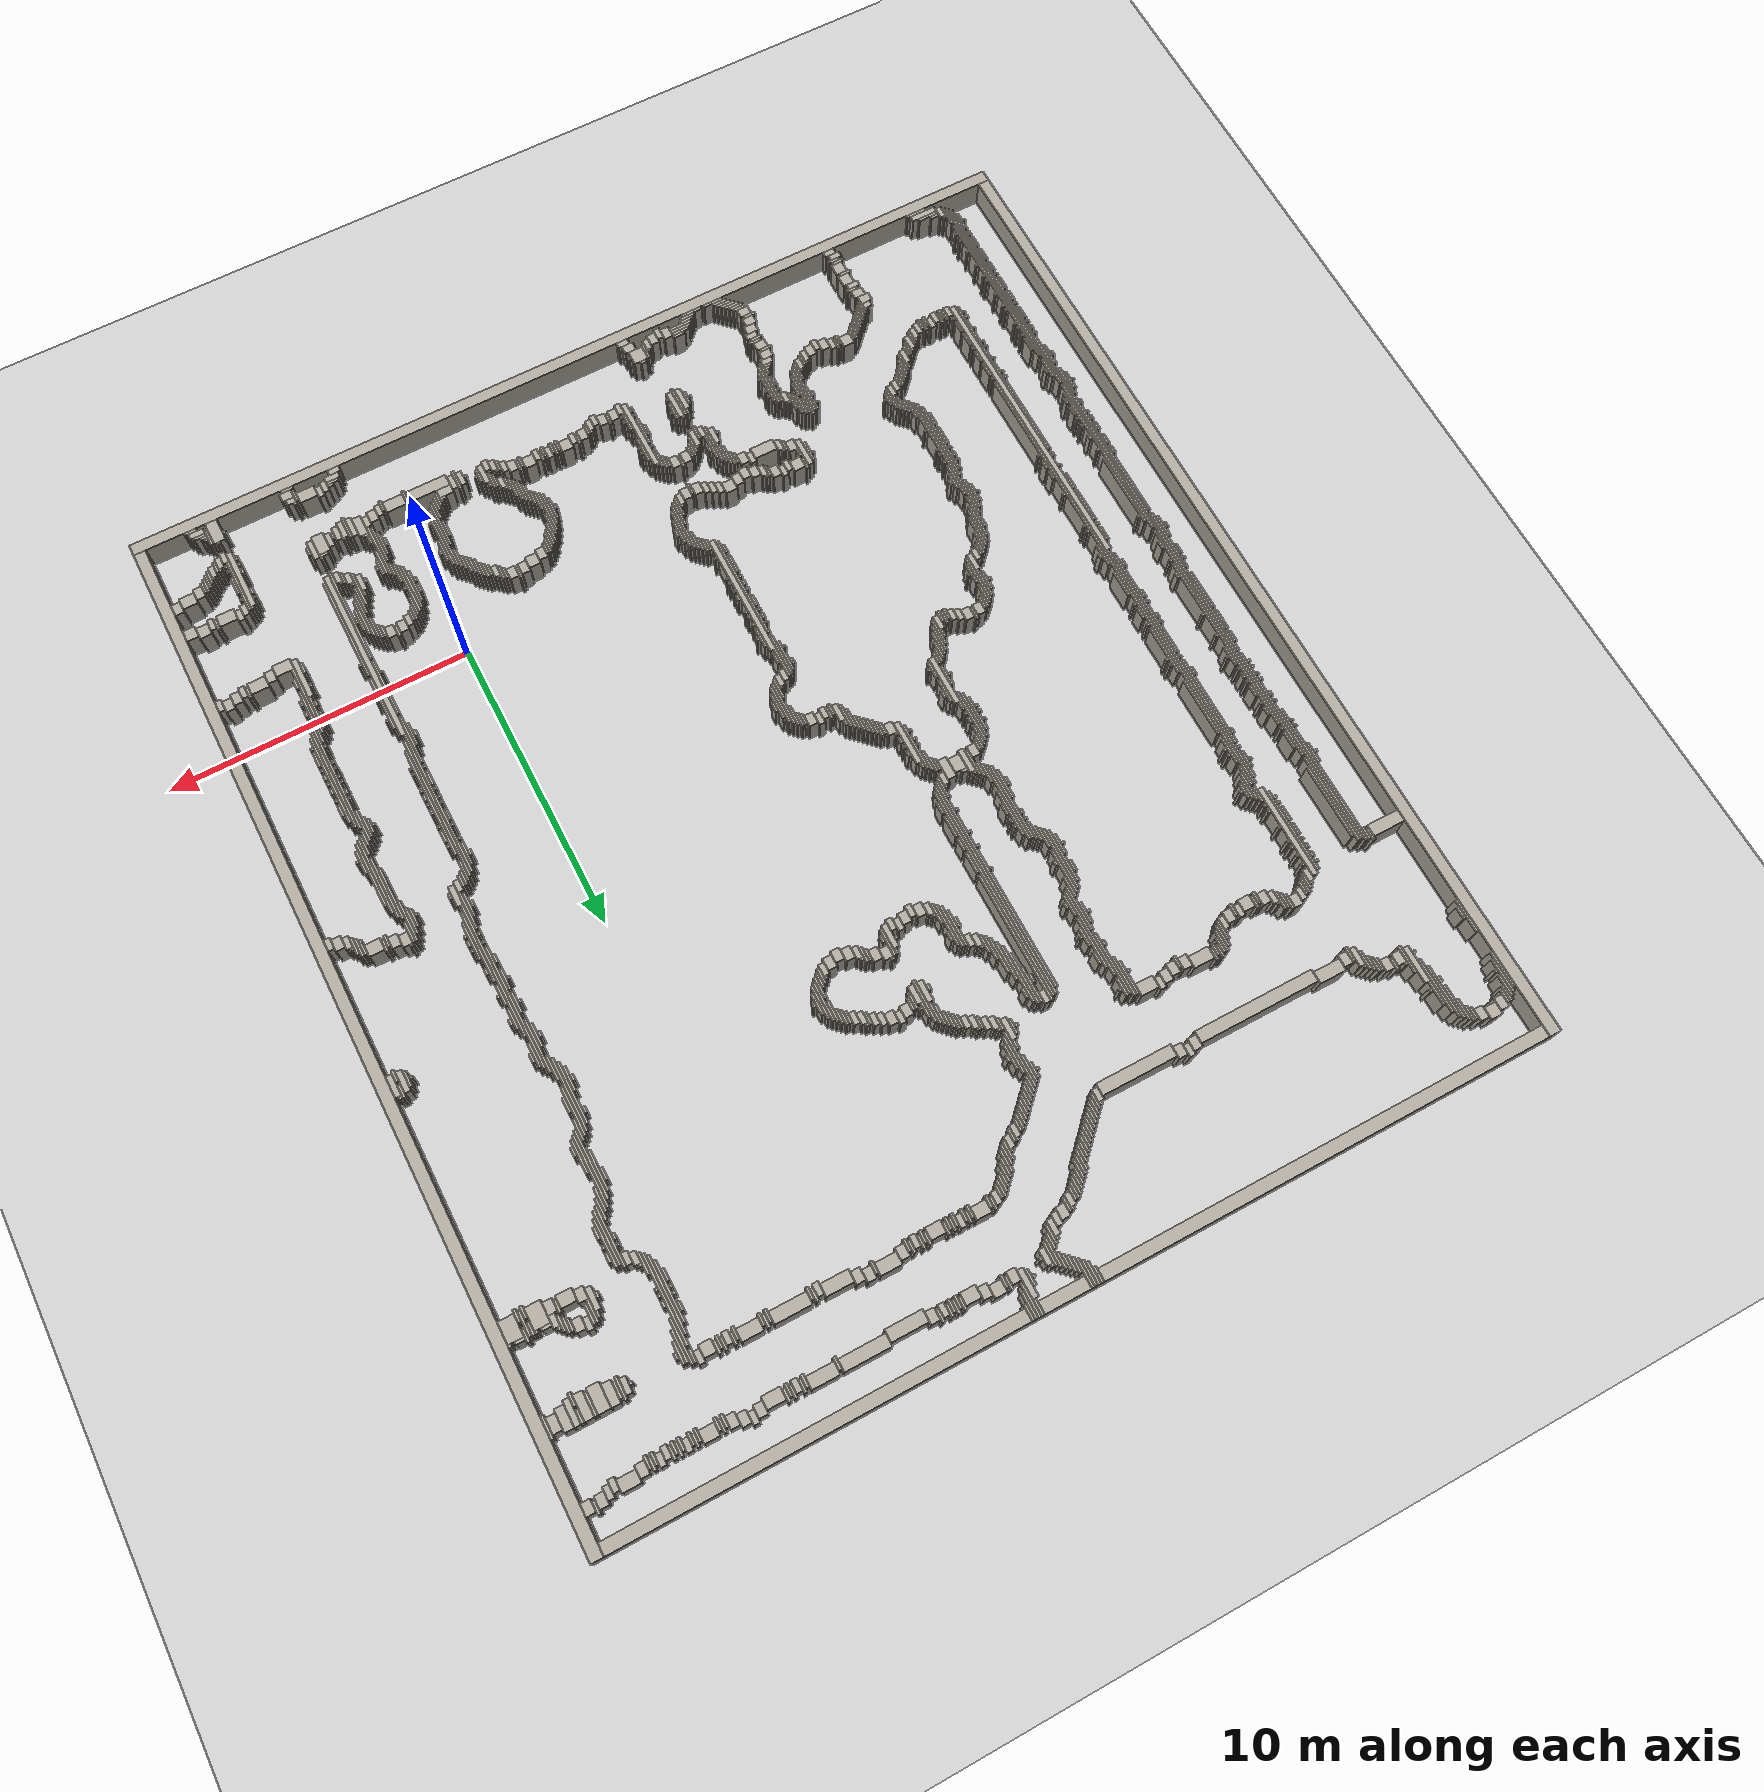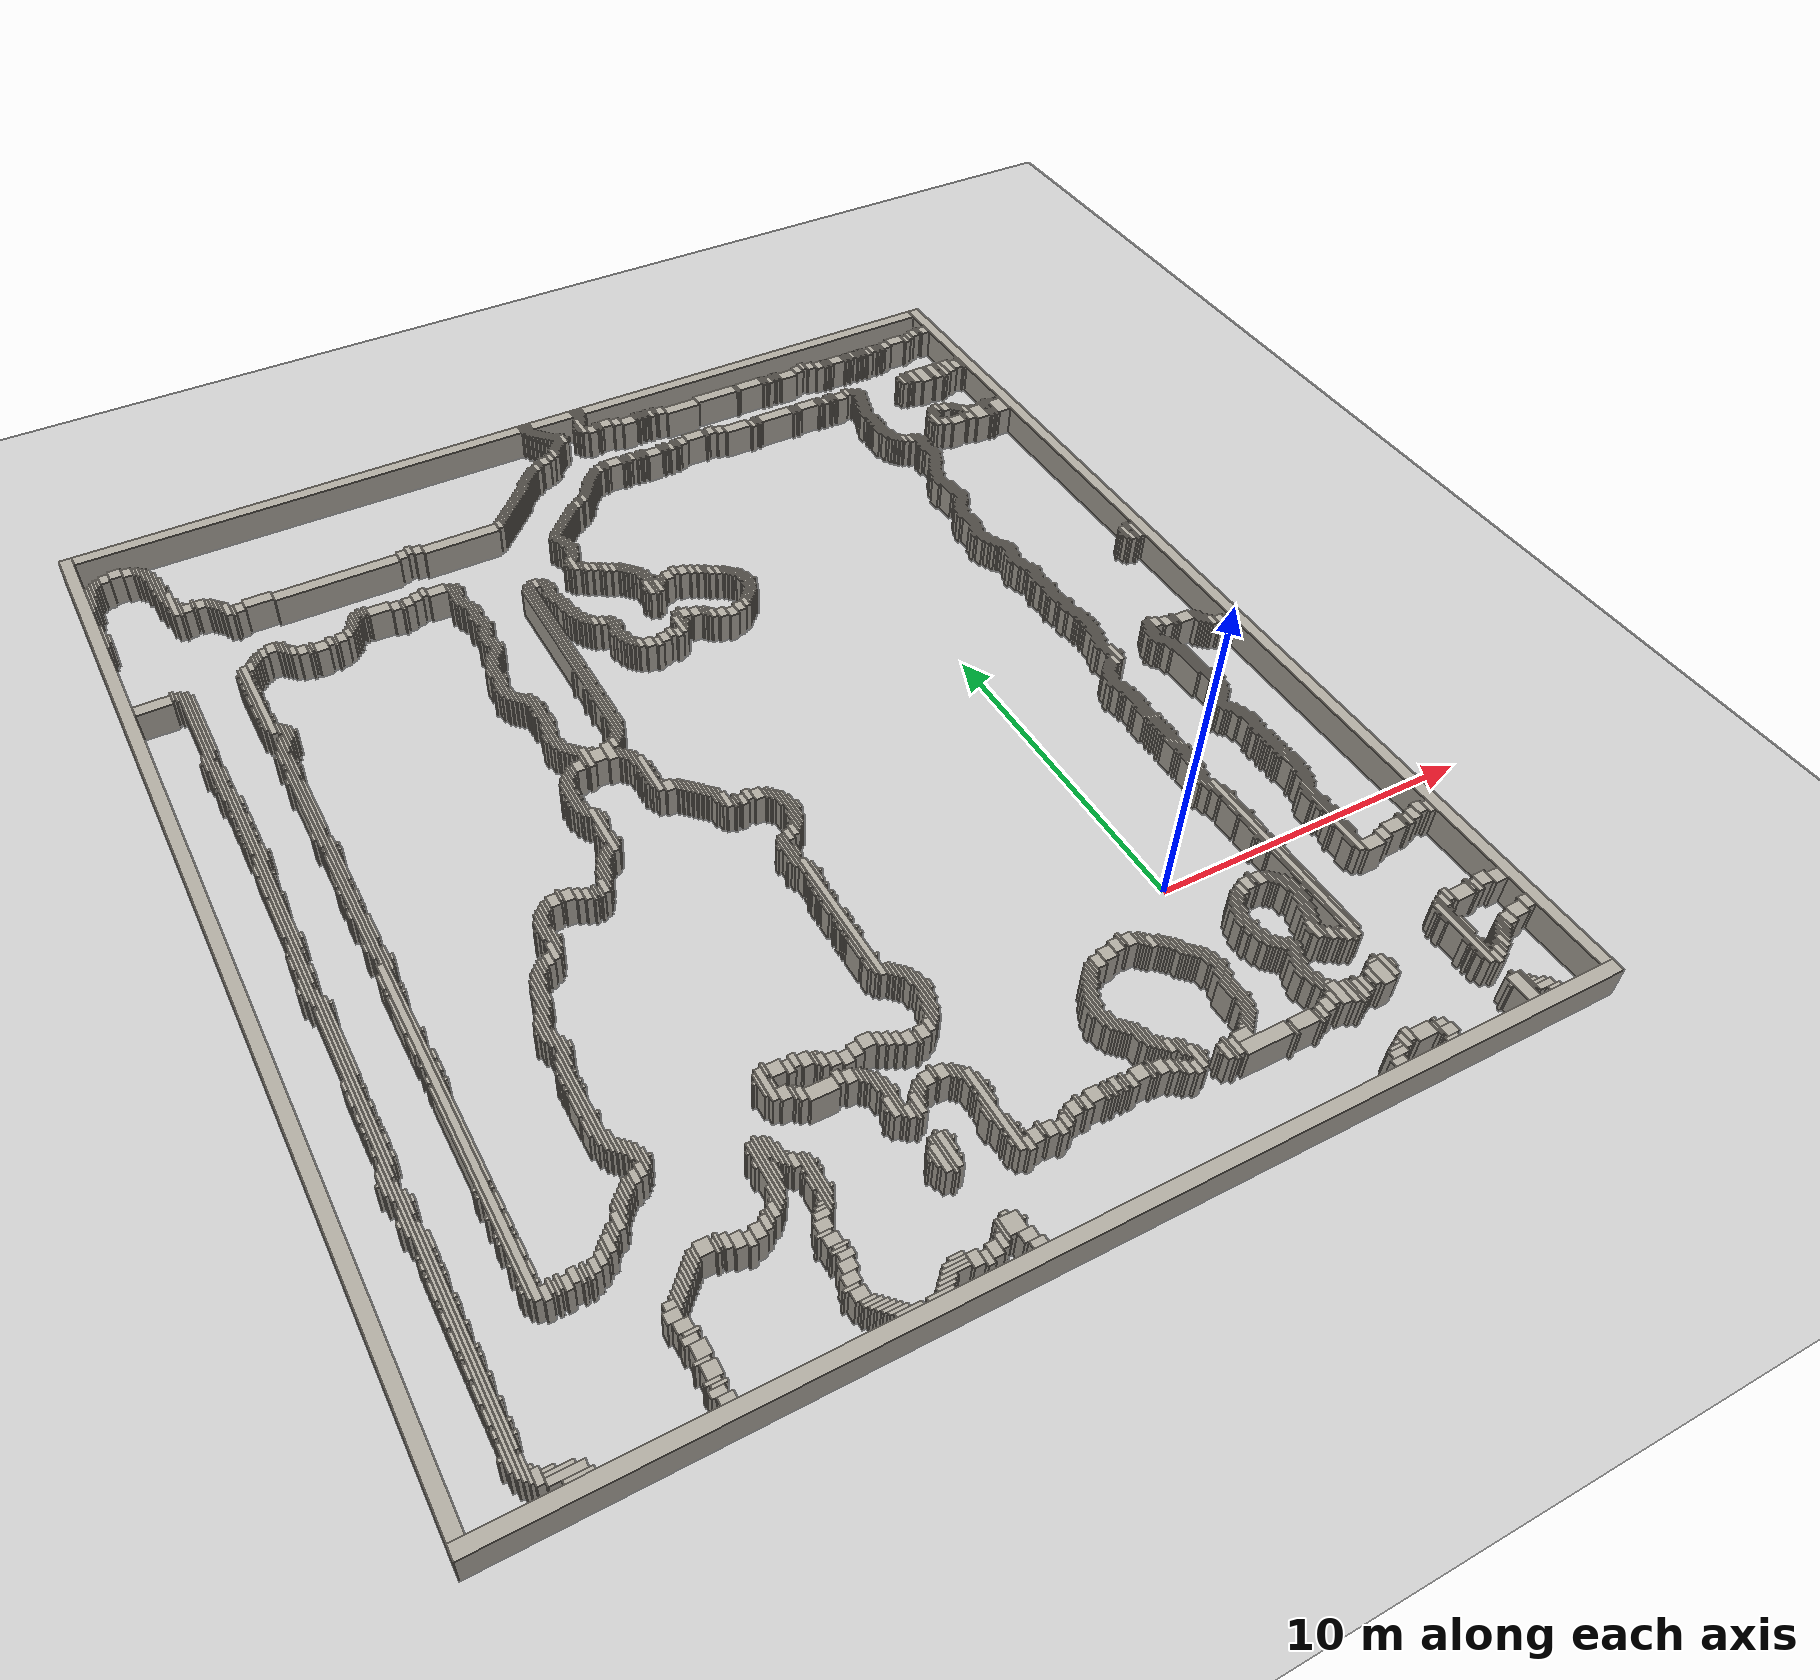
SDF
<?xml version="1.0" ?>
<sdf version="1.6">
  <world name="willow_office">

    <include><uri>model://sun</uri></include>
    <include><uri>model://ground_plane</uri></include>

    <physics type="ode">
      <max_step_size>0.004</max_step_size>
      <real_time_factor>1.0</real_time_factor>
      <real_time_update_rate>250.0</real_time_update_rate>
    </physics>

    <scene>
      <ambient>0.6 0.6 0.6 1</ambient>
      <shadows>false</shadows>
    </scene>

    <model name="willow_office_walls">
      <static>true</static>
      <link name="w0000">
        <pose>-7.485 -7.738 0.500 0 0 0</pose>
        <collision name="c"><geometry><box><size>31.000 0.400 1.000</size></box></geometry></collision>
        <visual name="v"><geometry><box><size>31.000 0.400 1.000</size></box></geometry>
          <material><ambient>0.68 0.66 0.62 1</ambient><diffuse>0.68 0.66 0.62 1</diffuse></material>
        </visual>
      </link>
      <link name="w0001">
        <pose>-22.785 9.262 0.500 0 0 0</pose>
        <collision name="c"><geometry><box><size>0.400 33.600 1.000</size></box></geometry></collision>
        <visual name="v"><geometry><box><size>0.400 33.600 1.000</size></box></geometry>
          <material><ambient>0.68 0.66 0.62 1</ambient><diffuse>0.68 0.66 0.62 1</diffuse></material>
        </visual>
      </link>
      <link name="w0002">
        <pose>-20.135 -7.488 0.500 0 0 0</pose>
        <collision name="c"><geometry><box><size>0.700 0.100 1.000</size></box></geometry></collision>
        <visual name="v"><geometry><box><size>0.700 0.100 1.000</size></box></geometry>
          <material><ambient>0.68 0.66 0.62 1</ambient><diffuse>0.68 0.66 0.62 1</diffuse></material>
        </visual>
      </link>
      <link name="w0003">
        <pose>-16.785 -7.438 0.500 0 0 0</pose>
        <collision name="c"><geometry><box><size>0.400 0.200 1.000</size></box></geometry></collision>
        <visual name="v"><geometry><box><size>0.400 0.200 1.000</size></box></geometry>
          <material><ambient>0.68 0.66 0.62 1</ambient><diffuse>0.68 0.66 0.62 1</diffuse></material>
        </visual>
      </link>
      <link name="w0004">
        <pose>-12.435 -7.488 0.500 0 0 0</pose>
        <collision name="c"><geometry><box><size>0.700 0.100 1.000</size></box></geometry></collision>
        <visual name="v"><geometry><box><size>0.700 0.100 1.000</size></box></geometry>
          <material><ambient>0.68 0.66 0.62 1</ambient><diffuse>0.68 0.66 0.62 1</diffuse></material>
        </visual>
      </link>
      <link name="w0005">
        <pose>-11.635 -7.488 0.500 0 0 0</pose>
        <collision name="c"><geometry><box><size>0.700 0.100 1.000</size></box></geometry></collision>
        <visual name="v"><geometry><box><size>0.700 0.100 1.000</size></box></geometry>
          <material><ambient>0.68 0.66 0.62 1</ambient><diffuse>0.68 0.66 0.62 1</diffuse></material>
        </visual>
      </link>
      <link name="w0006">
        <pose>-9.085 -7.438 0.500 0 0 0</pose>
        <collision name="c"><geometry><box><size>0.400 0.200 1.000</size></box></geometry></collision>
        <visual name="v"><geometry><box><size>0.400 0.200 1.000</size></box></geometry>
          <material><ambient>0.68 0.66 0.62 1</ambient><diffuse>0.68 0.66 0.62 1</diffuse></material>
        </visual>
      </link>
      <link name="w0007">
        <pose>1.215 -7.438 0.500 0 0 0</pose>
        <collision name="c"><geometry><box><size>0.400 0.200 1.000</size></box></geometry></collision>
        <visual name="v"><geometry><box><size>0.400 0.200 1.000</size></box></geometry>
          <material><ambient>0.68 0.66 0.62 1</ambient><diffuse>0.68 0.66 0.62 1</diffuse></material>
        </visual>
      </link>
      <link name="w0008">
        <pose>2.815 -7.488 0.500 0 0 0</pose>
        <collision name="c"><geometry><box><size>0.400 0.100 1.000</size></box></geometry></collision>
        <visual name="v"><geometry><box><size>0.400 0.100 1.000</size></box></geometry>
          <material><ambient>0.68 0.66 0.62 1</ambient><diffuse>0.68 0.66 0.62 1</diffuse></material>
        </visual>
      </link>
      <link name="w0009">
        <pose>5.415 -7.138 0.500 0 0 0</pose>
        <collision name="c"><geometry><box><size>0.400 0.800 1.000</size></box></geometry></collision>
        <visual name="v"><geometry><box><size>0.400 0.800 1.000</size></box></geometry>
          <material><ambient>0.68 0.66 0.62 1</ambient><diffuse>0.68 0.66 0.62 1</diffuse></material>
        </visual>
      </link>
      <link name="w0010">
        <pose>6.115 -7.488 0.500 0 0 0</pose>
        <collision name="c"><geometry><box><size>0.400 0.100 1.000</size></box></geometry></collision>
        <visual name="v"><geometry><box><size>0.400 0.100 1.000</size></box></geometry>
          <material><ambient>0.68 0.66 0.62 1</ambient><diffuse>0.68 0.66 0.62 1</diffuse></material>
        </visual>
      </link>
      <link name="w0011">
        <pose>7.815 9.262 0.500 0 0 0</pose>
        <collision name="c"><geometry><box><size>0.400 33.600 1.000</size></box></geometry></collision>
        <visual name="v"><geometry><box><size>0.400 33.600 1.000</size></box></geometry>
          <material><ambient>0.68 0.66 0.62 1</ambient><diffuse>0.68 0.66 0.62 1</diffuse></material>
        </visual>
      </link>
      <link name="w0012">
        <pose>-20.335 -7.338 0.500 0 0 0</pose>
        <collision name="c"><geometry><box><size>0.900 0.200 1.000</size></box></geometry></collision>
        <visual name="v"><geometry><box><size>0.900 0.200 1.000</size></box></geometry>
          <material><ambient>0.68 0.66 0.62 1</ambient><diffuse>0.68 0.66 0.62 1</diffuse></material>
        </visual>
      </link>
      <link name="w0013">
        <pose>-12.635 -7.388 0.500 0 0 0</pose>
        <collision name="c"><geometry><box><size>0.500 0.100 1.000</size></box></geometry></collision>
        <visual name="v"><geometry><box><size>0.500 0.100 1.000</size></box></geometry>
          <material><ambient>0.68 0.66 0.62 1</ambient><diffuse>0.68 0.66 0.62 1</diffuse></material>
        </visual>
      </link>
      <link name="w0014">
        <pose>-11.435 -7.388 0.500 0 0 0</pose>
        <collision name="c"><geometry><box><size>0.500 0.100 1.000</size></box></geometry></collision>
        <visual name="v"><geometry><box><size>0.500 0.100 1.000</size></box></geometry>
          <material><ambient>0.68 0.66 0.62 1</ambient><diffuse>0.68 0.66 0.62 1</diffuse></material>
        </visual>
      </link>
      <link name="w0015">
        <pose>-10.285 -7.238 0.500 0 0 0</pose>
        <collision name="c"><geometry><box><size>0.200 0.400 1.000</size></box></geometry></collision>
        <visual name="v"><geometry><box><size>0.200 0.400 1.000</size></box></geometry>
          <material><ambient>0.68 0.66 0.62 1</ambient><diffuse>0.68 0.66 0.62 1</diffuse></material>
        </visual>
      </link>
      <link name="w0016">
        <pose>2.915 -7.288 0.500 0 0 0</pose>
        <collision name="c"><geometry><box><size>0.400 0.300 1.000</size></box></geometry></collision>
        <visual name="v"><geometry><box><size>0.400 0.300 1.000</size></box></geometry>
          <material><ambient>0.68 0.66 0.62 1</ambient><diffuse>0.68 0.66 0.62 1</diffuse></material>
        </visual>
      </link>
      <link name="w0017">
        <pose>5.965 -7.338 0.500 0 0 0</pose>
        <collision name="c"><geometry><box><size>0.500 0.200 1.000</size></box></geometry></collision>
        <visual name="v"><geometry><box><size>0.500 0.200 1.000</size></box></geometry>
          <material><ambient>0.68 0.66 0.62 1</ambient><diffuse>0.68 0.66 0.62 1</diffuse></material>
        </visual>
      </link>
      <link name="w0018">
        <pose>-20.885 -7.138 0.500 0 0 0</pose>
        <collision name="c"><geometry><box><size>0.200 0.400 1.000</size></box></geometry></collision>
        <visual name="v"><geometry><box><size>0.200 0.400 1.000</size></box></geometry>
          <material><ambient>0.68 0.66 0.62 1</ambient><diffuse>0.68 0.66 0.62 1</diffuse></material>
        </visual>
      </link>
      <link name="w0019">
        <pose>-16.885 -7.238 0.500 0 0 0</pose>
        <collision name="c"><geometry><box><size>0.400 0.200 1.000</size></box></geometry></collision>
        <visual name="v"><geometry><box><size>0.400 0.200 1.000</size></box></geometry>
          <material><ambient>0.68 0.66 0.62 1</ambient><diffuse>0.68 0.66 0.62 1</diffuse></material>
        </visual>
      </link>
      <link name="w0020">
        <pose>-12.735 -7.288 0.500 0 0 0</pose>
        <collision name="c"><geometry><box><size>0.500 0.100 1.000</size></box></geometry></collision>
        <visual name="v"><geometry><box><size>0.500 0.100 1.000</size></box></geometry>
          <material><ambient>0.68 0.66 0.62 1</ambient><diffuse>0.68 0.66 0.62 1</diffuse></material>
        </visual>
      </link>
      <link name="w0021">
        <pose>-11.335 -7.288 0.500 0 0 0</pose>
        <collision name="c"><geometry><box><size>0.500 0.100 1.000</size></box></geometry></collision>
        <visual name="v"><geometry><box><size>0.500 0.100 1.000</size></box></geometry>
          <material><ambient>0.68 0.66 0.62 1</ambient><diffuse>0.68 0.66 0.62 1</diffuse></material>
        </visual>
      </link>
      <link name="w0022">
        <pose>-10.535 -7.138 0.500 0 0 0</pose>
        <collision name="c"><geometry><box><size>0.300 0.400 1.000</size></box></geometry></collision>
        <visual name="v"><geometry><box><size>0.300 0.400 1.000</size></box></geometry>
          <material><ambient>0.68 0.66 0.62 1</ambient><diffuse>0.68 0.66 0.62 1</diffuse></material>
        </visual>
      </link>
      <link name="w0023">
        <pose>-10.035 -7.138 0.500 0 0 0</pose>
        <collision name="c"><geometry><box><size>0.300 0.400 1.000</size></box></geometry></collision>
        <visual name="v"><geometry><box><size>0.300 0.400 1.000</size></box></geometry>
          <material><ambient>0.68 0.66 0.62 1</ambient><diffuse>0.68 0.66 0.62 1</diffuse></material>
        </visual>
      </link>
      <link name="w0024">
        <pose>-9.185 -7.188 0.500 0 0 0</pose>
        <collision name="c"><geometry><box><size>0.400 0.300 1.000</size></box></geometry></collision>
        <visual name="v"><geometry><box><size>0.400 0.300 1.000</size></box></geometry>
          <material><ambient>0.68 0.66 0.62 1</ambient><diffuse>0.68 0.66 0.62 1</diffuse></material>
        </visual>
      </link>
      <link name="w0025">
        <pose>1.365 -7.238 0.500 0 0 0</pose>
        <collision name="c"><geometry><box><size>0.500 0.200 1.000</size></box></geometry></collision>
        <visual name="v"><geometry><box><size>0.500 0.200 1.000</size></box></geometry>
          <material><ambient>0.68 0.66 0.62 1</ambient><diffuse>0.68 0.66 0.62 1</diffuse></material>
        </visual>
      </link>
      <link name="w0026">
        <pose>2.665 -7.138 0.500 0 0 0</pose>
        <collision name="c"><geometry><box><size>0.100 0.400 1.000</size></box></geometry></collision>
        <visual name="v"><geometry><box><size>0.100 0.400 1.000</size></box></geometry>
          <material><ambient>0.68 0.66 0.62 1</ambient><diffuse>0.68 0.66 0.62 1</diffuse></material>
        </visual>
      </link>
      <link name="w0027">
        <pose>5.665 -7.038 0.500 0 0 0</pose>
        <collision name="c"><geometry><box><size>0.100 0.600 1.000</size></box></geometry></collision>
        <visual name="v"><geometry><box><size>0.100 0.600 1.000</size></box></geometry>
          <material><ambient>0.68 0.66 0.62 1</ambient><diffuse>0.68 0.66 0.62 1</diffuse></material>
        </visual>
      </link>
      <link name="w0028">
        <pose>-21.035 -6.888 0.500 0 0 0</pose>
        <collision name="c"><geometry><box><size>0.100 0.700 1.000</size></box></geometry></collision>
        <visual name="v"><geometry><box><size>0.100 0.700 1.000</size></box></geometry>
          <material><ambient>0.68 0.66 0.62 1</ambient><diffuse>0.68 0.66 0.62 1</diffuse></material>
        </visual>
      </link>
      <link name="w0029">
        <pose>-20.435 -7.188 0.500 0 0 0</pose>
        <collision name="c"><geometry><box><size>0.700 0.100 1.000</size></box></geometry></collision>
        <visual name="v"><geometry><box><size>0.700 0.100 1.000</size></box></geometry>
          <material><ambient>0.68 0.66 0.62 1</ambient><diffuse>0.68 0.66 0.62 1</diffuse></material>
        </visual>
      </link>
      <link name="w0030">
        <pose>-12.835 -7.188 0.500 0 0 0</pose>
        <collision name="c"><geometry><box><size>0.500 0.100 1.000</size></box></geometry></collision>
        <visual name="v"><geometry><box><size>0.500 0.100 1.000</size></box></geometry>
          <material><ambient>0.68 0.66 0.62 1</ambient><diffuse>0.68 0.66 0.62 1</diffuse></material>
        </visual>
      </link>
      <link name="w0031">
        <pose>-11.085 -7.188 0.500 0 0 0</pose>
        <collision name="c"><geometry><box><size>0.800 0.100 1.000</size></box></geometry></collision>
        <visual name="v"><geometry><box><size>0.800 0.100 1.000</size></box></geometry>
          <material><ambient>0.68 0.66 0.62 1</ambient><diffuse>0.68 0.66 0.62 1</diffuse></material>
        </visual>
      </link>
      <link name="w0032">
        <pose>-9.785 -7.038 0.500 0 0 0</pose>
        <collision name="c"><geometry><box><size>0.200 0.400 1.000</size></box></geometry></collision>
        <visual name="v"><geometry><box><size>0.200 0.400 1.000</size></box></geometry>
          <material><ambient>0.68 0.66 0.62 1</ambient><diffuse>0.68 0.66 0.62 1</diffuse></material>
        </visual>
      </link>
      <link name="w0033">
        <pose>1.715 -7.038 0.500 0 0 0</pose>
        <collision name="c"><geometry><box><size>0.200 0.400 1.000</size></box></geometry></collision>
        <visual name="v"><geometry><box><size>0.200 0.400 1.000</size></box></geometry>
          <material><ambient>0.68 0.66 0.62 1</ambient><diffuse>0.68 0.66 0.62 1</diffuse></material>
        </visual>
      </link>
      <link name="w0034">
        <pose>2.315 -7.038 0.500 0 0 0</pose>
        <collision name="c"><geometry><box><size>0.600 0.400 1.000</size></box></geometry></collision>
        <visual name="v"><geometry><box><size>0.600 0.400 1.000</size></box></geometry>
          <material><ambient>0.68 0.66 0.62 1</ambient><diffuse>0.68 0.66 0.62 1</diffuse></material>
        </visual>
      </link>
      <link name="w0035">
        <pose>5.915 -7.188 0.500 0 0 0</pose>
        <collision name="c"><geometry><box><size>0.400 0.100 1.000</size></box></geometry></collision>
        <visual name="v"><geometry><box><size>0.400 0.100 1.000</size></box></geometry>
          <material><ambient>0.68 0.66 0.62 1</ambient><diffuse>0.68 0.66 0.62 1</diffuse></material>
        </visual>
      </link>
      <link name="w0036">
        <pose>-21.135 -3.288 0.500 0 0 0</pose>
        <collision name="c"><geometry><box><size>0.100 7.700 1.000</size></box></geometry></collision>
        <visual name="v"><geometry><box><size>0.100 7.700 1.000</size></box></geometry>
          <material><ambient>0.68 0.66 0.62 1</ambient><diffuse>0.68 0.66 0.62 1</diffuse></material>
        </visual>
      </link>
      <link name="w0037">
        <pose>-20.635 -7.088 0.500 0 0 0</pose>
        <collision name="c"><geometry><box><size>0.300 0.100 1.000</size></box></geometry></collision>
        <visual name="v"><geometry><box><size>0.300 0.100 1.000</size></box></geometry>
          <material><ambient>0.68 0.66 0.62 1</ambient><diffuse>0.68 0.66 0.62 1</diffuse></material>
        </visual>
      </link>
      <link name="w0038">
        <pose>-16.785 -7.088 0.500 0 0 0</pose>
        <collision name="c"><geometry><box><size>0.400 0.100 1.000</size></box></geometry></collision>
        <visual name="v"><geometry><box><size>0.400 0.100 1.000</size></box></geometry>
          <material><ambient>0.68 0.66 0.62 1</ambient><diffuse>0.68 0.66 0.62 1</diffuse></material>
        </visual>
      </link>
      <link name="w0039">
        <pose>-12.935 -7.088 0.500 0 0 0</pose>
        <collision name="c"><geometry><box><size>0.500 0.100 1.000</size></box></geometry></collision>
        <visual name="v"><geometry><box><size>0.500 0.100 1.000</size></box></geometry>
          <material><ambient>0.68 0.66 0.62 1</ambient><diffuse>0.68 0.66 0.62 1</diffuse></material>
        </visual>
      </link>
      <link name="w0040">
        <pose>-11.035 -7.088 0.500 0 0 0</pose>
        <collision name="c"><geometry><box><size>0.700 0.100 1.000</size></box></geometry></collision>
        <visual name="v"><geometry><box><size>0.700 0.100 1.000</size></box></geometry>
          <material><ambient>0.68 0.66 0.62 1</ambient><diffuse>0.68 0.66 0.62 1</diffuse></material>
        </visual>
      </link>
      <link name="w0041">
        <pose>-9.635 -6.838 0.500 0 0 0</pose>
        <collision name="c"><geometry><box><size>0.100 0.600 1.000</size></box></geometry></collision>
        <visual name="v"><geometry><box><size>0.100 0.600 1.000</size></box></geometry>
          <material><ambient>0.68 0.66 0.62 1</ambient><diffuse>0.68 0.66 0.62 1</diffuse></material>
        </visual>
      </link>
      <link name="w0042">
        <pose>1.415 -7.088 0.500 0 0 0</pose>
        <collision name="c"><geometry><box><size>0.400 0.100 1.000</size></box></geometry></collision>
        <visual name="v"><geometry><box><size>0.400 0.100 1.000</size></box></geometry>
          <material><ambient>0.68 0.66 0.62 1</ambient><diffuse>0.68 0.66 0.62 1</diffuse></material>
        </visual>
      </link>
      <link name="w0043">
        <pose>1.915 -6.938 0.500 0 0 0</pose>
        <collision name="c"><geometry><box><size>0.200 0.400 1.000</size></box></geometry></collision>
        <visual name="v"><geometry><box><size>0.200 0.400 1.000</size></box></geometry>
          <material><ambient>0.68 0.66 0.62 1</ambient><diffuse>0.68 0.66 0.62 1</diffuse></material>
        </visual>
      </link>
      <link name="w0044">
        <pose>2.865 -7.038 0.500 0 0 0</pose>
        <collision name="c"><geometry><box><size>0.300 0.200 1.000</size></box></geometry></collision>
        <visual name="v"><geometry><box><size>0.300 0.200 1.000</size></box></geometry>
          <material><ambient>0.68 0.66 0.62 1</ambient><diffuse>0.68 0.66 0.62 1</diffuse></material>
        </visual>
      </link>
      <link name="w0045">
        <pose>5.815 -7.088 0.500 0 0 0</pose>
        <collision name="c"><geometry><box><size>0.200 0.100 1.000</size></box></geometry></collision>
        <visual name="v"><geometry><box><size>0.200 0.100 1.000</size></box></geometry>
          <material><ambient>0.68 0.66 0.62 1</ambient><diffuse>0.68 0.66 0.62 1</diffuse></material>
        </visual>
      </link>
      <link name="w0046">
        <pose>-21.235 -0.538 0.500 0 0 0</pose>
        <collision name="c"><geometry><box><size>0.100 13.000 1.000</size></box></geometry></collision>
        <visual name="v"><geometry><box><size>0.100 13.000 1.000</size></box></geometry>
          <material><ambient>0.68 0.66 0.62 1</ambient><diffuse>0.68 0.66 0.62 1</diffuse></material>
        </visual>
      </link>
      <link name="w0047">
        <pose>-16.885 -6.988 0.500 0 0 0</pose>
        <collision name="c"><geometry><box><size>0.400 0.100 1.000</size></box></geometry></collision>
        <visual name="v"><geometry><box><size>0.400 0.100 1.000</size></box></geometry>
          <material><ambient>0.68 0.66 0.62 1</ambient><diffuse>0.68 0.66 0.62 1</diffuse></material>
        </visual>
      </link>
      <link name="w0048">
        <pose>-13.035 -6.988 0.500 0 0 0</pose>
        <collision name="c"><geometry><box><size>0.500 0.100 1.000</size></box></geometry></collision>
        <visual name="v"><geometry><box><size>0.500 0.100 1.000</size></box></geometry>
          <material><ambient>0.68 0.66 0.62 1</ambient><diffuse>0.68 0.66 0.62 1</diffuse></material>
        </visual>
      </link>
      <link name="w0049">
        <pose>-10.985 -6.988 0.500 0 0 0</pose>
        <collision name="c"><geometry><box><size>0.600 0.100 1.000</size></box></geometry></collision>
        <visual name="v"><geometry><box><size>0.600 0.100 1.000</size></box></geometry>
          <material><ambient>0.68 0.66 0.62 1</ambient><diffuse>0.68 0.66 0.62 1</diffuse></material>
        </visual>
      </link>
      <link name="w0050">
        <pose>-9.335 -6.788 0.500 0 0 0</pose>
        <collision name="c"><geometry><box><size>0.500 0.500 1.000</size></box></geometry></collision>
        <visual name="v"><geometry><box><size>0.500 0.500 1.000</size></box></geometry>
          <material><ambient>0.68 0.66 0.62 1</ambient><diffuse>0.68 0.66 0.62 1</diffuse></material>
        </visual>
      </link>
      <link name="w0051">
        <pose>1.515 -6.988 0.500 0 0 0</pose>
        <collision name="c"><geometry><box><size>0.200 0.100 1.000</size></box></geometry></collision>
        <visual name="v"><geometry><box><size>0.200 0.100 1.000</size></box></geometry>
          <material><ambient>0.68 0.66 0.62 1</ambient><diffuse>0.68 0.66 0.62 1</diffuse></material>
        </visual>
      </link>
      <link name="w0052">
        <pose>5.165 -6.988 0.500 0 0 0</pose>
        <collision name="c"><geometry><box><size>0.100 0.100 1.000</size></box></geometry></collision>
        <visual name="v"><geometry><box><size>0.100 0.100 1.000</size></box></geometry>
          <material><ambient>0.68 0.66 0.62 1</ambient><diffuse>0.68 0.66 0.62 1</diffuse></material>
        </visual>
      </link>
      <link name="w0053">
        <pose>5.765 -6.988 0.500 0 0 0</pose>
        <collision name="c"><geometry><box><size>0.100 0.100 1.000</size></box></geometry></collision>
        <visual name="v"><geometry><box><size>0.100 0.100 1.000</size></box></geometry>
          <material><ambient>0.68 0.66 0.62 1</ambient><diffuse>0.68 0.66 0.62 1</diffuse></material>
        </visual>
      </link>
      <link name="w0054">
        <pose>-20.935 -6.888 0.500 0 0 0</pose>
        <collision name="c"><geometry><box><size>0.100 0.100 1.000</size></box></geometry></collision>
        <visual name="v"><geometry><box><size>0.100 0.100 1.000</size></box></geometry>
          <material><ambient>0.68 0.66 0.62 1</ambient><diffuse>0.68 0.66 0.62 1</diffuse></material>
        </visual>
      </link>
      <link name="w0055">
        <pose>-16.785 -6.738 0.500 0 0 0</pose>
        <collision name="c"><geometry><box><size>0.400 0.400 1.000</size></box></geometry></collision>
        <visual name="v"><geometry><box><size>0.400 0.400 1.000</size></box></geometry>
          <material><ambient>0.68 0.66 0.62 1</ambient><diffuse>0.68 0.66 0.62 1</diffuse></material>
        </visual>
      </link>
      <link name="w0056">
        <pose>-13.085 -6.888 0.500 0 0 0</pose>
        <collision name="c"><geometry><box><size>0.400 0.100 1.000</size></box></geometry></collision>
        <visual name="v"><geometry><box><size>0.400 0.100 1.000</size></box></geometry>
          <material><ambient>0.68 0.66 0.62 1</ambient><diffuse>0.68 0.66 0.62 1</diffuse></material>
        </visual>
      </link>
      <link name="w0057">
        <pose>-10.885 -6.888 0.500 0 0 0</pose>
        <collision name="c"><geometry><box><size>0.400 0.100 1.000</size></box></geometry></collision>
        <visual name="v"><geometry><box><size>0.400 0.100 1.000</size></box></geometry>
          <material><ambient>0.68 0.66 0.62 1</ambient><diffuse>0.68 0.66 0.62 1</diffuse></material>
        </visual>
      </link>
      <link name="w0058">
        <pose>2.765 -6.888 0.500 0 0 0</pose>
        <collision name="c"><geometry><box><size>0.100 0.100 1.000</size></box></geometry></collision>
        <visual name="v"><geometry><box><size>0.100 0.100 1.000</size></box></geometry>
          <material><ambient>0.68 0.66 0.62 1</ambient><diffuse>0.68 0.66 0.62 1</diffuse></material>
        </visual>
      </link>
      <link name="w0059">
        <pose>-21.335 -6.488 0.500 0 0 0</pose>
        <collision name="c"><geometry><box><size>0.100 0.700 1.000</size></box></geometry></collision>
        <visual name="v"><geometry><box><size>0.100 0.700 1.000</size></box></geometry>
          <material><ambient>0.68 0.66 0.62 1</ambient><diffuse>0.68 0.66 0.62 1</diffuse></material>
        </visual>
      </link>
      <link name="w0060">
        <pose>-13.185 -6.688 0.500 0 0 0</pose>
        <collision name="c"><geometry><box><size>0.400 0.300 1.000</size></box></geometry></collision>
        <visual name="v"><geometry><box><size>0.400 0.300 1.000</size></box></geometry>
          <material><ambient>0.68 0.66 0.62 1</ambient><diffuse>0.68 0.66 0.62 1</diffuse></material>
        </visual>
      </link>
      <link name="w0061">
        <pose>-9.735 -6.788 0.500 0 0 0</pose>
        <collision name="c"><geometry><box><size>0.100 0.100 1.000</size></box></geometry></collision>
        <visual name="v"><geometry><box><size>0.100 0.100 1.000</size></box></geometry>
          <material><ambient>0.68 0.66 0.62 1</ambient><diffuse>0.68 0.66 0.62 1</diffuse></material>
        </visual>
      </link>
      <link name="w0062">
        <pose>-9.035 -6.788 0.500 0 0 0</pose>
        <collision name="c"><geometry><box><size>0.100 0.100 1.000</size></box></geometry></collision>
        <visual name="v"><geometry><box><size>0.100 0.100 1.000</size></box></geometry>
          <material><ambient>0.68 0.66 0.62 1</ambient><diffuse>0.68 0.66 0.62 1</diffuse></material>
        </visual>
      </link>
      <link name="w0063">
        <pose>5.465 -6.688 0.500 0 0 0</pose>
        <collision name="c"><geometry><box><size>0.100 0.100 1.000</size></box></geometry></collision>
        <visual name="v"><geometry><box><size>0.100 0.100 1.000</size></box></geometry>
          <material><ambient>0.68 0.66 0.62 1</ambient><diffuse>0.68 0.66 0.62 1</diffuse></material>
        </visual>
      </link>
      <link name="w0064">
        <pose>-21.435 -6.488 0.500 0 0 0</pose>
        <collision name="c"><geometry><box><size>0.100 0.100 1.000</size></box></geometry></collision>
        <visual name="v"><geometry><box><size>0.100 0.100 1.000</size></box></geometry>
          <material><ambient>0.68 0.66 0.62 1</ambient><diffuse>0.68 0.66 0.62 1</diffuse></material>
        </visual>
      </link>
      <link name="w0065">
        <pose>-16.885 -6.488 0.500 0 0 0</pose>
        <collision name="c"><geometry><box><size>0.400 0.100 1.000</size></box></geometry></collision>
        <visual name="v"><geometry><box><size>0.400 0.100 1.000</size></box></geometry>
          <material><ambient>0.68 0.66 0.62 1</ambient><diffuse>0.68 0.66 0.62 1</diffuse></material>
        </visual>
      </link>
      <link name="w0066">
        <pose>-13.285 -6.488 0.500 0 0 0</pose>
        <collision name="c"><geometry><box><size>0.400 0.100 1.000</size></box></geometry></collision>
        <visual name="v"><geometry><box><size>0.400 0.100 1.000</size></box></geometry>
          <material><ambient>0.68 0.66 0.62 1</ambient><diffuse>0.68 0.66 0.62 1</diffuse></material>
        </visual>
      </link>
      <link name="w0067">
        <pose>-9.385 -6.488 0.500 0 0 0</pose>
        <collision name="c"><geometry><box><size>0.200 0.100 1.000</size></box></geometry></collision>
        <visual name="v"><geometry><box><size>0.200 0.100 1.000</size></box></geometry>
          <material><ambient>0.68 0.66 0.62 1</ambient><diffuse>0.68 0.66 0.62 1</diffuse></material>
        </visual>
      </link>
      <link name="w0068">
        <pose>-21.035 -3.538 0.500 0 0 0</pose>
        <collision name="c"><geometry><box><size>0.100 5.800 1.000</size></box></geometry></collision>
        <visual name="v"><geometry><box><size>0.100 5.800 1.000</size></box></geometry>
          <material><ambient>0.68 0.66 0.62 1</ambient><diffuse>0.68 0.66 0.62 1</diffuse></material>
        </visual>
      </link>
      <link name="w0069">
        <pose>-16.785 -6.238 0.500 0 0 0</pose>
        <collision name="c"><geometry><box><size>0.400 0.400 1.000</size></box></geometry></collision>
        <visual name="v"><geometry><box><size>0.400 0.400 1.000</size></box></geometry>
          <material><ambient>0.68 0.66 0.62 1</ambient><diffuse>0.68 0.66 0.62 1</diffuse></material>
        </visual>
      </link>
      <link name="w0070">
        <pose>-13.185 -6.288 0.500 0 0 0</pose>
        <collision name="c"><geometry><box><size>0.400 0.300 1.000</size></box></geometry></collision>
        <visual name="v"><geometry><box><size>0.400 0.300 1.000</size></box></geometry>
          <material><ambient>0.68 0.66 0.62 1</ambient><diffuse>0.68 0.66 0.62 1</diffuse></material>
        </visual>
      </link>
      <link name="w0071">
        <pose>5.515 -6.138 0.500 0 0 0</pose>
        <collision name="c"><geometry><box><size>0.200 0.400 1.000</size></box></geometry></collision>
        <visual name="v"><geometry><box><size>0.200 0.400 1.000</size></box></geometry>
          <material><ambient>0.68 0.66 0.62 1</ambient><diffuse>0.68 0.66 0.62 1</diffuse></material>
        </visual>
      </link>
      <link name="w0072">
        <pose>5.315 -5.188 0.500 0 0 0</pose>
        <collision name="c"><geometry><box><size>0.200 2.100 1.000</size></box></geometry></collision>
        <visual name="v"><geometry><box><size>0.200 2.100 1.000</size></box></geometry>
          <material><ambient>0.68 0.66 0.62 1</ambient><diffuse>0.68 0.66 0.62 1</diffuse></material>
        </visual>
      </link>
      <link name="w0073">
        <pose>5.715 -6.038 0.500 0 0 0</pose>
        <collision name="c"><geometry><box><size>0.200 0.400 1.000</size></box></geometry></collision>
        <visual name="v"><geometry><box><size>0.200 0.400 1.000</size></box></geometry>
          <material><ambient>0.68 0.66 0.62 1</ambient><diffuse>0.68 0.66 0.62 1</diffuse></material>
        </visual>
      </link>
      <link name="w0074">
        <pose>-20.935 -6.088 0.500 0 0 0</pose>
        <collision name="c"><geometry><box><size>0.100 0.100 1.000</size></box></geometry></collision>
        <visual name="v"><geometry><box><size>0.100 0.100 1.000</size></box></geometry>
          <material><ambient>0.68 0.66 0.62 1</ambient><diffuse>0.68 0.66 0.62 1</diffuse></material>
        </visual>
      </link>
      <link name="w0075">
        <pose>-13.085 -5.988 0.500 0 0 0</pose>
        <collision name="c"><geometry><box><size>0.400 0.300 1.000</size></box></geometry></collision>
        <visual name="v"><geometry><box><size>0.400 0.300 1.000</size></box></geometry>
          <material><ambient>0.68 0.66 0.62 1</ambient><diffuse>0.68 0.66 0.62 1</diffuse></material>
        </visual>
      </link>
      <link name="w0076">
        <pose>5.865 -5.938 0.500 0 0 0</pose>
        <collision name="c"><geometry><box><size>0.100 0.400 1.000</size></box></geometry></collision>
        <visual name="v"><geometry><box><size>0.100 0.400 1.000</size></box></geometry>
          <material><ambient>0.68 0.66 0.62 1</ambient><diffuse>0.68 0.66 0.62 1</diffuse></material>
        </visual>
      </link>
      <link name="w0077">
        <pose>-21.335 -5.938 0.500 0 0 0</pose>
        <collision name="c"><geometry><box><size>0.100 0.200 1.000</size></box></geometry></collision>
        <visual name="v"><geometry><box><size>0.100 0.200 1.000</size></box></geometry>
          <material><ambient>0.68 0.66 0.62 1</ambient><diffuse>0.68 0.66 0.62 1</diffuse></material>
        </visual>
      </link>
      <link name="w0078">
        <pose>-16.885 -5.938 0.500 0 0 0</pose>
        <collision name="c"><geometry><box><size>0.400 0.200 1.000</size></box></geometry></collision>
        <visual name="v"><geometry><box><size>0.400 0.200 1.000</size></box></geometry>
          <material><ambient>0.68 0.66 0.62 1</ambient><diffuse>0.68 0.66 0.62 1</diffuse></material>
        </visual>
      </link>
      <link name="w0079">
        <pose>5.165 -5.938 0.500 0 0 0</pose>
        <collision name="c"><geometry><box><size>0.100 0.200 1.000</size></box></geometry></collision>
        <visual name="v"><geometry><box><size>0.100 0.200 1.000</size></box></geometry>
          <material><ambient>0.68 0.66 0.62 1</ambient><diffuse>0.68 0.66 0.62 1</diffuse></material>
        </visual>
      </link>
      <link name="w0080">
        <pose>6.015 -5.838 0.500 0 0 0</pose>
        <collision name="c"><geometry><box><size>0.200 0.400 1.000</size></box></geometry></collision>
        <visual name="v"><geometry><box><size>0.200 0.400 1.000</size></box></geometry>
          <material><ambient>0.68 0.66 0.62 1</ambient><diffuse>0.68 0.66 0.62 1</diffuse></material>
        </visual>
      </link>
      <link name="w0081">
        <pose>5.465 -4.988 0.500 0 0 0</pose>
        <collision name="c"><geometry><box><size>0.100 1.900 1.000</size></box></geometry></collision>
        <visual name="v"><geometry><box><size>0.100 1.900 1.000</size></box></geometry>
          <material><ambient>0.68 0.66 0.62 1</ambient><diffuse>0.68 0.66 0.62 1</diffuse></material>
        </visual>
      </link>
      <link name="w0082">
        <pose>6.165 -5.688 0.500 0 0 0</pose>
        <collision name="c"><geometry><box><size>0.100 0.500 1.000</size></box></geometry></collision>
        <visual name="v"><geometry><box><size>0.100 0.500 1.000</size></box></geometry>
          <material><ambient>0.68 0.66 0.62 1</ambient><diffuse>0.68 0.66 0.62 1</diffuse></material>
        </visual>
      </link>
      <link name="w0083">
        <pose>-20.935 -5.788 0.500 0 0 0</pose>
        <collision name="c"><geometry><box><size>0.100 0.100 1.000</size></box></geometry></collision>
        <visual name="v"><geometry><box><size>0.100 0.100 1.000</size></box></geometry>
          <material><ambient>0.68 0.66 0.62 1</ambient><diffuse>0.68 0.66 0.62 1</diffuse></material>
        </visual>
      </link>
      <link name="w0084">
        <pose>-16.785 -5.788 0.500 0 0 0</pose>
        <collision name="c"><geometry><box><size>0.400 0.100 1.000</size></box></geometry></collision>
        <visual name="v"><geometry><box><size>0.400 0.100 1.000</size></box></geometry>
          <material><ambient>0.68 0.66 0.62 1</ambient><diffuse>0.68 0.66 0.62 1</diffuse></material>
        </visual>
      </link>
      <link name="w0085">
        <pose>-12.985 -5.738 0.500 0 0 0</pose>
        <collision name="c"><geometry><box><size>0.400 0.200 1.000</size></box></geometry></collision>
        <visual name="v"><geometry><box><size>0.400 0.200 1.000</size></box></geometry>
          <material><ambient>0.68 0.66 0.62 1</ambient><diffuse>0.68 0.66 0.62 1</diffuse></material>
        </visual>
      </link>
      <link name="w0086">
        <pose>5.565 -5.788 0.500 0 0 0</pose>
        <collision name="c"><geometry><box><size>0.100 0.100 1.000</size></box></geometry></collision>
        <visual name="v"><geometry><box><size>0.100 0.100 1.000</size></box></geometry>
          <material><ambient>0.68 0.66 0.62 1</ambient><diffuse>0.68 0.66 0.62 1</diffuse></material>
        </visual>
      </link>
      <link name="w0087">
        <pose>5.765 -5.788 0.500 0 0 0</pose>
        <collision name="c"><geometry><box><size>0.100 0.100 1.000</size></box></geometry></collision>
        <visual name="v"><geometry><box><size>0.100 0.100 1.000</size></box></geometry>
          <material><ambient>0.68 0.66 0.62 1</ambient><diffuse>0.68 0.66 0.62 1</diffuse></material>
        </visual>
      </link>
      <link name="w0088">
        <pose>6.265 -5.588 0.500 0 0 0</pose>
        <collision name="c"><geometry><box><size>0.100 0.500 1.000</size></box></geometry></collision>
        <visual name="v"><geometry><box><size>0.100 0.500 1.000</size></box></geometry>
          <material><ambient>0.68 0.66 0.62 1</ambient><diffuse>0.68 0.66 0.62 1</diffuse></material>
        </visual>
      </link>
      <link name="w0089">
        <pose>-21.335 -5.538 0.500 0 0 0</pose>
        <collision name="c"><geometry><box><size>0.100 0.400 1.000</size></box></geometry></collision>
        <visual name="v"><geometry><box><size>0.100 0.400 1.000</size></box></geometry>
          <material><ambient>0.68 0.66 0.62 1</ambient><diffuse>0.68 0.66 0.62 1</diffuse></material>
        </visual>
      </link>
      <link name="w0090">
        <pose>-16.885 -5.588 0.500 0 0 0</pose>
        <collision name="c"><geometry><box><size>0.400 0.300 1.000</size></box></geometry></collision>
        <visual name="v"><geometry><box><size>0.400 0.300 1.000</size></box></geometry>
          <material><ambient>0.68 0.66 0.62 1</ambient><diffuse>0.68 0.66 0.62 1</diffuse></material>
        </visual>
      </link>
      <link name="w0091">
        <pose>-0.435 -5.538 0.500 0 0 0</pose>
        <collision name="c"><geometry><box><size>0.100 0.400 1.000</size></box></geometry></collision>
        <visual name="v"><geometry><box><size>0.100 0.400 1.000</size></box></geometry>
          <material><ambient>0.68 0.66 0.62 1</ambient><diffuse>0.68 0.66 0.62 1</diffuse></material>
        </visual>
      </link>
      <link name="w0092">
        <pose>0.365 -5.538 0.500 0 0 0</pose>
        <collision name="c"><geometry><box><size>0.100 0.400 1.000</size></box></geometry></collision>
        <visual name="v"><geometry><box><size>0.100 0.400 1.000</size></box></geometry>
          <material><ambient>0.68 0.66 0.62 1</ambient><diffuse>0.68 0.66 0.62 1</diffuse></material>
        </visual>
      </link>
      <link name="w0093">
        <pose>1.665 -5.338 0.500 0 0 0</pose>
        <collision name="c"><geometry><box><size>0.100 0.800 1.000</size></box></geometry></collision>
        <visual name="v"><geometry><box><size>0.100 0.800 1.000</size></box></geometry>
          <material><ambient>0.68 0.66 0.62 1</ambient><diffuse>0.68 0.66 0.62 1</diffuse></material>
        </visual>
      </link>
      <link name="w0094">
        <pose>5.165 -5.688 0.500 0 0 0</pose>
        <collision name="c"><geometry><box><size>0.100 0.100 1.000</size></box></geometry></collision>
        <visual name="v"><geometry><box><size>0.100 0.100 1.000</size></box></geometry>
          <material><ambient>0.68 0.66 0.62 1</ambient><diffuse>0.68 0.66 0.62 1</diffuse></material>
        </visual>
      </link>
      <link name="w0095">
        <pose>6.365 -5.488 0.500 0 0 0</pose>
        <collision name="c"><geometry><box><size>0.100 0.500 1.000</size></box></geometry></collision>
        <visual name="v"><geometry><box><size>0.100 0.500 1.000</size></box></geometry>
          <material><ambient>0.68 0.66 0.62 1</ambient><diffuse>0.68 0.66 0.62 1</diffuse></material>
        </visual>
      </link>
      <link name="w0096">
        <pose>-13.085 -5.588 0.500 0 0 0</pose>
        <collision name="c"><geometry><box><size>0.400 0.100 1.000</size></box></geometry></collision>
        <visual name="v"><geometry><box><size>0.400 0.100 1.000</size></box></geometry>
          <material><ambient>0.68 0.66 0.62 1</ambient><diffuse>0.68 0.66 0.62 1</diffuse></material>
        </visual>
      </link>
      <link name="w0097">
        <pose>-2.135 -5.288 0.500 0 0 0</pose>
        <collision name="c"><geometry><box><size>0.100 0.700 1.000</size></box></geometry></collision>
        <visual name="v"><geometry><box><size>0.100 0.700 1.000</size></box></geometry>
          <material><ambient>0.68 0.66 0.62 1</ambient><diffuse>0.68 0.66 0.62 1</diffuse></material>
        </visual>
      </link>
      <link name="w0098">
        <pose>-1.185 -5.438 0.500 0 0 0</pose>
        <collision name="c"><geometry><box><size>1.400 0.400 1.000</size></box></geometry></collision>
        <visual name="v"><geometry><box><size>1.400 0.400 1.000</size></box></geometry>
          <material><ambient>0.68 0.66 0.62 1</ambient><diffuse>0.68 0.66 0.62 1</diffuse></material>
        </visual>
      </link>
      <link name="w0099">
        <pose>-0.035 -5.438 0.500 0 0 0</pose>
        <collision name="c"><geometry><box><size>0.700 0.400 1.000</size></box></geometry></collision>
        <visual name="v"><geometry><box><size>0.700 0.400 1.000</size></box></geometry>
          <material><ambient>0.68 0.66 0.62 1</ambient><diffuse>0.68 0.66 0.62 1</diffuse></material>
        </visual>
      </link>
      <link name="w0100">
        <pose>0.515 -5.438 0.500 0 0 0</pose>
        <collision name="c"><geometry><box><size>0.200 0.400 1.000</size></box></geometry></collision>
        <visual name="v"><geometry><box><size>0.200 0.400 1.000</size></box></geometry>
          <material><ambient>0.68 0.66 0.62 1</ambient><diffuse>0.68 0.66 0.62 1</diffuse></material>
        </visual>
      </link>
      <link name="w0101">
        <pose>1.515 -5.288 0.500 0 0 0</pose>
        <collision name="c"><geometry><box><size>0.200 0.700 1.000</size></box></geometry></collision>
        <visual name="v"><geometry><box><size>0.200 0.700 1.000</size></box></geometry>
          <material><ambient>0.68 0.66 0.62 1</ambient><diffuse>0.68 0.66 0.62 1</diffuse></material>
        </visual>
      </link>
      <link name="w0102">
        <pose>1.815 -5.338 0.500 0 0 0</pose>
        <collision name="c"><geometry><box><size>0.200 0.600 1.000</size></box></geometry></collision>
        <visual name="v"><geometry><box><size>0.200 0.600 1.000</size></box></geometry>
          <material><ambient>0.68 0.66 0.62 1</ambient><diffuse>0.68 0.66 0.62 1</diffuse></material>
        </visual>
      </link>
      <link name="w0103">
        <pose>5.565 -5.588 0.500 0 0 0</pose>
        <collision name="c"><geometry><box><size>0.100 0.100 1.000</size></box></geometry></collision>
        <visual name="v"><geometry><box><size>0.100 0.100 1.000</size></box></geometry>
          <material><ambient>0.68 0.66 0.62 1</ambient><diffuse>0.68 0.66 0.62 1</diffuse></material>
        </visual>
      </link>
      <link name="w0104">
        <pose>6.065 -5.588 0.500 0 0 0</pose>
        <collision name="c"><geometry><box><size>0.100 0.100 1.000</size></box></geometry></collision>
        <visual name="v"><geometry><box><size>0.100 0.100 1.000</size></box></geometry>
          <material><ambient>0.68 0.66 0.62 1</ambient><diffuse>0.68 0.66 0.62 1</diffuse></material>
        </visual>
      </link>
      <link name="w0105">
        <pose>6.465 -5.438 0.500 0 0 0</pose>
        <collision name="c"><geometry><box><size>0.100 0.400 1.000</size></box></geometry></collision>
        <visual name="v"><geometry><box><size>0.100 0.400 1.000</size></box></geometry>
          <material><ambient>0.68 0.66 0.62 1</ambient><diffuse>0.68 0.66 0.62 1</diffuse></material>
        </visual>
      </link>
      <link name="w0106">
        <pose>-12.985 -5.488 0.500 0 0 0</pose>
        <collision name="c"><geometry><box><size>0.400 0.100 1.000</size></box></geometry></collision>
        <visual name="v"><geometry><box><size>0.400 0.100 1.000</size></box></geometry>
          <material><ambient>0.68 0.66 0.62 1</ambient><diffuse>0.68 0.66 0.62 1</diffuse></material>
        </visual>
      </link>
      <link name="w0107">
        <pose>-3.185 -5.338 0.500 0 0 0</pose>
        <collision name="c"><geometry><box><size>0.200 0.400 1.000</size></box></geometry></collision>
        <visual name="v"><geometry><box><size>0.200 0.400 1.000</size></box></geometry>
          <material><ambient>0.68 0.66 0.62 1</ambient><diffuse>0.68 0.66 0.62 1</diffuse></material>
        </visual>
      </link>
      <link name="w0108">
        <pose>-2.285 -5.288 0.500 0 0 0</pose>
        <collision name="c"><geometry><box><size>0.200 0.500 1.000</size></box></geometry></collision>
        <visual name="v"><geometry><box><size>0.200 0.500 1.000</size></box></geometry>
          <material><ambient>0.68 0.66 0.62 1</ambient><diffuse>0.68 0.66 0.62 1</diffuse></material>
        </visual>
      </link>
      <link name="w0109">
        <pose>-1.985 -5.288 0.500 0 0 0</pose>
        <collision name="c"><geometry><box><size>0.200 0.500 1.000</size></box></geometry></collision>
        <visual name="v"><geometry><box><size>0.200 0.500 1.000</size></box></geometry>
          <material><ambient>0.68 0.66 0.62 1</ambient><diffuse>0.68 0.66 0.62 1</diffuse></material>
        </visual>
      </link>
      <link name="w0110">
        <pose>0.765 -5.338 0.500 0 0 0</pose>
        <collision name="c"><geometry><box><size>0.300 0.400 1.000</size></box></geometry></collision>
        <visual name="v"><geometry><box><size>0.300 0.400 1.000</size></box></geometry>
          <material><ambient>0.68 0.66 0.62 1</ambient><diffuse>0.68 0.66 0.62 1</diffuse></material>
        </visual>
      </link>
      <link name="w0111">
        <pose>1.265 -5.188 0.500 0 0 0</pose>
        <collision name="c"><geometry><box><size>0.300 0.700 1.000</size></box></geometry></collision>
        <visual name="v"><geometry><box><size>0.300 0.700 1.000</size></box></geometry>
          <material><ambient>0.68 0.66 0.62 1</ambient><diffuse>0.68 0.66 0.62 1</diffuse></material>
        </visual>
      </link>
      <link name="w0112">
        <pose>2.015 -5.288 0.500 0 0 0</pose>
        <collision name="c"><geometry><box><size>0.200 0.500 1.000</size></box></geometry></collision>
        <visual name="v"><geometry><box><size>0.200 0.500 1.000</size></box></geometry>
          <material><ambient>0.68 0.66 0.62 1</ambient><diffuse>0.68 0.66 0.62 1</diffuse></material>
        </visual>
      </link>
      <link name="w0113">
        <pose>2.615 -5.188 0.500 0 0 0</pose>
        <collision name="c"><geometry><box><size>0.400 0.700 1.000</size></box></geometry></collision>
        <visual name="v"><geometry><box><size>0.400 0.700 1.000</size></box></geometry>
          <material><ambient>0.68 0.66 0.62 1</ambient><diffuse>0.68 0.66 0.62 1</diffuse></material>
        </visual>
      </link>
      <link name="w0114">
        <pose>5.165 -5.438 0.500 0 0 0</pose>
        <collision name="c"><geometry><box><size>0.100 0.200 1.000</size></box></geometry></collision>
        <visual name="v"><geometry><box><size>0.100 0.200 1.000</size></box></geometry>
          <material><ambient>0.68 0.66 0.62 1</ambient><diffuse>0.68 0.66 0.62 1</diffuse></material>
        </visual>
      </link>
      <link name="w0115">
        <pose>6.665 -5.338 0.500 0 0 0</pose>
        <collision name="c"><geometry><box><size>0.300 0.400 1.000</size></box></geometry></collision>
        <visual name="v"><geometry><box><size>0.300 0.400 1.000</size></box></geometry>
          <material><ambient>0.68 0.66 0.62 1</ambient><diffuse>0.68 0.66 0.62 1</diffuse></material>
        </visual>
      </link>
      <link name="w0116">
        <pose>-16.985 -5.288 0.500 0 0 0</pose>
        <collision name="c"><geometry><box><size>0.400 0.300 1.000</size></box></geometry></collision>
        <visual name="v"><geometry><box><size>0.400 0.300 1.000</size></box></geometry>
          <material><ambient>0.68 0.66 0.62 1</ambient><diffuse>0.68 0.66 0.62 1</diffuse></material>
        </visual>
      </link>
      <link name="w0117">
        <pose>-13.085 -5.288 0.500 0 0 0</pose>
        <collision name="c"><geometry><box><size>0.400 0.300 1.000</size></box></geometry></collision>
        <visual name="v"><geometry><box><size>0.400 0.300 1.000</size></box></geometry>
          <material><ambient>0.68 0.66 0.62 1</ambient><diffuse>0.68 0.66 0.62 1</diffuse></material>
        </visual>
      </link>
      <link name="w0118">
        <pose>-7.885 -5.238 0.500 0 0 0</pose>
        <collision name="c"><geometry><box><size>0.200 0.400 1.000</size></box></geometry></collision>
        <visual name="v"><geometry><box><size>0.200 0.400 1.000</size></box></geometry>
          <material><ambient>0.68 0.66 0.62 1</ambient><diffuse>0.68 0.66 0.62 1</diffuse></material>
        </visual>
      </link>
      <link name="w0119">
        <pose>-6.985 -5.238 0.500 0 0 0</pose>
        <collision name="c"><geometry><box><size>0.200 0.400 1.000</size></box></geometry></collision>
        <visual name="v"><geometry><box><size>0.200 0.400 1.000</size></box></geometry>
          <material><ambient>0.68 0.66 0.62 1</ambient><diffuse>0.68 0.66 0.62 1</diffuse></material>
        </visual>
      </link>
      <link name="w0120">
        <pose>-3.385 -5.238 0.500 0 0 0</pose>
        <collision name="c"><geometry><box><size>0.200 0.400 1.000</size></box></geometry></collision>
        <visual name="v"><geometry><box><size>0.200 0.400 1.000</size></box></geometry>
          <material><ambient>0.68 0.66 0.62 1</ambient><diffuse>0.68 0.66 0.62 1</diffuse></material>
        </visual>
      </link>
      <link name="w0121">
        <pose>-2.985 -5.088 0.500 0 0 0</pose>
        <collision name="c"><geometry><box><size>0.200 0.700 1.000</size></box></geometry></collision>
        <visual name="v"><geometry><box><size>0.200 0.700 1.000</size></box></geometry>
          <material><ambient>0.68 0.66 0.62 1</ambient><diffuse>0.68 0.66 0.62 1</diffuse></material>
        </visual>
      </link>
      <link name="w0122">
        <pose>1.015 -5.238 0.500 0 0 0</pose>
        <collision name="c"><geometry><box><size>0.200 0.400 1.000</size></box></geometry></collision>
        <visual name="v"><geometry><box><size>0.200 0.400 1.000</size></box></geometry>
          <material><ambient>0.68 0.66 0.62 1</ambient><diffuse>0.68 0.66 0.62 1</diffuse></material>
        </visual>
      </link>
      <link name="w0123">
        <pose>2.315 -5.188 0.500 0 0 0</pose>
        <collision name="c"><geometry><box><size>0.200 0.500 1.000</size></box></geometry></collision>
        <visual name="v"><geometry><box><size>0.200 0.500 1.000</size></box></geometry>
          <material><ambient>0.68 0.66 0.62 1</ambient><diffuse>0.68 0.66 0.62 1</diffuse></material>
        </visual>
      </link>
      <link name="w0124">
        <pose>2.915 -5.088 0.500 0 0 0</pose>
        <collision name="c"><geometry><box><size>0.200 0.700 1.000</size></box></geometry></collision>
        <visual name="v"><geometry><box><size>0.200 0.700 1.000</size></box></geometry>
          <material><ambient>0.68 0.66 0.62 1</ambient><diffuse>0.68 0.66 0.62 1</diffuse></material>
        </visual>
      </link>
      <link name="w0125">
        <pose>7.065 -5.238 0.500 0 0 0</pose>
        <collision name="c"><geometry><box><size>0.500 0.400 1.000</size></box></geometry></collision>
        <visual name="v"><geometry><box><size>0.500 0.400 1.000</size></box></geometry>
          <material><ambient>0.68 0.66 0.62 1</ambient><diffuse>0.68 0.66 0.62 1</diffuse></material>
        </visual>
      </link>
      <link name="w0126">
        <pose>-20.935 -5.288 0.500 0 0 0</pose>
        <collision name="c"><geometry><box><size>0.100 0.100 1.000</size></box></geometry></collision>
        <visual name="v"><geometry><box><size>0.100 0.100 1.000</size></box></geometry>
          <material><ambient>0.68 0.66 0.62 1</ambient><diffuse>0.68 0.66 0.62 1</diffuse></material>
        </visual>
      </link>
      <link name="w0127">
        <pose>-8.085 -4.088 0.500 0 0 0</pose>
        <collision name="c"><geometry><box><size>0.200 2.500 1.000</size></box></geometry></collision>
        <visual name="v"><geometry><box><size>0.200 2.500 1.000</size></box></geometry>
          <material><ambient>0.68 0.66 0.62 1</ambient><diffuse>0.68 0.66 0.62 1</diffuse></material>
        </visual>
      </link>
      <link name="w0128">
        <pose>-7.635 -5.138 0.500 0 0 0</pose>
        <collision name="c"><geometry><box><size>0.300 0.400 1.000</size></box></geometry></collision>
        <visual name="v"><geometry><box><size>0.300 0.400 1.000</size></box></geometry>
          <material><ambient>0.68 0.66 0.62 1</ambient><diffuse>0.68 0.66 0.62 1</diffuse></material>
        </visual>
      </link>
      <link name="w0129">
        <pose>-7.235 -5.138 0.500 0 0 0</pose>
        <collision name="c"><geometry><box><size>0.300 0.400 1.000</size></box></geometry></collision>
        <visual name="v"><geometry><box><size>0.300 0.400 1.000</size></box></geometry>
          <material><ambient>0.68 0.66 0.62 1</ambient><diffuse>0.68 0.66 0.62 1</diffuse></material>
        </visual>
      </link>
      <link name="w0130">
        <pose>-6.785 -5.138 0.500 0 0 0</pose>
        <collision name="c"><geometry><box><size>0.200 0.400 1.000</size></box></geometry></collision>
        <visual name="v"><geometry><box><size>0.200 0.400 1.000</size></box></geometry>
          <material><ambient>0.68 0.66 0.62 1</ambient><diffuse>0.68 0.66 0.62 1</diffuse></material>
        </visual>
      </link>
      <link name="w0131">
        <pose>-3.535 -5.138 0.500 0 0 0</pose>
        <collision name="c"><geometry><box><size>0.100 0.400 1.000</size></box></geometry></collision>
        <visual name="v"><geometry><box><size>0.100 0.400 1.000</size></box></geometry>
          <material><ambient>0.68 0.66 0.62 1</ambient><diffuse>0.68 0.66 0.62 1</diffuse></material>
        </visual>
      </link>
      <link name="w0132">
        <pose>-2.835 -5.088 0.500 0 0 0</pose>
        <collision name="c"><geometry><box><size>0.100 0.500 1.000</size></box></geometry></collision>
        <visual name="v"><geometry><box><size>0.100 0.500 1.000</size></box></geometry>
          <material><ambient>0.68 0.66 0.62 1</ambient><diffuse>0.68 0.66 0.62 1</diffuse></material>
        </visual>
      </link>
      <link name="w0133">
        <pose>-2.435 -5.288 0.500 0 0 0</pose>
        <collision name="c"><geometry><box><size>0.100 0.100 1.000</size></box></geometry></collision>
        <visual name="v"><geometry><box><size>0.100 0.100 1.000</size></box></geometry>
          <material><ambient>0.68 0.66 0.62 1</ambient><diffuse>0.68 0.66 0.62 1</diffuse></material>
        </visual>
      </link>
      <link name="w0134">
        <pose>2.165 -5.238 0.500 0 0 0</pose>
        <collision name="c"><geometry><box><size>0.100 0.200 1.000</size></box></geometry></collision>
        <visual name="v"><geometry><box><size>0.100 0.200 1.000</size></box></geometry>
          <material><ambient>0.68 0.66 0.62 1</ambient><diffuse>0.68 0.66 0.62 1</diffuse></material>
        </visual>
      </link>
      <link name="w0135">
        <pose>5.565 -5.038 0.500 0 0 0</pose>
        <collision name="c"><geometry><box><size>0.100 0.600 1.000</size></box></geometry></collision>
        <visual name="v"><geometry><box><size>0.100 0.600 1.000</size></box></geometry>
          <material><ambient>0.68 0.66 0.62 1</ambient><diffuse>0.68 0.66 0.62 1</diffuse></material>
        </visual>
      </link>
      <link name="w0136">
        <pose>7.465 -5.138 0.500 0 0 0</pose>
        <collision name="c"><geometry><box><size>0.300 0.400 1.000</size></box></geometry></collision>
        <visual name="v"><geometry><box><size>0.300 0.400 1.000</size></box></geometry>
          <material><ambient>0.68 0.66 0.62 1</ambient><diffuse>0.68 0.66 0.62 1</diffuse></material>
        </visual>
      </link>
      <link name="w0137">
        <pose>-21.335 -4.988 0.500 0 0 0</pose>
        <collision name="c"><geometry><box><size>0.100 0.500 1.000</size></box></geometry></collision>
        <visual name="v"><geometry><box><size>0.100 0.500 1.000</size></box></geometry>
          <material><ambient>0.68 0.66 0.62 1</ambient><diffuse>0.68 0.66 0.62 1</diffuse></material>
        </visual>
      </link>
      <link name="w0138">
        <pose>-16.735 -4.988 0.500 0 0 0</pose>
        <collision name="c"><geometry><box><size>0.100 0.500 1.000</size></box></geometry></collision>
        <visual name="v"><geometry><box><size>0.100 0.500 1.000</size></box></geometry>
          <material><ambient>0.68 0.66 0.62 1</ambient><diffuse>0.68 0.66 0.62 1</diffuse></material>
        </visual>
      </link>
      <link name="w0139">
        <pose>-7.435 -5.038 0.500 0 0 0</pose>
        <collision name="c"><geometry><box><size>0.100 0.400 1.000</size></box></geometry></collision>
        <visual name="v"><geometry><box><size>0.100 0.400 1.000</size></box></geometry>
          <material><ambient>0.68 0.66 0.62 1</ambient><diffuse>0.68 0.66 0.62 1</diffuse></material>
        </visual>
      </link>
      <link name="w0140">
        <pose>-6.635 -5.038 0.500 0 0 0</pose>
        <collision name="c"><geometry><box><size>0.100 0.400 1.000</size></box></geometry></collision>
        <visual name="v"><geometry><box><size>0.100 0.400 1.000</size></box></geometry>
          <material><ambient>0.68 0.66 0.62 1</ambient><diffuse>0.68 0.66 0.62 1</diffuse></material>
        </visual>
      </link>
      <link name="w0141">
        <pose>-3.685 -5.038 0.500 0 0 0</pose>
        <collision name="c"><geometry><box><size>0.200 0.400 1.000</size></box></geometry></collision>
        <visual name="v"><geometry><box><size>0.200 0.400 1.000</size></box></geometry>
          <material><ambient>0.68 0.66 0.62 1</ambient><diffuse>0.68 0.66 0.62 1</diffuse></material>
        </visual>
      </link>
      <link name="w0142">
        <pose>-1.635 -5.088 0.500 0 0 0</pose>
        <collision name="c"><geometry><box><size>0.500 0.300 1.000</size></box></geometry></collision>
        <visual name="v"><geometry><box><size>0.500 0.300 1.000</size></box></geometry>
          <material><ambient>0.68 0.66 0.62 1</ambient><diffuse>0.68 0.66 0.62 1</diffuse></material>
        </visual>
      </link>
      <link name="w0143">
        <pose>3.065 -5.088 0.500 0 0 0</pose>
        <collision name="c"><geometry><box><size>0.100 0.300 1.000</size></box></geometry></collision>
        <visual name="v"><geometry><box><size>0.100 0.300 1.000</size></box></geometry>
          <material><ambient>0.68 0.66 0.62 1</ambient><diffuse>0.68 0.66 0.62 1</diffuse></material>
        </visual>
      </link>
      <link name="w0144">
        <pose>-16.935 -5.038 0.500 0 0 0</pose>
        <collision name="c"><geometry><box><size>0.300 0.200 1.000</size></box></geometry></collision>
        <visual name="v"><geometry><box><size>0.300 0.200 1.000</size></box></geometry>
          <material><ambient>0.68 0.66 0.62 1</ambient><diffuse>0.68 0.66 0.62 1</diffuse></material>
        </visual>
      </link>
      <link name="w0145">
        <pose>-16.635 -4.888 0.500 0 0 0</pose>
        <collision name="c"><geometry><box><size>0.100 0.500 1.000</size></box></geometry></collision>
        <visual name="v"><geometry><box><size>0.100 0.500 1.000</size></box></geometry>
          <material><ambient>0.68 0.66 0.62 1</ambient><diffuse>0.68 0.66 0.62 1</diffuse></material>
        </visual>
      </link>
      <link name="w0146">
        <pose>-13.185 -5.088 0.500 0 0 0</pose>
        <collision name="c"><geometry><box><size>0.400 0.100 1.000</size></box></geometry></collision>
        <visual name="v"><geometry><box><size>0.400 0.100 1.000</size></box></geometry>
          <material><ambient>0.68 0.66 0.62 1</ambient><diffuse>0.68 0.66 0.62 1</diffuse></material>
        </visual>
      </link>
      <link name="w0147">
        <pose>-9.735 -4.588 0.500 0 0 0</pose>
        <collision name="c"><geometry><box><size>0.100 1.100 1.000</size></box></geometry></collision>
        <visual name="v"><geometry><box><size>0.100 1.100 1.000</size></box></geometry>
          <material><ambient>0.68 0.66 0.62 1</ambient><diffuse>0.68 0.66 0.62 1</diffuse></material>
        </visual>
      </link>
      <link name="w0148">
        <pose>-8.235 -5.038 0.500 0 0 0</pose>
        <collision name="c"><geometry><box><size>0.100 0.200 1.000</size></box></geometry></collision>
        <visual name="v"><geometry><box><size>0.100 0.200 1.000</size></box></geometry>
          <material><ambient>0.68 0.66 0.62 1</ambient><diffuse>0.68 0.66 0.62 1</diffuse></material>
        </visual>
      </link>
      <link name="w0149">
        <pose>-6.435 -4.938 0.500 0 0 0</pose>
        <collision name="c"><geometry><box><size>0.300 0.400 1.000</size></box></geometry></collision>
        <visual name="v"><geometry><box><size>0.300 0.400 1.000</size></box></geometry>
          <material><ambient>0.68 0.66 0.62 1</ambient><diffuse>0.68 0.66 0.62 1</diffuse></material>
        </visual>
      </link>
      <link name="w0150">
        <pose>-6.085 -4.938 0.500 0 0 0</pose>
        <collision name="c"><geometry><box><size>0.200 0.400 1.000</size></box></geometry></collision>
        <visual name="v"><geometry><box><size>0.200 0.400 1.000</size></box></geometry>
          <material><ambient>0.68 0.66 0.62 1</ambient><diffuse>0.68 0.66 0.62 1</diffuse></material>
        </visual>
      </link>
      <link name="w0151">
        <pose>-5.535 -4.938 0.500 0 0 0</pose>
        <collision name="c"><geometry><box><size>0.100 0.400 1.000</size></box></geometry></collision>
        <visual name="v"><geometry><box><size>0.100 0.400 1.000</size></box></geometry>
          <material><ambient>0.68 0.66 0.62 1</ambient><diffuse>0.68 0.66 0.62 1</diffuse></material>
        </visual>
      </link>
      <link name="w0152">
        <pose>-5.335 -4.938 0.500 0 0 0</pose>
        <collision name="c"><geometry><box><size>0.100 0.400 1.000</size></box></geometry></collision>
        <visual name="v"><geometry><box><size>0.100 0.400 1.000</size></box></geometry>
          <material><ambient>0.68 0.66 0.62 1</ambient><diffuse>0.68 0.66 0.62 1</diffuse></material>
        </visual>
      </link>
      <link name="w0153">
        <pose>-5.035 -4.938 0.500 0 0 0</pose>
        <collision name="c"><geometry><box><size>0.100 0.400 1.000</size></box></geometry></collision>
        <visual name="v"><geometry><box><size>0.100 0.400 1.000</size></box></geometry>
          <material><ambient>0.68 0.66 0.62 1</ambient><diffuse>0.68 0.66 0.62 1</diffuse></material>
        </visual>
      </link>
      <link name="w0154">
        <pose>-4.785 -4.938 0.500 0 0 0</pose>
        <collision name="c"><geometry><box><size>0.200 0.400 1.000</size></box></geometry></collision>
        <visual name="v"><geometry><box><size>0.200 0.400 1.000</size></box></geometry>
          <material><ambient>0.68 0.66 0.62 1</ambient><diffuse>0.68 0.66 0.62 1</diffuse></material>
        </visual>
      </link>
      <link name="w0155">
        <pose>-4.235 -4.938 0.500 0 0 0</pose>
        <collision name="c"><geometry><box><size>0.100 0.400 1.000</size></box></geometry></collision>
        <visual name="v"><geometry><box><size>0.100 0.400 1.000</size></box></geometry>
          <material><ambient>0.68 0.66 0.62 1</ambient><diffuse>0.68 0.66 0.62 1</diffuse></material>
        </visual>
      </link>
      <link name="w0156">
        <pose>-3.935 -4.938 0.500 0 0 0</pose>
        <collision name="c"><geometry><box><size>0.300 0.400 1.000</size></box></geometry></collision>
        <visual name="v"><geometry><box><size>0.300 0.400 1.000</size></box></geometry>
          <material><ambient>0.68 0.66 0.62 1</ambient><diffuse>0.68 0.66 0.62 1</diffuse></material>
        </visual>
      </link>
      <link name="w0157">
        <pose>-2.735 -5.088 0.500 0 0 0</pose>
        <collision name="c"><geometry><box><size>0.100 0.100 1.000</size></box></geometry></collision>
        <visual name="v"><geometry><box><size>0.100 0.100 1.000</size></box></geometry>
          <material><ambient>0.68 0.66 0.62 1</ambient><diffuse>0.68 0.66 0.62 1</diffuse></material>
        </visual>
      </link>
      <link name="w0158">
        <pose>-1.335 -4.888 0.500 0 0 0</pose>
        <collision name="c"><geometry><box><size>0.100 0.500 1.000</size></box></geometry></collision>
        <visual name="v"><geometry><box><size>0.100 0.500 1.000</size></box></geometry>
          <material><ambient>0.68 0.66 0.62 1</ambient><diffuse>0.68 0.66 0.62 1</diffuse></material>
        </visual>
      </link>
      <link name="w0159">
        <pose>-16.535 -4.788 0.500 0 0 0</pose>
        <collision name="c"><geometry><box><size>0.100 0.500 1.000</size></box></geometry></collision>
        <visual name="v"><geometry><box><size>0.100 0.500 1.000</size></box></geometry>
          <material><ambient>0.68 0.66 0.62 1</ambient><diffuse>0.68 0.66 0.62 1</diffuse></material>
        </visual>
      </link>
      <link name="w0160">
        <pose>-13.085 -4.888 0.500 0 0 0</pose>
        <collision name="c"><geometry><box><size>0.400 0.300 1.000</size></box></geometry></collision>
        <visual name="v"><geometry><box><size>0.400 0.300 1.000</size></box></geometry>
          <material><ambient>0.68 0.66 0.62 1</ambient><diffuse>0.68 0.66 0.62 1</diffuse></material>
        </visual>
      </link>
      <link name="w0161">
        <pose>-9.885 -4.638 0.500 0 0 0</pose>
        <collision name="c"><geometry><box><size>0.200 0.800 1.000</size></box></geometry></collision>
        <visual name="v"><geometry><box><size>0.200 0.800 1.000</size></box></geometry>
          <material><ambient>0.68 0.66 0.62 1</ambient><diffuse>0.68 0.66 0.62 1</diffuse></material>
        </visual>
      </link>
      <link name="w0162">
        <pose>-9.585 -4.538 0.500 0 0 0</pose>
        <collision name="c"><geometry><box><size>0.200 1.000 1.000</size></box></geometry></collision>
        <visual name="v"><geometry><box><size>0.200 1.000 1.000</size></box></geometry>
          <material><ambient>0.68 0.66 0.62 1</ambient><diffuse>0.68 0.66 0.62 1</diffuse></material>
        </visual>
      </link>
      <link name="w0163">
        <pose>-7.935 -4.688 0.500 0 0 0</pose>
        <collision name="c"><geometry><box><size>0.100 0.700 1.000</size></box></geometry></collision>
        <visual name="v"><geometry><box><size>0.100 0.700 1.000</size></box></geometry>
          <material><ambient>0.68 0.66 0.62 1</ambient><diffuse>0.68 0.66 0.62 1</diffuse></material>
        </visual>
      </link>
      <link name="w0164">
        <pose>-6.235 -4.838 0.500 0 0 0</pose>
        <collision name="c"><geometry><box><size>0.100 0.400 1.000</size></box></geometry></collision>
        <visual name="v"><geometry><box><size>0.100 0.400 1.000</size></box></geometry>
          <material><ambient>0.68 0.66 0.62 1</ambient><diffuse>0.68 0.66 0.62 1</diffuse></material>
        </visual>
      </link>
      <link name="w0165">
        <pose>-5.785 -4.838 0.500 0 0 0</pose>
        <collision name="c"><geometry><box><size>0.400 0.400 1.000</size></box></geometry></collision>
        <visual name="v"><geometry><box><size>0.400 0.400 1.000</size></box></geometry>
          <material><ambient>0.68 0.66 0.62 1</ambient><diffuse>0.68 0.66 0.62 1</diffuse></material>
        </visual>
      </link>
      <link name="w0166">
        <pose>-5.435 -4.838 0.500 0 0 0</pose>
        <collision name="c"><geometry><box><size>0.100 0.400 1.000</size></box></geometry></collision>
        <visual name="v"><geometry><box><size>0.100 0.400 1.000</size></box></geometry>
          <material><ambient>0.68 0.66 0.62 1</ambient><diffuse>0.68 0.66 0.62 1</diffuse></material>
        </visual>
      </link>
      <link name="w0167">
        <pose>-5.185 -4.838 0.500 0 0 0</pose>
        <collision name="c"><geometry><box><size>0.200 0.400 1.000</size></box></geometry></collision>
        <visual name="v"><geometry><box><size>0.200 0.400 1.000</size></box></geometry>
          <material><ambient>0.68 0.66 0.62 1</ambient><diffuse>0.68 0.66 0.62 1</diffuse></material>
        </visual>
      </link>
      <link name="w0168">
        <pose>-4.935 -4.838 0.500 0 0 0</pose>
        <collision name="c"><geometry><box><size>0.100 0.400 1.000</size></box></geometry></collision>
        <visual name="v"><geometry><box><size>0.100 0.400 1.000</size></box></geometry>
          <material><ambient>0.68 0.66 0.62 1</ambient><diffuse>0.68 0.66 0.62 1</diffuse></material>
        </visual>
      </link>
      <link name="w0169">
        <pose>-4.485 -4.838 0.500 0 0 0</pose>
        <collision name="c"><geometry><box><size>0.400 0.400 1.000</size></box></geometry></collision>
        <visual name="v"><geometry><box><size>0.400 0.400 1.000</size></box></geometry>
          <material><ambient>0.68 0.66 0.62 1</ambient><diffuse>0.68 0.66 0.62 1</diffuse></material>
        </visual>
      </link>
      <link name="w0170">
        <pose>-4.135 -4.838 0.500 0 0 0</pose>
        <collision name="c"><geometry><box><size>0.100 0.400 1.000</size></box></geometry></collision>
        <visual name="v"><geometry><box><size>0.100 0.400 1.000</size></box></geometry>
          <material><ambient>0.68 0.66 0.62 1</ambient><diffuse>0.68 0.66 0.62 1</diffuse></material>
        </visual>
      </link>
      <link name="w0171">
        <pose>-3.435 -4.988 0.500 0 0 0</pose>
        <collision name="c"><geometry><box><size>0.100 0.100 1.000</size></box></geometry></collision>
        <visual name="v"><geometry><box><size>0.100 0.100 1.000</size></box></geometry>
          <material><ambient>0.68 0.66 0.62 1</ambient><diffuse>0.68 0.66 0.62 1</diffuse></material>
        </visual>
      </link>
      <link name="w0172">
        <pose>-3.135 -4.738 0.500 0 0 0</pose>
        <collision name="c"><geometry><box><size>0.100 0.600 1.000</size></box></geometry></collision>
        <visual name="v"><geometry><box><size>0.100 0.600 1.000</size></box></geometry>
          <material><ambient>0.68 0.66 0.62 1</ambient><diffuse>0.68 0.66 0.62 1</diffuse></material>
        </visual>
      </link>
      <link name="w0173">
        <pose>-1.235 -4.788 0.500 0 0 0</pose>
        <collision name="c"><geometry><box><size>0.100 0.500 1.000</size></box></geometry></collision>
        <visual name="v"><geometry><box><size>0.100 0.500 1.000</size></box></geometry>
          <material><ambient>0.68 0.66 0.62 1</ambient><diffuse>0.68 0.66 0.62 1</diffuse></material>
        </visual>
      </link>
      <link name="w0174">
        <pose>1.065 -4.088 0.500 0 0 0</pose>
        <collision name="c"><geometry><box><size>0.100 1.900 1.000</size></box></geometry></collision>
        <visual name="v"><geometry><box><size>0.100 1.900 1.000</size></box></geometry>
          <material><ambient>0.68 0.66 0.62 1</ambient><diffuse>0.68 0.66 0.62 1</diffuse></material>
        </visual>
      </link>
      <link name="w0175">
        <pose>1.865 -4.988 0.500 0 0 0</pose>
        <collision name="c"><geometry><box><size>0.100 0.100 1.000</size></box></geometry></collision>
        <visual name="v"><geometry><box><size>0.100 0.100 1.000</size></box></geometry>
          <material><ambient>0.68 0.66 0.62 1</ambient><diffuse>0.68 0.66 0.62 1</diffuse></material>
        </visual>
      </link>
      <link name="w0176">
        <pose>-16.835 -4.888 0.500 0 0 0</pose>
        <collision name="c"><geometry><box><size>0.100 0.100 1.000</size></box></geometry></collision>
        <visual name="v"><geometry><box><size>0.100 0.100 1.000</size></box></geometry>
          <material><ambient>0.68 0.66 0.62 1</ambient><diffuse>0.68 0.66 0.62 1</diffuse></material>
        </visual>
      </link>
      <link name="w0177">
        <pose>-16.435 -4.688 0.500 0 0 0</pose>
        <collision name="c"><geometry><box><size>0.100 0.500 1.000</size></box></geometry></collision>
        <visual name="v"><geometry><box><size>0.100 0.500 1.000</size></box></geometry>
          <material><ambient>0.68 0.66 0.62 1</ambient><diffuse>0.68 0.66 0.62 1</diffuse></material>
        </visual>
      </link>
      <link name="w0178">
        <pose>-7.835 -4.888 0.500 0 0 0</pose>
        <collision name="c"><geometry><box><size>0.100 0.100 1.000</size></box></geometry></collision>
        <visual name="v"><geometry><box><size>0.100 0.100 1.000</size></box></geometry>
          <material><ambient>0.68 0.66 0.62 1</ambient><diffuse>0.68 0.66 0.62 1</diffuse></material>
        </visual>
      </link>
      <link name="w0179">
        <pose>-6.735 -4.888 0.500 0 0 0</pose>
        <collision name="c"><geometry><box><size>0.100 0.100 1.000</size></box></geometry></collision>
        <visual name="v"><geometry><box><size>0.100 0.100 1.000</size></box></geometry>
          <material><ambient>0.68 0.66 0.62 1</ambient><diffuse>0.68 0.66 0.62 1</diffuse></material>
        </visual>
      </link>
      <link name="w0180">
        <pose>-3.235 -4.688 0.500 0 0 0</pose>
        <collision name="c"><geometry><box><size>0.100 0.500 1.000</size></box></geometry></collision>
        <visual name="v"><geometry><box><size>0.100 0.500 1.000</size></box></geometry>
          <material><ambient>0.68 0.66 0.62 1</ambient><diffuse>0.68 0.66 0.62 1</diffuse></material>
        </visual>
      </link>
      <link name="w0181">
        <pose>-1.485 -4.888 0.500 0 0 0</pose>
        <collision name="c"><geometry><box><size>0.200 0.100 1.000</size></box></geometry></collision>
        <visual name="v"><geometry><box><size>0.200 0.100 1.000</size></box></geometry>
          <material><ambient>0.68 0.66 0.62 1</ambient><diffuse>0.68 0.66 0.62 1</diffuse></material>
        </visual>
      </link>
      <link name="w0182">
        <pose>-1.135 -4.588 0.500 0 0 0</pose>
        <collision name="c"><geometry><box><size>0.100 0.700 1.000</size></box></geometry></collision>
        <visual name="v"><geometry><box><size>0.100 0.700 1.000</size></box></geometry>
          <material><ambient>0.68 0.66 0.62 1</ambient><diffuse>0.68 0.66 0.62 1</diffuse></material>
        </visual>
      </link>
      <link name="w0183">
        <pose>0.965 -4.288 0.500 0 0 0</pose>
        <collision name="c"><geometry><box><size>0.100 1.300 1.000</size></box></geometry></collision>
        <visual name="v"><geometry><box><size>0.100 1.300 1.000</size></box></geometry>
          <material><ambient>0.68 0.66 0.62 1</ambient><diffuse>0.68 0.66 0.62 1</diffuse></material>
        </visual>
      </link>
      <link name="w0184">
        <pose>-16.335 -4.588 0.500 0 0 0</pose>
        <collision name="c"><geometry><box><size>0.100 0.500 1.000</size></box></geometry></collision>
        <visual name="v"><geometry><box><size>0.100 0.500 1.000</size></box></geometry>
          <material><ambient>0.68 0.66 0.62 1</ambient><diffuse>0.68 0.66 0.62 1</diffuse></material>
        </visual>
      </link>
      <link name="w0185">
        <pose>-10.035 -4.588 0.500 0 0 0</pose>
        <collision name="c"><geometry><box><size>0.100 0.500 1.000</size></box></geometry></collision>
        <visual name="v"><geometry><box><size>0.100 0.500 1.000</size></box></geometry>
          <material><ambient>0.68 0.66 0.62 1</ambient><diffuse>0.68 0.66 0.62 1</diffuse></material>
        </visual>
      </link>
      <link name="w0186">
        <pose>-9.435 -4.788 0.500 0 0 0</pose>
        <collision name="c"><geometry><box><size>0.100 0.100 1.000</size></box></geometry></collision>
        <visual name="v"><geometry><box><size>0.100 0.100 1.000</size></box></geometry>
          <material><ambient>0.68 0.66 0.62 1</ambient><diffuse>0.68 0.66 0.62 1</diffuse></material>
        </visual>
      </link>
      <link name="w0187">
        <pose>-8.235 -4.788 0.500 0 0 0</pose>
        <collision name="c"><geometry><box><size>0.100 0.100 1.000</size></box></geometry></collision>
        <visual name="v"><geometry><box><size>0.100 0.100 1.000</size></box></geometry>
          <material><ambient>0.68 0.66 0.62 1</ambient><diffuse>0.68 0.66 0.62 1</diffuse></material>
        </visual>
      </link>
      <link name="w0188">
        <pose>-1.435 -4.788 0.500 0 0 0</pose>
        <collision name="c"><geometry><box><size>0.100 0.100 1.000</size></box></geometry></collision>
        <visual name="v"><geometry><box><size>0.100 0.100 1.000</size></box></geometry>
          <material><ambient>0.68 0.66 0.62 1</ambient><diffuse>0.68 0.66 0.62 1</diffuse></material>
        </visual>
      </link>
      <link name="w0189">
        <pose>-1.035 -4.038 0.500 0 0 0</pose>
        <collision name="c"><geometry><box><size>0.100 1.600 1.000</size></box></geometry></collision>
        <visual name="v"><geometry><box><size>0.100 1.600 1.000</size></box></geometry>
          <material><ambient>0.68 0.66 0.62 1</ambient><diffuse>0.68 0.66 0.62 1</diffuse></material>
        </visual>
      </link>
      <link name="w0190">
        <pose>1.215 -4.788 0.500 0 0 0</pose>
        <collision name="c"><geometry><box><size>0.200 0.100 1.000</size></box></geometry></collision>
        <visual name="v"><geometry><box><size>0.200 0.100 1.000</size></box></geometry>
          <material><ambient>0.68 0.66 0.62 1</ambient><diffuse>0.68 0.66 0.62 1</diffuse></material>
        </visual>
      </link>
      <link name="w0191">
        <pose>2.665 -4.788 0.500 0 0 0</pose>
        <collision name="c"><geometry><box><size>0.300 0.100 1.000</size></box></geometry></collision>
        <visual name="v"><geometry><box><size>0.300 0.100 1.000</size></box></geometry>
          <material><ambient>0.68 0.66 0.62 1</ambient><diffuse>0.68 0.66 0.62 1</diffuse></material>
        </visual>
      </link>
      <link name="w0192">
        <pose>-20.935 -4.688 0.500 0 0 0</pose>
        <collision name="c"><geometry><box><size>0.100 0.100 1.000</size></box></geometry></collision>
        <visual name="v"><geometry><box><size>0.100 0.100 1.000</size></box></geometry>
          <material><ambient>0.68 0.66 0.62 1</ambient><diffuse>0.68 0.66 0.62 1</diffuse></material>
        </visual>
      </link>
      <link name="w0193">
        <pose>-16.235 -4.488 0.500 0 0 0</pose>
        <collision name="c"><geometry><box><size>0.100 0.500 1.000</size></box></geometry></collision>
        <visual name="v"><geometry><box><size>0.100 0.500 1.000</size></box></geometry>
          <material><ambient>0.68 0.66 0.62 1</ambient><diffuse>0.68 0.66 0.62 1</diffuse></material>
        </visual>
      </link>
      <link name="w0194">
        <pose>-12.985 -4.638 0.500 0 0 0</pose>
        <collision name="c"><geometry><box><size>0.400 0.200 1.000</size></box></geometry></collision>
        <visual name="v"><geometry><box><size>0.400 0.200 1.000</size></box></geometry>
          <material><ambient>0.68 0.66 0.62 1</ambient><diffuse>0.68 0.66 0.62 1</diffuse></material>
        </visual>
      </link>
      <link name="w0195">
        <pose>-7.835 -4.688 0.500 0 0 0</pose>
        <collision name="c"><geometry><box><size>0.100 0.100 1.000</size></box></geometry></collision>
        <visual name="v"><geometry><box><size>0.100 0.100 1.000</size></box></geometry>
          <material><ambient>0.68 0.66 0.62 1</ambient><diffuse>0.68 0.66 0.62 1</diffuse></material>
        </visual>
      </link>
      <link name="w0196">
        <pose>-3.385 -4.538 0.500 0 0 0</pose>
        <collision name="c"><geometry><box><size>0.200 0.400 1.000</size></box></geometry></collision>
        <visual name="v"><geometry><box><size>0.200 0.400 1.000</size></box></geometry>
          <material><ambient>0.68 0.66 0.62 1</ambient><diffuse>0.68 0.66 0.62 1</diffuse></material>
        </visual>
      </link>
      <link name="w0197">
        <pose>-3.035 -4.638 0.500 0 0 0</pose>
        <collision name="c"><geometry><box><size>0.100 0.200 1.000</size></box></geometry></collision>
        <visual name="v"><geometry><box><size>0.100 0.200 1.000</size></box></geometry>
          <material><ambient>0.68 0.66 0.62 1</ambient><diffuse>0.68 0.66 0.62 1</diffuse></material>
        </visual>
      </link>
      <link name="w0198">
        <pose>-0.935 -3.588 0.500 0 0 0</pose>
        <collision name="c"><geometry><box><size>0.100 2.300 1.000</size></box></geometry></collision>
        <visual name="v"><geometry><box><size>0.100 2.300 1.000</size></box></geometry>
          <material><ambient>0.68 0.66 0.62 1</ambient><diffuse>0.68 0.66 0.62 1</diffuse></material>
        </visual>
      </link>
      <link name="w0199">
        <pose>0.865 -4.288 0.500 0 0 0</pose>
        <collision name="c"><geometry><box><size>0.100 0.900 1.000</size></box></geometry></collision>
        <visual name="v"><geometry><box><size>0.100 0.900 1.000</size></box></geometry>
          <material><ambient>0.68 0.66 0.62 1</ambient><diffuse>0.68 0.66 0.62 1</diffuse></material>
        </visual>
      </link>
      <link name="w0200">
        <pose>1.165 -4.588 0.500 0 0 0</pose>
        <collision name="c"><geometry><box><size>0.100 0.300 1.000</size></box></geometry></collision>
        <visual name="v"><geometry><box><size>0.100 0.300 1.000</size></box></geometry>
          <material><ambient>0.68 0.66 0.62 1</ambient><diffuse>0.68 0.66 0.62 1</diffuse></material>
        </visual>
      </link>
      <link name="w0201">
        <pose>2.765 -4.688 0.500 0 0 0</pose>
        <collision name="c"><geometry><box><size>0.100 0.100 1.000</size></box></geometry></collision>
        <visual name="v"><geometry><box><size>0.100 0.100 1.000</size></box></geometry>
          <material><ambient>0.68 0.66 0.62 1</ambient><diffuse>0.68 0.66 0.62 1</diffuse></material>
        </visual>
      </link>
      <link name="w0202">
        <pose>5.165 -4.638 0.500 0 0 0</pose>
        <collision name="c"><geometry><box><size>0.100 0.200 1.000</size></box></geometry></collision>
        <visual name="v"><geometry><box><size>0.100 0.200 1.000</size></box></geometry>
          <material><ambient>0.68 0.66 0.62 1</ambient><diffuse>0.68 0.66 0.62 1</diffuse></material>
        </visual>
      </link>
      <link name="w0203">
        <pose>-21.335 -4.438 0.500 0 0 0</pose>
        <collision name="c"><geometry><box><size>0.100 0.400 1.000</size></box></geometry></collision>
        <visual name="v"><geometry><box><size>0.100 0.400 1.000</size></box></geometry>
          <material><ambient>0.68 0.66 0.62 1</ambient><diffuse>0.68 0.66 0.62 1</diffuse></material>
        </visual>
      </link>
      <link name="w0204">
        <pose>-16.135 -4.388 0.500 0 0 0</pose>
        <collision name="c"><geometry><box><size>0.100 0.500 1.000</size></box></geometry></collision>
        <visual name="v"><geometry><box><size>0.100 0.500 1.000</size></box></geometry>
          <material><ambient>0.68 0.66 0.62 1</ambient><diffuse>0.68 0.66 0.62 1</diffuse></material>
        </visual>
      </link>
      <link name="w0205">
        <pose>-14.685 -4.438 0.500 0 0 0</pose>
        <collision name="c"><geometry><box><size>0.200 0.400 1.000</size></box></geometry></collision>
        <visual name="v"><geometry><box><size>0.200 0.400 1.000</size></box></geometry>
          <material><ambient>0.68 0.66 0.62 1</ambient><diffuse>0.68 0.66 0.62 1</diffuse></material>
        </visual>
      </link>
      <link name="w0206">
        <pose>-12.735 -3.838 0.500 0 0 0</pose>
        <collision name="c"><geometry><box><size>0.100 1.600 1.000</size></box></geometry></collision>
        <visual name="v"><geometry><box><size>0.100 1.600 1.000</size></box></geometry>
          <material><ambient>0.68 0.66 0.62 1</ambient><diffuse>0.68 0.66 0.62 1</diffuse></material>
        </visual>
      </link>
      <link name="w0207">
        <pose>-10.135 -4.588 0.500 0 0 0</pose>
        <collision name="c"><geometry><box><size>0.100 0.100 1.000</size></box></geometry></collision>
        <visual name="v"><geometry><box><size>0.100 0.100 1.000</size></box></geometry>
          <material><ambient>0.68 0.66 0.62 1</ambient><diffuse>0.68 0.66 0.62 1</diffuse></material>
        </visual>
      </link>
      <link name="w0208">
        <pose>-9.435 -4.338 0.500 0 0 0</pose>
        <collision name="c"><geometry><box><size>0.100 0.600 1.000</size></box></geometry></collision>
        <visual name="v"><geometry><box><size>0.100 0.600 1.000</size></box></geometry>
          <material><ambient>0.68 0.66 0.62 1</ambient><diffuse>0.68 0.66 0.62 1</diffuse></material>
        </visual>
      </link>
      <link name="w0209">
        <pose>-8.235 -4.138 0.500 0 0 0</pose>
        <collision name="c"><geometry><box><size>0.100 1.000 1.000</size></box></geometry></collision>
        <visual name="v"><geometry><box><size>0.100 1.000 1.000</size></box></geometry>
          <material><ambient>0.68 0.66 0.62 1</ambient><diffuse>0.68 0.66 0.62 1</diffuse></material>
        </visual>
      </link>
      <link name="w0210">
        <pose>-3.535 -4.388 0.500 0 0 0</pose>
        <collision name="c"><geometry><box><size>0.100 0.500 1.000</size></box></geometry></collision>
        <visual name="v"><geometry><box><size>0.100 0.500 1.000</size></box></geometry>
          <material><ambient>0.68 0.66 0.62 1</ambient><diffuse>0.68 0.66 0.62 1</diffuse></material>
        </visual>
      </link>
      <link name="w0211">
        <pose>-16.035 -4.288 0.500 0 0 0</pose>
        <collision name="c"><geometry><box><size>0.100 0.500 1.000</size></box></geometry></collision>
        <visual name="v"><geometry><box><size>0.100 0.500 1.000</size></box></geometry>
          <material><ambient>0.68 0.66 0.62 1</ambient><diffuse>0.68 0.66 0.62 1</diffuse></material>
        </visual>
      </link>
      <link name="w0212">
        <pose>-14.935 -4.338 0.500 0 0 0</pose>
        <collision name="c"><geometry><box><size>0.300 0.400 1.000</size></box></geometry></collision>
        <visual name="v"><geometry><box><size>0.300 0.400 1.000</size></box></geometry>
          <material><ambient>0.68 0.66 0.62 1</ambient><diffuse>0.68 0.66 0.62 1</diffuse></material>
        </visual>
      </link>
      <link name="w0213">
        <pose>-14.435 -4.338 0.500 0 0 0</pose>
        <collision name="c"><geometry><box><size>0.300 0.400 1.000</size></box></geometry></collision>
        <visual name="v"><geometry><box><size>0.300 0.400 1.000</size></box></geometry>
          <material><ambient>0.68 0.66 0.62 1</ambient><diffuse>0.68 0.66 0.62 1</diffuse></material>
        </visual>
      </link>
      <link name="w0214">
        <pose>-12.935 -4.488 0.500 0 0 0</pose>
        <collision name="c"><geometry><box><size>0.300 0.100 1.000</size></box></geometry></collision>
        <visual name="v"><geometry><box><size>0.300 0.100 1.000</size></box></geometry>
          <material><ambient>0.68 0.66 0.62 1</ambient><diffuse>0.68 0.66 0.62 1</diffuse></material>
        </visual>
      </link>
      <link name="w0215">
        <pose>-12.635 -3.788 0.500 0 0 0</pose>
        <collision name="c"><geometry><box><size>0.100 1.500 1.000</size></box></geometry></collision>
        <visual name="v"><geometry><box><size>0.100 1.500 1.000</size></box></geometry>
          <material><ambient>0.68 0.66 0.62 1</ambient><diffuse>0.68 0.66 0.62 1</diffuse></material>
        </visual>
      </link>
      <link name="w0216">
        <pose>-3.635 -4.188 0.500 0 0 0</pose>
        <collision name="c"><geometry><box><size>0.100 0.700 1.000</size></box></geometry></collision>
        <visual name="v"><geometry><box><size>0.100 0.700 1.000</size></box></geometry>
          <material><ambient>0.68 0.66 0.62 1</ambient><diffuse>0.68 0.66 0.62 1</diffuse></material>
        </visual>
      </link>
      <link name="w0217">
        <pose>-0.835 -3.538 0.500 0 0 0</pose>
        <collision name="c"><geometry><box><size>0.100 2.000 1.000</size></box></geometry></collision>
        <visual name="v"><geometry><box><size>0.100 2.000 1.000</size></box></geometry>
          <material><ambient>0.68 0.66 0.62 1</ambient><diffuse>0.68 0.66 0.62 1</diffuse></material>
        </visual>
      </link>
      <link name="w0218">
        <pose>5.565 -4.488 0.500 0 0 0</pose>
        <collision name="c"><geometry><box><size>0.100 0.100 1.000</size></box></geometry></collision>
        <visual name="v"><geometry><box><size>0.100 0.100 1.000</size></box></geometry>
          <material><ambient>0.68 0.66 0.62 1</ambient><diffuse>0.68 0.66 0.62 1</diffuse></material>
        </visual>
      </link>
      <link name="w0219">
        <pose>-15.935 -4.238 0.500 0 0 0</pose>
        <collision name="c"><geometry><box><size>0.100 0.400 1.000</size></box></geometry></collision>
        <visual name="v"><geometry><box><size>0.100 0.400 1.000</size></box></geometry>
          <material><ambient>0.68 0.66 0.62 1</ambient><diffuse>0.68 0.66 0.62 1</diffuse></material>
        </visual>
      </link>
      <link name="w0220">
        <pose>-15.435 -4.238 0.500 0 0 0</pose>
        <collision name="c"><geometry><box><size>0.100 0.400 1.000</size></box></geometry></collision>
        <visual name="v"><geometry><box><size>0.100 0.400 1.000</size></box></geometry>
          <material><ambient>0.68 0.66 0.62 1</ambient><diffuse>0.68 0.66 0.62 1</diffuse></material>
        </visual>
      </link>
      <link name="w0221">
        <pose>-15.185 -4.238 0.500 0 0 0</pose>
        <collision name="c"><geometry><box><size>0.200 0.400 1.000</size></box></geometry></collision>
        <visual name="v"><geometry><box><size>0.200 0.400 1.000</size></box></geometry>
          <material><ambient>0.68 0.66 0.62 1</ambient><diffuse>0.68 0.66 0.62 1</diffuse></material>
        </visual>
      </link>
      <link name="w0222">
        <pose>-14.185 -4.238 0.500 0 0 0</pose>
        <collision name="c"><geometry><box><size>0.200 0.400 1.000</size></box></geometry></collision>
        <visual name="v"><geometry><box><size>0.200 0.400 1.000</size></box></geometry>
          <material><ambient>0.68 0.66 0.62 1</ambient><diffuse>0.68 0.66 0.62 1</diffuse></material>
        </visual>
      </link>
      <link name="w0223">
        <pose>-12.885 -4.388 0.500 0 0 0</pose>
        <collision name="c"><geometry><box><size>0.200 0.100 1.000</size></box></geometry></collision>
        <visual name="v"><geometry><box><size>0.200 0.100 1.000</size></box></geometry>
          <material><ambient>0.68 0.66 0.62 1</ambient><diffuse>0.68 0.66 0.62 1</diffuse></material>
        </visual>
      </link>
      <link name="w0224">
        <pose>-3.735 -4.038 0.500 0 0 0</pose>
        <collision name="c"><geometry><box><size>0.100 0.800 1.000</size></box></geometry></collision>
        <visual name="v"><geometry><box><size>0.100 0.800 1.000</size></box></geometry>
          <material><ambient>0.68 0.66 0.62 1</ambient><diffuse>0.68 0.66 0.62 1</diffuse></material>
        </visual>
      </link>
      <link name="w0225">
        <pose>0.765 -4.288 0.500 0 0 0</pose>
        <collision name="c"><geometry><box><size>0.100 0.300 1.000</size></box></geometry></collision>
        <visual name="v"><geometry><box><size>0.100 0.300 1.000</size></box></geometry>
          <material><ambient>0.68 0.66 0.62 1</ambient><diffuse>0.68 0.66 0.62 1</diffuse></material>
        </visual>
      </link>
      <link name="w0226">
        <pose>5.165 -4.388 0.500 0 0 0</pose>
        <collision name="c"><geometry><box><size>0.100 0.100 1.000</size></box></geometry></collision>
        <visual name="v"><geometry><box><size>0.100 0.100 1.000</size></box></geometry>
          <material><ambient>0.68 0.66 0.62 1</ambient><diffuse>0.68 0.66 0.62 1</diffuse></material>
        </visual>
      </link>
      <link name="w0227">
        <pose>-15.685 -4.138 0.500 0 0 0</pose>
        <collision name="c"><geometry><box><size>0.400 0.400 1.000</size></box></geometry></collision>
        <visual name="v"><geometry><box><size>0.400 0.400 1.000</size></box></geometry>
          <material><ambient>0.68 0.66 0.62 1</ambient><diffuse>0.68 0.66 0.62 1</diffuse></material>
        </visual>
      </link>
      <link name="w0228">
        <pose>-15.335 -4.138 0.500 0 0 0</pose>
        <collision name="c"><geometry><box><size>0.100 0.400 1.000</size></box></geometry></collision>
        <visual name="v"><geometry><box><size>0.100 0.400 1.000</size></box></geometry>
          <material><ambient>0.68 0.66 0.62 1</ambient><diffuse>0.68 0.66 0.62 1</diffuse></material>
        </visual>
      </link>
      <link name="w0229">
        <pose>-14.035 -4.138 0.500 0 0 0</pose>
        <collision name="c"><geometry><box><size>0.100 0.400 1.000</size></box></geometry></collision>
        <visual name="v"><geometry><box><size>0.100 0.400 1.000</size></box></geometry>
          <material><ambient>0.68 0.66 0.62 1</ambient><diffuse>0.68 0.66 0.62 1</diffuse></material>
        </visual>
      </link>
      <link name="w0230">
        <pose>-12.835 -4.238 0.500 0 0 0</pose>
        <collision name="c"><geometry><box><size>0.100 0.200 1.000</size></box></geometry></collision>
        <visual name="v"><geometry><box><size>0.100 0.200 1.000</size></box></geometry>
          <material><ambient>0.68 0.66 0.62 1</ambient><diffuse>0.68 0.66 0.62 1</diffuse></material>
        </visual>
      </link>
      <link name="w0231">
        <pose>-12.535 -3.738 0.500 0 0 0</pose>
        <collision name="c"><geometry><box><size>0.100 1.200 1.000</size></box></geometry></collision>
        <visual name="v"><geometry><box><size>0.100 1.200 1.000</size></box></geometry>
          <material><ambient>0.68 0.66 0.62 1</ambient><diffuse>0.68 0.66 0.62 1</diffuse></material>
        </visual>
      </link>
      <link name="w0232">
        <pose>-9.335 -4.288 0.500 0 0 0</pose>
        <collision name="c"><geometry><box><size>0.100 0.100 1.000</size></box></geometry></collision>
        <visual name="v"><geometry><box><size>0.100 0.100 1.000</size></box></geometry>
          <material><ambient>0.68 0.66 0.62 1</ambient><diffuse>0.68 0.66 0.62 1</diffuse></material>
        </visual>
      </link>
      <link name="w0233">
        <pose>-8.335 -4.138 0.500 0 0 0</pose>
        <collision name="c"><geometry><box><size>0.100 0.400 1.000</size></box></geometry></collision>
        <visual name="v"><geometry><box><size>0.100 0.400 1.000</size></box></geometry>
          <material><ambient>0.68 0.66 0.62 1</ambient><diffuse>0.68 0.66 0.62 1</diffuse></material>
        </visual>
      </link>
      <link name="w0234">
        <pose>-3.835 -3.938 0.500 0 0 0</pose>
        <collision name="c"><geometry><box><size>0.100 0.800 1.000</size></box></geometry></collision>
        <visual name="v"><geometry><box><size>0.100 0.800 1.000</size></box></geometry>
          <material><ambient>0.68 0.66 0.62 1</ambient><diffuse>0.68 0.66 0.62 1</diffuse></material>
        </visual>
      </link>
      <link name="w0235">
        <pose>-3.435 -4.288 0.500 0 0 0</pose>
        <collision name="c"><geometry><box><size>0.100 0.100 1.000</size></box></geometry></collision>
        <visual name="v"><geometry><box><size>0.100 0.100 1.000</size></box></geometry>
          <material><ambient>0.68 0.66 0.62 1</ambient><diffuse>0.68 0.66 0.62 1</diffuse></material>
        </visual>
      </link>
      <link name="w0236">
        <pose>5.615 -4.138 0.500 0 0 0</pose>
        <collision name="c"><geometry><box><size>0.200 0.400 1.000</size></box></geometry></collision>
        <visual name="v"><geometry><box><size>0.200 0.400 1.000</size></box></geometry>
          <material><ambient>0.68 0.66 0.62 1</ambient><diffuse>0.68 0.66 0.62 1</diffuse></material>
        </visual>
      </link>
      <link name="w0237">
        <pose>6.215 -4.138 0.500 0 0 0</pose>
        <collision name="c"><geometry><box><size>0.600 0.400 1.000</size></box></geometry></collision>
        <visual name="v"><geometry><box><size>0.600 0.400 1.000</size></box></geometry>
          <material><ambient>0.68 0.66 0.62 1</ambient><diffuse>0.68 0.66 0.62 1</diffuse></material>
        </visual>
      </link>
      <link name="w0238">
        <pose>6.715 -4.138 0.500 0 0 0</pose>
        <collision name="c"><geometry><box><size>0.200 0.400 1.000</size></box></geometry></collision>
        <visual name="v"><geometry><box><size>0.200 0.400 1.000</size></box></geometry>
          <material><ambient>0.68 0.66 0.62 1</ambient><diffuse>0.68 0.66 0.62 1</diffuse></material>
        </visual>
      </link>
      <link name="w0239">
        <pose>7.415 -4.138 0.500 0 0 0</pose>
        <collision name="c"><geometry><box><size>0.400 0.400 1.000</size></box></geometry></collision>
        <visual name="v"><geometry><box><size>0.400 0.400 1.000</size></box></geometry>
          <material><ambient>0.68 0.66 0.62 1</ambient><diffuse>0.68 0.66 0.62 1</diffuse></material>
        </visual>
      </link>
      <link name="w0240">
        <pose>-20.935 -4.188 0.500 0 0 0</pose>
        <collision name="c"><geometry><box><size>0.100 0.100 1.000</size></box></geometry></collision>
        <visual name="v"><geometry><box><size>0.100 0.100 1.000</size></box></geometry>
          <material><ambient>0.68 0.66 0.62 1</ambient><diffuse>0.68 0.66 0.62 1</diffuse></material>
        </visual>
      </link>
      <link name="w0241">
        <pose>-13.885 -4.038 0.500 0 0 0</pose>
        <collision name="c"><geometry><box><size>0.200 0.400 1.000</size></box></geometry></collision>
        <visual name="v"><geometry><box><size>0.200 0.400 1.000</size></box></geometry>
          <material><ambient>0.68 0.66 0.62 1</ambient><diffuse>0.68 0.66 0.62 1</diffuse></material>
        </visual>
      </link>
      <link name="w0242">
        <pose>-9.835 -4.138 0.500 0 0 0</pose>
        <collision name="c"><geometry><box><size>0.100 0.200 1.000</size></box></geometry></collision>
        <visual name="v"><geometry><box><size>0.100 0.200 1.000</size></box></geometry>
          <material><ambient>0.68 0.66 0.62 1</ambient><diffuse>0.68 0.66 0.62 1</diffuse></material>
        </visual>
      </link>
      <link name="w0243">
        <pose>-0.735 -4.188 0.500 0 0 0</pose>
        <collision name="c"><geometry><box><size>0.100 0.100 1.000</size></box></geometry></collision>
        <visual name="v"><geometry><box><size>0.100 0.100 1.000</size></box></geometry>
          <material><ambient>0.68 0.66 0.62 1</ambient><diffuse>0.68 0.66 0.62 1</diffuse></material>
        </visual>
      </link>
      <link name="w0244">
        <pose>5.815 -4.038 0.500 0 0 0</pose>
        <collision name="c"><geometry><box><size>0.200 0.400 1.000</size></box></geometry></collision>
        <visual name="v"><geometry><box><size>0.200 0.400 1.000</size></box></geometry>
          <material><ambient>0.68 0.66 0.62 1</ambient><diffuse>0.68 0.66 0.62 1</diffuse></material>
        </visual>
      </link>
      <link name="w0245">
        <pose>6.565 -4.038 0.500 0 0 0</pose>
        <collision name="c"><geometry><box><size>0.100 0.400 1.000</size></box></geometry></collision>
        <visual name="v"><geometry><box><size>0.100 0.400 1.000</size></box></geometry>
          <material><ambient>0.68 0.66 0.62 1</ambient><diffuse>0.68 0.66 0.62 1</diffuse></material>
        </visual>
      </link>
      <link name="w0246">
        <pose>7.015 -4.038 0.500 0 0 0</pose>
        <collision name="c"><geometry><box><size>0.400 0.400 1.000</size></box></geometry></collision>
        <visual name="v"><geometry><box><size>0.400 0.400 1.000</size></box></geometry>
          <material><ambient>0.68 0.66 0.62 1</ambient><diffuse>0.68 0.66 0.62 1</diffuse></material>
        </visual>
      </link>
      <link name="w0247">
        <pose>-21.335 -4.088 0.500 0 0 0</pose>
        <collision name="c"><geometry><box><size>0.100 0.100 1.000</size></box></geometry></collision>
        <visual name="v"><geometry><box><size>0.100 0.100 1.000</size></box></geometry>
          <material><ambient>0.68 0.66 0.62 1</ambient><diffuse>0.68 0.66 0.62 1</diffuse></material>
        </visual>
      </link>
      <link name="w0248">
        <pose>-13.735 -3.788 0.500 0 0 0</pose>
        <collision name="c"><geometry><box><size>0.100 0.700 1.000</size></box></geometry></collision>
        <visual name="v"><geometry><box><size>0.100 0.700 1.000</size></box></geometry>
          <material><ambient>0.68 0.66 0.62 1</ambient><diffuse>0.68 0.66 0.62 1</diffuse></material>
        </visual>
      </link>
      <link name="w0249">
        <pose>-12.435 -4.088 0.500 0 0 0</pose>
        <collision name="c"><geometry><box><size>0.100 0.100 1.000</size></box></geometry></collision>
        <visual name="v"><geometry><box><size>0.100 0.100 1.000</size></box></geometry>
          <material><ambient>0.68 0.66 0.62 1</ambient><diffuse>0.68 0.66 0.62 1</diffuse></material>
        </visual>
      </link>
      <link name="w0250">
        <pose>-3.935 -3.788 0.500 0 0 0</pose>
        <collision name="c"><geometry><box><size>0.100 0.700 1.000</size></box></geometry></collision>
        <visual name="v"><geometry><box><size>0.100 0.700 1.000</size></box></geometry>
          <material><ambient>0.68 0.66 0.62 1</ambient><diffuse>0.68 0.66 0.62 1</diffuse></material>
        </visual>
      </link>
      <link name="w0251">
        <pose>-1.135 -3.838 0.500 0 0 0</pose>
        <collision name="c"><geometry><box><size>0.100 0.600 1.000</size></box></geometry></collision>
        <visual name="v"><geometry><box><size>0.100 0.600 1.000</size></box></geometry>
          <material><ambient>0.68 0.66 0.62 1</ambient><diffuse>0.68 0.66 0.62 1</diffuse></material>
        </visual>
      </link>
      <link name="w0252">
        <pose>1.165 -3.688 0.500 0 0 0</pose>
        <collision name="c"><geometry><box><size>0.100 0.900 1.000</size></box></geometry></collision>
        <visual name="v"><geometry><box><size>0.100 0.900 1.000</size></box></geometry>
          <material><ambient>0.68 0.66 0.62 1</ambient><diffuse>0.68 0.66 0.62 1</diffuse></material>
        </visual>
      </link>
      <link name="w0253">
        <pose>2.765 -2.438 0.500 0 0 0</pose>
        <collision name="c"><geometry><box><size>0.100 3.400 1.000</size></box></geometry></collision>
        <visual name="v"><geometry><box><size>0.100 3.400 1.000</size></box></geometry>
          <material><ambient>0.68 0.66 0.62 1</ambient><diffuse>0.68 0.66 0.62 1</diffuse></material>
        </visual>
      </link>
      <link name="w0254">
        <pose>5.365 -4.088 0.500 0 0 0</pose>
        <collision name="c"><geometry><box><size>0.100 0.100 1.000</size></box></geometry></collision>
        <visual name="v"><geometry><box><size>0.100 0.100 1.000</size></box></geometry>
          <material><ambient>0.68 0.66 0.62 1</ambient><diffuse>0.68 0.66 0.62 1</diffuse></material>
        </visual>
      </link>
      <link name="w0255">
        <pose>-20.935 -3.988 0.500 0 0 0</pose>
        <collision name="c"><geometry><box><size>0.100 0.100 1.000</size></box></geometry></collision>
        <visual name="v"><geometry><box><size>0.100 0.100 1.000</size></box></geometry>
          <material><ambient>0.68 0.66 0.62 1</ambient><diffuse>0.68 0.66 0.62 1</diffuse></material>
        </visual>
      </link>
      <link name="w0256">
        <pose>-14.135 -3.988 0.500 0 0 0</pose>
        <collision name="c"><geometry><box><size>0.100 0.100 1.000</size></box></geometry></collision>
        <visual name="v"><geometry><box><size>0.100 0.100 1.000</size></box></geometry>
          <material><ambient>0.68 0.66 0.62 1</ambient><diffuse>0.68 0.66 0.62 1</diffuse></material>
        </visual>
      </link>
      <link name="w0257">
        <pose>-13.635 -3.138 0.500 0 0 0</pose>
        <collision name="c"><geometry><box><size>0.100 1.800 1.000</size></box></geometry></collision>
        <visual name="v"><geometry><box><size>0.100 1.800 1.000</size></box></geometry>
          <material><ambient>0.68 0.66 0.62 1</ambient><diffuse>0.68 0.66 0.62 1</diffuse></material>
        </visual>
      </link>
      <link name="w0258">
        <pose>-12.835 -3.838 0.500 0 0 0</pose>
        <collision name="c"><geometry><box><size>0.100 0.400 1.000</size></box></geometry></collision>
        <visual name="v"><geometry><box><size>0.100 0.400 1.000</size></box></geometry>
          <material><ambient>0.68 0.66 0.62 1</ambient><diffuse>0.68 0.66 0.62 1</diffuse></material>
        </visual>
      </link>
      <link name="w0259">
        <pose>-9.635 -3.988 0.500 0 0 0</pose>
        <collision name="c"><geometry><box><size>0.100 0.100 1.000</size></box></geometry></collision>
        <visual name="v"><geometry><box><size>0.100 0.100 1.000</size></box></geometry>
          <material><ambient>0.68 0.66 0.62 1</ambient><diffuse>0.68 0.66 0.62 1</diffuse></material>
        </visual>
      </link>
      <link name="w0260">
        <pose>2.615 -3.838 0.500 0 0 0</pose>
        <collision name="c"><geometry><box><size>0.200 0.400 1.000</size></box></geometry></collision>
        <visual name="v"><geometry><box><size>0.200 0.400 1.000</size></box></geometry>
          <material><ambient>0.68 0.66 0.62 1</ambient><diffuse>0.68 0.66 0.62 1</diffuse></material>
        </visual>
      </link>
      <link name="w0261">
        <pose>2.915 -0.988 0.500 0 0 0</pose>
        <collision name="c"><geometry><box><size>0.200 6.100 1.000</size></box></geometry></collision>
        <visual name="v"><geometry><box><size>0.200 6.100 1.000</size></box></geometry>
          <material><ambient>0.68 0.66 0.62 1</ambient><diffuse>0.68 0.66 0.62 1</diffuse></material>
        </visual>
      </link>
      <link name="w0262">
        <pose>-21.335 -3.688 0.500 0 0 0</pose>
        <collision name="c"><geometry><box><size>0.100 0.500 1.000</size></box></geometry></collision>
        <visual name="v"><geometry><box><size>0.100 0.500 1.000</size></box></geometry>
          <material><ambient>0.68 0.66 0.62 1</ambient><diffuse>0.68 0.66 0.62 1</diffuse></material>
        </visual>
      </link>
      <link name="w0263">
        <pose>-13.535 -3.088 0.500 0 0 0</pose>
        <collision name="c"><geometry><box><size>0.100 1.700 1.000</size></box></geometry></collision>
        <visual name="v"><geometry><box><size>0.100 1.700 1.000</size></box></geometry>
          <material><ambient>0.68 0.66 0.62 1</ambient><diffuse>0.68 0.66 0.62 1</diffuse></material>
        </visual>
      </link>
      <link name="w0264">
        <pose>-7.935 -3.488 0.500 0 0 0</pose>
        <collision name="c"><geometry><box><size>0.100 0.900 1.000</size></box></geometry></collision>
        <visual name="v"><geometry><box><size>0.100 0.900 1.000</size></box></geometry>
          <material><ambient>0.68 0.66 0.62 1</ambient><diffuse>0.68 0.66 0.62 1</diffuse></material>
        </visual>
      </link>
      <link name="w0265">
        <pose>2.465 -3.738 0.500 0 0 0</pose>
        <collision name="c"><geometry><box><size>0.100 0.400 1.000</size></box></geometry></collision>
        <visual name="v"><geometry><box><size>0.100 0.400 1.000</size></box></geometry>
          <material><ambient>0.68 0.66 0.62 1</ambient><diffuse>0.68 0.66 0.62 1</diffuse></material>
        </visual>
      </link>
      <link name="w0266">
        <pose>-13.835 -3.788 0.500 0 0 0</pose>
        <collision name="c"><geometry><box><size>0.100 0.100 1.000</size></box></geometry></collision>
        <visual name="v"><geometry><box><size>0.100 0.100 1.000</size></box></geometry>
          <material><ambient>0.68 0.66 0.62 1</ambient><diffuse>0.68 0.66 0.62 1</diffuse></material>
        </visual>
      </link>
      <link name="w0267">
        <pose>-4.035 -3.588 0.500 0 0 0</pose>
        <collision name="c"><geometry><box><size>0.100 0.500 1.000</size></box></geometry></collision>
        <visual name="v"><geometry><box><size>0.100 0.500 1.000</size></box></geometry>
          <material><ambient>0.68 0.66 0.62 1</ambient><diffuse>0.68 0.66 0.62 1</diffuse></material>
        </visual>
      </link>
      <link name="w0268">
        <pose>1.265 -3.538 0.500 0 0 0</pose>
        <collision name="c"><geometry><box><size>0.100 0.600 1.000</size></box></geometry></collision>
        <visual name="v"><geometry><box><size>0.100 0.600 1.000</size></box></geometry>
          <material><ambient>0.68 0.66 0.62 1</ambient><diffuse>0.68 0.66 0.62 1</diffuse></material>
        </visual>
      </link>
      <link name="w0269">
        <pose>2.315 -3.638 0.500 0 0 0</pose>
        <collision name="c"><geometry><box><size>0.200 0.400 1.000</size></box></geometry></collision>
        <visual name="v"><geometry><box><size>0.200 0.400 1.000</size></box></geometry>
          <material><ambient>0.68 0.66 0.62 1</ambient><diffuse>0.68 0.66 0.62 1</diffuse></material>
        </visual>
      </link>
      <link name="w0270">
        <pose>3.065 -2.038 0.500 0 0 0</pose>
        <collision name="c"><geometry><box><size>0.100 3.600 1.000</size></box></geometry></collision>
        <visual name="v"><geometry><box><size>0.100 3.600 1.000</size></box></geometry>
          <material><ambient>0.68 0.66 0.62 1</ambient><diffuse>0.68 0.66 0.62 1</diffuse></material>
        </visual>
      </link>
      <link name="w0271">
        <pose>-19.185 -3.538 0.500 0 0 0</pose>
        <collision name="c"><geometry><box><size>0.200 0.400 1.000</size></box></geometry></collision>
        <visual name="v"><geometry><box><size>0.200 0.400 1.000</size></box></geometry>
          <material><ambient>0.68 0.66 0.62 1</ambient><diffuse>0.68 0.66 0.62 1</diffuse></material>
        </visual>
      </link>
      <link name="w0272">
        <pose>-18.935 -3.538 0.500 0 0 0</pose>
        <collision name="c"><geometry><box><size>0.100 0.400 1.000</size></box></geometry></collision>
        <visual name="v"><geometry><box><size>0.100 0.400 1.000</size></box></geometry>
          <material><ambient>0.68 0.66 0.62 1</ambient><diffuse>0.68 0.66 0.62 1</diffuse></material>
        </visual>
      </link>
      <link name="w0273">
        <pose>-18.685 -3.538 0.500 0 0 0</pose>
        <collision name="c"><geometry><box><size>0.200 0.400 1.000</size></box></geometry></collision>
        <visual name="v"><geometry><box><size>0.200 0.400 1.000</size></box></geometry>
          <material><ambient>0.68 0.66 0.62 1</ambient><diffuse>0.68 0.66 0.62 1</diffuse></material>
        </visual>
      </link>
      <link name="w0274">
        <pose>-18.335 -3.538 0.500 0 0 0</pose>
        <collision name="c"><geometry><box><size>0.100 0.400 1.000</size></box></geometry></collision>
        <visual name="v"><geometry><box><size>0.100 0.400 1.000</size></box></geometry>
          <material><ambient>0.68 0.66 0.62 1</ambient><diffuse>0.68 0.66 0.62 1</diffuse></material>
        </visual>
      </link>
      <link name="w0275">
        <pose>-18.135 -3.538 0.500 0 0 0</pose>
        <collision name="c"><geometry><box><size>0.100 0.400 1.000</size></box></geometry></collision>
        <visual name="v"><geometry><box><size>0.100 0.400 1.000</size></box></geometry>
          <material><ambient>0.68 0.66 0.62 1</ambient><diffuse>0.68 0.66 0.62 1</diffuse></material>
        </visual>
      </link>
      <link name="w0276">
        <pose>-13.435 -2.938 0.500 0 0 0</pose>
        <collision name="c"><geometry><box><size>0.100 1.600 1.000</size></box></geometry></collision>
        <visual name="v"><geometry><box><size>0.100 1.600 1.000</size></box></geometry>
          <material><ambient>0.68 0.66 0.62 1</ambient><diffuse>0.68 0.66 0.62 1</diffuse></material>
        </visual>
      </link>
      <link name="w0277">
        <pose>-4.135 -3.388 0.500 0 0 0</pose>
        <collision name="c"><geometry><box><size>0.100 0.700 1.000</size></box></geometry></collision>
        <visual name="v"><geometry><box><size>0.100 0.700 1.000</size></box></geometry>
          <material><ambient>0.68 0.66 0.62 1</ambient><diffuse>0.68 0.66 0.62 1</diffuse></material>
        </visual>
      </link>
      <link name="w0278">
        <pose>2.165 -3.138 0.500 0 0 0</pose>
        <collision name="c"><geometry><box><size>0.100 1.200 1.000</size></box></geometry></collision>
        <visual name="v"><geometry><box><size>0.100 1.200 1.000</size></box></geometry>
          <material><ambient>0.68 0.66 0.62 1</ambient><diffuse>0.68 0.66 0.62 1</diffuse></material>
        </visual>
      </link>
      <link name="w0279">
        <pose>-19.385 1.462 0.500 0 0 0</pose>
        <collision name="c"><geometry><box><size>0.200 10.200 1.000</size></box></geometry></collision>
        <visual name="v"><geometry><box><size>0.200 10.200 1.000</size></box></geometry>
          <material><ambient>0.68 0.66 0.62 1</ambient><diffuse>0.68 0.66 0.62 1</diffuse></material>
        </visual>
      </link>
      <link name="w0280">
        <pose>-19.035 -3.438 0.500 0 0 0</pose>
        <collision name="c"><geometry><box><size>0.100 0.400 1.000</size></box></geometry></collision>
        <visual name="v"><geometry><box><size>0.100 0.400 1.000</size></box></geometry>
          <material><ambient>0.68 0.66 0.62 1</ambient><diffuse>0.68 0.66 0.62 1</diffuse></material>
        </visual>
      </link>
      <link name="w0281">
        <pose>-18.835 -3.438 0.500 0 0 0</pose>
        <collision name="c"><geometry><box><size>0.100 0.400 1.000</size></box></geometry></collision>
        <visual name="v"><geometry><box><size>0.100 0.400 1.000</size></box></geometry>
          <material><ambient>0.68 0.66 0.62 1</ambient><diffuse>0.68 0.66 0.62 1</diffuse></material>
        </visual>
      </link>
      <link name="w0282">
        <pose>-18.485 -3.438 0.500 0 0 0</pose>
        <collision name="c"><geometry><box><size>0.200 0.400 1.000</size></box></geometry></collision>
        <visual name="v"><geometry><box><size>0.200 0.400 1.000</size></box></geometry>
          <material><ambient>0.68 0.66 0.62 1</ambient><diffuse>0.68 0.66 0.62 1</diffuse></material>
        </visual>
      </link>
      <link name="w0283">
        <pose>-18.235 -3.438 0.500 0 0 0</pose>
        <collision name="c"><geometry><box><size>0.100 0.400 1.000</size></box></geometry></collision>
        <visual name="v"><geometry><box><size>0.100 0.400 1.000</size></box></geometry>
          <material><ambient>0.68 0.66 0.62 1</ambient><diffuse>0.68 0.66 0.62 1</diffuse></material>
        </visual>
      </link>
      <link name="w0284">
        <pose>-17.985 -3.438 0.500 0 0 0</pose>
        <collision name="c"><geometry><box><size>0.200 0.400 1.000</size></box></geometry></collision>
        <visual name="v"><geometry><box><size>0.200 0.400 1.000</size></box></geometry>
          <material><ambient>0.68 0.66 0.62 1</ambient><diffuse>0.68 0.66 0.62 1</diffuse></material>
        </visual>
      </link>
      <link name="w0285">
        <pose>-12.435 -3.588 0.500 0 0 0</pose>
        <collision name="c"><geometry><box><size>0.100 0.100 1.000</size></box></geometry></collision>
        <visual name="v"><geometry><box><size>0.100 0.100 1.000</size></box></geometry>
          <material><ambient>0.68 0.66 0.62 1</ambient><diffuse>0.68 0.66 0.62 1</diffuse></material>
        </visual>
      </link>
      <link name="w0286">
        <pose>-7.835 -3.588 0.500 0 0 0</pose>
        <collision name="c"><geometry><box><size>0.100 0.100 1.000</size></box></geometry></collision>
        <visual name="v"><geometry><box><size>0.100 0.100 1.000</size></box></geometry>
          <material><ambient>0.68 0.66 0.62 1</ambient><diffuse>0.68 0.66 0.62 1</diffuse></material>
        </visual>
      </link>
      <link name="w0287">
        <pose>-4.235 -2.888 0.500 0 0 0</pose>
        <collision name="c"><geometry><box><size>0.100 1.500 1.000</size></box></geometry></collision>
        <visual name="v"><geometry><box><size>0.100 1.500 1.000</size></box></geometry>
          <material><ambient>0.68 0.66 0.62 1</ambient><diffuse>0.68 0.66 0.62 1</diffuse></material>
        </visual>
      </link>
      <link name="w0288">
        <pose>1.365 -3.538 0.500 0 0 0</pose>
        <collision name="c"><geometry><box><size>0.100 0.200 1.000</size></box></geometry></collision>
        <visual name="v"><geometry><box><size>0.100 0.200 1.000</size></box></geometry>
          <material><ambient>0.68 0.66 0.62 1</ambient><diffuse>0.68 0.66 0.62 1</diffuse></material>
        </visual>
      </link>
      <link name="w0289">
        <pose>2.015 -3.338 0.500 0 0 0</pose>
        <collision name="c"><geometry><box><size>0.200 0.600 1.000</size></box></geometry></collision>
        <visual name="v"><geometry><box><size>0.200 0.600 1.000</size></box></geometry>
          <material><ambient>0.68 0.66 0.62 1</ambient><diffuse>0.68 0.66 0.62 1</diffuse></material>
        </visual>
      </link>
      <link name="w0290">
        <pose>2.565 -3.588 0.500 0 0 0</pose>
        <collision name="c"><geometry><box><size>0.100 0.100 1.000</size></box></geometry></collision>
        <visual name="v"><geometry><box><size>0.100 0.100 1.000</size></box></geometry>
          <material><ambient>0.68 0.66 0.62 1</ambient><diffuse>0.68 0.66 0.62 1</diffuse></material>
        </visual>
      </link>
      <link name="w0291">
        <pose>-19.535 -0.488 0.500 0 0 0</pose>
        <collision name="c"><geometry><box><size>0.100 6.100 1.000</size></box></geometry></collision>
        <visual name="v"><geometry><box><size>0.100 6.100 1.000</size></box></geometry>
          <material><ambient>0.68 0.66 0.62 1</ambient><diffuse>0.68 0.66 0.62 1</diffuse></material>
        </visual>
      </link>
      <link name="w0292">
        <pose>-17.785 -3.338 0.500 0 0 0</pose>
        <collision name="c"><geometry><box><size>0.200 0.400 1.000</size></box></geometry></collision>
        <visual name="v"><geometry><box><size>0.200 0.400 1.000</size></box></geometry>
          <material><ambient>0.68 0.66 0.62 1</ambient><diffuse>0.68 0.66 0.62 1</diffuse></material>
        </visual>
      </link>
      <link name="w0293">
        <pose>-12.835 -3.488 0.500 0 0 0</pose>
        <collision name="c"><geometry><box><size>0.100 0.100 1.000</size></box></geometry></collision>
        <visual name="v"><geometry><box><size>0.100 0.100 1.000</size></box></geometry>
          <material><ambient>0.68 0.66 0.62 1</ambient><diffuse>0.68 0.66 0.62 1</diffuse></material>
        </visual>
      </link>
      <link name="w0294">
        <pose>-9.735 -3.288 0.500 0 0 0</pose>
        <collision name="c"><geometry><box><size>0.100 0.500 1.000</size></box></geometry></collision>
        <visual name="v"><geometry><box><size>0.100 0.500 1.000</size></box></geometry>
          <material><ambient>0.68 0.66 0.62 1</ambient><diffuse>0.68 0.66 0.62 1</diffuse></material>
        </visual>
      </link>
      <link name="w0295">
        <pose>-8.235 -3.488 0.500 0 0 0</pose>
        <collision name="c"><geometry><box><size>0.100 0.100 1.000</size></box></geometry></collision>
        <visual name="v"><geometry><box><size>0.100 0.100 1.000</size></box></geometry>
          <material><ambient>0.68 0.66 0.62 1</ambient><diffuse>0.68 0.66 0.62 1</diffuse></material>
        </visual>
      </link>
      <link name="w0296">
        <pose>-4.335 -2.938 0.500 0 0 0</pose>
        <collision name="c"><geometry><box><size>0.100 1.200 1.000</size></box></geometry></collision>
        <visual name="v"><geometry><box><size>0.100 1.200 1.000</size></box></geometry>
          <material><ambient>0.68 0.66 0.62 1</ambient><diffuse>0.68 0.66 0.62 1</diffuse></material>
        </visual>
      </link>
      <link name="w0297">
        <pose>-0.735 -3.138 0.500 0 0 0</pose>
        <collision name="c"><geometry><box><size>0.100 0.800 1.000</size></box></geometry></collision>
        <visual name="v"><geometry><box><size>0.100 0.800 1.000</size></box></geometry>
          <material><ambient>0.68 0.66 0.62 1</ambient><diffuse>0.68 0.66 0.62 1</diffuse></material>
        </visual>
      </link>
      <link name="w0298">
        <pose>0.965 -3.288 0.500 0 0 0</pose>
        <collision name="c"><geometry><box><size>0.100 0.500 1.000</size></box></geometry></collision>
        <visual name="v"><geometry><box><size>0.100 0.500 1.000</size></box></geometry>
          <material><ambient>0.68 0.66 0.62 1</ambient><diffuse>0.68 0.66 0.62 1</diffuse></material>
        </visual>
      </link>
      <link name="w0299">
        <pose>-20.935 -3.388 0.500 0 0 0</pose>
        <collision name="c"><geometry><box><size>0.100 0.100 1.000</size></box></geometry></collision>
        <visual name="v"><geometry><box><size>0.100 0.100 1.000</size></box></geometry>
          <material><ambient>0.68 0.66 0.62 1</ambient><diffuse>0.68 0.66 0.62 1</diffuse></material>
        </visual>
      </link>
      <link name="w0300">
        <pose>-17.635 -3.188 0.500 0 0 0</pose>
        <collision name="c"><geometry><box><size>0.100 0.500 1.000</size></box></geometry></collision>
        <visual name="v"><geometry><box><size>0.100 0.500 1.000</size></box></geometry>
          <material><ambient>0.68 0.66 0.62 1</ambient><diffuse>0.68 0.66 0.62 1</diffuse></material>
        </visual>
      </link>
      <link name="w0301">
        <pose>-13.335 -3.188 0.500 0 0 0</pose>
        <collision name="c"><geometry><box><size>0.100 0.500 1.000</size></box></geometry></collision>
        <visual name="v"><geometry><box><size>0.100 0.500 1.000</size></box></geometry>
          <material><ambient>0.68 0.66 0.62 1</ambient><diffuse>0.68 0.66 0.62 1</diffuse></material>
        </visual>
      </link>
      <link name="w0302">
        <pose>-12.435 -3.388 0.500 0 0 0</pose>
        <collision name="c"><geometry><box><size>0.100 0.100 1.000</size></box></geometry></collision>
        <visual name="v"><geometry><box><size>0.100 0.100 1.000</size></box></geometry>
          <material><ambient>0.68 0.66 0.62 1</ambient><diffuse>0.68 0.66 0.62 1</diffuse></material>
        </visual>
      </link>
      <link name="w0303">
        <pose>-9.885 -3.238 0.500 0 0 0</pose>
        <collision name="c"><geometry><box><size>0.200 0.400 1.000</size></box></geometry></collision>
        <visual name="v"><geometry><box><size>0.200 0.400 1.000</size></box></geometry>
          <material><ambient>0.68 0.66 0.62 1</ambient><diffuse>0.68 0.66 0.62 1</diffuse></material>
        </visual>
      </link>
      <link name="w0304">
        <pose>-9.585 -3.138 0.500 0 0 0</pose>
        <collision name="c"><geometry><box><size>0.200 0.600 1.000</size></box></geometry></collision>
        <visual name="v"><geometry><box><size>0.200 0.600 1.000</size></box></geometry>
          <material><ambient>0.68 0.66 0.62 1</ambient><diffuse>0.68 0.66 0.62 1</diffuse></material>
        </visual>
      </link>
      <link name="w0305">
        <pose>-7.835 -3.388 0.500 0 0 0</pose>
        <collision name="c"><geometry><box><size>0.100 0.100 1.000</size></box></geometry></collision>
        <visual name="v"><geometry><box><size>0.100 0.100 1.000</size></box></geometry>
          <material><ambient>0.68 0.66 0.62 1</ambient><diffuse>0.68 0.66 0.62 1</diffuse></material>
        </visual>
      </link>
      <link name="w0306">
        <pose>0.865 -3.088 0.500 0 0 0</pose>
        <collision name="c"><geometry><box><size>0.100 0.700 1.000</size></box></geometry></collision>
        <visual name="v"><geometry><box><size>0.100 0.700 1.000</size></box></geometry>
          <material><ambient>0.68 0.66 0.62 1</ambient><diffuse>0.68 0.66 0.62 1</diffuse></material>
        </visual>
      </link>
      <link name="w0307">
        <pose>1.865 -3.338 0.500 0 0 0</pose>
        <collision name="c"><geometry><box><size>0.100 0.200 1.000</size></box></geometry></collision>
        <visual name="v"><geometry><box><size>0.100 0.200 1.000</size></box></geometry>
          <material><ambient>0.68 0.66 0.62 1</ambient><diffuse>0.68 0.66 0.62 1</diffuse></material>
        </visual>
      </link>
      <link name="w0308">
        <pose>2.265 -3.388 0.500 0 0 0</pose>
        <collision name="c"><geometry><box><size>0.100 0.100 1.000</size></box></geometry></collision>
        <visual name="v"><geometry><box><size>0.100 0.100 1.000</size></box></geometry>
          <material><ambient>0.68 0.66 0.62 1</ambient><diffuse>0.68 0.66 0.62 1</diffuse></material>
        </visual>
      </link>
      <link name="w0309">
        <pose>-21.335 -3.138 0.500 0 0 0</pose>
        <collision name="c"><geometry><box><size>0.100 0.400 1.000</size></box></geometry></collision>
        <visual name="v"><geometry><box><size>0.100 0.400 1.000</size></box></geometry>
          <material><ambient>0.68 0.66 0.62 1</ambient><diffuse>0.68 0.66 0.62 1</diffuse></material>
        </visual>
      </link>
      <link name="w0310">
        <pose>-19.635 -3.288 0.500 0 0 0</pose>
        <collision name="c"><geometry><box><size>0.100 0.100 1.000</size></box></geometry></collision>
        <visual name="v"><geometry><box><size>0.100 0.100 1.000</size></box></geometry>
          <material><ambient>0.68 0.66 0.62 1</ambient><diffuse>0.68 0.66 0.62 1</diffuse></material>
        </visual>
      </link>
      <link name="w0311">
        <pose>-17.485 -3.088 0.500 0 0 0</pose>
        <collision name="c"><geometry><box><size>0.200 0.500 1.000</size></box></geometry></collision>
        <visual name="v"><geometry><box><size>0.200 0.500 1.000</size></box></geometry>
          <material><ambient>0.68 0.66 0.62 1</ambient><diffuse>0.68 0.66 0.62 1</diffuse></material>
        </visual>
      </link>
      <link name="w0312">
        <pose>-12.885 -3.138 0.500 0 0 0</pose>
        <collision name="c"><geometry><box><size>0.200 0.400 1.000</size></box></geometry></collision>
        <visual name="v"><geometry><box><size>0.200 0.400 1.000</size></box></geometry>
          <material><ambient>0.68 0.66 0.62 1</ambient><diffuse>0.68 0.66 0.62 1</diffuse></material>
        </visual>
      </link>
      <link name="w0313">
        <pose>-10.035 -2.638 0.500 0 0 0</pose>
        <collision name="c"><geometry><box><size>0.100 1.400 1.000</size></box></geometry></collision>
        <visual name="v"><geometry><box><size>0.100 1.400 1.000</size></box></geometry>
          <material><ambient>0.68 0.66 0.62 1</ambient><diffuse>0.68 0.66 0.62 1</diffuse></material>
        </visual>
      </link>
      <link name="w0314">
        <pose>-8.235 -2.988 0.500 0 0 0</pose>
        <collision name="c"><geometry><box><size>0.100 0.700 1.000</size></box></geometry></collision>
        <visual name="v"><geometry><box><size>0.100 0.700 1.000</size></box></geometry>
          <material><ambient>0.68 0.66 0.62 1</ambient><diffuse>0.68 0.66 0.62 1</diffuse></material>
        </visual>
      </link>
      <link name="w0315">
        <pose>-4.435 -2.938 0.500 0 0 0</pose>
        <collision name="c"><geometry><box><size>0.100 0.800 1.000</size></box></geometry></collision>
        <visual name="v"><geometry><box><size>0.100 0.800 1.000</size></box></geometry>
          <material><ambient>0.68 0.66 0.62 1</ambient><diffuse>0.68 0.66 0.62 1</diffuse></material>
        </visual>
      </link>
      <link name="w0316">
        <pose>0.765 -2.438 0.500 0 0 0</pose>
        <collision name="c"><geometry><box><size>0.100 1.800 1.000</size></box></geometry></collision>
        <visual name="v"><geometry><box><size>0.100 1.800 1.000</size></box></geometry>
          <material><ambient>0.68 0.66 0.62 1</ambient><diffuse>0.68 0.66 0.62 1</diffuse></material>
        </visual>
      </link>
      <link name="w0317">
        <pose>-19.235 -3.188 0.500 0 0 0</pose>
        <collision name="c"><geometry><box><size>0.100 0.100 1.000</size></box></geometry></collision>
        <visual name="v"><geometry><box><size>0.100 0.100 1.000</size></box></geometry>
          <material><ambient>0.68 0.66 0.62 1</ambient><diffuse>0.68 0.66 0.62 1</diffuse></material>
        </visual>
      </link>
      <link name="w0318">
        <pose>-13.035 -2.888 0.500 0 0 0</pose>
        <collision name="c"><geometry><box><size>0.100 0.700 1.000</size></box></geometry></collision>
        <visual name="v"><geometry><box><size>0.100 0.700 1.000</size></box></geometry>
          <material><ambient>0.68 0.66 0.62 1</ambient><diffuse>0.68 0.66 0.62 1</diffuse></material>
        </visual>
      </link>
      <link name="w0319">
        <pose>-10.185 -2.938 0.500 0 0 0</pose>
        <collision name="c"><geometry><box><size>0.200 0.600 1.000</size></box></geometry></collision>
        <visual name="v"><geometry><box><size>0.200 0.600 1.000</size></box></geometry>
          <material><ambient>0.68 0.66 0.62 1</ambient><diffuse>0.68 0.66 0.62 1</diffuse></material>
        </visual>
      </link>
      <link name="w0320">
        <pose>-9.435 -2.938 0.500 0 0 0</pose>
        <collision name="c"><geometry><box><size>0.100 0.600 1.000</size></box></geometry></collision>
        <visual name="v"><geometry><box><size>0.100 0.600 1.000</size></box></geometry>
          <material><ambient>0.68 0.66 0.62 1</ambient><diffuse>0.68 0.66 0.62 1</diffuse></material>
        </visual>
      </link>
      <link name="w0321">
        <pose>-0.635 -3.138 0.500 0 0 0</pose>
        <collision name="c"><geometry><box><size>0.100 0.200 1.000</size></box></geometry></collision>
        <visual name="v"><geometry><box><size>0.100 0.200 1.000</size></box></geometry>
          <material><ambient>0.68 0.66 0.62 1</ambient><diffuse>0.68 0.66 0.62 1</diffuse></material>
        </visual>
      </link>
      <link name="w0322">
        <pose>0.665 -2.438 0.500 0 0 0</pose>
        <collision name="c"><geometry><box><size>0.100 1.600 1.000</size></box></geometry></collision>
        <visual name="v"><geometry><box><size>0.100 1.600 1.000</size></box></geometry>
          <material><ambient>0.68 0.66 0.62 1</ambient><diffuse>0.68 0.66 0.62 1</diffuse></material>
        </visual>
      </link>
      <link name="w0323">
        <pose>2.265 -2.738 0.500 0 0 0</pose>
        <collision name="c"><geometry><box><size>0.100 1.000 1.000</size></box></geometry></collision>
        <visual name="v"><geometry><box><size>0.100 1.000 1.000</size></box></geometry>
          <material><ambient>0.68 0.66 0.62 1</ambient><diffuse>0.68 0.66 0.62 1</diffuse></material>
        </visual>
      </link>
      <link name="w0324">
        <pose>-19.635 -3.088 0.500 0 0 0</pose>
        <collision name="c"><geometry><box><size>0.100 0.100 1.000</size></box></geometry></collision>
        <visual name="v"><geometry><box><size>0.100 0.100 1.000</size></box></geometry>
          <material><ambient>0.68 0.66 0.62 1</ambient><diffuse>0.68 0.66 0.62 1</diffuse></material>
        </visual>
      </link>
      <link name="w0325">
        <pose>-17.735 -3.088 0.500 0 0 0</pose>
        <collision name="c"><geometry><box><size>0.100 0.100 1.000</size></box></geometry></collision>
        <visual name="v"><geometry><box><size>0.100 0.100 1.000</size></box></geometry>
          <material><ambient>0.68 0.66 0.62 1</ambient><diffuse>0.68 0.66 0.62 1</diffuse></material>
        </visual>
      </link>
      <link name="w0326">
        <pose>-17.335 -2.888 0.500 0 0 0</pose>
        <collision name="c"><geometry><box><size>0.100 0.500 1.000</size></box></geometry></collision>
        <visual name="v"><geometry><box><size>0.100 0.500 1.000</size></box></geometry>
          <material><ambient>0.68 0.66 0.62 1</ambient><diffuse>0.68 0.66 0.62 1</diffuse></material>
        </visual>
      </link>
      <link name="w0327">
        <pose>-13.135 -2.738 0.500 0 0 0</pose>
        <collision name="c"><geometry><box><size>0.100 0.800 1.000</size></box></geometry></collision>
        <visual name="v"><geometry><box><size>0.100 0.800 1.000</size></box></geometry>
          <material><ambient>0.68 0.66 0.62 1</ambient><diffuse>0.68 0.66 0.62 1</diffuse></material>
        </visual>
      </link>
      <link name="w0328">
        <pose>-19.235 -2.838 0.500 0 0 0</pose>
        <collision name="c"><geometry><box><size>0.100 0.400 1.000</size></box></geometry></collision>
        <visual name="v"><geometry><box><size>0.100 0.400 1.000</size></box></geometry>
          <material><ambient>0.68 0.66 0.62 1</ambient><diffuse>0.68 0.66 0.62 1</diffuse></material>
        </visual>
      </link>
      <link name="w0329">
        <pose>-17.235 -2.838 0.500 0 0 0</pose>
        <collision name="c"><geometry><box><size>0.100 0.400 1.000</size></box></geometry></collision>
        <visual name="v"><geometry><box><size>0.100 0.400 1.000</size></box></geometry>
          <material><ambient>0.68 0.66 0.62 1</ambient><diffuse>0.68 0.66 0.62 1</diffuse></material>
        </visual>
      </link>
      <link name="w0330">
        <pose>-13.235 -2.638 0.500 0 0 0</pose>
        <collision name="c"><geometry><box><size>0.100 0.800 1.000</size></box></geometry></collision>
        <visual name="v"><geometry><box><size>0.100 0.800 1.000</size></box></geometry>
          <material><ambient>0.68 0.66 0.62 1</ambient><diffuse>0.68 0.66 0.62 1</diffuse></material>
        </visual>
      </link>
      <link name="w0331">
        <pose>-10.335 -2.988 0.500 0 0 0</pose>
        <collision name="c"><geometry><box><size>0.100 0.100 1.000</size></box></geometry></collision>
        <visual name="v"><geometry><box><size>0.100 0.100 1.000</size></box></geometry>
          <material><ambient>0.68 0.66 0.62 1</ambient><diffuse>0.68 0.66 0.62 1</diffuse></material>
        </visual>
      </link>
      <link name="w0332">
        <pose>-9.935 -2.588 0.500 0 0 0</pose>
        <collision name="c"><geometry><box><size>0.100 0.900 1.000</size></box></geometry></collision>
        <visual name="v"><geometry><box><size>0.100 0.900 1.000</size></box></geometry>
          <material><ambient>0.68 0.66 0.62 1</ambient><diffuse>0.68 0.66 0.62 1</diffuse></material>
        </visual>
      </link>
      <link name="w0333">
        <pose>-9.335 -2.788 0.500 0 0 0</pose>
        <collision name="c"><geometry><box><size>0.100 0.500 1.000</size></box></geometry></collision>
        <visual name="v"><geometry><box><size>0.100 0.500 1.000</size></box></geometry>
          <material><ambient>0.68 0.66 0.62 1</ambient><diffuse>0.68 0.66 0.62 1</diffuse></material>
        </visual>
      </link>
      <link name="w0334">
        <pose>-8.335 -2.788 0.500 0 0 0</pose>
        <collision name="c"><geometry><box><size>0.100 0.500 1.000</size></box></geometry></collision>
        <visual name="v"><geometry><box><size>0.100 0.500 1.000</size></box></geometry>
          <material><ambient>0.68 0.66 0.62 1</ambient><diffuse>0.68 0.66 0.62 1</diffuse></material>
        </visual>
      </link>
      <link name="w0335">
        <pose>-4.535 -2.938 0.500 0 0 0</pose>
        <collision name="c"><geometry><box><size>0.100 0.200 1.000</size></box></geometry></collision>
        <visual name="v"><geometry><box><size>0.100 0.200 1.000</size></box></geometry>
          <material><ambient>0.68 0.66 0.62 1</ambient><diffuse>0.68 0.66 0.62 1</diffuse></material>
        </visual>
      </link>
      <link name="w0336">
        <pose>-1.035 -2.688 0.500 0 0 0</pose>
        <collision name="c"><geometry><box><size>0.100 0.700 1.000</size></box></geometry></collision>
        <visual name="v"><geometry><box><size>0.100 0.700 1.000</size></box></geometry>
          <material><ambient>0.68 0.66 0.62 1</ambient><diffuse>0.68 0.66 0.62 1</diffuse></material>
        </visual>
      </link>
      <link name="w0337">
        <pose>0.565 -2.438 0.500 0 0 0</pose>
        <collision name="c"><geometry><box><size>0.100 1.200 1.000</size></box></geometry></collision>
        <visual name="v"><geometry><box><size>0.100 1.200 1.000</size></box></geometry>
          <material><ambient>0.68 0.66 0.62 1</ambient><diffuse>0.68 0.66 0.62 1</diffuse></material>
        </visual>
      </link>
      <link name="w0338">
        <pose>2.065 -2.938 0.500 0 0 0</pose>
        <collision name="c"><geometry><box><size>0.100 0.200 1.000</size></box></geometry></collision>
        <visual name="v"><geometry><box><size>0.100 0.200 1.000</size></box></geometry>
          <material><ambient>0.68 0.66 0.62 1</ambient><diffuse>0.68 0.66 0.62 1</diffuse></material>
        </visual>
      </link>
      <link name="w0339">
        <pose>2.365 -2.238 0.500 0 0 0</pose>
        <collision name="c"><geometry><box><size>0.100 1.600 1.000</size></box></geometry></collision>
        <visual name="v"><geometry><box><size>0.100 1.600 1.000</size></box></geometry>
          <material><ambient>0.68 0.66 0.62 1</ambient><diffuse>0.68 0.66 0.62 1</diffuse></material>
        </visual>
      </link>
      <link name="w0340">
        <pose>-20.935 -2.888 0.500 0 0 0</pose>
        <collision name="c"><geometry><box><size>0.100 0.100 1.000</size></box></geometry></collision>
        <visual name="v"><geometry><box><size>0.100 0.100 1.000</size></box></geometry>
          <material><ambient>0.68 0.66 0.62 1</ambient><diffuse>0.68 0.66 0.62 1</diffuse></material>
        </visual>
      </link>
      <link name="w0341">
        <pose>-17.085 -2.688 0.500 0 0 0</pose>
        <collision name="c"><geometry><box><size>0.200 0.500 1.000</size></box></geometry></collision>
        <visual name="v"><geometry><box><size>0.200 0.500 1.000</size></box></geometry>
          <material><ambient>0.68 0.66 0.62 1</ambient><diffuse>0.68 0.66 0.62 1</diffuse></material>
        </visual>
      </link>
      <link name="w0342">
        <pose>-13.735 -2.838 0.500 0 0 0</pose>
        <collision name="c"><geometry><box><size>0.100 0.200 1.000</size></box></geometry></collision>
        <visual name="v"><geometry><box><size>0.100 0.200 1.000</size></box></geometry>
          <material><ambient>0.68 0.66 0.62 1</ambient><diffuse>0.68 0.66 0.62 1</diffuse></material>
        </visual>
      </link>
      <link name="w0343">
        <pose>-12.935 -2.888 0.500 0 0 0</pose>
        <collision name="c"><geometry><box><size>0.100 0.100 1.000</size></box></geometry></collision>
        <visual name="v"><geometry><box><size>0.100 0.100 1.000</size></box></geometry>
          <material><ambient>0.68 0.66 0.62 1</ambient><diffuse>0.68 0.66 0.62 1</diffuse></material>
        </visual>
      </link>
      <link name="w0344">
        <pose>-9.235 -2.738 0.500 0 0 0</pose>
        <collision name="c"><geometry><box><size>0.100 0.400 1.000</size></box></geometry></collision>
        <visual name="v"><geometry><box><size>0.100 0.400 1.000</size></box></geometry>
          <material><ambient>0.68 0.66 0.62 1</ambient><diffuse>0.68 0.66 0.62 1</diffuse></material>
        </visual>
      </link>
      <link name="w0345">
        <pose>-8.435 -2.738 0.500 0 0 0</pose>
        <collision name="c"><geometry><box><size>0.100 0.400 1.000</size></box></geometry></collision>
        <visual name="v"><geometry><box><size>0.100 0.400 1.000</size></box></geometry>
          <material><ambient>0.68 0.66 0.62 1</ambient><diffuse>0.68 0.66 0.62 1</diffuse></material>
        </visual>
      </link>
      <link name="w0346">
        <pose>-21.335 -2.788 0.500 0 0 0</pose>
        <collision name="c"><geometry><box><size>0.100 0.100 1.000</size></box></geometry></collision>
        <visual name="v"><geometry><box><size>0.100 0.100 1.000</size></box></geometry>
          <material><ambient>0.68 0.66 0.62 1</ambient><diffuse>0.68 0.66 0.62 1</diffuse></material>
        </visual>
      </link>
      <link name="w0347">
        <pose>-17.435 -2.788 0.500 0 0 0</pose>
        <collision name="c"><geometry><box><size>0.100 0.100 1.000</size></box></geometry></collision>
        <visual name="v"><geometry><box><size>0.100 0.100 1.000</size></box></geometry>
          <material><ambient>0.68 0.66 0.62 1</ambient><diffuse>0.68 0.66 0.62 1</diffuse></material>
        </visual>
      </link>
      <link name="w0348">
        <pose>-16.935 -2.488 0.500 0 0 0</pose>
        <collision name="c"><geometry><box><size>0.100 0.700 1.000</size></box></geometry></collision>
        <visual name="v"><geometry><box><size>0.100 0.700 1.000</size></box></geometry>
          <material><ambient>0.68 0.66 0.62 1</ambient><diffuse>0.68 0.66 0.62 1</diffuse></material>
        </visual>
      </link>
      <link name="w0349">
        <pose>-13.335 -2.538 0.500 0 0 0</pose>
        <collision name="c"><geometry><box><size>0.100 0.600 1.000</size></box></geometry></collision>
        <visual name="v"><geometry><box><size>0.100 0.600 1.000</size></box></geometry>
          <material><ambient>0.68 0.66 0.62 1</ambient><diffuse>0.68 0.66 0.62 1</diffuse></material>
        </visual>
      </link>
      <link name="w0350">
        <pose>-9.535 -2.788 0.500 0 0 0</pose>
        <collision name="c"><geometry><box><size>0.100 0.100 1.000</size></box></geometry></collision>
        <visual name="v"><geometry><box><size>0.100 0.100 1.000</size></box></geometry>
          <material><ambient>0.68 0.66 0.62 1</ambient><diffuse>0.68 0.66 0.62 1</diffuse></material>
        </visual>
      </link>
      <link name="w0351">
        <pose>-9.035 -2.638 0.500 0 0 0</pose>
        <collision name="c"><geometry><box><size>0.300 0.400 1.000</size></box></geometry></collision>
        <visual name="v"><geometry><box><size>0.300 0.400 1.000</size></box></geometry>
          <material><ambient>0.68 0.66 0.62 1</ambient><diffuse>0.68 0.66 0.62 1</diffuse></material>
        </visual>
      </link>
      <link name="w0352">
        <pose>-8.635 -2.638 0.500 0 0 0</pose>
        <collision name="c"><geometry><box><size>0.300 0.400 1.000</size></box></geometry></collision>
        <visual name="v"><geometry><box><size>0.300 0.400 1.000</size></box></geometry>
          <material><ambient>0.68 0.66 0.62 1</ambient><diffuse>0.68 0.66 0.62 1</diffuse></material>
        </visual>
      </link>
      <link name="w0353">
        <pose>-8.135 -2.788 0.500 0 0 0</pose>
        <collision name="c"><geometry><box><size>0.100 0.100 1.000</size></box></geometry></collision>
        <visual name="v"><geometry><box><size>0.100 0.100 1.000</size></box></geometry>
          <material><ambient>0.68 0.66 0.62 1</ambient><diffuse>0.68 0.66 0.62 1</diffuse></material>
        </visual>
      </link>
      <link name="w0354">
        <pose>-4.135 -2.438 0.500 0 0 0</pose>
        <collision name="c"><geometry><box><size>0.100 0.800 1.000</size></box></geometry></collision>
        <visual name="v"><geometry><box><size>0.100 0.800 1.000</size></box></geometry>
          <material><ambient>0.68 0.66 0.62 1</ambient><diffuse>0.68 0.66 0.62 1</diffuse></material>
        </visual>
      </link>
      <link name="w0355">
        <pose>2.465 -2.188 0.500 0 0 0</pose>
        <collision name="c"><geometry><box><size>0.100 1.300 1.000</size></box></geometry></collision>
        <visual name="v"><geometry><box><size>0.100 1.300 1.000</size></box></geometry>
          <material><ambient>0.68 0.66 0.62 1</ambient><diffuse>0.68 0.66 0.62 1</diffuse></material>
        </visual>
      </link>
      <link name="w0356">
        <pose>-20.935 -2.688 0.500 0 0 0</pose>
        <collision name="c"><geometry><box><size>0.100 0.100 1.000</size></box></geometry></collision>
        <visual name="v"><geometry><box><size>0.100 0.100 1.000</size></box></geometry>
          <material><ambient>0.68 0.66 0.62 1</ambient><diffuse>0.68 0.66 0.62 1</diffuse></material>
        </visual>
      </link>
      <link name="w0357">
        <pose>-8.835 -2.538 0.500 0 0 0</pose>
        <collision name="c"><geometry><box><size>0.100 0.400 1.000</size></box></geometry></collision>
        <visual name="v"><geometry><box><size>0.100 0.400 1.000</size></box></geometry>
          <material><ambient>0.68 0.66 0.62 1</ambient><diffuse>0.68 0.66 0.62 1</diffuse></material>
        </visual>
      </link>
      <link name="w0358">
        <pose>-1.135 -2.488 0.500 0 0 0</pose>
        <collision name="c"><geometry><box><size>0.100 0.500 1.000</size></box></geometry></collision>
        <visual name="v"><geometry><box><size>0.100 0.500 1.000</size></box></geometry>
          <material><ambient>0.68 0.66 0.62 1</ambient><diffuse>0.68 0.66 0.62 1</diffuse></material>
        </visual>
      </link>
      <link name="w0359">
        <pose>0.465 -2.638 0.500 0 0 0</pose>
        <collision name="c"><geometry><box><size>0.100 0.200 1.000</size></box></geometry></collision>
        <visual name="v"><geometry><box><size>0.100 0.200 1.000</size></box></geometry>
          <material><ambient>0.68 0.66 0.62 1</ambient><diffuse>0.68 0.66 0.62 1</diffuse></material>
        </visual>
      </link>
      <link name="w0360">
        <pose>-21.335 -2.388 0.500 0 0 0</pose>
        <collision name="c"><geometry><box><size>0.100 0.500 1.000</size></box></geometry></collision>
        <visual name="v"><geometry><box><size>0.100 0.500 1.000</size></box></geometry>
          <material><ambient>0.68 0.66 0.62 1</ambient><diffuse>0.68 0.66 0.62 1</diffuse></material>
        </visual>
      </link>
      <link name="w0361">
        <pose>-19.635 -2.588 0.500 0 0 0</pose>
        <collision name="c"><geometry><box><size>0.100 0.100 1.000</size></box></geometry></collision>
        <visual name="v"><geometry><box><size>0.100 0.100 1.000</size></box></geometry>
          <material><ambient>0.68 0.66 0.62 1</ambient><diffuse>0.68 0.66 0.62 1</diffuse></material>
        </visual>
      </link>
      <link name="w0362">
        <pose>-16.835 -2.338 0.500 0 0 0</pose>
        <collision name="c"><geometry><box><size>0.100 0.600 1.000</size></box></geometry></collision>
        <visual name="v"><geometry><box><size>0.100 0.600 1.000</size></box></geometry>
          <material><ambient>0.68 0.66 0.62 1</ambient><diffuse>0.68 0.66 0.62 1</diffuse></material>
        </visual>
      </link>
      <link name="w0363">
        <pose>-10.135 -2.238 0.500 0 0 0</pose>
        <collision name="c"><geometry><box><size>0.100 0.800 1.000</size></box></geometry></collision>
        <visual name="v"><geometry><box><size>0.100 0.800 1.000</size></box></geometry>
          <material><ambient>0.68 0.66 0.62 1</ambient><diffuse>0.68 0.66 0.62 1</diffuse></material>
        </visual>
      </link>
      <link name="w0364">
        <pose>-9.835 -2.538 0.500 0 0 0</pose>
        <collision name="c"><geometry><box><size>0.100 0.200 1.000</size></box></geometry></collision>
        <visual name="v"><geometry><box><size>0.100 0.200 1.000</size></box></geometry>
          <material><ambient>0.68 0.66 0.62 1</ambient><diffuse>0.68 0.66 0.62 1</diffuse></material>
        </visual>
      </link>
      <link name="w0365">
        <pose>-1.235 -2.338 0.500 0 0 0</pose>
        <collision name="c"><geometry><box><size>0.100 0.600 1.000</size></box></geometry></collision>
        <visual name="v"><geometry><box><size>0.100 0.600 1.000</size></box></geometry>
          <material><ambient>0.68 0.66 0.62 1</ambient><diffuse>0.68 0.66 0.62 1</diffuse></material>
        </visual>
      </link>
      <link name="w0366">
        <pose>-19.235 -2.288 0.500 0 0 0</pose>
        <collision name="c"><geometry><box><size>0.100 0.500 1.000</size></box></geometry></collision>
        <visual name="v"><geometry><box><size>0.100 0.500 1.000</size></box></geometry>
          <material><ambient>0.68 0.66 0.62 1</ambient><diffuse>0.68 0.66 0.62 1</diffuse></material>
        </visual>
      </link>
      <link name="w0367">
        <pose>-13.735 -2.488 0.500 0 0 0</pose>
        <collision name="c"><geometry><box><size>0.100 0.100 1.000</size></box></geometry></collision>
        <visual name="v"><geometry><box><size>0.100 0.100 1.000</size></box></geometry>
          <material><ambient>0.68 0.66 0.62 1</ambient><diffuse>0.68 0.66 0.62 1</diffuse></material>
        </visual>
      </link>
      <link name="w0368">
        <pose>-4.035 -2.188 0.500 0 0 0</pose>
        <collision name="c"><geometry><box><size>0.100 0.700 1.000</size></box></geometry></collision>
        <visual name="v"><geometry><box><size>0.100 0.700 1.000</size></box></geometry>
          <material><ambient>0.68 0.66 0.62 1</ambient><diffuse>0.68 0.66 0.62 1</diffuse></material>
        </visual>
      </link>
      <link name="w0369">
        <pose>-1.335 -2.238 0.500 0 0 0</pose>
        <collision name="c"><geometry><box><size>0.100 0.600 1.000</size></box></geometry></collision>
        <visual name="v"><geometry><box><size>0.100 0.600 1.000</size></box></geometry>
          <material><ambient>0.68 0.66 0.62 1</ambient><diffuse>0.68 0.66 0.62 1</diffuse></material>
        </visual>
      </link>
      <link name="w0370">
        <pose>0.865 -2.488 0.500 0 0 0</pose>
        <collision name="c"><geometry><box><size>0.100 0.100 1.000</size></box></geometry></collision>
        <visual name="v"><geometry><box><size>0.100 0.100 1.000</size></box></geometry>
          <material><ambient>0.68 0.66 0.62 1</ambient><diffuse>0.68 0.66 0.62 1</diffuse></material>
        </visual>
      </link>
      <link name="w0371">
        <pose>2.565 -2.138 0.500 0 0 0</pose>
        <collision name="c"><geometry><box><size>0.100 0.800 1.000</size></box></geometry></collision>
        <visual name="v"><geometry><box><size>0.100 0.800 1.000</size></box></geometry>
          <material><ambient>0.68 0.66 0.62 1</ambient><diffuse>0.68 0.66 0.62 1</diffuse></material>
        </visual>
      </link>
      <link name="w0372">
        <pose>-17.035 -2.338 0.500 0 0 0</pose>
        <collision name="c"><geometry><box><size>0.100 0.200 1.000</size></box></geometry></collision>
        <visual name="v"><geometry><box><size>0.100 0.200 1.000</size></box></geometry>
          <material><ambient>0.68 0.66 0.62 1</ambient><diffuse>0.68 0.66 0.62 1</diffuse></material>
        </visual>
      </link>
      <link name="w0373">
        <pose>-16.735 -2.188 0.500 0 0 0</pose>
        <collision name="c"><geometry><box><size>0.100 0.500 1.000</size></box></geometry></collision>
        <visual name="v"><geometry><box><size>0.100 0.500 1.000</size></box></geometry>
          <material><ambient>0.68 0.66 0.62 1</ambient><diffuse>0.68 0.66 0.62 1</diffuse></material>
        </visual>
      </link>
      <link name="w0374">
        <pose>-10.235 -2.088 0.500 0 0 0</pose>
        <collision name="c"><geometry><box><size>0.100 0.700 1.000</size></box></geometry></collision>
        <visual name="v"><geometry><box><size>0.100 0.700 1.000</size></box></geometry>
          <material><ambient>0.68 0.66 0.62 1</ambient><diffuse>0.68 0.66 0.62 1</diffuse></material>
        </visual>
      </link>
      <link name="w0375">
        <pose>-1.435 -2.138 0.500 0 0 0</pose>
        <collision name="c"><geometry><box><size>0.100 0.600 1.000</size></box></geometry></collision>
        <visual name="v"><geometry><box><size>0.100 0.600 1.000</size></box></geometry>
          <material><ambient>0.68 0.66 0.62 1</ambient><diffuse>0.68 0.66 0.62 1</diffuse></material>
        </visual>
      </link>
      <link name="w0376">
        <pose>0.465 -2.288 0.500 0 0 0</pose>
        <collision name="c"><geometry><box><size>0.100 0.300 1.000</size></box></geometry></collision>
        <visual name="v"><geometry><box><size>0.100 0.300 1.000</size></box></geometry>
          <material><ambient>0.68 0.66 0.62 1</ambient><diffuse>0.68 0.66 0.62 1</diffuse></material>
        </visual>
      </link>
      <link name="w0377">
        <pose>-16.635 -2.088 0.500 0 0 0</pose>
        <collision name="c"><geometry><box><size>0.100 0.500 1.000</size></box></geometry></collision>
        <visual name="v"><geometry><box><size>0.100 0.500 1.000</size></box></geometry>
          <material><ambient>0.68 0.66 0.62 1</ambient><diffuse>0.68 0.66 0.62 1</diffuse></material>
        </visual>
      </link>
      <link name="w0378">
        <pose>-3.935 -2.038 0.500 0 0 0</pose>
        <collision name="c"><geometry><box><size>0.100 0.600 1.000</size></box></geometry></collision>
        <visual name="v"><geometry><box><size>0.100 0.600 1.000</size></box></geometry>
          <material><ambient>0.68 0.66 0.62 1</ambient><diffuse>0.68 0.66 0.62 1</diffuse></material>
        </visual>
      </link>
      <link name="w0379">
        <pose>-16.535 -1.988 0.500 0 0 0</pose>
        <collision name="c"><geometry><box><size>0.100 0.500 1.000</size></box></geometry></collision>
        <visual name="v"><geometry><box><size>0.100 0.500 1.000</size></box></geometry>
          <material><ambient>0.68 0.66 0.62 1</ambient><diffuse>0.68 0.66 0.62 1</diffuse></material>
        </visual>
      </link>
      <link name="w0380">
        <pose>-3.835 -1.938 0.500 0 0 0</pose>
        <collision name="c"><geometry><box><size>0.100 0.600 1.000</size></box></geometry></collision>
        <visual name="v"><geometry><box><size>0.100 0.600 1.000</size></box></geometry>
          <material><ambient>0.68 0.66 0.62 1</ambient><diffuse>0.68 0.66 0.62 1</diffuse></material>
        </visual>
      </link>
      <link name="w0381">
        <pose>-1.535 -1.988 0.500 0 0 0</pose>
        <collision name="c"><geometry><box><size>0.100 0.500 1.000</size></box></geometry></collision>
        <visual name="v"><geometry><box><size>0.100 0.500 1.000</size></box></geometry>
          <material><ambient>0.68 0.66 0.62 1</ambient><diffuse>0.68 0.66 0.62 1</diffuse></material>
        </visual>
      </link>
      <link name="w0382">
        <pose>2.665 -2.138 0.500 0 0 0</pose>
        <collision name="c"><geometry><box><size>0.100 0.200 1.000</size></box></geometry></collision>
        <visual name="v"><geometry><box><size>0.100 0.200 1.000</size></box></geometry>
          <material><ambient>0.68 0.66 0.62 1</ambient><diffuse>0.68 0.66 0.62 1</diffuse></material>
        </visual>
      </link>
      <link name="w0383">
        <pose>-20.935 -2.088 0.500 0 0 0</pose>
        <collision name="c"><geometry><box><size>0.100 0.100 1.000</size></box></geometry></collision>
        <visual name="v"><geometry><box><size>0.100 0.100 1.000</size></box></geometry>
          <material><ambient>0.68 0.66 0.62 1</ambient><diffuse>0.68 0.66 0.62 1</diffuse></material>
        </visual>
      </link>
      <link name="w0384">
        <pose>-16.435 -1.938 0.500 0 0 0</pose>
        <collision name="c"><geometry><box><size>0.100 0.400 1.000</size></box></geometry></collision>
        <visual name="v"><geometry><box><size>0.100 0.400 1.000</size></box></geometry>
          <material><ambient>0.68 0.66 0.62 1</ambient><diffuse>0.68 0.66 0.62 1</diffuse></material>
        </visual>
      </link>
      <link name="w0385">
        <pose>-10.335 -1.888 0.500 0 0 0</pose>
        <collision name="c"><geometry><box><size>0.100 0.500 1.000</size></box></geometry></collision>
        <visual name="v"><geometry><box><size>0.100 0.500 1.000</size></box></geometry>
          <material><ambient>0.68 0.66 0.62 1</ambient><diffuse>0.68 0.66 0.62 1</diffuse></material>
        </visual>
      </link>
      <link name="w0386">
        <pose>-1.635 -1.888 0.500 0 0 0</pose>
        <collision name="c"><geometry><box><size>0.100 0.500 1.000</size></box></geometry></collision>
        <visual name="v"><geometry><box><size>0.100 0.500 1.000</size></box></geometry>
          <material><ambient>0.68 0.66 0.62 1</ambient><diffuse>0.68 0.66 0.62 1</diffuse></material>
        </visual>
      </link>
      <link name="w0387">
        <pose>0.865 -1.788 0.500 0 0 0</pose>
        <collision name="c"><geometry><box><size>0.100 0.700 1.000</size></box></geometry></collision>
        <visual name="v"><geometry><box><size>0.100 0.700 1.000</size></box></geometry>
          <material><ambient>0.68 0.66 0.62 1</ambient><diffuse>0.68 0.66 0.62 1</diffuse></material>
        </visual>
      </link>
      <link name="w0388">
        <pose>-21.335 -1.988 0.500 0 0 0</pose>
        <collision name="c"><geometry><box><size>0.100 0.100 1.000</size></box></geometry></collision>
        <visual name="v"><geometry><box><size>0.100 0.100 1.000</size></box></geometry>
          <material><ambient>0.68 0.66 0.62 1</ambient><diffuse>0.68 0.66 0.62 1</diffuse></material>
        </visual>
      </link>
      <link name="w0389">
        <pose>-19.635 -1.988 0.500 0 0 0</pose>
        <collision name="c"><geometry><box><size>0.100 0.100 1.000</size></box></geometry></collision>
        <visual name="v"><geometry><box><size>0.100 0.100 1.000</size></box></geometry>
          <material><ambient>0.68 0.66 0.62 1</ambient><diffuse>0.68 0.66 0.62 1</diffuse></material>
        </visual>
      </link>
      <link name="w0390">
        <pose>-16.285 -1.838 0.500 0 0 0</pose>
        <collision name="c"><geometry><box><size>0.200 0.400 1.000</size></box></geometry></collision>
        <visual name="v"><geometry><box><size>0.200 0.400 1.000</size></box></geometry>
          <material><ambient>0.68 0.66 0.62 1</ambient><diffuse>0.68 0.66 0.62 1</diffuse></material>
        </visual>
      </link>
      <link name="w0391">
        <pose>-10.435 -1.838 0.500 0 0 0</pose>
        <collision name="c"><geometry><box><size>0.100 0.400 1.000</size></box></geometry></collision>
        <visual name="v"><geometry><box><size>0.100 0.400 1.000</size></box></geometry>
          <material><ambient>0.68 0.66 0.62 1</ambient><diffuse>0.68 0.66 0.62 1</diffuse></material>
        </visual>
      </link>
      <link name="w0392">
        <pose>-3.735 -1.788 0.500 0 0 0</pose>
        <collision name="c"><geometry><box><size>0.100 0.500 1.000</size></box></geometry></collision>
        <visual name="v"><geometry><box><size>0.100 0.500 1.000</size></box></geometry>
          <material><ambient>0.68 0.66 0.62 1</ambient><diffuse>0.68 0.66 0.62 1</diffuse></material>
        </visual>
      </link>
      <link name="w0393">
        <pose>-1.735 -1.838 0.500 0 0 0</pose>
        <collision name="c"><geometry><box><size>0.100 0.400 1.000</size></box></geometry></collision>
        <visual name="v"><geometry><box><size>0.100 0.400 1.000</size></box></geometry>
          <material><ambient>0.68 0.66 0.62 1</ambient><diffuse>0.68 0.66 0.62 1</diffuse></material>
        </visual>
      </link>
      <link name="w0394">
        <pose>2.265 -1.688 0.500 0 0 0</pose>
        <collision name="c"><geometry><box><size>0.100 0.700 1.000</size></box></geometry></collision>
        <visual name="v"><geometry><box><size>0.100 0.700 1.000</size></box></geometry>
          <material><ambient>0.68 0.66 0.62 1</ambient><diffuse>0.68 0.66 0.62 1</diffuse></material>
        </visual>
      </link>
      <link name="w0395">
        <pose>-20.935 -1.888 0.500 0 0 0</pose>
        <collision name="c"><geometry><box><size>0.100 0.100 1.000</size></box></geometry></collision>
        <visual name="v"><geometry><box><size>0.100 0.100 1.000</size></box></geometry>
          <material><ambient>0.68 0.66 0.62 1</ambient><diffuse>0.68 0.66 0.62 1</diffuse></material>
        </visual>
      </link>
      <link name="w0396">
        <pose>-19.235 -1.888 0.500 0 0 0</pose>
        <collision name="c"><geometry><box><size>0.100 0.100 1.000</size></box></geometry></collision>
        <visual name="v"><geometry><box><size>0.100 0.100 1.000</size></box></geometry>
          <material><ambient>0.68 0.66 0.62 1</ambient><diffuse>0.68 0.66 0.62 1</diffuse></material>
        </visual>
      </link>
      <link name="w0397">
        <pose>-16.085 -1.738 0.500 0 0 0</pose>
        <collision name="c"><geometry><box><size>0.200 0.400 1.000</size></box></geometry></collision>
        <visual name="v"><geometry><box><size>0.200 0.400 1.000</size></box></geometry>
          <material><ambient>0.68 0.66 0.62 1</ambient><diffuse>0.68 0.66 0.62 1</diffuse></material>
        </visual>
      </link>
      <link name="w0398">
        <pose>-11.385 -1.738 0.500 0 0 0</pose>
        <collision name="c"><geometry><box><size>0.800 0.400 1.000</size></box></geometry></collision>
        <visual name="v"><geometry><box><size>0.800 0.400 1.000</size></box></geometry>
          <material><ambient>0.68 0.66 0.62 1</ambient><diffuse>0.68 0.66 0.62 1</diffuse></material>
        </visual>
      </link>
      <link name="w0399">
        <pose>-10.635 -1.738 0.500 0 0 0</pose>
        <collision name="c"><geometry><box><size>0.300 0.400 1.000</size></box></geometry></collision>
        <visual name="v"><geometry><box><size>0.300 0.400 1.000</size></box></geometry>
          <material><ambient>0.68 0.66 0.62 1</ambient><diffuse>0.68 0.66 0.62 1</diffuse></material>
        </visual>
      </link>
      <link name="w0400">
        <pose>-3.635 -1.738 0.500 0 0 0</pose>
        <collision name="c"><geometry><box><size>0.100 0.400 1.000</size></box></geometry></collision>
        <visual name="v"><geometry><box><size>0.100 0.400 1.000</size></box></geometry>
          <material><ambient>0.68 0.66 0.62 1</ambient><diffuse>0.68 0.66 0.62 1</diffuse></material>
        </visual>
      </link>
      <link name="w0401">
        <pose>-1.885 -1.738 0.500 0 0 0</pose>
        <collision name="c"><geometry><box><size>0.200 0.400 1.000</size></box></geometry></collision>
        <visual name="v"><geometry><box><size>0.200 0.400 1.000</size></box></geometry>
          <material><ambient>0.68 0.66 0.62 1</ambient><diffuse>0.68 0.66 0.62 1</diffuse></material>
        </visual>
      </link>
      <link name="w0402">
        <pose>5.315 -1.738 0.500 0 0 0</pose>
        <collision name="c"><geometry><box><size>0.600 0.400 1.000</size></box></geometry></collision>
        <visual name="v"><geometry><box><size>0.600 0.400 1.000</size></box></geometry>
          <material><ambient>0.68 0.66 0.62 1</ambient><diffuse>0.68 0.66 0.62 1</diffuse></material>
        </visual>
      </link>
      <link name="w0403">
        <pose>-21.335 -1.738 0.500 0 0 0</pose>
        <collision name="c"><geometry><box><size>0.100 0.200 1.000</size></box></geometry></collision>
        <visual name="v"><geometry><box><size>0.100 0.200 1.000</size></box></geometry>
          <material><ambient>0.68 0.66 0.62 1</ambient><diffuse>0.68 0.66 0.62 1</diffuse></material>
        </visual>
      </link>
      <link name="w0404">
        <pose>-19.635 -1.788 0.500 0 0 0</pose>
        <collision name="c"><geometry><box><size>0.100 0.100 1.000</size></box></geometry></collision>
        <visual name="v"><geometry><box><size>0.100 0.100 1.000</size></box></geometry>
          <material><ambient>0.68 0.66 0.62 1</ambient><diffuse>0.68 0.66 0.62 1</diffuse></material>
        </visual>
      </link>
      <link name="w0405">
        <pose>-15.935 -1.438 0.500 0 0 0</pose>
        <collision name="c"><geometry><box><size>0.100 0.800 1.000</size></box></geometry></collision>
        <visual name="v"><geometry><box><size>0.100 0.800 1.000</size></box></geometry>
          <material><ambient>0.68 0.66 0.62 1</ambient><diffuse>0.68 0.66 0.62 1</diffuse></material>
        </visual>
      </link>
      <link name="w0406">
        <pose>-11.885 -1.638 0.500 0 0 0</pose>
        <collision name="c"><geometry><box><size>0.200 0.400 1.000</size></box></geometry></collision>
        <visual name="v"><geometry><box><size>0.200 0.400 1.000</size></box></geometry>
          <material><ambient>0.68 0.66 0.62 1</ambient><diffuse>0.68 0.66 0.62 1</diffuse></material>
        </visual>
      </link>
      <link name="w0407">
        <pose>-10.885 -1.638 0.500 0 0 0</pose>
        <collision name="c"><geometry><box><size>0.200 0.400 1.000</size></box></geometry></collision>
        <visual name="v"><geometry><box><size>0.200 0.400 1.000</size></box></geometry>
          <material><ambient>0.68 0.66 0.62 1</ambient><diffuse>0.68 0.66 0.62 1</diffuse></material>
        </visual>
      </link>
      <link name="w0408">
        <pose>-3.435 -1.638 0.500 0 0 0</pose>
        <collision name="c"><geometry><box><size>0.300 0.400 1.000</size></box></geometry></collision>
        <visual name="v"><geometry><box><size>0.300 0.400 1.000</size></box></geometry>
          <material><ambient>0.68 0.66 0.62 1</ambient><diffuse>0.68 0.66 0.62 1</diffuse></material>
        </visual>
      </link>
      <link name="w0409">
        <pose>-2.035 -1.588 0.500 0 0 0</pose>
        <collision name="c"><geometry><box><size>0.100 0.500 1.000</size></box></geometry></collision>
        <visual name="v"><geometry><box><size>0.100 0.500 1.000</size></box></geometry>
          <material><ambient>0.68 0.66 0.62 1</ambient><diffuse>0.68 0.66 0.62 1</diffuse></material>
        </visual>
      </link>
      <link name="w0410">
        <pose>0.965 -1.588 0.500 0 0 0</pose>
        <collision name="c"><geometry><box><size>0.100 0.500 1.000</size></box></geometry></collision>
        <visual name="v"><geometry><box><size>0.100 0.500 1.000</size></box></geometry>
          <material><ambient>0.68 0.66 0.62 1</ambient><diffuse>0.68 0.66 0.62 1</diffuse></material>
        </visual>
      </link>
      <link name="w0411">
        <pose>4.915 -1.138 0.500 0 0 0</pose>
        <collision name="c"><geometry><box><size>0.200 1.400 1.000</size></box></geometry></collision>
        <visual name="v"><geometry><box><size>0.200 1.400 1.000</size></box></geometry>
          <material><ambient>0.68 0.66 0.62 1</ambient><diffuse>0.68 0.66 0.62 1</diffuse></material>
        </visual>
      </link>
      <link name="w0412">
        <pose>5.765 -1.638 0.500 0 0 0</pose>
        <collision name="c"><geometry><box><size>0.300 0.400 1.000</size></box></geometry></collision>
        <visual name="v"><geometry><box><size>0.300 0.400 1.000</size></box></geometry>
          <material><ambient>0.68 0.66 0.62 1</ambient><diffuse>0.68 0.66 0.62 1</diffuse></material>
        </visual>
      </link>
      <link name="w0413">
        <pose>-19.235 -1.538 0.500 0 0 0</pose>
        <collision name="c"><geometry><box><size>0.100 0.400 1.000</size></box></geometry></collision>
        <visual name="v"><geometry><box><size>0.100 0.400 1.000</size></box></geometry>
          <material><ambient>0.68 0.66 0.62 1</ambient><diffuse>0.68 0.66 0.62 1</diffuse></material>
        </visual>
      </link>
      <link name="w0414">
        <pose>-15.835 -1.488 0.500 0 0 0</pose>
        <collision name="c"><geometry><box><size>0.100 0.500 1.000</size></box></geometry></collision>
        <visual name="v"><geometry><box><size>0.100 0.500 1.000</size></box></geometry>
          <material><ambient>0.68 0.66 0.62 1</ambient><diffuse>0.68 0.66 0.62 1</diffuse></material>
        </visual>
      </link>
      <link name="w0415">
        <pose>-12.035 -1.538 0.500 0 0 0</pose>
        <collision name="c"><geometry><box><size>0.100 0.400 1.000</size></box></geometry></collision>
        <visual name="v"><geometry><box><size>0.100 0.400 1.000</size></box></geometry>
          <material><ambient>0.68 0.66 0.62 1</ambient><diffuse>0.68 0.66 0.62 1</diffuse></material>
        </visual>
      </link>
      <link name="w0416">
        <pose>-8.635 -1.538 0.500 0 0 0</pose>
        <collision name="c"><geometry><box><size>0.100 0.400 1.000</size></box></geometry></collision>
        <visual name="v"><geometry><box><size>0.100 0.400 1.000</size></box></geometry>
          <material><ambient>0.68 0.66 0.62 1</ambient><diffuse>0.68 0.66 0.62 1</diffuse></material>
        </visual>
      </link>
      <link name="w0417">
        <pose>-3.085 -1.538 0.500 0 0 0</pose>
        <collision name="c"><geometry><box><size>0.400 0.400 1.000</size></box></geometry></collision>
        <visual name="v"><geometry><box><size>0.400 0.400 1.000</size></box></geometry>
          <material><ambient>0.68 0.66 0.62 1</ambient><diffuse>0.68 0.66 0.62 1</diffuse></material>
        </visual>
      </link>
      <link name="w0418">
        <pose>-2.135 -1.538 0.500 0 0 0</pose>
        <collision name="c"><geometry><box><size>0.100 0.400 1.000</size></box></geometry></collision>
        <visual name="v"><geometry><box><size>0.100 0.400 1.000</size></box></geometry>
          <material><ambient>0.68 0.66 0.62 1</ambient><diffuse>0.68 0.66 0.62 1</diffuse></material>
        </visual>
      </link>
      <link name="w0419">
        <pose>1.065 -1.538 0.500 0 0 0</pose>
        <collision name="c"><geometry><box><size>0.100 0.400 1.000</size></box></geometry></collision>
        <visual name="v"><geometry><box><size>0.100 0.400 1.000</size></box></geometry>
          <material><ambient>0.68 0.66 0.62 1</ambient><diffuse>0.68 0.66 0.62 1</diffuse></material>
        </visual>
      </link>
      <link name="w0420">
        <pose>2.165 -1.488 0.500 0 0 0</pose>
        <collision name="c"><geometry><box><size>0.100 0.500 1.000</size></box></geometry></collision>
        <visual name="v"><geometry><box><size>0.100 0.500 1.000</size></box></geometry>
          <material><ambient>0.68 0.66 0.62 1</ambient><diffuse>0.68 0.66 0.62 1</diffuse></material>
        </visual>
      </link>
      <link name="w0421">
        <pose>6.215 -1.538 0.500 0 0 0</pose>
        <collision name="c"><geometry><box><size>0.600 0.400 1.000</size></box></geometry></collision>
        <visual name="v"><geometry><box><size>0.600 0.400 1.000</size></box></geometry>
          <material><ambient>0.68 0.66 0.62 1</ambient><diffuse>0.68 0.66 0.62 1</diffuse></material>
        </visual>
      </link>
      <link name="w0422">
        <pose>6.715 -1.538 0.500 0 0 0</pose>
        <collision name="c"><geometry><box><size>0.200 0.400 1.000</size></box></geometry></collision>
        <visual name="v"><geometry><box><size>0.200 0.400 1.000</size></box></geometry>
          <material><ambient>0.68 0.66 0.62 1</ambient><diffuse>0.68 0.66 0.62 1</diffuse></material>
        </visual>
      </link>
      <link name="w0423">
        <pose>-20.935 -1.588 0.500 0 0 0</pose>
        <collision name="c"><geometry><box><size>0.100 0.100 1.000</size></box></geometry></collision>
        <visual name="v"><geometry><box><size>0.100 0.100 1.000</size></box></geometry>
          <material><ambient>0.68 0.66 0.62 1</ambient><diffuse>0.68 0.66 0.62 1</diffuse></material>
        </visual>
      </link>
      <link name="w0424">
        <pose>-12.235 -1.438 0.500 0 0 0</pose>
        <collision name="c"><geometry><box><size>0.300 0.400 1.000</size></box></geometry></collision>
        <visual name="v"><geometry><box><size>0.300 0.400 1.000</size></box></geometry>
          <material><ambient>0.68 0.66 0.62 1</ambient><diffuse>0.68 0.66 0.62 1</diffuse></material>
        </visual>
      </link>
      <link name="w0425">
        <pose>-8.835 -1.438 0.500 0 0 0</pose>
        <collision name="c"><geometry><box><size>0.300 0.400 1.000</size></box></geometry></collision>
        <visual name="v"><geometry><box><size>0.300 0.400 1.000</size></box></geometry>
          <material><ambient>0.68 0.66 0.62 1</ambient><diffuse>0.68 0.66 0.62 1</diffuse></material>
        </visual>
      </link>
      <link name="w0426">
        <pose>-8.435 -1.438 0.500 0 0 0</pose>
        <collision name="c"><geometry><box><size>0.300 0.400 1.000</size></box></geometry></collision>
        <visual name="v"><geometry><box><size>0.300 0.400 1.000</size></box></geometry>
          <material><ambient>0.68 0.66 0.62 1</ambient><diffuse>0.68 0.66 0.62 1</diffuse></material>
        </visual>
      </link>
      <link name="w0427">
        <pose>-2.735 -1.438 0.500 0 0 0</pose>
        <collision name="c"><geometry><box><size>0.300 0.400 1.000</size></box></geometry></collision>
        <visual name="v"><geometry><box><size>0.300 0.400 1.000</size></box></geometry>
          <material><ambient>0.68 0.66 0.62 1</ambient><diffuse>0.68 0.66 0.62 1</diffuse></material>
        </visual>
      </link>
      <link name="w0428">
        <pose>-2.335 -1.438 0.500 0 0 0</pose>
        <collision name="c"><geometry><box><size>0.300 0.400 1.000</size></box></geometry></collision>
        <visual name="v"><geometry><box><size>0.300 0.400 1.000</size></box></geometry>
          <material><ambient>0.68 0.66 0.62 1</ambient><diffuse>0.68 0.66 0.62 1</diffuse></material>
        </visual>
      </link>
      <link name="w0429">
        <pose>1.215 -1.438 0.500 0 0 0</pose>
        <collision name="c"><geometry><box><size>0.200 0.400 1.000</size></box></geometry></collision>
        <visual name="v"><geometry><box><size>0.200 0.400 1.000</size></box></geometry>
          <material><ambient>0.68 0.66 0.62 1</ambient><diffuse>0.68 0.66 0.62 1</diffuse></material>
        </visual>
      </link>
      <link name="w0430">
        <pose>2.065 -1.438 0.500 0 0 0</pose>
        <collision name="c"><geometry><box><size>0.100 0.400 1.000</size></box></geometry></collision>
        <visual name="v"><geometry><box><size>0.100 0.400 1.000</size></box></geometry>
          <material><ambient>0.68 0.66 0.62 1</ambient><diffuse>0.68 0.66 0.62 1</diffuse></material>
        </visual>
      </link>
      <link name="w0431">
        <pose>4.765 -1.438 0.500 0 0 0</pose>
        <collision name="c"><geometry><box><size>0.100 0.400 1.000</size></box></geometry></collision>
        <visual name="v"><geometry><box><size>0.100 0.400 1.000</size></box></geometry>
          <material><ambient>0.68 0.66 0.62 1</ambient><diffuse>0.68 0.66 0.62 1</diffuse></material>
        </visual>
      </link>
      <link name="w0432">
        <pose>6.565 -1.438 0.500 0 0 0</pose>
        <collision name="c"><geometry><box><size>0.100 0.400 1.000</size></box></geometry></collision>
        <visual name="v"><geometry><box><size>0.100 0.400 1.000</size></box></geometry>
          <material><ambient>0.68 0.66 0.62 1</ambient><diffuse>0.68 0.66 0.62 1</diffuse></material>
        </visual>
      </link>
      <link name="w0433">
        <pose>6.965 -1.438 0.500 0 0 0</pose>
        <collision name="c"><geometry><box><size>0.300 0.400 1.000</size></box></geometry></collision>
        <visual name="v"><geometry><box><size>0.300 0.400 1.000</size></box></geometry>
          <material><ambient>0.68 0.66 0.62 1</ambient><diffuse>0.68 0.66 0.62 1</diffuse></material>
        </visual>
      </link>
      <link name="w0434">
        <pose>7.515 -1.438 0.500 0 0 0</pose>
        <collision name="c"><geometry><box><size>0.200 0.400 1.000</size></box></geometry></collision>
        <visual name="v"><geometry><box><size>0.200 0.400 1.000</size></box></geometry>
          <material><ambient>0.68 0.66 0.62 1</ambient><diffuse>0.68 0.66 0.62 1</diffuse></material>
        </visual>
      </link>
      <link name="w0435">
        <pose>-21.335 -1.488 0.500 0 0 0</pose>
        <collision name="c"><geometry><box><size>0.100 0.100 1.000</size></box></geometry></collision>
        <visual name="v"><geometry><box><size>0.100 0.100 1.000</size></box></geometry>
          <material><ambient>0.68 0.66 0.62 1</ambient><diffuse>0.68 0.66 0.62 1</diffuse></material>
        </visual>
      </link>
      <link name="w0436">
        <pose>-16.035 -1.238 0.500 0 0 0</pose>
        <collision name="c"><geometry><box><size>0.100 0.600 1.000</size></box></geometry></collision>
        <visual name="v"><geometry><box><size>0.100 0.600 1.000</size></box></geometry>
          <material><ambient>0.68 0.66 0.62 1</ambient><diffuse>0.68 0.66 0.62 1</diffuse></material>
        </visual>
      </link>
      <link name="w0437">
        <pose>-15.735 -1.488 0.500 0 0 0</pose>
        <collision name="c"><geometry><box><size>0.100 0.100 1.000</size></box></geometry></collision>
        <visual name="v"><geometry><box><size>0.100 0.100 1.000</size></box></geometry>
          <material><ambient>0.68 0.66 0.62 1</ambient><diffuse>0.68 0.66 0.62 1</diffuse></material>
        </visual>
      </link>
      <link name="w0438">
        <pose>-12.485 -1.038 0.500 0 0 0</pose>
        <collision name="c"><geometry><box><size>0.200 1.000 1.000</size></box></geometry></collision>
        <visual name="v"><geometry><box><size>0.200 1.000 1.000</size></box></geometry>
          <material><ambient>0.68 0.66 0.62 1</ambient><diffuse>0.68 0.66 0.62 1</diffuse></material>
        </visual>
      </link>
      <link name="w0439">
        <pose>-9.085 -1.338 0.500 0 0 0</pose>
        <collision name="c"><geometry><box><size>0.200 0.400 1.000</size></box></geometry></collision>
        <visual name="v"><geometry><box><size>0.200 0.400 1.000</size></box></geometry>
          <material><ambient>0.68 0.66 0.62 1</ambient><diffuse>0.68 0.66 0.62 1</diffuse></material>
        </visual>
      </link>
      <link name="w0440">
        <pose>-8.185 -1.338 0.500 0 0 0</pose>
        <collision name="c"><geometry><box><size>0.200 0.400 1.000</size></box></geometry></collision>
        <visual name="v"><geometry><box><size>0.200 0.400 1.000</size></box></geometry>
          <material><ambient>0.68 0.66 0.62 1</ambient><diffuse>0.68 0.66 0.62 1</diffuse></material>
        </visual>
      </link>
      <link name="w0441">
        <pose>-2.535 -1.338 0.500 0 0 0</pose>
        <collision name="c"><geometry><box><size>0.100 0.400 1.000</size></box></geometry></collision>
        <visual name="v"><geometry><box><size>0.100 0.400 1.000</size></box></geometry>
          <material><ambient>0.68 0.66 0.62 1</ambient><diffuse>0.68 0.66 0.62 1</diffuse></material>
        </visual>
      </link>
      <link name="w0442">
        <pose>-1.935 -1.488 0.500 0 0 0</pose>
        <collision name="c"><geometry><box><size>0.100 0.100 1.000</size></box></geometry></collision>
        <visual name="v"><geometry><box><size>0.100 0.100 1.000</size></box></geometry>
          <material><ambient>0.68 0.66 0.62 1</ambient><diffuse>0.68 0.66 0.62 1</diffuse></material>
        </visual>
      </link>
      <link name="w0443">
        <pose>1.465 -1.338 0.500 0 0 0</pose>
        <collision name="c"><geometry><box><size>0.300 0.400 1.000</size></box></geometry></collision>
        <visual name="v"><geometry><box><size>0.300 0.400 1.000</size></box></geometry>
          <material><ambient>0.68 0.66 0.62 1</ambient><diffuse>0.68 0.66 0.62 1</diffuse></material>
        </visual>
      </link>
      <link name="w0444">
        <pose>1.865 -1.338 0.500 0 0 0</pose>
        <collision name="c"><geometry><box><size>0.300 0.400 1.000</size></box></geometry></collision>
        <visual name="v"><geometry><box><size>0.300 0.400 1.000</size></box></geometry>
          <material><ambient>0.68 0.66 0.62 1</ambient><diffuse>0.68 0.66 0.62 1</diffuse></material>
        </visual>
      </link>
      <link name="w0445">
        <pose>5.065 -0.338 0.500 0 0 0</pose>
        <collision name="c"><geometry><box><size>0.100 2.400 1.000</size></box></geometry></collision>
        <visual name="v"><geometry><box><size>0.100 2.400 1.000</size></box></geometry>
          <material><ambient>0.68 0.66 0.62 1</ambient><diffuse>0.68 0.66 0.62 1</diffuse></material>
        </visual>
      </link>
      <link name="w0446">
        <pose>7.265 -1.338 0.500 0 0 0</pose>
        <collision name="c"><geometry><box><size>0.300 0.400 1.000</size></box></geometry></collision>
        <visual name="v"><geometry><box><size>0.300 0.400 1.000</size></box></geometry>
          <material><ambient>0.68 0.66 0.62 1</ambient><diffuse>0.68 0.66 0.62 1</diffuse></material>
        </visual>
      </link>
      <link name="w0447">
        <pose>-20.935 -1.188 0.500 0 0 0</pose>
        <collision name="c"><geometry><box><size>0.100 0.500 1.000</size></box></geometry></collision>
        <visual name="v"><geometry><box><size>0.100 0.500 1.000</size></box></geometry>
          <material><ambient>0.68 0.66 0.62 1</ambient><diffuse>0.68 0.66 0.62 1</diffuse></material>
        </visual>
      </link>
      <link name="w0448">
        <pose>-16.135 -1.138 0.500 0 0 0</pose>
        <collision name="c"><geometry><box><size>0.100 0.600 1.000</size></box></geometry></collision>
        <visual name="v"><geometry><box><size>0.100 0.600 1.000</size></box></geometry>
          <material><ambient>0.68 0.66 0.62 1</ambient><diffuse>0.68 0.66 0.62 1</diffuse></material>
        </visual>
      </link>
      <link name="w0449">
        <pose>-11.935 -1.388 0.500 0 0 0</pose>
        <collision name="c"><geometry><box><size>0.100 0.100 1.000</size></box></geometry></collision>
        <visual name="v"><geometry><box><size>0.100 0.100 1.000</size></box></geometry>
          <material><ambient>0.68 0.66 0.62 1</ambient><diffuse>0.68 0.66 0.62 1</diffuse></material>
        </visual>
      </link>
      <link name="w0450">
        <pose>-10.435 -1.238 0.500 0 0 0</pose>
        <collision name="c"><geometry><box><size>0.300 0.400 1.000</size></box></geometry></collision>
        <visual name="v"><geometry><box><size>0.300 0.400 1.000</size></box></geometry>
          <material><ambient>0.68 0.66 0.62 1</ambient><diffuse>0.68 0.66 0.62 1</diffuse></material>
        </visual>
      </link>
      <link name="w0451">
        <pose>-9.285 -1.238 0.500 0 0 0</pose>
        <collision name="c"><geometry><box><size>0.200 0.400 1.000</size></box></geometry></collision>
        <visual name="v"><geometry><box><size>0.200 0.400 1.000</size></box></geometry>
          <material><ambient>0.68 0.66 0.62 1</ambient><diffuse>0.68 0.66 0.62 1</diffuse></material>
        </visual>
      </link>
      <link name="w0452">
        <pose>-8.035 -1.088 0.500 0 0 0</pose>
        <collision name="c"><geometry><box><size>0.100 0.700 1.000</size></box></geometry></collision>
        <visual name="v"><geometry><box><size>0.100 0.700 1.000</size></box></geometry>
          <material><ambient>0.68 0.66 0.62 1</ambient><diffuse>0.68 0.66 0.62 1</diffuse></material>
        </visual>
      </link>
      <link name="w0453">
        <pose>1.665 -1.238 0.500 0 0 0</pose>
        <collision name="c"><geometry><box><size>0.100 0.400 1.000</size></box></geometry></collision>
        <visual name="v"><geometry><box><size>0.100 0.400 1.000</size></box></geometry>
          <material><ambient>0.68 0.66 0.62 1</ambient><diffuse>0.68 0.66 0.62 1</diffuse></material>
        </visual>
      </link>
      <link name="w0454">
        <pose>-19.635 -1.288 0.500 0 0 0</pose>
        <collision name="c"><geometry><box><size>0.100 0.100 1.000</size></box></geometry></collision>
        <visual name="v"><geometry><box><size>0.100 0.100 1.000</size></box></geometry>
          <material><ambient>0.68 0.66 0.62 1</ambient><diffuse>0.68 0.66 0.62 1</diffuse></material>
        </visual>
      </link>
      <link name="w0455">
        <pose>-12.635 -0.988 0.500 0 0 0</pose>
        <collision name="c"><geometry><box><size>0.100 0.700 1.000</size></box></geometry></collision>
        <visual name="v"><geometry><box><size>0.100 0.700 1.000</size></box></geometry>
          <material><ambient>0.68 0.66 0.62 1</ambient><diffuse>0.68 0.66 0.62 1</diffuse></material>
        </visual>
      </link>
      <link name="w0456">
        <pose>-10.735 -1.138 0.500 0 0 0</pose>
        <collision name="c"><geometry><box><size>0.300 0.400 1.000</size></box></geometry></collision>
        <visual name="v"><geometry><box><size>0.300 0.400 1.000</size></box></geometry>
          <material><ambient>0.68 0.66 0.62 1</ambient><diffuse>0.68 0.66 0.62 1</diffuse></material>
        </visual>
      </link>
      <link name="w0457">
        <pose>-10.135 -1.138 0.500 0 0 0</pose>
        <collision name="c"><geometry><box><size>0.300 0.400 1.000</size></box></geometry></collision>
        <visual name="v"><geometry><box><size>0.300 0.400 1.000</size></box></geometry>
          <material><ambient>0.68 0.66 0.62 1</ambient><diffuse>0.68 0.66 0.62 1</diffuse></material>
        </visual>
      </link>
      <link name="w0458">
        <pose>-9.485 -1.138 0.500 0 0 0</pose>
        <collision name="c"><geometry><box><size>0.200 0.400 1.000</size></box></geometry></collision>
        <visual name="v"><geometry><box><size>0.200 0.400 1.000</size></box></geometry>
          <material><ambient>0.68 0.66 0.62 1</ambient><diffuse>0.68 0.66 0.62 1</diffuse></material>
        </visual>
      </link>
      <link name="w0459">
        <pose>-7.935 -0.888 0.500 0 0 0</pose>
        <collision name="c"><geometry><box><size>0.100 0.900 1.000</size></box></geometry></collision>
        <visual name="v"><geometry><box><size>0.100 0.900 1.000</size></box></geometry>
          <material><ambient>0.68 0.66 0.62 1</ambient><diffuse>0.68 0.66 0.62 1</diffuse></material>
        </visual>
      </link>
      <link name="w0460">
        <pose>-19.235 -0.988 0.500 0 0 0</pose>
        <collision name="c"><geometry><box><size>0.100 0.500 1.000</size></box></geometry></collision>
        <visual name="v"><geometry><box><size>0.100 0.500 1.000</size></box></geometry>
          <material><ambient>0.68 0.66 0.62 1</ambient><diffuse>0.68 0.66 0.62 1</diffuse></material>
        </visual>
      </link>
      <link name="w0461">
        <pose>-16.235 -0.988 0.500 0 0 0</pose>
        <collision name="c"><geometry><box><size>0.100 0.500 1.000</size></box></geometry></collision>
        <visual name="v"><geometry><box><size>0.100 0.500 1.000</size></box></geometry>
          <material><ambient>0.68 0.66 0.62 1</ambient><diffuse>0.68 0.66 0.62 1</diffuse></material>
        </visual>
      </link>
      <link name="w0462">
        <pose>-12.335 -1.088 0.500 0 0 0</pose>
        <collision name="c"><geometry><box><size>0.100 0.300 1.000</size></box></geometry></collision>
        <visual name="v"><geometry><box><size>0.100 0.300 1.000</size></box></geometry>
          <material><ambient>0.68 0.66 0.62 1</ambient><diffuse>0.68 0.66 0.62 1</diffuse></material>
        </visual>
      </link>
      <link name="w0463">
        <pose>-10.985 -1.038 0.500 0 0 0</pose>
        <collision name="c"><geometry><box><size>0.200 0.400 1.000</size></box></geometry></collision>
        <visual name="v"><geometry><box><size>0.200 0.400 1.000</size></box></geometry>
          <material><ambient>0.68 0.66 0.62 1</ambient><diffuse>0.68 0.66 0.62 1</diffuse></material>
        </visual>
      </link>
      <link name="w0464">
        <pose>-9.785 -1.038 0.500 0 0 0</pose>
        <collision name="c"><geometry><box><size>0.400 0.400 1.000</size></box></geometry></collision>
        <visual name="v"><geometry><box><size>0.400 0.400 1.000</size></box></geometry>
          <material><ambient>0.68 0.66 0.62 1</ambient><diffuse>0.68 0.66 0.62 1</diffuse></material>
        </visual>
      </link>
      <link name="w0465">
        <pose>-7.835 -0.388 0.500 0 0 0</pose>
        <collision name="c"><geometry><box><size>0.100 1.700 1.000</size></box></geometry></collision>
        <visual name="v"><geometry><box><size>0.100 1.700 1.000</size></box></geometry>
          <material><ambient>0.68 0.66 0.62 1</ambient><diffuse>0.68 0.66 0.62 1</diffuse></material>
        </visual>
      </link>
      <link name="w0466">
        <pose>5.165 -1.038 0.500 0 0 0</pose>
        <collision name="c"><geometry><box><size>0.100 0.400 1.000</size></box></geometry></collision>
        <visual name="v"><geometry><box><size>0.100 0.400 1.000</size></box></geometry>
          <material><ambient>0.68 0.66 0.62 1</ambient><diffuse>0.68 0.66 0.62 1</diffuse></material>
        </visual>
      </link>
      <link name="w0467">
        <pose>-16.335 -0.788 0.500 0 0 0</pose>
        <collision name="c"><geometry><box><size>0.100 0.700 1.000</size></box></geometry></collision>
        <visual name="v"><geometry><box><size>0.100 0.700 1.000</size></box></geometry>
          <material><ambient>0.68 0.66 0.62 1</ambient><diffuse>0.68 0.66 0.62 1</diffuse></material>
        </visual>
      </link>
      <link name="w0468">
        <pose>-11.135 -0.938 0.500 0 0 0</pose>
        <collision name="c"><geometry><box><size>0.100 0.400 1.000</size></box></geometry></collision>
        <visual name="v"><geometry><box><size>0.100 0.400 1.000</size></box></geometry>
          <material><ambient>0.68 0.66 0.62 1</ambient><diffuse>0.68 0.66 0.62 1</diffuse></material>
        </visual>
      </link>
      <link name="w0469">
        <pose>-8.135 -1.088 0.500 0 0 0</pose>
        <collision name="c"><geometry><box><size>0.100 0.100 1.000</size></box></geometry></collision>
        <visual name="v"><geometry><box><size>0.100 0.100 1.000</size></box></geometry>
          <material><ambient>0.68 0.66 0.62 1</ambient><diffuse>0.68 0.66 0.62 1</diffuse></material>
        </visual>
      </link>
      <link name="w0470">
        <pose>-16.435 1.262 0.500 0 0 0</pose>
        <collision name="c"><geometry><box><size>0.100 4.600 1.000</size></box></geometry></collision>
        <visual name="v"><geometry><box><size>0.100 4.600 1.000</size></box></geometry>
          <material><ambient>0.68 0.66 0.62 1</ambient><diffuse>0.68 0.66 0.62 1</diffuse></material>
        </visual>
      </link>
      <link name="w0471">
        <pose>-11.785 -0.838 0.500 0 0 0</pose>
        <collision name="c"><geometry><box><size>0.200 0.400 1.000</size></box></geometry></collision>
        <visual name="v"><geometry><box><size>0.200 0.400 1.000</size></box></geometry>
          <material><ambient>0.68 0.66 0.62 1</ambient><diffuse>0.68 0.66 0.62 1</diffuse></material>
        </visual>
      </link>
      <link name="w0472">
        <pose>-11.335 -0.838 0.500 0 0 0</pose>
        <collision name="c"><geometry><box><size>0.300 0.400 1.000</size></box></geometry></collision>
        <visual name="v"><geometry><box><size>0.300 0.400 1.000</size></box></geometry>
          <material><ambient>0.68 0.66 0.62 1</ambient><diffuse>0.68 0.66 0.62 1</diffuse></material>
        </visual>
      </link>
      <link name="w0473">
        <pose>-7.735 -0.338 0.500 0 0 0</pose>
        <collision name="c"><geometry><box><size>0.100 1.400 1.000</size></box></geometry></collision>
        <visual name="v"><geometry><box><size>0.100 1.400 1.000</size></box></geometry>
          <material><ambient>0.68 0.66 0.62 1</ambient><diffuse>0.68 0.66 0.62 1</diffuse></material>
        </visual>
      </link>
      <link name="w0474">
        <pose>-21.335 -0.538 0.500 0 0 0</pose>
        <collision name="c"><geometry><box><size>0.100 0.800 1.000</size></box></geometry></collision>
        <visual name="v"><geometry><box><size>0.100 0.800 1.000</size></box></geometry>
          <material><ambient>0.68 0.66 0.62 1</ambient><diffuse>0.68 0.66 0.62 1</diffuse></material>
        </visual>
      </link>
      <link name="w0475">
        <pose>-16.535 0.562 0.500 0 0 0</pose>
        <collision name="c"><geometry><box><size>0.100 3.000 1.000</size></box></geometry></collision>
        <visual name="v"><geometry><box><size>0.100 3.000 1.000</size></box></geometry>
          <material><ambient>0.68 0.66 0.62 1</ambient><diffuse>0.68 0.66 0.62 1</diffuse></material>
        </visual>
      </link>
      <link name="w0476">
        <pose>-12.735 -0.888 0.500 0 0 0</pose>
        <collision name="c"><geometry><box><size>0.100 0.100 1.000</size></box></geometry></collision>
        <visual name="v"><geometry><box><size>0.100 0.100 1.000</size></box></geometry>
          <material><ambient>0.68 0.66 0.62 1</ambient><diffuse>0.68 0.66 0.62 1</diffuse></material>
        </visual>
      </link>
      <link name="w0477">
        <pose>-12.085 -0.738 0.500 0 0 0</pose>
        <collision name="c"><geometry><box><size>0.400 0.400 1.000</size></box></geometry></collision>
        <visual name="v"><geometry><box><size>0.400 0.400 1.000</size></box></geometry>
          <material><ambient>0.68 0.66 0.62 1</ambient><diffuse>0.68 0.66 0.62 1</diffuse></material>
        </visual>
      </link>
      <link name="w0478">
        <pose>-11.585 -0.738 0.500 0 0 0</pose>
        <collision name="c"><geometry><box><size>0.200 0.400 1.000</size></box></geometry></collision>
        <visual name="v"><geometry><box><size>0.200 0.400 1.000</size></box></geometry>
          <material><ambient>0.68 0.66 0.62 1</ambient><diffuse>0.68 0.66 0.62 1</diffuse></material>
        </visual>
      </link>
      <link name="w0479">
        <pose>-12.335 -0.638 0.500 0 0 0</pose>
        <collision name="c"><geometry><box><size>0.100 0.400 1.000</size></box></geometry></collision>
        <visual name="v"><geometry><box><size>0.100 0.400 1.000</size></box></geometry>
          <material><ambient>0.68 0.66 0.62 1</ambient><diffuse>0.68 0.66 0.62 1</diffuse></material>
        </visual>
      </link>
      <link name="w0480">
        <pose>-11.035 -0.788 0.500 0 0 0</pose>
        <collision name="c"><geometry><box><size>0.100 0.100 1.000</size></box></geometry></collision>
        <visual name="v"><geometry><box><size>0.100 0.100 1.000</size></box></geometry>
          <material><ambient>0.68 0.66 0.62 1</ambient><diffuse>0.68 0.66 0.62 1</diffuse></material>
        </visual>
      </link>
      <link name="w0481">
        <pose>4.765 -0.788 0.500 0 0 0</pose>
        <collision name="c"><geometry><box><size>0.100 0.100 1.000</size></box></geometry></collision>
        <visual name="v"><geometry><box><size>0.100 0.100 1.000</size></box></geometry>
          <material><ambient>0.68 0.66 0.62 1</ambient><diffuse>0.68 0.66 0.62 1</diffuse></material>
        </visual>
      </link>
      <link name="w0482">
        <pose>-19.635 -0.688 0.500 0 0 0</pose>
        <collision name="c"><geometry><box><size>0.100 0.100 1.000</size></box></geometry></collision>
        <visual name="v"><geometry><box><size>0.100 0.100 1.000</size></box></geometry>
          <material><ambient>0.68 0.66 0.62 1</ambient><diffuse>0.68 0.66 0.62 1</diffuse></material>
        </visual>
      </link>
      <link name="w0483">
        <pose>-16.635 0.562 0.500 0 0 0</pose>
        <collision name="c"><geometry><box><size>0.100 2.600 1.000</size></box></geometry></collision>
        <visual name="v"><geometry><box><size>0.100 2.600 1.000</size></box></geometry>
          <material><ambient>0.68 0.66 0.62 1</ambient><diffuse>0.68 0.66 0.62 1</diffuse></material>
        </visual>
      </link>
      <link name="w0484">
        <pose>-7.635 -0.288 0.500 0 0 0</pose>
        <collision name="c"><geometry><box><size>0.100 0.900 1.000</size></box></geometry></collision>
        <visual name="v"><geometry><box><size>0.100 0.900 1.000</size></box></geometry>
          <material><ambient>0.68 0.66 0.62 1</ambient><diffuse>0.68 0.66 0.62 1</diffuse></material>
        </visual>
      </link>
      <link name="w0485">
        <pose>3.165 -0.688 0.500 0 0 0</pose>
        <collision name="c"><geometry><box><size>0.100 0.100 1.000</size></box></geometry></collision>
        <visual name="v"><geometry><box><size>0.100 0.100 1.000</size></box></geometry>
          <material><ambient>0.68 0.66 0.62 1</ambient><diffuse>0.68 0.66 0.62 1</diffuse></material>
        </visual>
      </link>
      <link name="w0486">
        <pose>5.165 0.212 0.500 0 0 0</pose>
        <collision name="c"><geometry><box><size>0.100 1.900 1.000</size></box></geometry></collision>
        <visual name="v"><geometry><box><size>0.100 1.900 1.000</size></box></geometry>
          <material><ambient>0.68 0.66 0.62 1</ambient><diffuse>0.68 0.66 0.62 1</diffuse></material>
        </visual>
      </link>
      <link name="w0487">
        <pose>-21.435 -0.538 0.500 0 0 0</pose>
        <collision name="c"><geometry><box><size>0.100 0.200 1.000</size></box></geometry></collision>
        <visual name="v"><geometry><box><size>0.100 0.200 1.000</size></box></geometry>
          <material><ambient>0.68 0.66 0.62 1</ambient><diffuse>0.68 0.66 0.62 1</diffuse></material>
        </visual>
      </link>
      <link name="w0488">
        <pose>-19.235 -0.588 0.500 0 0 0</pose>
        <collision name="c"><geometry><box><size>0.100 0.100 1.000</size></box></geometry></collision>
        <visual name="v"><geometry><box><size>0.100 0.100 1.000</size></box></geometry>
          <material><ambient>0.68 0.66 0.62 1</ambient><diffuse>0.68 0.66 0.62 1</diffuse></material>
        </visual>
      </link>
      <link name="w0489">
        <pose>2.765 -0.038 0.500 0 0 0</pose>
        <collision name="c"><geometry><box><size>0.100 1.200 1.000</size></box></geometry></collision>
        <visual name="v"><geometry><box><size>0.100 1.200 1.000</size></box></geometry>
          <material><ambient>0.68 0.66 0.62 1</ambient><diffuse>0.68 0.66 0.62 1</diffuse></material>
        </visual>
      </link>
      <link name="w0490">
        <pose>-19.635 -0.488 0.500 0 0 0</pose>
        <collision name="c"><geometry><box><size>0.100 0.100 1.000</size></box></geometry></collision>
        <visual name="v"><geometry><box><size>0.100 0.100 1.000</size></box></geometry>
          <material><ambient>0.68 0.66 0.62 1</ambient><diffuse>0.68 0.66 0.62 1</diffuse></material>
        </visual>
      </link>
      <link name="w0491">
        <pose>-21.035 -0.088 0.500 0 0 0</pose>
        <collision name="c"><geometry><box><size>0.100 0.700 1.000</size></box></geometry></collision>
        <visual name="v"><geometry><box><size>0.100 0.700 1.000</size></box></geometry>
          <material><ambient>0.68 0.66 0.62 1</ambient><diffuse>0.68 0.66 0.62 1</diffuse></material>
        </visual>
      </link>
      <link name="w0492">
        <pose>-19.235 7.512 0.500 0 0 0</pose>
        <collision name="c"><geometry><box><size>0.100 15.900 1.000</size></box></geometry></collision>
        <visual name="v"><geometry><box><size>0.100 15.900 1.000</size></box></geometry>
          <material><ambient>0.68 0.66 0.62 1</ambient><diffuse>0.68 0.66 0.62 1</diffuse></material>
        </visual>
      </link>
      <link name="w0493">
        <pose>-16.735 -0.188 0.500 0 0 0</pose>
        <collision name="c"><geometry><box><size>0.100 0.500 1.000</size></box></geometry></collision>
        <visual name="v"><geometry><box><size>0.100 0.500 1.000</size></box></geometry>
          <material><ambient>0.68 0.66 0.62 1</ambient><diffuse>0.68 0.66 0.62 1</diffuse></material>
        </visual>
      </link>
      <link name="w0494">
        <pose>-7.535 -0.288 0.500 0 0 0</pose>
        <collision name="c"><geometry><box><size>0.100 0.300 1.000</size></box></geometry></collision>
        <visual name="v"><geometry><box><size>0.100 0.300 1.000</size></box></geometry>
          <material><ambient>0.68 0.66 0.62 1</ambient><diffuse>0.68 0.66 0.62 1</diffuse></material>
        </visual>
      </link>
      <link name="w0495">
        <pose>4.965 0.162 0.500 0 0 0</pose>
        <collision name="c"><geometry><box><size>0.100 1.200 1.000</size></box></geometry></collision>
        <visual name="v"><geometry><box><size>0.100 1.200 1.000</size></box></geometry>
          <material><ambient>0.68 0.66 0.62 1</ambient><diffuse>0.68 0.66 0.62 1</diffuse></material>
        </visual>
      </link>
      <link name="w0496">
        <pose>5.265 -0.338 0.500 0 0 0</pose>
        <collision name="c"><geometry><box><size>0.100 0.200 1.000</size></box></geometry></collision>
        <visual name="v"><geometry><box><size>0.100 0.200 1.000</size></box></geometry>
          <material><ambient>0.68 0.66 0.62 1</ambient><diffuse>0.68 0.66 0.62 1</diffuse></material>
        </visual>
      </link>
      <link name="w0497">
        <pose>2.665 -0.188 0.500 0 0 0</pose>
        <collision name="c"><geometry><box><size>0.100 0.100 1.000</size></box></geometry></collision>
        <visual name="v"><geometry><box><size>0.100 0.100 1.000</size></box></geometry>
          <material><ambient>0.68 0.66 0.62 1</ambient><diffuse>0.68 0.66 0.62 1</diffuse></material>
        </visual>
      </link>
      <link name="w0498">
        <pose>4.865 -0.138 0.500 0 0 0</pose>
        <collision name="c"><geometry><box><size>0.100 0.200 1.000</size></box></geometry></collision>
        <visual name="v"><geometry><box><size>0.100 0.200 1.000</size></box></geometry>
          <material><ambient>0.68 0.66 0.62 1</ambient><diffuse>0.68 0.66 0.62 1</diffuse></material>
        </visual>
      </link>
      <link name="w0499">
        <pose>-20.935 -0.038 0.500 0 0 0</pose>
        <collision name="c"><geometry><box><size>0.100 0.200 1.000</size></box></geometry></collision>
        <visual name="v"><geometry><box><size>0.100 0.200 1.000</size></box></geometry>
          <material><ambient>0.68 0.66 0.62 1</ambient><diffuse>0.68 0.66 0.62 1</diffuse></material>
        </visual>
      </link>
      <link name="w0500">
        <pose>-7.935 0.212 0.500 0 0 0</pose>
        <collision name="c"><geometry><box><size>0.100 0.700 1.000</size></box></geometry></collision>
        <visual name="v"><geometry><box><size>0.100 0.700 1.000</size></box></geometry>
          <material><ambient>0.68 0.66 0.62 1</ambient><diffuse>0.68 0.66 0.62 1</diffuse></material>
        </visual>
      </link>
      <link name="w0501">
        <pose>3.065 0.812 0.500 0 0 0</pose>
        <collision name="c"><geometry><box><size>0.100 1.900 1.000</size></box></geometry></collision>
        <visual name="v"><geometry><box><size>0.100 1.900 1.000</size></box></geometry>
          <material><ambient>0.68 0.66 0.62 1</ambient><diffuse>0.68 0.66 0.62 1</diffuse></material>
        </visual>
      </link>
      <link name="w0502">
        <pose>5.265 0.062 0.500 0 0 0</pose>
        <collision name="c"><geometry><box><size>0.100 0.200 1.000</size></box></geometry></collision>
        <visual name="v"><geometry><box><size>0.100 0.200 1.000</size></box></geometry>
          <material><ambient>0.68 0.66 0.62 1</ambient><diffuse>0.68 0.66 0.62 1</diffuse></material>
        </visual>
      </link>
      <link name="w0503">
        <pose>-21.335 0.612 0.500 0 0 0</pose>
        <collision name="c"><geometry><box><size>0.100 1.100 1.000</size></box></geometry></collision>
        <visual name="v"><geometry><box><size>0.100 1.100 1.000</size></box></geometry>
          <material><ambient>0.68 0.66 0.62 1</ambient><diffuse>0.68 0.66 0.62 1</diffuse></material>
        </visual>
      </link>
      <link name="w0504">
        <pose>-16.335 0.112 0.500 0 0 0</pose>
        <collision name="c"><geometry><box><size>0.100 0.100 1.000</size></box></geometry></collision>
        <visual name="v"><geometry><box><size>0.100 0.100 1.000</size></box></geometry>
          <material><ambient>0.68 0.66 0.62 1</ambient><diffuse>0.68 0.66 0.62 1</diffuse></material>
        </visual>
      </link>
      <link name="w0505">
        <pose>-16.735 0.512 0.500 0 0 0</pose>
        <collision name="c"><geometry><box><size>0.100 0.700 1.000</size></box></geometry></collision>
        <visual name="v"><geometry><box><size>0.100 0.700 1.000</size></box></geometry>
          <material><ambient>0.68 0.66 0.62 1</ambient><diffuse>0.68 0.66 0.62 1</diffuse></material>
        </visual>
      </link>
      <link name="w0506">
        <pose>-8.035 0.412 0.500 0 0 0</pose>
        <collision name="c"><geometry><box><size>0.100 0.500 1.000</size></box></geometry></collision>
        <visual name="v"><geometry><box><size>0.100 0.500 1.000</size></box></geometry>
          <material><ambient>0.68 0.66 0.62 1</ambient><diffuse>0.68 0.66 0.62 1</diffuse></material>
        </visual>
      </link>
      <link name="w0507">
        <pose>4.865 0.362 0.500 0 0 0</pose>
        <collision name="c"><geometry><box><size>0.100 0.400 1.000</size></box></geometry></collision>
        <visual name="v"><geometry><box><size>0.100 0.400 1.000</size></box></geometry>
          <material><ambient>0.68 0.66 0.62 1</ambient><diffuse>0.68 0.66 0.62 1</diffuse></material>
        </visual>
      </link>
      <link name="w0508">
        <pose>-21.435 0.612 0.500 0 0 0</pose>
        <collision name="c"><geometry><box><size>0.100 0.700 1.000</size></box></geometry></collision>
        <visual name="v"><geometry><box><size>0.100 0.700 1.000</size></box></geometry>
          <material><ambient>0.68 0.66 0.62 1</ambient><diffuse>0.68 0.66 0.62 1</diffuse></material>
        </visual>
      </link>
      <link name="w0509">
        <pose>-8.135 0.512 0.500 0 0 0</pose>
        <collision name="c"><geometry><box><size>0.100 0.500 1.000</size></box></geometry></collision>
        <visual name="v"><geometry><box><size>0.100 0.500 1.000</size></box></geometry>
          <material><ambient>0.68 0.66 0.62 1</ambient><diffuse>0.68 0.66 0.62 1</diffuse></material>
        </visual>
      </link>
      <link name="w0510">
        <pose>-8.235 0.562 0.500 0 0 0</pose>
        <collision name="c"><geometry><box><size>0.100 0.400 1.000</size></box></geometry></collision>
        <visual name="v"><geometry><box><size>0.100 0.400 1.000</size></box></geometry>
          <material><ambient>0.68 0.66 0.62 1</ambient><diffuse>0.68 0.66 0.62 1</diffuse></material>
        </visual>
      </link>
      <link name="w0511">
        <pose>-8.385 2.612 0.500 0 0 0</pose>
        <collision name="c"><geometry><box><size>0.200 4.300 1.000</size></box></geometry></collision>
        <visual name="v"><geometry><box><size>0.200 4.300 1.000</size></box></geometry>
          <material><ambient>0.68 0.66 0.62 1</ambient><diffuse>0.68 0.66 0.62 1</diffuse></material>
        </visual>
      </link>
      <link name="w0512">
        <pose>-21.535 0.612 0.500 0 0 0</pose>
        <collision name="c"><geometry><box><size>0.100 0.100 1.000</size></box></geometry></collision>
        <visual name="v"><geometry><box><size>0.100 0.100 1.000</size></box></geometry>
          <material><ambient>0.68 0.66 0.62 1</ambient><diffuse>0.68 0.66 0.62 1</diffuse></material>
        </visual>
      </link>
      <link name="w0513">
        <pose>-8.535 2.362 0.500 0 0 0</pose>
        <collision name="c"><geometry><box><size>0.100 3.600 1.000</size></box></geometry></collision>
        <visual name="v"><geometry><box><size>0.100 3.600 1.000</size></box></geometry>
          <material><ambient>0.68 0.66 0.62 1</ambient><diffuse>0.68 0.66 0.62 1</diffuse></material>
        </visual>
      </link>
      <link name="w0514">
        <pose>3.165 0.612 0.500 0 0 0</pose>
        <collision name="c"><geometry><box><size>0.100 0.100 1.000</size></box></geometry></collision>
        <visual name="v"><geometry><box><size>0.100 0.100 1.000</size></box></geometry>
          <material><ambient>0.68 0.66 0.62 1</ambient><diffuse>0.68 0.66 0.62 1</diffuse></material>
        </visual>
      </link>
      <link name="w0515">
        <pose>5.265 2.412 0.500 0 0 0</pose>
        <collision name="c"><geometry><box><size>0.100 3.700 1.000</size></box></geometry></collision>
        <visual name="v"><geometry><box><size>0.100 3.700 1.000</size></box></geometry>
          <material><ambient>0.68 0.66 0.62 1</ambient><diffuse>0.68 0.66 0.62 1</diffuse></material>
        </visual>
      </link>
      <link name="w0516">
        <pose>-21.135 6.062 0.500 0 0 0</pose>
        <collision name="c"><geometry><box><size>0.100 10.800 1.000</size></box></geometry></collision>
        <visual name="v"><geometry><box><size>0.100 10.800 1.000</size></box></geometry>
          <material><ambient>0.68 0.66 0.62 1</ambient><diffuse>0.68 0.66 0.62 1</diffuse></material>
        </visual>
      </link>
      <link name="w0517">
        <pose>2.765 1.012 0.500 0 0 0</pose>
        <collision name="c"><geometry><box><size>0.100 0.700 1.000</size></box></geometry></collision>
        <visual name="v"><geometry><box><size>0.100 0.700 1.000</size></box></geometry>
          <material><ambient>0.68 0.66 0.62 1</ambient><diffuse>0.68 0.66 0.62 1</diffuse></material>
        </visual>
      </link>
      <link name="w0518">
        <pose>5.365 2.412 0.500 0 0 0</pose>
        <collision name="c"><geometry><box><size>0.100 3.500 1.000</size></box></geometry></collision>
        <visual name="v"><geometry><box><size>0.100 3.500 1.000</size></box></geometry>
          <material><ambient>0.68 0.66 0.62 1</ambient><diffuse>0.68 0.66 0.62 1</diffuse></material>
        </visual>
      </link>
      <link name="w0519">
        <pose>-8.635 0.912 0.500 0 0 0</pose>
        <collision name="c"><geometry><box><size>0.100 0.300 1.000</size></box></geometry></collision>
        <visual name="v"><geometry><box><size>0.100 0.300 1.000</size></box></geometry>
          <material><ambient>0.68 0.66 0.62 1</ambient><diffuse>0.68 0.66 0.62 1</diffuse></material>
        </visual>
      </link>
      <link name="w0520">
        <pose>-16.335 0.912 0.500 0 0 0</pose>
        <collision name="c"><geometry><box><size>0.100 0.100 1.000</size></box></geometry></collision>
        <visual name="v"><geometry><box><size>0.100 0.100 1.000</size></box></geometry>
          <material><ambient>0.68 0.66 0.62 1</ambient><diffuse>0.68 0.66 0.62 1</diffuse></material>
        </visual>
      </link>
      <link name="w0521">
        <pose>5.465 2.412 0.500 0 0 0</pose>
        <collision name="c"><geometry><box><size>0.100 3.100 1.000</size></box></geometry></collision>
        <visual name="v"><geometry><box><size>0.100 3.100 1.000</size></box></geometry>
          <material><ambient>0.68 0.66 0.62 1</ambient><diffuse>0.68 0.66 0.62 1</diffuse></material>
        </visual>
      </link>
      <link name="w0522">
        <pose>-21.035 3.762 0.500 0 0 0</pose>
        <collision name="c"><geometry><box><size>0.100 5.600 1.000</size></box></geometry></collision>
        <visual name="v"><geometry><box><size>0.100 5.600 1.000</size></box></geometry>
          <material><ambient>0.68 0.66 0.62 1</ambient><diffuse>0.68 0.66 0.62 1</diffuse></material>
        </visual>
      </link>
      <link name="w0523">
        <pose>-16.735 1.012 0.500 0 0 0</pose>
        <collision name="c"><geometry><box><size>0.100 0.100 1.000</size></box></geometry></collision>
        <visual name="v"><geometry><box><size>0.100 0.100 1.000</size></box></geometry>
          <material><ambient>0.68 0.66 0.62 1</ambient><diffuse>0.68 0.66 0.62 1</diffuse></material>
        </visual>
      </link>
      <link name="w0524">
        <pose>-16.335 1.112 0.500 0 0 0</pose>
        <collision name="c"><geometry><box><size>0.100 0.100 1.000</size></box></geometry></collision>
        <visual name="v"><geometry><box><size>0.100 0.100 1.000</size></box></geometry>
          <material><ambient>0.68 0.66 0.62 1</ambient><diffuse>0.68 0.66 0.62 1</diffuse></material>
        </visual>
      </link>
      <link name="w0525">
        <pose>-8.235 1.112 0.500 0 0 0</pose>
        <collision name="c"><geometry><box><size>0.100 0.100 1.000</size></box></geometry></collision>
        <visual name="v"><geometry><box><size>0.100 0.100 1.000</size></box></geometry>
          <material><ambient>0.68 0.66 0.62 1</ambient><diffuse>0.68 0.66 0.62 1</diffuse></material>
        </visual>
      </link>
      <link name="w0526">
        <pose>-20.935 1.262 0.500 0 0 0</pose>
        <collision name="c"><geometry><box><size>0.100 0.200 1.000</size></box></geometry></collision>
        <visual name="v"><geometry><box><size>0.100 0.200 1.000</size></box></geometry>
          <material><ambient>0.68 0.66 0.62 1</ambient><diffuse>0.68 0.66 0.62 1</diffuse></material>
        </visual>
      </link>
      <link name="w0527">
        <pose>-16.735 1.262 0.500 0 0 0</pose>
        <collision name="c"><geometry><box><size>0.100 0.200 1.000</size></box></geometry></collision>
        <visual name="v"><geometry><box><size>0.100 0.200 1.000</size></box></geometry>
          <material><ambient>0.68 0.66 0.62 1</ambient><diffuse>0.68 0.66 0.62 1</diffuse></material>
        </visual>
      </link>
      <link name="w0528">
        <pose>-8.635 1.512 0.500 0 0 0</pose>
        <collision name="c"><geometry><box><size>0.100 0.700 1.000</size></box></geometry></collision>
        <visual name="v"><geometry><box><size>0.100 0.700 1.000</size></box></geometry>
          <material><ambient>0.68 0.66 0.62 1</ambient><diffuse>0.68 0.66 0.62 1</diffuse></material>
        </visual>
      </link>
      <link name="w0529">
        <pose>5.565 1.212 0.500 0 0 0</pose>
        <collision name="c"><geometry><box><size>0.100 0.100 1.000</size></box></geometry></collision>
        <visual name="v"><geometry><box><size>0.100 0.100 1.000</size></box></geometry>
          <material><ambient>0.68 0.66 0.62 1</ambient><diffuse>0.68 0.66 0.62 1</diffuse></material>
        </visual>
      </link>
      <link name="w0530">
        <pose>5.165 1.312 0.500 0 0 0</pose>
        <collision name="c"><geometry><box><size>0.100 0.100 1.000</size></box></geometry></collision>
        <visual name="v"><geometry><box><size>0.100 0.100 1.000</size></box></geometry>
          <material><ambient>0.68 0.66 0.62 1</ambient><diffuse>0.68 0.66 0.62 1</diffuse></material>
        </visual>
      </link>
      <link name="w0531">
        <pose>-21.335 1.462 0.500 0 0 0</pose>
        <collision name="c"><geometry><box><size>0.100 0.200 1.000</size></box></geometry></collision>
        <visual name="v"><geometry><box><size>0.100 0.200 1.000</size></box></geometry>
          <material><ambient>0.68 0.66 0.62 1</ambient><diffuse>0.68 0.66 0.62 1</diffuse></material>
        </visual>
      </link>
      <link name="w0532">
        <pose>-16.335 1.412 0.500 0 0 0</pose>
        <collision name="c"><geometry><box><size>0.100 0.100 1.000</size></box></geometry></collision>
        <visual name="v"><geometry><box><size>0.100 0.100 1.000</size></box></geometry>
          <material><ambient>0.68 0.66 0.62 1</ambient><diffuse>0.68 0.66 0.62 1</diffuse></material>
        </visual>
      </link>
      <link name="w0533">
        <pose>3.165 1.412 0.500 0 0 0</pose>
        <collision name="c"><geometry><box><size>0.100 0.100 1.000</size></box></geometry></collision>
        <visual name="v"><geometry><box><size>0.100 0.100 1.000</size></box></geometry>
          <material><ambient>0.68 0.66 0.62 1</ambient><diffuse>0.68 0.66 0.62 1</diffuse></material>
        </visual>
      </link>
      <link name="w0534">
        <pose>5.565 1.612 0.500 0 0 0</pose>
        <collision name="c"><geometry><box><size>0.100 0.500 1.000</size></box></geometry></collision>
        <visual name="v"><geometry><box><size>0.100 0.500 1.000</size></box></geometry>
          <material><ambient>0.68 0.66 0.62 1</ambient><diffuse>0.68 0.66 0.62 1</diffuse></material>
        </visual>
      </link>
      <link name="w0535">
        <pose>-16.735 1.512 0.500 0 0 0</pose>
        <collision name="c"><geometry><box><size>0.100 0.100 1.000</size></box></geometry></collision>
        <visual name="v"><geometry><box><size>0.100 0.100 1.000</size></box></geometry>
          <material><ambient>0.68 0.66 0.62 1</ambient><diffuse>0.68 0.66 0.62 1</diffuse></material>
        </visual>
      </link>
      <link name="w0536">
        <pose>2.765 2.312 0.500 0 0 0</pose>
        <collision name="c"><geometry><box><size>0.100 1.700 1.000</size></box></geometry></collision>
        <visual name="v"><geometry><box><size>0.100 1.700 1.000</size></box></geometry>
          <material><ambient>0.68 0.66 0.62 1</ambient><diffuse>0.68 0.66 0.62 1</diffuse></material>
        </visual>
      </link>
      <link name="w0537">
        <pose>-20.935 1.712 0.500 0 0 0</pose>
        <collision name="c"><geometry><box><size>0.100 0.300 1.000</size></box></geometry></collision>
        <visual name="v"><geometry><box><size>0.100 0.300 1.000</size></box></geometry>
          <material><ambient>0.68 0.66 0.62 1</ambient><diffuse>0.68 0.66 0.62 1</diffuse></material>
        </visual>
      </link>
      <link name="w0538">
        <pose>-16.335 2.162 0.500 0 0 0</pose>
        <collision name="c"><geometry><box><size>0.100 1.200 1.000</size></box></geometry></collision>
        <visual name="v"><geometry><box><size>0.100 1.200 1.000</size></box></geometry>
          <material><ambient>0.68 0.66 0.62 1</ambient><diffuse>0.68 0.66 0.62 1</diffuse></material>
        </visual>
      </link>
      <link name="w0539">
        <pose>2.665 2.162 0.500 0 0 0</pose>
        <collision name="c"><geometry><box><size>0.100 0.800 1.000</size></box></geometry></collision>
        <visual name="v"><geometry><box><size>0.100 0.800 1.000</size></box></geometry>
          <material><ambient>0.68 0.66 0.62 1</ambient><diffuse>0.68 0.66 0.62 1</diffuse></material>
        </visual>
      </link>
      <link name="w0540">
        <pose>-21.335 1.912 0.500 0 0 0</pose>
        <collision name="c"><geometry><box><size>0.100 0.100 1.000</size></box></geometry></collision>
        <visual name="v"><geometry><box><size>0.100 0.100 1.000</size></box></geometry>
          <material><ambient>0.68 0.66 0.62 1</ambient><diffuse>0.68 0.66 0.62 1</diffuse></material>
        </visual>
      </link>
      <link name="w0541">
        <pose>-16.235 2.162 0.500 0 0 0</pose>
        <collision name="c"><geometry><box><size>0.100 0.600 1.000</size></box></geometry></collision>
        <visual name="v"><geometry><box><size>0.100 0.600 1.000</size></box></geometry>
          <material><ambient>0.68 0.66 0.62 1</ambient><diffuse>0.68 0.66 0.62 1</diffuse></material>
        </visual>
      </link>
      <link name="w0542">
        <pose>-8.235 1.912 0.500 0 0 0</pose>
        <collision name="c"><geometry><box><size>0.100 0.100 1.000</size></box></geometry></collision>
        <visual name="v"><geometry><box><size>0.100 0.100 1.000</size></box></geometry>
          <material><ambient>0.68 0.66 0.62 1</ambient><diffuse>0.68 0.66 0.62 1</diffuse></material>
        </visual>
      </link>
      <link name="w0543">
        <pose>5.165 1.912 0.500 0 0 0</pose>
        <collision name="c"><geometry><box><size>0.100 0.100 1.000</size></box></geometry></collision>
        <visual name="v"><geometry><box><size>0.100 0.100 1.000</size></box></geometry>
          <material><ambient>0.68 0.66 0.62 1</ambient><diffuse>0.68 0.66 0.62 1</diffuse></material>
        </visual>
      </link>
      <link name="w0544">
        <pose>-20.935 2.012 0.500 0 0 0</pose>
        <collision name="c"><geometry><box><size>0.100 0.100 1.000</size></box></geometry></collision>
        <visual name="v"><geometry><box><size>0.100 0.100 1.000</size></box></geometry>
          <material><ambient>0.68 0.66 0.62 1</ambient><diffuse>0.68 0.66 0.62 1</diffuse></material>
        </visual>
      </link>
      <link name="w0545">
        <pose>-8.635 2.012 0.500 0 0 0</pose>
        <collision name="c"><geometry><box><size>0.100 0.100 1.000</size></box></geometry></collision>
        <visual name="v"><geometry><box><size>0.100 0.100 1.000</size></box></geometry>
          <material><ambient>0.68 0.66 0.62 1</ambient><diffuse>0.68 0.66 0.62 1</diffuse></material>
        </visual>
      </link>
      <link name="w0546">
        <pose>5.565 2.012 0.500 0 0 0</pose>
        <collision name="c"><geometry><box><size>0.100 0.100 1.000</size></box></geometry></collision>
        <visual name="v"><geometry><box><size>0.100 0.100 1.000</size></box></geometry>
          <material><ambient>0.68 0.66 0.62 1</ambient><diffuse>0.68 0.66 0.62 1</diffuse></material>
        </visual>
      </link>
      <link name="w0547">
        <pose>-21.335 2.162 0.500 0 0 0</pose>
        <collision name="c"><geometry><box><size>0.100 0.200 1.000</size></box></geometry></collision>
        <visual name="v"><geometry><box><size>0.100 0.200 1.000</size></box></geometry>
          <material><ambient>0.68 0.66 0.62 1</ambient><diffuse>0.68 0.66 0.62 1</diffuse></material>
        </visual>
      </link>
      <link name="w0548">
        <pose>-16.135 2.162 0.500 0 0 0</pose>
        <collision name="c"><geometry><box><size>0.100 0.200 1.000</size></box></geometry></collision>
        <visual name="v"><geometry><box><size>0.100 0.200 1.000</size></box></geometry>
          <material><ambient>0.68 0.66 0.62 1</ambient><diffuse>0.68 0.66 0.62 1</diffuse></material>
        </visual>
      </link>
      <link name="w0549">
        <pose>-8.235 2.112 0.500 0 0 0</pose>
        <collision name="c"><geometry><box><size>0.100 0.100 1.000</size></box></geometry></collision>
        <visual name="v"><geometry><box><size>0.100 0.100 1.000</size></box></geometry>
          <material><ambient>0.68 0.66 0.62 1</ambient><diffuse>0.68 0.66 0.62 1</diffuse></material>
        </visual>
      </link>
      <link name="w0550">
        <pose>2.565 2.162 0.500 0 0 0</pose>
        <collision name="c"><geometry><box><size>0.100 0.200 1.000</size></box></geometry></collision>
        <visual name="v"><geometry><box><size>0.100 0.200 1.000</size></box></geometry>
          <material><ambient>0.68 0.66 0.62 1</ambient><diffuse>0.68 0.66 0.62 1</diffuse></material>
        </visual>
      </link>
      <link name="w0551">
        <pose>2.865 4.562 0.500 0 0 0</pose>
        <collision name="c"><geometry><box><size>0.100 5.000 1.000</size></box></geometry></collision>
        <visual name="v"><geometry><box><size>0.100 5.000 1.000</size></box></geometry>
          <material><ambient>0.68 0.66 0.62 1</ambient><diffuse>0.68 0.66 0.62 1</diffuse></material>
        </visual>
      </link>
      <link name="w0552">
        <pose>5.165 2.112 0.500 0 0 0</pose>
        <collision name="c"><geometry><box><size>0.100 0.100 1.000</size></box></geometry></collision>
        <visual name="v"><geometry><box><size>0.100 0.100 1.000</size></box></geometry>
          <material><ambient>0.68 0.66 0.62 1</ambient><diffuse>0.68 0.66 0.62 1</diffuse></material>
        </visual>
      </link>
      <link name="w0553">
        <pose>-8.635 2.262 0.500 0 0 0</pose>
        <collision name="c"><geometry><box><size>0.100 0.200 1.000</size></box></geometry></collision>
        <visual name="v"><geometry><box><size>0.100 0.200 1.000</size></box></geometry>
          <material><ambient>0.68 0.66 0.62 1</ambient><diffuse>0.68 0.66 0.62 1</diffuse></material>
        </visual>
      </link>
      <link name="w0554">
        <pose>5.565 2.262 0.500 0 0 0</pose>
        <collision name="c"><geometry><box><size>0.100 0.200 1.000</size></box></geometry></collision>
        <visual name="v"><geometry><box><size>0.100 0.200 1.000</size></box></geometry>
          <material><ambient>0.68 0.66 0.62 1</ambient><diffuse>0.68 0.66 0.62 1</diffuse></material>
        </visual>
      </link>
      <link name="w0555">
        <pose>-20.935 2.312 0.500 0 0 0</pose>
        <collision name="c"><geometry><box><size>0.100 0.100 1.000</size></box></geometry></collision>
        <visual name="v"><geometry><box><size>0.100 0.100 1.000</size></box></geometry>
          <material><ambient>0.68 0.66 0.62 1</ambient><diffuse>0.68 0.66 0.62 1</diffuse></material>
        </visual>
      </link>
      <link name="w0556">
        <pose>-16.535 2.812 0.500 0 0 0</pose>
        <collision name="c"><geometry><box><size>0.100 1.100 1.000</size></box></geometry></collision>
        <visual name="v"><geometry><box><size>0.100 1.100 1.000</size></box></geometry>
          <material><ambient>0.68 0.66 0.62 1</ambient><diffuse>0.68 0.66 0.62 1</diffuse></material>
        </visual>
      </link>
      <link name="w0557">
        <pose>2.965 4.712 0.500 0 0 0</pose>
        <collision name="c"><geometry><box><size>0.100 4.900 1.000</size></box></geometry></collision>
        <visual name="v"><geometry><box><size>0.100 4.900 1.000</size></box></geometry>
          <material><ambient>0.68 0.66 0.62 1</ambient><diffuse>0.68 0.66 0.62 1</diffuse></material>
        </visual>
      </link>
      <link name="w0558">
        <pose>-21.335 2.512 0.500 0 0 0</pose>
        <collision name="c"><geometry><box><size>0.100 0.300 1.000</size></box></geometry></collision>
        <visual name="v"><geometry><box><size>0.100 0.300 1.000</size></box></geometry>
          <material><ambient>0.68 0.66 0.62 1</ambient><diffuse>0.68 0.66 0.62 1</diffuse></material>
        </visual>
      </link>
      <link name="w0559">
        <pose>-8.235 2.412 0.500 0 0 0</pose>
        <collision name="c"><geometry><box><size>0.100 0.100 1.000</size></box></geometry></collision>
        <visual name="v"><geometry><box><size>0.100 0.100 1.000</size></box></geometry>
          <material><ambient>0.68 0.66 0.62 1</ambient><diffuse>0.68 0.66 0.62 1</diffuse></material>
        </visual>
      </link>
      <link name="w0560">
        <pose>5.165 2.412 0.500 0 0 0</pose>
        <collision name="c"><geometry><box><size>0.100 0.100 1.000</size></box></geometry></collision>
        <visual name="v"><geometry><box><size>0.100 0.100 1.000</size></box></geometry>
          <material><ambient>0.68 0.66 0.62 1</ambient><diffuse>0.68 0.66 0.62 1</diffuse></material>
        </visual>
      </link>
      <link name="w0561">
        <pose>-16.635 2.812 0.500 0 0 0</pose>
        <collision name="c"><geometry><box><size>0.100 0.700 1.000</size></box></geometry></collision>
        <visual name="v"><geometry><box><size>0.100 0.700 1.000</size></box></geometry>
          <material><ambient>0.68 0.66 0.62 1</ambient><diffuse>0.68 0.66 0.62 1</diffuse></material>
        </visual>
      </link>
      <link name="w0562">
        <pose>-8.635 2.512 0.500 0 0 0</pose>
        <collision name="c"><geometry><box><size>0.100 0.100 1.000</size></box></geometry></collision>
        <visual name="v"><geometry><box><size>0.100 0.100 1.000</size></box></geometry>
          <material><ambient>0.68 0.66 0.62 1</ambient><diffuse>0.68 0.66 0.62 1</diffuse></material>
        </visual>
      </link>
      <link name="w0563">
        <pose>5.565 2.512 0.500 0 0 0</pose>
        <collision name="c"><geometry><box><size>0.100 0.100 1.000</size></box></geometry></collision>
        <visual name="v"><geometry><box><size>0.100 0.100 1.000</size></box></geometry>
          <material><ambient>0.68 0.66 0.62 1</ambient><diffuse>0.68 0.66 0.62 1</diffuse></material>
        </visual>
      </link>
      <link name="w0564">
        <pose>-19.135 2.612 0.500 0 0 0</pose>
        <collision name="c"><geometry><box><size>0.100 0.100 1.000</size></box></geometry></collision>
        <visual name="v"><geometry><box><size>0.100 0.100 1.000</size></box></geometry>
          <material><ambient>0.68 0.66 0.62 1</ambient><diffuse>0.68 0.66 0.62 1</diffuse></material>
        </visual>
      </link>
      <link name="w0565">
        <pose>-8.235 2.662 0.500 0 0 0</pose>
        <collision name="c"><geometry><box><size>0.100 0.200 1.000</size></box></geometry></collision>
        <visual name="v"><geometry><box><size>0.100 0.200 1.000</size></box></geometry>
          <material><ambient>0.68 0.66 0.62 1</ambient><diffuse>0.68 0.66 0.62 1</diffuse></material>
        </visual>
      </link>
      <link name="w0566">
        <pose>3.065 4.462 0.500 0 0 0</pose>
        <collision name="c"><geometry><box><size>0.100 3.800 1.000</size></box></geometry></collision>
        <visual name="v"><geometry><box><size>0.100 3.800 1.000</size></box></geometry>
          <material><ambient>0.68 0.66 0.62 1</ambient><diffuse>0.68 0.66 0.62 1</diffuse></material>
        </visual>
      </link>
      <link name="w0567">
        <pose>5.165 2.612 0.500 0 0 0</pose>
        <collision name="c"><geometry><box><size>0.100 0.100 1.000</size></box></geometry></collision>
        <visual name="v"><geometry><box><size>0.100 0.100 1.000</size></box></geometry>
          <material><ambient>0.68 0.66 0.62 1</ambient><diffuse>0.68 0.66 0.62 1</diffuse></material>
        </visual>
      </link>
      <link name="w0568">
        <pose>-20.935 2.762 0.500 0 0 0</pose>
        <collision name="c"><geometry><box><size>0.100 0.200 1.000</size></box></geometry></collision>
        <visual name="v"><geometry><box><size>0.100 0.200 1.000</size></box></geometry>
          <material><ambient>0.68 0.66 0.62 1</ambient><diffuse>0.68 0.66 0.62 1</diffuse></material>
        </visual>
      </link>
      <link name="w0569">
        <pose>-19.535 2.762 0.500 0 0 0</pose>
        <collision name="c"><geometry><box><size>0.100 0.200 1.000</size></box></geometry></collision>
        <visual name="v"><geometry><box><size>0.100 0.200 1.000</size></box></geometry>
          <material><ambient>0.68 0.66 0.62 1</ambient><diffuse>0.68 0.66 0.62 1</diffuse></material>
        </visual>
      </link>
      <link name="w0570">
        <pose>5.565 2.762 0.500 0 0 0</pose>
        <collision name="c"><geometry><box><size>0.100 0.200 1.000</size></box></geometry></collision>
        <visual name="v"><geometry><box><size>0.100 0.200 1.000</size></box></geometry>
          <material><ambient>0.68 0.66 0.62 1</ambient><diffuse>0.68 0.66 0.62 1</diffuse></material>
        </visual>
      </link>
      <link name="w0571">
        <pose>-16.735 2.812 0.500 0 0 0</pose>
        <collision name="c"><geometry><box><size>0.100 0.100 1.000</size></box></geometry></collision>
        <visual name="v"><geometry><box><size>0.100 0.100 1.000</size></box></geometry>
          <material><ambient>0.68 0.66 0.62 1</ambient><diffuse>0.68 0.66 0.62 1</diffuse></material>
        </visual>
      </link>
      <link name="w0572">
        <pose>-8.635 2.962 0.500 0 0 0</pose>
        <collision name="c"><geometry><box><size>0.100 0.400 1.000</size></box></geometry></collision>
        <visual name="v"><geometry><box><size>0.100 0.400 1.000</size></box></geometry>
          <material><ambient>0.68 0.66 0.62 1</ambient><diffuse>0.68 0.66 0.62 1</diffuse></material>
        </visual>
      </link>
      <link name="w0573">
        <pose>-21.335 3.062 0.500 0 0 0</pose>
        <collision name="c"><geometry><box><size>0.100 0.400 1.000</size></box></geometry></collision>
        <visual name="v"><geometry><box><size>0.100 0.400 1.000</size></box></geometry>
          <material><ambient>0.68 0.66 0.62 1</ambient><diffuse>0.68 0.66 0.62 1</diffuse></material>
        </visual>
      </link>
      <link name="w0574">
        <pose>-19.135 3.012 0.500 0 0 0</pose>
        <collision name="c"><geometry><box><size>0.100 0.300 1.000</size></box></geometry></collision>
        <visual name="v"><geometry><box><size>0.100 0.300 1.000</size></box></geometry>
          <material><ambient>0.68 0.66 0.62 1</ambient><diffuse>0.68 0.66 0.62 1</diffuse></material>
        </visual>
      </link>
      <link name="w0575">
        <pose>-16.335 3.462 0.500 0 0 0</pose>
        <collision name="c"><geometry><box><size>0.100 1.200 1.000</size></box></geometry></collision>
        <visual name="v"><geometry><box><size>0.100 1.200 1.000</size></box></geometry>
          <material><ambient>0.68 0.66 0.62 1</ambient><diffuse>0.68 0.66 0.62 1</diffuse></material>
        </visual>
      </link>
      <link name="w0576">
        <pose>5.165 2.962 0.500 0 0 0</pose>
        <collision name="c"><geometry><box><size>0.100 0.200 1.000</size></box></geometry></collision>
        <visual name="v"><geometry><box><size>0.100 0.200 1.000</size></box></geometry>
          <material><ambient>0.68 0.66 0.62 1</ambient><diffuse>0.68 0.66 0.62 1</diffuse></material>
        </visual>
      </link>
      <link name="w0577">
        <pose>5.565 3.112 0.500 0 0 0</pose>
        <collision name="c"><geometry><box><size>0.100 0.100 1.000</size></box></geometry></collision>
        <visual name="v"><geometry><box><size>0.100 0.100 1.000</size></box></geometry>
          <material><ambient>0.68 0.66 0.62 1</ambient><diffuse>0.68 0.66 0.62 1</diffuse></material>
        </visual>
      </link>
      <link name="w0578">
        <pose>-19.535 3.212 0.500 0 0 0</pose>
        <collision name="c"><geometry><box><size>0.100 0.100 1.000</size></box></geometry></collision>
        <visual name="v"><geometry><box><size>0.100 0.100 1.000</size></box></geometry>
          <material><ambient>0.68 0.66 0.62 1</ambient><diffuse>0.68 0.66 0.62 1</diffuse></material>
        </visual>
      </link>
      <link name="w0579">
        <pose>-16.235 3.762 0.500 0 0 0</pose>
        <collision name="c"><geometry><box><size>0.100 1.200 1.000</size></box></geometry></collision>
        <visual name="v"><geometry><box><size>0.100 1.200 1.000</size></box></geometry>
          <material><ambient>0.68 0.66 0.62 1</ambient><diffuse>0.68 0.66 0.62 1</diffuse></material>
        </visual>
      </link>
      <link name="w0580">
        <pose>-8.235 3.212 0.500 0 0 0</pose>
        <collision name="c"><geometry><box><size>0.100 0.100 1.000</size></box></geometry></collision>
        <visual name="v"><geometry><box><size>0.100 0.100 1.000</size></box></geometry>
          <material><ambient>0.68 0.66 0.62 1</ambient><diffuse>0.68 0.66 0.62 1</diffuse></material>
        </visual>
      </link>
      <link name="w0581">
        <pose>3.165 3.212 0.500 0 0 0</pose>
        <collision name="c"><geometry><box><size>0.100 0.100 1.000</size></box></geometry></collision>
        <visual name="v"><geometry><box><size>0.100 0.100 1.000</size></box></geometry>
          <material><ambient>0.68 0.66 0.62 1</ambient><diffuse>0.68 0.66 0.62 1</diffuse></material>
        </visual>
      </link>
      <link name="w0582">
        <pose>5.165 3.212 0.500 0 0 0</pose>
        <collision name="c"><geometry><box><size>0.100 0.100 1.000</size></box></geometry></collision>
        <visual name="v"><geometry><box><size>0.100 0.100 1.000</size></box></geometry>
          <material><ambient>0.68 0.66 0.62 1</ambient><diffuse>0.68 0.66 0.62 1</diffuse></material>
        </visual>
      </link>
      <link name="w0583">
        <pose>-20.935 3.312 0.500 0 0 0</pose>
        <collision name="c"><geometry><box><size>0.100 0.100 1.000</size></box></geometry></collision>
        <visual name="v"><geometry><box><size>0.100 0.100 1.000</size></box></geometry>
          <material><ambient>0.68 0.66 0.62 1</ambient><diffuse>0.68 0.66 0.62 1</diffuse></material>
        </visual>
      </link>
      <link name="w0584">
        <pose>-19.135 3.412 0.500 0 0 0</pose>
        <collision name="c"><geometry><box><size>0.100 0.300 1.000</size></box></geometry></collision>
        <visual name="v"><geometry><box><size>0.100 0.300 1.000</size></box></geometry>
          <material><ambient>0.68 0.66 0.62 1</ambient><diffuse>0.68 0.66 0.62 1</diffuse></material>
        </visual>
      </link>
      <link name="w0585">
        <pose>-8.635 3.312 0.500 0 0 0</pose>
        <collision name="c"><geometry><box><size>0.100 0.100 1.000</size></box></geometry></collision>
        <visual name="v"><geometry><box><size>0.100 0.100 1.000</size></box></geometry>
          <material><ambient>0.68 0.66 0.62 1</ambient><diffuse>0.68 0.66 0.62 1</diffuse></material>
        </visual>
      </link>
      <link name="w0586">
        <pose>2.765 3.312 0.500 0 0 0</pose>
        <collision name="c"><geometry><box><size>0.100 0.100 1.000</size></box></geometry></collision>
        <visual name="v"><geometry><box><size>0.100 0.100 1.000</size></box></geometry>
          <material><ambient>0.68 0.66 0.62 1</ambient><diffuse>0.68 0.66 0.62 1</diffuse></material>
        </visual>
      </link>
      <link name="w0587">
        <pose>5.565 3.462 0.500 0 0 0</pose>
        <collision name="c"><geometry><box><size>0.100 0.400 1.000</size></box></geometry></collision>
        <visual name="v"><geometry><box><size>0.100 0.400 1.000</size></box></geometry>
          <material><ambient>0.68 0.66 0.62 1</ambient><diffuse>0.68 0.66 0.62 1</diffuse></material>
        </visual>
      </link>
      <link name="w0588">
        <pose>-21.335 3.512 0.500 0 0 0</pose>
        <collision name="c"><geometry><box><size>0.100 0.300 1.000</size></box></geometry></collision>
        <visual name="v"><geometry><box><size>0.100 0.300 1.000</size></box></geometry>
          <material><ambient>0.68 0.66 0.62 1</ambient><diffuse>0.68 0.66 0.62 1</diffuse></material>
        </visual>
      </link>
      <link name="w0589">
        <pose>-16.135 3.962 0.500 0 0 0</pose>
        <collision name="c"><geometry><box><size>0.100 1.200 1.000</size></box></geometry></collision>
        <visual name="v"><geometry><box><size>0.100 1.200 1.000</size></box></geometry>
          <material><ambient>0.68 0.66 0.62 1</ambient><diffuse>0.68 0.66 0.62 1</diffuse></material>
        </visual>
      </link>
      <link name="w0590">
        <pose>-8.235 3.412 0.500 0 0 0</pose>
        <collision name="c"><geometry><box><size>0.100 0.100 1.000</size></box></geometry></collision>
        <visual name="v"><geometry><box><size>0.100 0.100 1.000</size></box></geometry>
          <material><ambient>0.68 0.66 0.62 1</ambient><diffuse>0.68 0.66 0.62 1</diffuse></material>
        </visual>
      </link>
      <link name="w0591">
        <pose>3.165 3.412 0.500 0 0 0</pose>
        <collision name="c"><geometry><box><size>0.100 0.100 1.000</size></box></geometry></collision>
        <visual name="v"><geometry><box><size>0.100 0.100 1.000</size></box></geometry>
          <material><ambient>0.68 0.66 0.62 1</ambient><diffuse>0.68 0.66 0.62 1</diffuse></material>
        </visual>
      </link>
      <link name="w0592">
        <pose>-8.635 3.562 0.500 0 0 0</pose>
        <collision name="c"><geometry><box><size>0.100 0.200 1.000</size></box></geometry></collision>
        <visual name="v"><geometry><box><size>0.100 0.200 1.000</size></box></geometry>
          <material><ambient>0.68 0.66 0.62 1</ambient><diffuse>0.68 0.66 0.62 1</diffuse></material>
        </visual>
      </link>
      <link name="w0593">
        <pose>2.765 3.712 0.500 0 0 0</pose>
        <collision name="c"><geometry><box><size>0.100 0.500 1.000</size></box></geometry></collision>
        <visual name="v"><geometry><box><size>0.100 0.500 1.000</size></box></geometry>
          <material><ambient>0.68 0.66 0.62 1</ambient><diffuse>0.68 0.66 0.62 1</diffuse></material>
        </visual>
      </link>
      <link name="w0594">
        <pose>-19.535 3.862 0.500 0 0 0</pose>
        <collision name="c"><geometry><box><size>0.100 0.600 1.000</size></box></geometry></collision>
        <visual name="v"><geometry><box><size>0.100 0.600 1.000</size></box></geometry>
          <material><ambient>0.68 0.66 0.62 1</ambient><diffuse>0.68 0.66 0.62 1</diffuse></material>
        </visual>
      </link>
      <link name="w0595">
        <pose>-16.035 4.112 0.500 0 0 0</pose>
        <collision name="c"><geometry><box><size>0.100 1.100 1.000</size></box></geometry></collision>
        <visual name="v"><geometry><box><size>0.100 1.100 1.000</size></box></geometry>
          <material><ambient>0.68 0.66 0.62 1</ambient><diffuse>0.68 0.66 0.62 1</diffuse></material>
        </visual>
      </link>
      <link name="w0596">
        <pose>-20.935 4.962 0.500 0 0 0</pose>
        <collision name="c"><geometry><box><size>0.100 2.600 1.000</size></box></geometry></collision>
        <visual name="v"><geometry><box><size>0.100 2.600 1.000</size></box></geometry>
          <material><ambient>0.68 0.66 0.62 1</ambient><diffuse>0.68 0.66 0.62 1</diffuse></material>
        </visual>
      </link>
      <link name="w0597">
        <pose>-8.235 3.712 0.500 0 0 0</pose>
        <collision name="c"><geometry><box><size>0.100 0.100 1.000</size></box></geometry></collision>
        <visual name="v"><geometry><box><size>0.100 0.100 1.000</size></box></geometry>
          <material><ambient>0.68 0.66 0.62 1</ambient><diffuse>0.68 0.66 0.62 1</diffuse></material>
        </visual>
      </link>
      <link name="w0598">
        <pose>5.165 4.212 0.500 0 0 0</pose>
        <collision name="c"><geometry><box><size>0.100 1.100 1.000</size></box></geometry></collision>
        <visual name="v"><geometry><box><size>0.100 1.100 1.000</size></box></geometry>
          <material><ambient>0.68 0.66 0.62 1</ambient><diffuse>0.68 0.66 0.62 1</diffuse></material>
        </visual>
      </link>
      <link name="w0599">
        <pose>-8.635 3.812 0.500 0 0 0</pose>
        <collision name="c"><geometry><box><size>0.100 0.100 1.000</size></box></geometry></collision>
        <visual name="v"><geometry><box><size>0.100 0.100 1.000</size></box></geometry>
          <material><ambient>0.68 0.66 0.62 1</ambient><diffuse>0.68 0.66 0.62 1</diffuse></material>
        </visual>
      </link>
      <link name="w0600">
        <pose>-8.235 4.212 0.500 0 0 0</pose>
        <collision name="c"><geometry><box><size>0.100 0.700 1.000</size></box></geometry></collision>
        <visual name="v"><geometry><box><size>0.100 0.700 1.000</size></box></geometry>
          <material><ambient>0.68 0.66 0.62 1</ambient><diffuse>0.68 0.66 0.62 1</diffuse></material>
        </visual>
      </link>
      <link name="w0601">
        <pose>3.165 4.012 0.500 0 0 0</pose>
        <collision name="c"><geometry><box><size>0.100 0.100 1.000</size></box></geometry></collision>
        <visual name="v"><geometry><box><size>0.100 0.100 1.000</size></box></geometry>
          <material><ambient>0.68 0.66 0.62 1</ambient><diffuse>0.68 0.66 0.62 1</diffuse></material>
        </visual>
      </link>
      <link name="w0602">
        <pose>5.065 4.312 0.500 0 0 0</pose>
        <collision name="c"><geometry><box><size>0.100 0.700 1.000</size></box></geometry></collision>
        <visual name="v"><geometry><box><size>0.100 0.700 1.000</size></box></geometry>
          <material><ambient>0.68 0.66 0.62 1</ambient><diffuse>0.68 0.66 0.62 1</diffuse></material>
        </visual>
      </link>
      <link name="w0603">
        <pose>-15.935 4.412 0.500 0 0 0</pose>
        <collision name="c"><geometry><box><size>0.100 0.700 1.000</size></box></geometry></collision>
        <visual name="v"><geometry><box><size>0.100 0.700 1.000</size></box></geometry>
          <material><ambient>0.68 0.66 0.62 1</ambient><diffuse>0.68 0.66 0.62 1</diffuse></material>
        </visual>
      </link>
      <link name="w0604">
        <pose>2.765 4.112 0.500 0 0 0</pose>
        <collision name="c"><geometry><box><size>0.100 0.100 1.000</size></box></geometry></collision>
        <visual name="v"><geometry><box><size>0.100 0.100 1.000</size></box></geometry>
          <material><ambient>0.68 0.66 0.62 1</ambient><diffuse>0.68 0.66 0.62 1</diffuse></material>
        </visual>
      </link>
      <link name="w0605">
        <pose>4.965 4.312 0.500 0 0 0</pose>
        <collision name="c"><geometry><box><size>0.100 0.500 1.000</size></box></geometry></collision>
        <visual name="v"><geometry><box><size>0.100 0.500 1.000</size></box></geometry>
          <material><ambient>0.68 0.66 0.62 1</ambient><diffuse>0.68 0.66 0.62 1</diffuse></material>
        </visual>
      </link>
      <link name="w0606">
        <pose>-19.135 4.212 0.500 0 0 0</pose>
        <collision name="c"><geometry><box><size>0.100 0.100 1.000</size></box></geometry></collision>
        <visual name="v"><geometry><box><size>0.100 0.100 1.000</size></box></geometry>
          <material><ambient>0.68 0.66 0.62 1</ambient><diffuse>0.68 0.66 0.62 1</diffuse></material>
        </visual>
      </link>
      <link name="w0607">
        <pose>-8.135 4.212 0.500 0 0 0</pose>
        <collision name="c"><geometry><box><size>0.100 0.100 1.000</size></box></geometry></collision>
        <visual name="v"><geometry><box><size>0.100 0.100 1.000</size></box></geometry>
          <material><ambient>0.68 0.66 0.62 1</ambient><diffuse>0.68 0.66 0.62 1</diffuse></material>
        </visual>
      </link>
      <link name="w0608">
        <pose>3.165 4.262 0.500 0 0 0</pose>
        <collision name="c"><geometry><box><size>0.100 0.200 1.000</size></box></geometry></collision>
        <visual name="v"><geometry><box><size>0.100 0.200 1.000</size></box></geometry>
          <material><ambient>0.68 0.66 0.62 1</ambient><diffuse>0.68 0.66 0.62 1</diffuse></material>
        </visual>
      </link>
      <link name="w0609">
        <pose>-19.535 4.862 0.500 0 0 0</pose>
        <collision name="c"><geometry><box><size>0.100 1.200 1.000</size></box></geometry></collision>
        <visual name="v"><geometry><box><size>0.100 1.200 1.000</size></box></geometry>
          <material><ambient>0.68 0.66 0.62 1</ambient><diffuse>0.68 0.66 0.62 1</diffuse></material>
        </visual>
      </link>
      <link name="w0610">
        <pose>-8.535 5.012 0.500 0 0 0</pose>
        <collision name="c"><geometry><box><size>0.100 1.500 1.000</size></box></geometry></collision>
        <visual name="v"><geometry><box><size>0.100 1.500 1.000</size></box></geometry>
          <material><ambient>0.68 0.66 0.62 1</ambient><diffuse>0.68 0.66 0.62 1</diffuse></material>
        </visual>
      </link>
      <link name="w0611">
        <pose>4.865 4.312 0.500 0 0 0</pose>
        <collision name="c"><geometry><box><size>0.100 0.100 1.000</size></box></geometry></collision>
        <visual name="v"><geometry><box><size>0.100 0.100 1.000</size></box></geometry>
          <material><ambient>0.68 0.66 0.62 1</ambient><diffuse>0.68 0.66 0.62 1</diffuse></material>
        </visual>
      </link>
      <link name="w0612">
        <pose>-15.835 4.612 0.500 0 0 0</pose>
        <collision name="c"><geometry><box><size>0.100 0.500 1.000</size></box></geometry></collision>
        <visual name="v"><geometry><box><size>0.100 0.500 1.000</size></box></geometry>
          <material><ambient>0.68 0.66 0.62 1</ambient><diffuse>0.68 0.66 0.62 1</diffuse></material>
        </visual>
      </link>
      <link name="w0613">
        <pose>2.765 4.412 0.500 0 0 0</pose>
        <collision name="c"><geometry><box><size>0.100 0.100 1.000</size></box></geometry></collision>
        <visual name="v"><geometry><box><size>0.100 0.100 1.000</size></box></geometry>
          <material><ambient>0.68 0.66 0.62 1</ambient><diffuse>0.68 0.66 0.62 1</diffuse></material>
        </visual>
      </link>
      <link name="w0614">
        <pose>5.265 4.612 0.500 0 0 0</pose>
        <collision name="c"><geometry><box><size>0.100 0.500 1.000</size></box></geometry></collision>
        <visual name="v"><geometry><box><size>0.100 0.500 1.000</size></box></geometry>
          <material><ambient>0.68 0.66 0.62 1</ambient><diffuse>0.68 0.66 0.62 1</diffuse></material>
        </visual>
      </link>
      <link name="w0615">
        <pose>-15.735 4.662 0.500 0 0 0</pose>
        <collision name="c"><geometry><box><size>0.100 0.400 1.000</size></box></geometry></collision>
        <visual name="v"><geometry><box><size>0.100 0.400 1.000</size></box></geometry>
          <material><ambient>0.68 0.66 0.62 1</ambient><diffuse>0.68 0.66 0.62 1</diffuse></material>
        </visual>
      </link>
      <link name="w0616">
        <pose>3.165 4.512 0.500 0 0 0</pose>
        <collision name="c"><geometry><box><size>0.100 0.100 1.000</size></box></geometry></collision>
        <visual name="v"><geometry><box><size>0.100 0.100 1.000</size></box></geometry>
          <material><ambient>0.68 0.66 0.62 1</ambient><diffuse>0.68 0.66 0.62 1</diffuse></material>
        </visual>
      </link>
      <link name="w0617">
        <pose>5.365 4.812 0.500 0 0 0</pose>
        <collision name="c"><geometry><box><size>0.100 0.700 1.000</size></box></geometry></collision>
        <visual name="v"><geometry><box><size>0.100 0.700 1.000</size></box></geometry>
          <material><ambient>0.68 0.66 0.62 1</ambient><diffuse>0.68 0.66 0.62 1</diffuse></material>
        </visual>
      </link>
      <link name="w0618">
        <pose>-15.585 4.762 0.500 0 0 0</pose>
        <collision name="c"><geometry><box><size>0.200 0.400 1.000</size></box></geometry></collision>
        <visual name="v"><geometry><box><size>0.200 0.400 1.000</size></box></geometry>
          <material><ambient>0.68 0.66 0.62 1</ambient><diffuse>0.68 0.66 0.62 1</diffuse></material>
        </visual>
      </link>
      <link name="w0619">
        <pose>-8.635 5.112 0.500 0 0 0</pose>
        <collision name="c"><geometry><box><size>0.100 1.100 1.000</size></box></geometry></collision>
        <visual name="v"><geometry><box><size>0.100 1.100 1.000</size></box></geometry>
          <material><ambient>0.68 0.66 0.62 1</ambient><diffuse>0.68 0.66 0.62 1</diffuse></material>
        </visual>
      </link>
      <link name="w0620">
        <pose>2.765 4.612 0.500 0 0 0</pose>
        <collision name="c"><geometry><box><size>0.100 0.100 1.000</size></box></geometry></collision>
        <visual name="v"><geometry><box><size>0.100 0.100 1.000</size></box></geometry>
          <material><ambient>0.68 0.66 0.62 1</ambient><diffuse>0.68 0.66 0.62 1</diffuse></material>
        </visual>
      </link>
      <link name="w0621">
        <pose>5.465 5.862 0.500 0 0 0</pose>
        <collision name="c"><geometry><box><size>0.100 2.600 1.000</size></box></geometry></collision>
        <visual name="v"><geometry><box><size>0.100 2.600 1.000</size></box></geometry>
          <material><ambient>0.68 0.66 0.62 1</ambient><diffuse>0.68 0.66 0.62 1</diffuse></material>
        </visual>
      </link>
      <link name="w0622">
        <pose>-15.385 4.962 0.500 0 0 0</pose>
        <collision name="c"><geometry><box><size>0.200 0.600 1.000</size></box></geometry></collision>
        <visual name="v"><geometry><box><size>0.200 0.600 1.000</size></box></geometry>
          <material><ambient>0.68 0.66 0.62 1</ambient><diffuse>0.68 0.66 0.62 1</diffuse></material>
        </visual>
      </link>
      <link name="w0623">
        <pose>3.165 4.762 0.500 0 0 0</pose>
        <collision name="c"><geometry><box><size>0.100 0.200 1.000</size></box></geometry></collision>
        <visual name="v"><geometry><box><size>0.100 0.200 1.000</size></box></geometry>
          <material><ambient>0.68 0.66 0.62 1</ambient><diffuse>0.68 0.66 0.62 1</diffuse></material>
        </visual>
      </link>
      <link name="w0624">
        <pose>5.565 5.762 0.500 0 0 0</pose>
        <collision name="c"><geometry><box><size>0.100 2.200 1.000</size></box></geometry></collision>
        <visual name="v"><geometry><box><size>0.100 2.200 1.000</size></box></geometry>
          <material><ambient>0.68 0.66 0.62 1</ambient><diffuse>0.68 0.66 0.62 1</diffuse></material>
        </visual>
      </link>
      <link name="w0625">
        <pose>-15.235 5.562 0.500 0 0 0</pose>
        <collision name="c"><geometry><box><size>0.100 1.600 1.000</size></box></geometry></collision>
        <visual name="v"><geometry><box><size>0.100 1.600 1.000</size></box></geometry>
          <material><ambient>0.68 0.66 0.62 1</ambient><diffuse>0.68 0.66 0.62 1</diffuse></material>
        </visual>
      </link>
      <link name="w0626">
        <pose>-8.735 4.812 0.500 0 0 0</pose>
        <collision name="c"><geometry><box><size>0.100 0.100 1.000</size></box></geometry></collision>
        <visual name="v"><geometry><box><size>0.100 0.100 1.000</size></box></geometry>
          <material><ambient>0.68 0.66 0.62 1</ambient><diffuse>0.68 0.66 0.62 1</diffuse></material>
        </visual>
      </link>
      <link name="w0627">
        <pose>-8.435 5.262 0.500 0 0 0</pose>
        <collision name="c"><geometry><box><size>0.100 1.000 1.000</size></box></geometry></collision>
        <visual name="v"><geometry><box><size>0.100 1.000 1.000</size></box></geometry>
          <material><ambient>0.68 0.66 0.62 1</ambient><diffuse>0.68 0.66 0.62 1</diffuse></material>
        </visual>
      </link>
      <link name="w0628">
        <pose>-8.335 5.062 0.500 0 0 0</pose>
        <collision name="c"><geometry><box><size>0.100 0.400 1.000</size></box></geometry></collision>
        <visual name="v"><geometry><box><size>0.100 0.400 1.000</size></box></geometry>
          <material><ambient>0.68 0.66 0.62 1</ambient><diffuse>0.68 0.66 0.62 1</diffuse></material>
        </visual>
      </link>
      <link name="w0629">
        <pose>2.765 5.062 0.500 0 0 0</pose>
        <collision name="c"><geometry><box><size>0.100 0.400 1.000</size></box></geometry></collision>
        <visual name="v"><geometry><box><size>0.100 0.400 1.000</size></box></geometry>
          <material><ambient>0.68 0.66 0.62 1</ambient><diffuse>0.68 0.66 0.62 1</diffuse></material>
        </visual>
      </link>
      <link name="w0630">
        <pose>5.665 5.262 0.500 0 0 0</pose>
        <collision name="c"><geometry><box><size>0.100 0.800 1.000</size></box></geometry></collision>
        <visual name="v"><geometry><box><size>0.100 0.800 1.000</size></box></geometry>
          <material><ambient>0.68 0.66 0.62 1</ambient><diffuse>0.68 0.66 0.62 1</diffuse></material>
        </visual>
      </link>
      <link name="w0631">
        <pose>-15.135 5.312 0.500 0 0 0</pose>
        <collision name="c"><geometry><box><size>0.100 0.700 1.000</size></box></geometry></collision>
        <visual name="v"><geometry><box><size>0.100 0.700 1.000</size></box></geometry>
          <material><ambient>0.68 0.66 0.62 1</ambient><diffuse>0.68 0.66 0.62 1</diffuse></material>
        </visual>
      </link>
      <link name="w0632">
        <pose>5.765 5.212 0.500 0 0 0</pose>
        <collision name="c"><geometry><box><size>0.100 0.100 1.000</size></box></geometry></collision>
        <visual name="v"><geometry><box><size>0.100 0.100 1.000</size></box></geometry>
          <material><ambient>0.68 0.66 0.62 1</ambient><diffuse>0.68 0.66 0.62 1</diffuse></material>
        </visual>
      </link>
      <link name="w0633">
        <pose>-15.335 5.762 0.500 0 0 0</pose>
        <collision name="c"><geometry><box><size>0.100 1.000 1.000</size></box></geometry></collision>
        <visual name="v"><geometry><box><size>0.100 1.000 1.000</size></box></geometry>
          <material><ambient>0.68 0.66 0.62 1</ambient><diffuse>0.68 0.66 0.62 1</diffuse></material>
        </visual>
      </link>
      <link name="w0634">
        <pose>-15.035 5.312 0.500 0 0 0</pose>
        <collision name="c"><geometry><box><size>0.100 0.100 1.000</size></box></geometry></collision>
        <visual name="v"><geometry><box><size>0.100 0.100 1.000</size></box></geometry>
          <material><ambient>0.68 0.66 0.62 1</ambient><diffuse>0.68 0.66 0.62 1</diffuse></material>
        </visual>
      </link>
      <link name="w0635">
        <pose>-8.735 5.362 0.500 0 0 0</pose>
        <collision name="c"><geometry><box><size>0.100 0.200 1.000</size></box></geometry></collision>
        <visual name="v"><geometry><box><size>0.100 0.200 1.000</size></box></geometry>
          <material><ambient>0.68 0.66 0.62 1</ambient><diffuse>0.68 0.66 0.62 1</diffuse></material>
        </visual>
      </link>
      <link name="w0636">
        <pose>3.165 5.312 0.500 0 0 0</pose>
        <collision name="c"><geometry><box><size>0.100 0.100 1.000</size></box></geometry></collision>
        <visual name="v"><geometry><box><size>0.100 0.100 1.000</size></box></geometry>
          <material><ambient>0.68 0.66 0.62 1</ambient><diffuse>0.68 0.66 0.62 1</diffuse></material>
        </visual>
      </link>
      <link name="w0637">
        <pose>5.365 6.312 0.500 0 0 0</pose>
        <collision name="c"><geometry><box><size>0.100 2.100 1.000</size></box></geometry></collision>
        <visual name="v"><geometry><box><size>0.100 2.100 1.000</size></box></geometry>
          <material><ambient>0.68 0.66 0.62 1</ambient><diffuse>0.68 0.66 0.62 1</diffuse></material>
        </visual>
      </link>
      <link name="w0638">
        <pose>-15.435 5.712 0.500 0 0 0</pose>
        <collision name="c"><geometry><box><size>0.100 0.700 1.000</size></box></geometry></collision>
        <visual name="v"><geometry><box><size>0.100 0.700 1.000</size></box></geometry>
          <material><ambient>0.68 0.66 0.62 1</ambient><diffuse>0.68 0.66 0.62 1</diffuse></material>
        </visual>
      </link>
      <link name="w0639">
        <pose>2.765 5.412 0.500 0 0 0</pose>
        <collision name="c"><geometry><box><size>0.100 0.100 1.000</size></box></geometry></collision>
        <visual name="v"><geometry><box><size>0.100 0.100 1.000</size></box></geometry>
          <material><ambient>0.68 0.66 0.62 1</ambient><diffuse>0.68 0.66 0.62 1</diffuse></material>
        </visual>
      </link>
      <link name="w0640">
        <pose>-19.135 5.512 0.500 0 0 0</pose>
        <collision name="c"><geometry><box><size>0.100 0.100 1.000</size></box></geometry></collision>
        <visual name="v"><geometry><box><size>0.100 0.100 1.000</size></box></geometry>
          <material><ambient>0.68 0.66 0.62 1</ambient><diffuse>0.68 0.66 0.62 1</diffuse></material>
        </visual>
      </link>
      <link name="w0641">
        <pose>-8.285 5.662 0.500 0 0 0</pose>
        <collision name="c"><geometry><box><size>0.200 0.400 1.000</size></box></geometry></collision>
        <visual name="v"><geometry><box><size>0.200 0.400 1.000</size></box></geometry>
          <material><ambient>0.68 0.66 0.62 1</ambient><diffuse>0.68 0.66 0.62 1</diffuse></material>
        </visual>
      </link>
      <link name="w0642">
        <pose>3.165 5.662 0.500 0 0 0</pose>
        <collision name="c"><geometry><box><size>0.100 0.400 1.000</size></box></geometry></collision>
        <visual name="v"><geometry><box><size>0.100 0.400 1.000</size></box></geometry>
          <material><ambient>0.68 0.66 0.62 1</ambient><diffuse>0.68 0.66 0.62 1</diffuse></material>
        </visual>
      </link>
      <link name="w0643">
        <pose>-19.535 5.612 0.500 0 0 0</pose>
        <collision name="c"><geometry><box><size>0.100 0.100 1.000</size></box></geometry></collision>
        <visual name="v"><geometry><box><size>0.100 0.100 1.000</size></box></geometry>
          <material><ambient>0.68 0.66 0.62 1</ambient><diffuse>0.68 0.66 0.62 1</diffuse></material>
        </visual>
      </link>
      <link name="w0644">
        <pose>-8.085 5.762 0.500 0 0 0</pose>
        <collision name="c"><geometry><box><size>0.200 0.400 1.000</size></box></geometry></collision>
        <visual name="v"><geometry><box><size>0.200 0.400 1.000</size></box></geometry>
          <material><ambient>0.68 0.66 0.62 1</ambient><diffuse>0.68 0.66 0.62 1</diffuse></material>
        </visual>
      </link>
      <link name="w0645">
        <pose>-19.135 5.712 0.500 0 0 0</pose>
        <collision name="c"><geometry><box><size>0.100 0.100 1.000</size></box></geometry></collision>
        <visual name="v"><geometry><box><size>0.100 0.100 1.000</size></box></geometry>
          <material><ambient>0.68 0.66 0.62 1</ambient><diffuse>0.68 0.66 0.62 1</diffuse></material>
        </visual>
      </link>
      <link name="w0646">
        <pose>-15.535 5.712 0.500 0 0 0</pose>
        <collision name="c"><geometry><box><size>0.100 0.100 1.000</size></box></geometry></collision>
        <visual name="v"><geometry><box><size>0.100 0.100 1.000</size></box></geometry>
          <material><ambient>0.68 0.66 0.62 1</ambient><diffuse>0.68 0.66 0.62 1</diffuse></material>
        </visual>
      </link>
      <link name="w0647">
        <pose>-7.935 6.012 0.500 0 0 0</pose>
        <collision name="c"><geometry><box><size>0.100 0.700 1.000</size></box></geometry></collision>
        <visual name="v"><geometry><box><size>0.100 0.700 1.000</size></box></geometry>
          <material><ambient>0.68 0.66 0.62 1</ambient><diffuse>0.68 0.66 0.62 1</diffuse></material>
        </visual>
      </link>
      <link name="w0648">
        <pose>5.265 6.562 0.500 0 0 0</pose>
        <collision name="c"><geometry><box><size>0.100 1.800 1.000</size></box></geometry></collision>
        <visual name="v"><geometry><box><size>0.100 1.800 1.000</size></box></geometry>
          <material><ambient>0.68 0.66 0.62 1</ambient><diffuse>0.68 0.66 0.62 1</diffuse></material>
        </visual>
      </link>
      <link name="w0649">
        <pose>-19.535 6.012 0.500 0 0 0</pose>
        <collision name="c"><geometry><box><size>0.100 0.500 1.000</size></box></geometry></collision>
        <visual name="v"><geometry><box><size>0.100 0.500 1.000</size></box></geometry>
          <material><ambient>0.68 0.66 0.62 1</ambient><diffuse>0.68 0.66 0.62 1</diffuse></material>
        </visual>
      </link>
      <link name="w0650">
        <pose>-15.135 6.112 0.500 0 0 0</pose>
        <collision name="c"><geometry><box><size>0.100 0.700 1.000</size></box></geometry></collision>
        <visual name="v"><geometry><box><size>0.100 0.700 1.000</size></box></geometry>
          <material><ambient>0.68 0.66 0.62 1</ambient><diffuse>0.68 0.66 0.62 1</diffuse></material>
        </visual>
      </link>
      <link name="w0651">
        <pose>-7.835 6.512 0.500 0 0 0</pose>
        <collision name="c"><geometry><box><size>0.100 1.500 1.000</size></box></geometry></collision>
        <visual name="v"><geometry><box><size>0.100 1.500 1.000</size></box></geometry>
          <material><ambient>0.68 0.66 0.62 1</ambient><diffuse>0.68 0.66 0.62 1</diffuse></material>
        </visual>
      </link>
      <link name="w0652">
        <pose>-7.735 6.512 0.500 0 0 0</pose>
        <collision name="c"><geometry><box><size>0.100 1.300 1.000</size></box></geometry></collision>
        <visual name="v"><geometry><box><size>0.100 1.300 1.000</size></box></geometry>
          <material><ambient>0.68 0.66 0.62 1</ambient><diffuse>0.68 0.66 0.62 1</diffuse></material>
        </visual>
      </link>
      <link name="w0653">
        <pose>2.765 5.912 0.500 0 0 0</pose>
        <collision name="c"><geometry><box><size>0.100 0.100 1.000</size></box></geometry></collision>
        <visual name="v"><geometry><box><size>0.100 0.100 1.000</size></box></geometry>
          <material><ambient>0.68 0.66 0.62 1</ambient><diffuse>0.68 0.66 0.62 1</diffuse></material>
        </visual>
      </link>
      <link name="w0654">
        <pose>-20.835 6.012 0.500 0 0 0</pose>
        <collision name="c"><geometry><box><size>0.100 0.100 1.000</size></box></geometry></collision>
        <visual name="v"><geometry><box><size>0.100 0.100 1.000</size></box></geometry>
          <material><ambient>0.68 0.66 0.62 1</ambient><diffuse>0.68 0.66 0.62 1</diffuse></material>
        </visual>
      </link>
      <link name="w0655">
        <pose>-13.735 6.162 0.500 0 0 0</pose>
        <collision name="c"><geometry><box><size>0.100 0.400 1.000</size></box></geometry></collision>
        <visual name="v"><geometry><box><size>0.100 0.400 1.000</size></box></geometry>
          <material><ambient>0.68 0.66 0.62 1</ambient><diffuse>0.68 0.66 0.62 1</diffuse></material>
        </visual>
      </link>
      <link name="w0656">
        <pose>-13.535 6.162 0.500 0 0 0</pose>
        <collision name="c"><geometry><box><size>0.100 0.400 1.000</size></box></geometry></collision>
        <visual name="v"><geometry><box><size>0.100 0.400 1.000</size></box></geometry>
          <material><ambient>0.68 0.66 0.62 1</ambient><diffuse>0.68 0.66 0.62 1</diffuse></material>
        </visual>
      </link>
      <link name="w0657">
        <pose>-8.035 6.012 0.500 0 0 0</pose>
        <collision name="c"><geometry><box><size>0.100 0.100 1.000</size></box></geometry></collision>
        <visual name="v"><geometry><box><size>0.100 0.100 1.000</size></box></geometry>
          <material><ambient>0.68 0.66 0.62 1</ambient><diffuse>0.68 0.66 0.62 1</diffuse></material>
        </visual>
      </link>
      <link name="w0658">
        <pose>3.165 6.012 0.500 0 0 0</pose>
        <collision name="c"><geometry><box><size>0.100 0.100 1.000</size></box></geometry></collision>
        <visual name="v"><geometry><box><size>0.100 0.100 1.000</size></box></geometry>
          <material><ambient>0.68 0.66 0.62 1</ambient><diffuse>0.68 0.66 0.62 1</diffuse></material>
        </visual>
      </link>
      <link name="w0659">
        <pose>-21.235 7.162 0.500 0 0 0</pose>
        <collision name="c"><geometry><box><size>0.100 2.200 1.000</size></box></geometry></collision>
        <visual name="v"><geometry><box><size>0.100 2.200 1.000</size></box></geometry>
          <material><ambient>0.68 0.66 0.62 1</ambient><diffuse>0.68 0.66 0.62 1</diffuse></material>
        </visual>
      </link>
      <link name="w0660">
        <pose>-15.035 6.312 0.500 0 0 0</pose>
        <collision name="c"><geometry><box><size>0.100 0.500 1.000</size></box></geometry></collision>
        <visual name="v"><geometry><box><size>0.100 0.500 1.000</size></box></geometry>
          <material><ambient>0.68 0.66 0.62 1</ambient><diffuse>0.68 0.66 0.62 1</diffuse></material>
        </visual>
      </link>
      <link name="w0661">
        <pose>-13.885 6.262 0.500 0 0 0</pose>
        <collision name="c"><geometry><box><size>0.200 0.400 1.000</size></box></geometry></collision>
        <visual name="v"><geometry><box><size>0.200 0.400 1.000</size></box></geometry>
          <material><ambient>0.68 0.66 0.62 1</ambient><diffuse>0.68 0.66 0.62 1</diffuse></material>
        </visual>
      </link>
      <link name="w0662">
        <pose>-13.635 6.262 0.500 0 0 0</pose>
        <collision name="c"><geometry><box><size>0.100 0.400 1.000</size></box></geometry></collision>
        <visual name="v"><geometry><box><size>0.100 0.400 1.000</size></box></geometry>
          <material><ambient>0.68 0.66 0.62 1</ambient><diffuse>0.68 0.66 0.62 1</diffuse></material>
        </visual>
      </link>
      <link name="w0663">
        <pose>-13.385 6.312 0.500 0 0 0</pose>
        <collision name="c"><geometry><box><size>0.200 0.500 1.000</size></box></geometry></collision>
        <visual name="v"><geometry><box><size>0.200 0.500 1.000</size></box></geometry>
          <material><ambient>0.68 0.66 0.62 1</ambient><diffuse>0.68 0.66 0.62 1</diffuse></material>
        </visual>
      </link>
      <link name="w0664">
        <pose>-7.635 6.512 0.500 0 0 0</pose>
        <collision name="c"><geometry><box><size>0.100 0.900 1.000</size></box></geometry></collision>
        <visual name="v"><geometry><box><size>0.100 0.900 1.000</size></box></geometry>
          <material><ambient>0.68 0.66 0.62 1</ambient><diffuse>0.68 0.66 0.62 1</diffuse></material>
        </visual>
      </link>
      <link name="w0665">
        <pose>2.765 6.462 0.500 0 0 0</pose>
        <collision name="c"><geometry><box><size>0.100 0.800 1.000</size></box></geometry></collision>
        <visual name="v"><geometry><box><size>0.100 0.800 1.000</size></box></geometry>
          <material><ambient>0.68 0.66 0.62 1</ambient><diffuse>0.68 0.66 0.62 1</diffuse></material>
        </visual>
      </link>
      <link name="w0666">
        <pose>-14.935 6.362 0.500 0 0 0</pose>
        <collision name="c"><geometry><box><size>0.100 0.400 1.000</size></box></geometry></collision>
        <visual name="v"><geometry><box><size>0.100 0.400 1.000</size></box></geometry>
          <material><ambient>0.68 0.66 0.62 1</ambient><diffuse>0.68 0.66 0.62 1</diffuse></material>
        </visual>
      </link>
      <link name="w0667">
        <pose>-14.085 6.362 0.500 0 0 0</pose>
        <collision name="c"><geometry><box><size>0.200 0.400 1.000</size></box></geometry></collision>
        <visual name="v"><geometry><box><size>0.200 0.400 1.000</size></box></geometry>
          <material><ambient>0.68 0.66 0.62 1</ambient><diffuse>0.68 0.66 0.62 1</diffuse></material>
        </visual>
      </link>
      <link name="w0668">
        <pose>-13.235 6.612 0.500 0 0 0</pose>
        <collision name="c"><geometry><box><size>0.100 0.900 1.000</size></box></geometry></collision>
        <visual name="v"><geometry><box><size>0.100 0.900 1.000</size></box></geometry>
          <material><ambient>0.68 0.66 0.62 1</ambient><diffuse>0.68 0.66 0.62 1</diffuse></material>
        </visual>
      </link>
      <link name="w0669">
        <pose>-21.335 6.662 0.500 0 0 0</pose>
        <collision name="c"><geometry><box><size>0.100 0.800 1.000</size></box></geometry></collision>
        <visual name="v"><geometry><box><size>0.100 0.800 1.000</size></box></geometry>
          <material><ambient>0.68 0.66 0.62 1</ambient><diffuse>0.68 0.66 0.62 1</diffuse></material>
        </visual>
      </link>
      <link name="w0670">
        <pose>-19.135 6.662 0.500 0 0 0</pose>
        <collision name="c"><geometry><box><size>0.100 0.800 1.000</size></box></geometry></collision>
        <visual name="v"><geometry><box><size>0.100 0.800 1.000</size></box></geometry>
          <material><ambient>0.68 0.66 0.62 1</ambient><diffuse>0.68 0.66 0.62 1</diffuse></material>
        </visual>
      </link>
      <link name="w0671">
        <pose>-14.735 6.462 0.500 0 0 0</pose>
        <collision name="c"><geometry><box><size>0.300 0.400 1.000</size></box></geometry></collision>
        <visual name="v"><geometry><box><size>0.300 0.400 1.000</size></box></geometry>
          <material><ambient>0.68 0.66 0.62 1</ambient><diffuse>0.68 0.66 0.62 1</diffuse></material>
        </visual>
      </link>
      <link name="w0672">
        <pose>-14.335 6.462 0.500 0 0 0</pose>
        <collision name="c"><geometry><box><size>0.300 0.400 1.000</size></box></geometry></collision>
        <visual name="v"><geometry><box><size>0.300 0.400 1.000</size></box></geometry>
          <material><ambient>0.68 0.66 0.62 1</ambient><diffuse>0.68 0.66 0.62 1</diffuse></material>
        </visual>
      </link>
      <link name="w0673">
        <pose>-14.535 6.562 0.500 0 0 0</pose>
        <collision name="c"><geometry><box><size>0.100 0.400 1.000</size></box></geometry></collision>
        <visual name="v"><geometry><box><size>0.100 0.400 1.000</size></box></geometry>
          <material><ambient>0.68 0.66 0.62 1</ambient><diffuse>0.68 0.66 0.62 1</diffuse></material>
        </visual>
      </link>
      <link name="w0674">
        <pose>-13.135 6.812 0.500 0 0 0</pose>
        <collision name="c"><geometry><box><size>0.100 0.900 1.000</size></box></geometry></collision>
        <visual name="v"><geometry><box><size>0.100 0.900 1.000</size></box></geometry>
          <material><ambient>0.68 0.66 0.62 1</ambient><diffuse>0.68 0.66 0.62 1</diffuse></material>
        </visual>
      </link>
      <link name="w0675">
        <pose>-7.535 6.512 0.500 0 0 0</pose>
        <collision name="c"><geometry><box><size>0.100 0.300 1.000</size></box></geometry></collision>
        <visual name="v"><geometry><box><size>0.100 0.300 1.000</size></box></geometry>
          <material><ambient>0.68 0.66 0.62 1</ambient><diffuse>0.68 0.66 0.62 1</diffuse></material>
        </visual>
      </link>
      <link name="w0676">
        <pose>2.665 6.462 0.500 0 0 0</pose>
        <collision name="c"><geometry><box><size>0.100 0.200 1.000</size></box></geometry></collision>
        <visual name="v"><geometry><box><size>0.100 0.200 1.000</size></box></geometry>
          <material><ambient>0.68 0.66 0.62 1</ambient><diffuse>0.68 0.66 0.62 1</diffuse></material>
        </visual>
      </link>
      <link name="w0677">
        <pose>-21.435 6.662 0.500 0 0 0</pose>
        <collision name="c"><geometry><box><size>0.100 0.200 1.000</size></box></geometry></collision>
        <visual name="v"><geometry><box><size>0.100 0.200 1.000</size></box></geometry>
          <material><ambient>0.68 0.66 0.62 1</ambient><diffuse>0.68 0.66 0.62 1</diffuse></material>
        </visual>
      </link>
      <link name="w0678">
        <pose>-19.335 10.912 0.500 0 0 0</pose>
        <collision name="c"><geometry><box><size>0.100 8.700 1.000</size></box></geometry></collision>
        <visual name="v"><geometry><box><size>0.100 8.700 1.000</size></box></geometry>
          <material><ambient>0.68 0.66 0.62 1</ambient><diffuse>0.68 0.66 0.62 1</diffuse></material>
        </visual>
      </link>
      <link name="w0679">
        <pose>-19.035 6.662 0.500 0 0 0</pose>
        <collision name="c"><geometry><box><size>0.100 0.200 1.000</size></box></geometry></collision>
        <visual name="v"><geometry><box><size>0.100 0.200 1.000</size></box></geometry>
          <material><ambient>0.68 0.66 0.62 1</ambient><diffuse>0.68 0.66 0.62 1</diffuse></material>
        </visual>
      </link>
      <link name="w0680">
        <pose>-13.335 6.712 0.500 0 0 0</pose>
        <collision name="c"><geometry><box><size>0.100 0.300 1.000</size></box></geometry></collision>
        <visual name="v"><geometry><box><size>0.100 0.300 1.000</size></box></geometry>
          <material><ambient>0.68 0.66 0.62 1</ambient><diffuse>0.68 0.66 0.62 1</diffuse></material>
        </visual>
      </link>
      <link name="w0681">
        <pose>-13.035 6.962 0.500 0 0 0</pose>
        <collision name="c"><geometry><box><size>0.100 0.800 1.000</size></box></geometry></collision>
        <visual name="v"><geometry><box><size>0.100 0.800 1.000</size></box></geometry>
          <material><ambient>0.68 0.66 0.62 1</ambient><diffuse>0.68 0.66 0.62 1</diffuse></material>
        </visual>
      </link>
      <link name="w0682">
        <pose>3.065 6.912 0.500 0 0 0</pose>
        <collision name="c"><geometry><box><size>0.100 0.700 1.000</size></box></geometry></collision>
        <visual name="v"><geometry><box><size>0.100 0.700 1.000</size></box></geometry>
          <material><ambient>0.68 0.66 0.62 1</ambient><diffuse>0.68 0.66 0.62 1</diffuse></material>
        </visual>
      </link>
      <link name="w0683">
        <pose>-7.935 7.012 0.500 0 0 0</pose>
        <collision name="c"><geometry><box><size>0.100 0.700 1.000</size></box></geometry></collision>
        <visual name="v"><geometry><box><size>0.100 0.700 1.000</size></box></geometry>
          <material><ambient>0.68 0.66 0.62 1</ambient><diffuse>0.68 0.66 0.62 1</diffuse></material>
        </visual>
      </link>
      <link name="w0684">
        <pose>-21.035 11.062 0.500 0 0 0</pose>
        <collision name="c"><geometry><box><size>0.100 8.600 1.000</size></box></geometry></collision>
        <visual name="v"><geometry><box><size>0.100 8.600 1.000</size></box></geometry>
          <material><ambient>0.68 0.66 0.62 1</ambient><diffuse>0.68 0.66 0.62 1</diffuse></material>
        </visual>
      </link>
      <link name="w0685">
        <pose>-19.435 8.712 0.500 0 0 0</pose>
        <collision name="c"><geometry><box><size>0.100 3.900 1.000</size></box></geometry></collision>
        <visual name="v"><geometry><box><size>0.100 3.900 1.000</size></box></geometry>
          <material><ambient>0.68 0.66 0.62 1</ambient><diffuse>0.68 0.66 0.62 1</diffuse></material>
        </visual>
      </link>
      <link name="w0686">
        <pose>-12.935 7.162 0.500 0 0 0</pose>
        <collision name="c"><geometry><box><size>0.100 0.600 1.000</size></box></geometry></collision>
        <visual name="v"><geometry><box><size>0.100 0.600 1.000</size></box></geometry>
          <material><ambient>0.68 0.66 0.62 1</ambient><diffuse>0.68 0.66 0.62 1</diffuse></material>
        </visual>
      </link>
      <link name="w0687">
        <pose>3.165 7.112 0.500 0 0 0</pose>
        <collision name="c"><geometry><box><size>0.100 0.500 1.000</size></box></geometry></collision>
        <visual name="v"><geometry><box><size>0.100 0.500 1.000</size></box></geometry>
          <material><ambient>0.68 0.66 0.62 1</ambient><diffuse>0.68 0.66 0.62 1</diffuse></material>
        </visual>
      </link>
      <link name="w0688">
        <pose>5.165 7.562 0.500 0 0 0</pose>
        <collision name="c"><geometry><box><size>0.100 1.400 1.000</size></box></geometry></collision>
        <visual name="v"><geometry><box><size>0.100 1.400 1.000</size></box></geometry>
          <material><ambient>0.68 0.66 0.62 1</ambient><diffuse>0.68 0.66 0.62 1</diffuse></material>
        </visual>
      </link>
      <link name="w0689">
        <pose>-8.035 7.212 0.500 0 0 0</pose>
        <collision name="c"><geometry><box><size>0.100 0.500 1.000</size></box></geometry></collision>
        <visual name="v"><geometry><box><size>0.100 0.500 1.000</size></box></geometry>
          <material><ambient>0.68 0.66 0.62 1</ambient><diffuse>0.68 0.66 0.62 1</diffuse></material>
        </visual>
      </link>
      <link name="w0690">
        <pose>3.265 7.162 0.500 0 0 0</pose>
        <collision name="c"><geometry><box><size>0.100 0.400 1.000</size></box></geometry></collision>
        <visual name="v"><geometry><box><size>0.100 0.400 1.000</size></box></geometry>
          <material><ambient>0.68 0.66 0.62 1</ambient><diffuse>0.68 0.66 0.62 1</diffuse></material>
        </visual>
      </link>
      <link name="w0691">
        <pose>7.515 7.162 0.500 0 0 0</pose>
        <collision name="c"><geometry><box><size>0.200 0.400 1.000</size></box></geometry></collision>
        <visual name="v"><geometry><box><size>0.200 0.400 1.000</size></box></geometry>
          <material><ambient>0.68 0.66 0.62 1</ambient><diffuse>0.68 0.66 0.62 1</diffuse></material>
        </visual>
      </link>
      <link name="w0692">
        <pose>-20.935 7.212 0.500 0 0 0</pose>
        <collision name="c"><geometry><box><size>0.100 0.300 1.000</size></box></geometry></collision>
        <visual name="v"><geometry><box><size>0.100 0.300 1.000</size></box></geometry>
          <material><ambient>0.68 0.66 0.62 1</ambient><diffuse>0.68 0.66 0.62 1</diffuse></material>
        </visual>
      </link>
      <link name="w0693">
        <pose>-19.535 7.212 0.500 0 0 0</pose>
        <collision name="c"><geometry><box><size>0.100 0.300 1.000</size></box></geometry></collision>
        <visual name="v"><geometry><box><size>0.100 0.300 1.000</size></box></geometry>
          <material><ambient>0.68 0.66 0.62 1</ambient><diffuse>0.68 0.66 0.62 1</diffuse></material>
        </visual>
      </link>
      <link name="w0694">
        <pose>-12.835 7.312 0.500 0 0 0</pose>
        <collision name="c"><geometry><box><size>0.100 0.500 1.000</size></box></geometry></collision>
        <visual name="v"><geometry><box><size>0.100 0.500 1.000</size></box></geometry>
          <material><ambient>0.68 0.66 0.62 1</ambient><diffuse>0.68 0.66 0.62 1</diffuse></material>
        </visual>
      </link>
      <link name="w0695">
        <pose>-8.135 7.262 0.500 0 0 0</pose>
        <collision name="c"><geometry><box><size>0.100 0.400 1.000</size></box></geometry></collision>
        <visual name="v"><geometry><box><size>0.100 0.400 1.000</size></box></geometry>
          <material><ambient>0.68 0.66 0.62 1</ambient><diffuse>0.68 0.66 0.62 1</diffuse></material>
        </visual>
      </link>
      <link name="w0696">
        <pose>3.415 7.262 0.500 0 0 0</pose>
        <collision name="c"><geometry><box><size>0.200 0.400 1.000</size></box></geometry></collision>
        <visual name="v"><geometry><box><size>0.200 0.400 1.000</size></box></geometry>
          <material><ambient>0.68 0.66 0.62 1</ambient><diffuse>0.68 0.66 0.62 1</diffuse></material>
        </visual>
      </link>
      <link name="w0697">
        <pose>7.265 7.262 0.500 0 0 0</pose>
        <collision name="c"><geometry><box><size>0.300 0.400 1.000</size></box></geometry></collision>
        <visual name="v"><geometry><box><size>0.300 0.400 1.000</size></box></geometry>
          <material><ambient>0.68 0.66 0.62 1</ambient><diffuse>0.68 0.66 0.62 1</diffuse></material>
        </visual>
      </link>
      <link name="w0698">
        <pose>-12.735 7.362 0.500 0 0 0</pose>
        <collision name="c"><geometry><box><size>0.100 0.400 1.000</size></box></geometry></collision>
        <visual name="v"><geometry><box><size>0.100 0.400 1.000</size></box></geometry>
          <material><ambient>0.68 0.66 0.62 1</ambient><diffuse>0.68 0.66 0.62 1</diffuse></material>
        </visual>
      </link>
      <link name="w0699">
        <pose>-9.035 7.362 0.500 0 0 0</pose>
        <collision name="c"><geometry><box><size>0.100 0.400 1.000</size></box></geometry></collision>
        <visual name="v"><geometry><box><size>0.100 0.400 1.000</size></box></geometry>
          <material><ambient>0.68 0.66 0.62 1</ambient><diffuse>0.68 0.66 0.62 1</diffuse></material>
        </visual>
      </link>
      <link name="w0700">
        <pose>-8.785 7.362 0.500 0 0 0</pose>
        <collision name="c"><geometry><box><size>0.200 0.400 1.000</size></box></geometry></collision>
        <visual name="v"><geometry><box><size>0.200 0.400 1.000</size></box></geometry>
          <material><ambient>0.68 0.66 0.62 1</ambient><diffuse>0.68 0.66 0.62 1</diffuse></material>
        </visual>
      </link>
      <link name="w0701">
        <pose>-8.335 7.362 0.500 0 0 0</pose>
        <collision name="c"><geometry><box><size>0.300 0.400 1.000</size></box></geometry></collision>
        <visual name="v"><geometry><box><size>0.300 0.400 1.000</size></box></geometry>
          <material><ambient>0.68 0.66 0.62 1</ambient><diffuse>0.68 0.66 0.62 1</diffuse></material>
        </visual>
      </link>
      <link name="w0702">
        <pose>3.615 7.512 0.500 0 0 0</pose>
        <collision name="c"><geometry><box><size>0.200 0.700 1.000</size></box></geometry></collision>
        <visual name="v"><geometry><box><size>0.200 0.700 1.000</size></box></geometry>
          <material><ambient>0.68 0.66 0.62 1</ambient><diffuse>0.68 0.66 0.62 1</diffuse></material>
        </visual>
      </link>
      <link name="w0703">
        <pose>5.065 7.612 0.500 0 0 0</pose>
        <collision name="c"><geometry><box><size>0.100 0.900 1.000</size></box></geometry></collision>
        <visual name="v"><geometry><box><size>0.100 0.900 1.000</size></box></geometry>
          <material><ambient>0.68 0.66 0.62 1</ambient><diffuse>0.68 0.66 0.62 1</diffuse></material>
        </visual>
      </link>
      <link name="w0704">
        <pose>7.015 7.362 0.500 0 0 0</pose>
        <collision name="c"><geometry><box><size>0.200 0.400 1.000</size></box></geometry></collision>
        <visual name="v"><geometry><box><size>0.200 0.400 1.000</size></box></geometry>
          <material><ambient>0.68 0.66 0.62 1</ambient><diffuse>0.68 0.66 0.62 1</diffuse></material>
        </visual>
      </link>
      <link name="w0705">
        <pose>-12.585 8.112 0.500 0 0 0</pose>
        <collision name="c"><geometry><box><size>0.200 1.700 1.000</size></box></geometry></collision>
        <visual name="v"><geometry><box><size>0.200 1.700 1.000</size></box></geometry>
          <material><ambient>0.68 0.66 0.62 1</ambient><diffuse>0.68 0.66 0.62 1</diffuse></material>
        </visual>
      </link>
      <link name="w0706">
        <pose>-9.185 7.562 0.500 0 0 0</pose>
        <collision name="c"><geometry><box><size>0.200 0.600 1.000</size></box></geometry></collision>
        <visual name="v"><geometry><box><size>0.200 0.600 1.000</size></box></geometry>
          <material><ambient>0.68 0.66 0.62 1</ambient><diffuse>0.68 0.66 0.62 1</diffuse></material>
        </visual>
      </link>
      <link name="w0707">
        <pose>-8.935 7.462 0.500 0 0 0</pose>
        <collision name="c"><geometry><box><size>0.100 0.400 1.000</size></box></geometry></collision>
        <visual name="v"><geometry><box><size>0.100 0.400 1.000</size></box></geometry>
          <material><ambient>0.68 0.66 0.62 1</ambient><diffuse>0.68 0.66 0.62 1</diffuse></material>
        </visual>
      </link>
      <link name="w0708">
        <pose>-8.585 7.462 0.500 0 0 0</pose>
        <collision name="c"><geometry><box><size>0.200 0.400 1.000</size></box></geometry></collision>
        <visual name="v"><geometry><box><size>0.200 0.400 1.000</size></box></geometry>
          <material><ambient>0.68 0.66 0.62 1</ambient><diffuse>0.68 0.66 0.62 1</diffuse></material>
        </visual>
      </link>
      <link name="w0709">
        <pose>4.965 7.562 0.500 0 0 0</pose>
        <collision name="c"><geometry><box><size>0.100 0.600 1.000</size></box></geometry></collision>
        <visual name="v"><geometry><box><size>0.100 0.600 1.000</size></box></geometry>
          <material><ambient>0.68 0.66 0.62 1</ambient><diffuse>0.68 0.66 0.62 1</diffuse></material>
        </visual>
      </link>
      <link name="w0710">
        <pose>6.865 7.562 0.500 0 0 0</pose>
        <collision name="c"><geometry><box><size>0.100 0.600 1.000</size></box></geometry></collision>
        <visual name="v"><geometry><box><size>0.100 0.600 1.000</size></box></geometry>
          <material><ambient>0.68 0.66 0.62 1</ambient><diffuse>0.68 0.66 0.62 1</diffuse></material>
        </visual>
      </link>
      <link name="w0711">
        <pose>-21.335 7.562 0.500 0 0 0</pose>
        <collision name="c"><geometry><box><size>0.100 0.400 1.000</size></box></geometry></collision>
        <visual name="v"><geometry><box><size>0.100 0.400 1.000</size></box></geometry>
          <material><ambient>0.68 0.66 0.62 1</ambient><diffuse>0.68 0.66 0.62 1</diffuse></material>
        </visual>
      </link>
      <link name="w0712">
        <pose>-19.135 7.812 0.500 0 0 0</pose>
        <collision name="c"><geometry><box><size>0.100 0.900 1.000</size></box></geometry></collision>
        <visual name="v"><geometry><box><size>0.100 0.900 1.000</size></box></geometry>
          <material><ambient>0.68 0.66 0.62 1</ambient><diffuse>0.68 0.66 0.62 1</diffuse></material>
        </visual>
      </link>
      <link name="w0713">
        <pose>-12.435 7.662 0.500 0 0 0</pose>
        <collision name="c"><geometry><box><size>0.100 0.600 1.000</size></box></geometry></collision>
        <visual name="v"><geometry><box><size>0.100 0.600 1.000</size></box></geometry>
          <material><ambient>0.68 0.66 0.62 1</ambient><diffuse>0.68 0.66 0.62 1</diffuse></material>
        </visual>
      </link>
      <link name="w0714">
        <pose>-9.335 7.762 0.500 0 0 0</pose>
        <collision name="c"><geometry><box><size>0.100 0.800 1.000</size></box></geometry></collision>
        <visual name="v"><geometry><box><size>0.100 0.800 1.000</size></box></geometry>
          <material><ambient>0.68 0.66 0.62 1</ambient><diffuse>0.68 0.66 0.62 1</diffuse></material>
        </visual>
      </link>
      <link name="w0715">
        <pose>3.765 7.462 0.500 0 0 0</pose>
        <collision name="c"><geometry><box><size>0.100 0.200 1.000</size></box></geometry></collision>
        <visual name="v"><geometry><box><size>0.100 0.200 1.000</size></box></geometry>
          <material><ambient>0.68 0.66 0.62 1</ambient><diffuse>0.68 0.66 0.62 1</diffuse></material>
        </visual>
      </link>
      <link name="w0716">
        <pose>6.765 7.662 0.500 0 0 0</pose>
        <collision name="c"><geometry><box><size>0.100 0.600 1.000</size></box></geometry></collision>
        <visual name="v"><geometry><box><size>0.100 0.600 1.000</size></box></geometry>
          <material><ambient>0.68 0.66 0.62 1</ambient><diffuse>0.68 0.66 0.62 1</diffuse></material>
        </visual>
      </link>
      <link name="w0717">
        <pose>3.465 8.112 0.500 0 0 0</pose>
        <collision name="c"><geometry><box><size>0.100 1.300 1.000</size></box></geometry></collision>
        <visual name="v"><geometry><box><size>0.100 1.300 1.000</size></box></geometry>
          <material><ambient>0.68 0.66 0.62 1</ambient><diffuse>0.68 0.66 0.62 1</diffuse></material>
        </visual>
      </link>
      <link name="w0718">
        <pose>4.865 7.512 0.500 0 0 0</pose>
        <collision name="c"><geometry><box><size>0.100 0.100 1.000</size></box></geometry></collision>
        <visual name="v"><geometry><box><size>0.100 0.100 1.000</size></box></geometry>
          <material><ambient>0.68 0.66 0.62 1</ambient><diffuse>0.68 0.66 0.62 1</diffuse></material>
        </visual>
      </link>
      <link name="w0719">
        <pose>6.665 7.712 0.500 0 0 0</pose>
        <collision name="c"><geometry><box><size>0.100 0.500 1.000</size></box></geometry></collision>
        <visual name="v"><geometry><box><size>0.100 0.500 1.000</size></box></geometry>
          <material><ambient>0.68 0.66 0.62 1</ambient><diffuse>0.68 0.66 0.62 1</diffuse></material>
        </visual>
      </link>
      <link name="w0720">
        <pose>-12.335 7.612 0.500 0 0 0</pose>
        <collision name="c"><geometry><box><size>0.100 0.100 1.000</size></box></geometry></collision>
        <visual name="v"><geometry><box><size>0.100 0.100 1.000</size></box></geometry>
          <material><ambient>0.68 0.66 0.62 1</ambient><diffuse>0.68 0.66 0.62 1</diffuse></material>
        </visual>
      </link>
      <link name="w0721">
        <pose>-9.435 7.912 0.500 0 0 0</pose>
        <collision name="c"><geometry><box><size>0.100 0.700 1.000</size></box></geometry></collision>
        <visual name="v"><geometry><box><size>0.100 0.700 1.000</size></box></geometry>
          <material><ambient>0.68 0.66 0.62 1</ambient><diffuse>0.68 0.66 0.62 1</diffuse></material>
        </visual>
      </link>
      <link name="w0722">
        <pose>3.365 7.962 0.500 0 0 0</pose>
        <collision name="c"><geometry><box><size>0.100 0.800 1.000</size></box></geometry></collision>
        <visual name="v"><geometry><box><size>0.100 0.800 1.000</size></box></geometry>
          <material><ambient>0.68 0.66 0.62 1</ambient><diffuse>0.68 0.66 0.62 1</diffuse></material>
        </visual>
      </link>
      <link name="w0723">
        <pose>5.265 7.912 0.500 0 0 0</pose>
        <collision name="c"><geometry><box><size>0.100 0.700 1.000</size></box></geometry></collision>
        <visual name="v"><geometry><box><size>0.100 0.700 1.000</size></box></geometry>
          <material><ambient>0.68 0.66 0.62 1</ambient><diffuse>0.68 0.66 0.62 1</diffuse></material>
        </visual>
      </link>
      <link name="w0724">
        <pose>6.965 7.612 0.500 0 0 0</pose>
        <collision name="c"><geometry><box><size>0.100 0.100 1.000</size></box></geometry></collision>
        <visual name="v"><geometry><box><size>0.100 0.100 1.000</size></box></geometry>
          <material><ambient>0.68 0.66 0.62 1</ambient><diffuse>0.68 0.66 0.62 1</diffuse></material>
        </visual>
      </link>
      <link name="w0725">
        <pose>-12.735 8.012 0.500 0 0 0</pose>
        <collision name="c"><geometry><box><size>0.100 0.700 1.000</size></box></geometry></collision>
        <visual name="v"><geometry><box><size>0.100 0.700 1.000</size></box></geometry>
          <material><ambient>0.68 0.66 0.62 1</ambient><diffuse>0.68 0.66 0.62 1</diffuse></material>
        </visual>
      </link>
      <link name="w0726">
        <pose>5.965 7.862 0.500 0 0 0</pose>
        <collision name="c"><geometry><box><size>0.100 0.400 1.000</size></box></geometry></collision>
        <visual name="v"><geometry><box><size>0.100 0.400 1.000</size></box></geometry>
          <material><ambient>0.68 0.66 0.62 1</ambient><diffuse>0.68 0.66 0.62 1</diffuse></material>
        </visual>
      </link>
      <link name="w0727">
        <pose>6.365 7.862 0.500 0 0 0</pose>
        <collision name="c"><geometry><box><size>0.500 0.400 1.000</size></box></geometry></collision>
        <visual name="v"><geometry><box><size>0.500 0.400 1.000</size></box></geometry>
          <material><ambient>0.68 0.66 0.62 1</ambient><diffuse>0.68 0.66 0.62 1</diffuse></material>
        </visual>
      </link>
      <link name="w0728">
        <pose>-20.935 7.812 0.500 0 0 0</pose>
        <collision name="c"><geometry><box><size>0.100 0.100 1.000</size></box></geometry></collision>
        <visual name="v"><geometry><box><size>0.100 0.100 1.000</size></box></geometry>
          <material><ambient>0.68 0.66 0.62 1</ambient><diffuse>0.68 0.66 0.62 1</diffuse></material>
        </visual>
      </link>
      <link name="w0729">
        <pose>5.765 7.962 0.500 0 0 0</pose>
        <collision name="c"><geometry><box><size>0.300 0.400 1.000</size></box></geometry></collision>
        <visual name="v"><geometry><box><size>0.300 0.400 1.000</size></box></geometry>
          <material><ambient>0.68 0.66 0.62 1</ambient><diffuse>0.68 0.66 0.62 1</diffuse></material>
        </visual>
      </link>
      <link name="w0730">
        <pose>6.065 7.962 0.500 0 0 0</pose>
        <collision name="c"><geometry><box><size>0.100 0.400 1.000</size></box></geometry></collision>
        <visual name="v"><geometry><box><size>0.100 0.400 1.000</size></box></geometry>
          <material><ambient>0.68 0.66 0.62 1</ambient><diffuse>0.68 0.66 0.62 1</diffuse></material>
        </visual>
      </link>
      <link name="w0731">
        <pose>-21.335 7.912 0.500 0 0 0</pose>
        <collision name="c"><geometry><box><size>0.100 0.100 1.000</size></box></geometry></collision>
        <visual name="v"><geometry><box><size>0.100 0.100 1.000</size></box></geometry>
          <material><ambient>0.68 0.66 0.62 1</ambient><diffuse>0.68 0.66 0.62 1</diffuse></material>
        </visual>
      </link>
      <link name="w0732">
        <pose>-9.535 8.112 0.500 0 0 0</pose>
        <collision name="c"><geometry><box><size>0.100 0.500 1.000</size></box></geometry></collision>
        <visual name="v"><geometry><box><size>0.100 0.500 1.000</size></box></geometry>
          <material><ambient>0.68 0.66 0.62 1</ambient><diffuse>0.68 0.66 0.62 1</diffuse></material>
        </visual>
      </link>
      <link name="w0733">
        <pose>-9.235 7.962 0.500 0 0 0</pose>
        <collision name="c"><geometry><box><size>0.100 0.200 1.000</size></box></geometry></collision>
        <visual name="v"><geometry><box><size>0.100 0.200 1.000</size></box></geometry>
          <material><ambient>0.68 0.66 0.62 1</ambient><diffuse>0.68 0.66 0.62 1</diffuse></material>
        </visual>
      </link>
      <link name="w0734">
        <pose>3.265 7.962 0.500 0 0 0</pose>
        <collision name="c"><geometry><box><size>0.100 0.200 1.000</size></box></geometry></collision>
        <visual name="v"><geometry><box><size>0.100 0.200 1.000</size></box></geometry>
          <material><ambient>0.68 0.66 0.62 1</ambient><diffuse>0.68 0.66 0.62 1</diffuse></material>
        </visual>
      </link>
      <link name="w0735">
        <pose>3.565 10.112 0.500 0 0 0</pose>
        <collision name="c"><geometry><box><size>0.100 4.500 1.000</size></box></geometry></collision>
        <visual name="v"><geometry><box><size>0.100 4.500 1.000</size></box></geometry>
          <material><ambient>0.68 0.66 0.62 1</ambient><diffuse>0.68 0.66 0.62 1</diffuse></material>
        </visual>
      </link>
      <link name="w0736">
        <pose>5.465 8.062 0.500 0 0 0</pose>
        <collision name="c"><geometry><box><size>0.300 0.400 1.000</size></box></geometry></collision>
        <visual name="v"><geometry><box><size>0.300 0.400 1.000</size></box></geometry>
          <material><ambient>0.68 0.66 0.62 1</ambient><diffuse>0.68 0.66 0.62 1</diffuse></material>
        </visual>
      </link>
      <link name="w0737">
        <pose>-20.935 11.062 0.500 0 0 0</pose>
        <collision name="c"><geometry><box><size>0.100 6.200 1.000</size></box></geometry></collision>
        <visual name="v"><geometry><box><size>0.100 6.200 1.000</size></box></geometry>
          <material><ambient>0.68 0.66 0.62 1</ambient><diffuse>0.68 0.66 0.62 1</diffuse></material>
        </visual>
      </link>
      <link name="w0738">
        <pose>-12.835 8.012 0.500 0 0 0</pose>
        <collision name="c"><geometry><box><size>0.100 0.100 1.000</size></box></geometry></collision>
        <visual name="v"><geometry><box><size>0.100 0.100 1.000</size></box></geometry>
          <material><ambient>0.68 0.66 0.62 1</ambient><diffuse>0.68 0.66 0.62 1</diffuse></material>
        </visual>
      </link>
      <link name="w0739">
        <pose>-9.635 8.212 0.500 0 0 0</pose>
        <collision name="c"><geometry><box><size>0.100 0.500 1.000</size></box></geometry></collision>
        <visual name="v"><geometry><box><size>0.100 0.500 1.000</size></box></geometry>
          <material><ambient>0.68 0.66 0.62 1</ambient><diffuse>0.68 0.66 0.62 1</diffuse></material>
        </visual>
      </link>
      <link name="w0740">
        <pose>-12.435 8.462 0.500 0 0 0</pose>
        <collision name="c"><geometry><box><size>0.100 0.800 1.000</size></box></geometry></collision>
        <visual name="v"><geometry><box><size>0.100 0.800 1.000</size></box></geometry>
          <material><ambient>0.68 0.66 0.62 1</ambient><diffuse>0.68 0.66 0.62 1</diffuse></material>
        </visual>
      </link>
      <link name="w0741">
        <pose>-9.735 8.312 0.500 0 0 0</pose>
        <collision name="c"><geometry><box><size>0.100 0.500 1.000</size></box></geometry></collision>
        <visual name="v"><geometry><box><size>0.100 0.500 1.000</size></box></geometry>
          <material><ambient>0.68 0.66 0.62 1</ambient><diffuse>0.68 0.66 0.62 1</diffuse></material>
        </visual>
      </link>
      <link name="w0742">
        <pose>3.665 9.262 0.500 0 0 0</pose>
        <collision name="c"><geometry><box><size>0.100 2.400 1.000</size></box></geometry></collision>
        <visual name="v"><geometry><box><size>0.100 2.400 1.000</size></box></geometry>
          <material><ambient>0.68 0.66 0.62 1</ambient><diffuse>0.68 0.66 0.62 1</diffuse></material>
        </visual>
      </link>
      <link name="w0743">
        <pose>-9.835 8.412 0.500 0 0 0</pose>
        <collision name="c"><geometry><box><size>0.100 0.500 1.000</size></box></geometry></collision>
        <visual name="v"><geometry><box><size>0.100 0.500 1.000</size></box></geometry>
          <material><ambient>0.68 0.66 0.62 1</ambient><diffuse>0.68 0.66 0.62 1</diffuse></material>
        </visual>
      </link>
      <link name="w0744">
        <pose>-20.835 8.362 0.500 0 0 0</pose>
        <collision name="c"><geometry><box><size>0.100 0.200 1.000</size></box></geometry></collision>
        <visual name="v"><geometry><box><size>0.100 0.200 1.000</size></box></geometry>
          <material><ambient>0.68 0.66 0.62 1</ambient><diffuse>0.68 0.66 0.62 1</diffuse></material>
        </visual>
      </link>
      <link name="w0745">
        <pose>-19.535 8.412 0.500 0 0 0</pose>
        <collision name="c"><geometry><box><size>0.100 0.300 1.000</size></box></geometry></collision>
        <visual name="v"><geometry><box><size>0.100 0.300 1.000</size></box></geometry>
          <material><ambient>0.68 0.66 0.62 1</ambient><diffuse>0.68 0.66 0.62 1</diffuse></material>
        </visual>
      </link>
      <link name="w0746">
        <pose>-9.935 8.512 0.500 0 0 0</pose>
        <collision name="c"><geometry><box><size>0.100 0.500 1.000</size></box></geometry></collision>
        <visual name="v"><geometry><box><size>0.100 0.500 1.000</size></box></geometry>
          <material><ambient>0.68 0.66 0.62 1</ambient><diffuse>0.68 0.66 0.62 1</diffuse></material>
        </visual>
      </link>
      <link name="w0747">
        <pose>5.365 8.312 0.500 0 0 0</pose>
        <collision name="c"><geometry><box><size>0.100 0.100 1.000</size></box></geometry></collision>
        <visual name="v"><geometry><box><size>0.100 0.100 1.000</size></box></geometry>
          <material><ambient>0.68 0.66 0.62 1</ambient><diffuse>0.68 0.66 0.62 1</diffuse></material>
        </visual>
      </link>
      <link name="w0748">
        <pose>-12.335 8.512 0.500 0 0 0</pose>
        <collision name="c"><geometry><box><size>0.100 0.300 1.000</size></box></geometry></collision>
        <visual name="v"><geometry><box><size>0.100 0.300 1.000</size></box></geometry>
          <material><ambient>0.68 0.66 0.62 1</ambient><diffuse>0.68 0.66 0.62 1</diffuse></material>
        </visual>
      </link>
      <link name="w0749">
        <pose>-10.035 8.612 0.500 0 0 0</pose>
        <collision name="c"><geometry><box><size>0.100 0.500 1.000</size></box></geometry></collision>
        <visual name="v"><geometry><box><size>0.100 0.500 1.000</size></box></geometry>
          <material><ambient>0.68 0.66 0.62 1</ambient><diffuse>0.68 0.66 0.62 1</diffuse></material>
        </visual>
      </link>
      <link name="w0750">
        <pose>3.765 9.012 0.500 0 0 0</pose>
        <collision name="c"><geometry><box><size>0.100 1.300 1.000</size></box></geometry></collision>
        <visual name="v"><geometry><box><size>0.100 1.300 1.000</size></box></geometry>
          <material><ambient>0.68 0.66 0.62 1</ambient><diffuse>0.68 0.66 0.62 1</diffuse></material>
        </visual>
      </link>
      <link name="w0751">
        <pose>-21.235 9.162 0.500 0 0 0</pose>
        <collision name="c"><geometry><box><size>0.100 1.400 1.000</size></box></geometry></collision>
        <visual name="v"><geometry><box><size>0.100 1.400 1.000</size></box></geometry>
          <material><ambient>0.68 0.66 0.62 1</ambient><diffuse>0.68 0.66 0.62 1</diffuse></material>
        </visual>
      </link>
      <link name="w0752">
        <pose>-10.135 8.662 0.500 0 0 0</pose>
        <collision name="c"><geometry><box><size>0.100 0.400 1.000</size></box></geometry></collision>
        <visual name="v"><geometry><box><size>0.100 0.400 1.000</size></box></geometry>
          <material><ambient>0.68 0.66 0.62 1</ambient><diffuse>0.68 0.66 0.62 1</diffuse></material>
        </visual>
      </link>
      <link name="w0753">
        <pose>-19.135 8.612 0.500 0 0 0</pose>
        <collision name="c"><geometry><box><size>0.100 0.100 1.000</size></box></geometry></collision>
        <visual name="v"><geometry><box><size>0.100 0.100 1.000</size></box></geometry>
          <material><ambient>0.68 0.66 0.62 1</ambient><diffuse>0.68 0.66 0.62 1</diffuse></material>
        </visual>
      </link>
      <link name="w0754">
        <pose>-10.335 8.762 0.500 0 0 0</pose>
        <collision name="c"><geometry><box><size>0.300 0.400 1.000</size></box></geometry></collision>
        <visual name="v"><geometry><box><size>0.300 0.400 1.000</size></box></geometry>
          <material><ambient>0.68 0.66 0.62 1</ambient><diffuse>0.68 0.66 0.62 1</diffuse></material>
        </visual>
      </link>
      <link name="w0755">
        <pose>-19.535 8.712 0.500 0 0 0</pose>
        <collision name="c"><geometry><box><size>0.100 0.100 1.000</size></box></geometry></collision>
        <visual name="v"><geometry><box><size>0.100 0.100 1.000</size></box></geometry>
          <material><ambient>0.68 0.66 0.62 1</ambient><diffuse>0.68 0.66 0.62 1</diffuse></material>
        </visual>
      </link>
      <link name="w0756">
        <pose>-12.735 9.562 0.500 0 0 0</pose>
        <collision name="c"><geometry><box><size>0.100 1.800 1.000</size></box></geometry></collision>
        <visual name="v"><geometry><box><size>0.100 1.800 1.000</size></box></geometry>
          <material><ambient>0.68 0.66 0.62 1</ambient><diffuse>0.68 0.66 0.62 1</diffuse></material>
        </visual>
      </link>
      <link name="w0757">
        <pose>-10.585 9.412 0.500 0 0 0</pose>
        <collision name="c"><geometry><box><size>0.200 1.500 1.000</size></box></geometry></collision>
        <visual name="v"><geometry><box><size>0.200 1.500 1.000</size></box></geometry>
          <material><ambient>0.68 0.66 0.62 1</ambient><diffuse>0.68 0.66 0.62 1</diffuse></material>
        </visual>
      </link>
      <link name="w0758">
        <pose>-19.135 8.962 0.500 0 0 0</pose>
        <collision name="c"><geometry><box><size>0.100 0.400 1.000</size></box></geometry></collision>
        <visual name="v"><geometry><box><size>0.100 0.400 1.000</size></box></geometry>
          <material><ambient>0.68 0.66 0.62 1</ambient><diffuse>0.68 0.66 0.62 1</diffuse></material>
        </visual>
      </link>
      <link name="w0759">
        <pose>-12.835 9.562 0.500 0 0 0</pose>
        <collision name="c"><geometry><box><size>0.100 1.600 1.000</size></box></geometry></collision>
        <visual name="v"><geometry><box><size>0.100 1.600 1.000</size></box></geometry>
          <material><ambient>0.68 0.66 0.62 1</ambient><diffuse>0.68 0.66 0.62 1</diffuse></material>
        </visual>
      </link>
      <link name="w0760">
        <pose>3.865 8.812 0.500 0 0 0</pose>
        <collision name="c"><geometry><box><size>0.100 0.100 1.000</size></box></geometry></collision>
        <visual name="v"><geometry><box><size>0.100 0.100 1.000</size></box></geometry>
          <material><ambient>0.68 0.66 0.62 1</ambient><diffuse>0.68 0.66 0.62 1</diffuse></material>
        </visual>
      </link>
      <link name="w0761">
        <pose>-10.735 9.662 0.500 0 0 0</pose>
        <collision name="c"><geometry><box><size>0.100 1.600 1.000</size></box></geometry></collision>
        <visual name="v"><geometry><box><size>0.100 1.600 1.000</size></box></geometry>
          <material><ambient>0.68 0.66 0.62 1</ambient><diffuse>0.68 0.66 0.62 1</diffuse></material>
        </visual>
      </link>
      <link name="w0762">
        <pose>3.465 8.912 0.500 0 0 0</pose>
        <collision name="c"><geometry><box><size>0.100 0.100 1.000</size></box></geometry></collision>
        <visual name="v"><geometry><box><size>0.100 0.100 1.000</size></box></geometry>
          <material><ambient>0.68 0.66 0.62 1</ambient><diffuse>0.68 0.66 0.62 1</diffuse></material>
        </visual>
      </link>
      <link name="w0763">
        <pose>-12.935 9.562 0.500 0 0 0</pose>
        <collision name="c"><geometry><box><size>0.100 1.200 1.000</size></box></geometry></collision>
        <visual name="v"><geometry><box><size>0.100 1.200 1.000</size></box></geometry>
          <material><ambient>0.68 0.66 0.62 1</ambient><diffuse>0.68 0.66 0.62 1</diffuse></material>
        </visual>
      </link>
      <link name="w0764">
        <pose>-12.635 9.112 0.500 0 0 0</pose>
        <collision name="c"><geometry><box><size>0.100 0.300 1.000</size></box></geometry></collision>
        <visual name="v"><geometry><box><size>0.100 0.300 1.000</size></box></geometry>
          <material><ambient>0.68 0.66 0.62 1</ambient><diffuse>0.68 0.66 0.62 1</diffuse></material>
        </visual>
      </link>
      <link name="w0765">
        <pose>-10.435 9.012 0.500 0 0 0</pose>
        <collision name="c"><geometry><box><size>0.100 0.100 1.000</size></box></geometry></collision>
        <visual name="v"><geometry><box><size>0.100 0.100 1.000</size></box></geometry>
          <material><ambient>0.68 0.66 0.62 1</ambient><diffuse>0.68 0.66 0.62 1</diffuse></material>
        </visual>
      </link>
      <link name="w0766">
        <pose>3.865 9.062 0.500 0 0 0</pose>
        <collision name="c"><geometry><box><size>0.100 0.200 1.000</size></box></geometry></collision>
        <visual name="v"><geometry><box><size>0.100 0.200 1.000</size></box></geometry>
          <material><ambient>0.68 0.66 0.62 1</ambient><diffuse>0.68 0.66 0.62 1</diffuse></material>
        </visual>
      </link>
      <link name="w0767">
        <pose>-10.835 9.112 0.500 0 0 0</pose>
        <collision name="c"><geometry><box><size>0.100 0.100 1.000</size></box></geometry></collision>
        <visual name="v"><geometry><box><size>0.100 0.100 1.000</size></box></geometry>
          <material><ambient>0.68 0.66 0.62 1</ambient><diffuse>0.68 0.66 0.62 1</diffuse></material>
        </visual>
      </link>
      <link name="w0768">
        <pose>-19.535 9.262 0.500 0 0 0</pose>
        <collision name="c"><geometry><box><size>0.100 0.200 1.000</size></box></geometry></collision>
        <visual name="v"><geometry><box><size>0.100 0.200 1.000</size></box></geometry>
          <material><ambient>0.68 0.66 0.62 1</ambient><diffuse>0.68 0.66 0.62 1</diffuse></material>
        </visual>
      </link>
      <link name="w0769">
        <pose>-10.435 9.262 0.500 0 0 0</pose>
        <collision name="c"><geometry><box><size>0.100 0.200 1.000</size></box></geometry></collision>
        <visual name="v"><geometry><box><size>0.100 0.200 1.000</size></box></geometry>
          <material><ambient>0.68 0.66 0.62 1</ambient><diffuse>0.68 0.66 0.62 1</diffuse></material>
        </visual>
      </link>
      <link name="w0770">
        <pose>3.465 9.212 0.500 0 0 0</pose>
        <collision name="c"><geometry><box><size>0.100 0.100 1.000</size></box></geometry></collision>
        <visual name="v"><geometry><box><size>0.100 0.100 1.000</size></box></geometry>
          <material><ambient>0.68 0.66 0.62 1</ambient><diffuse>0.68 0.66 0.62 1</diffuse></material>
        </visual>
      </link>
      <link name="w0771">
        <pose>-13.035 9.312 0.500 0 0 0</pose>
        <collision name="c"><geometry><box><size>0.100 0.100 1.000</size></box></geometry></collision>
        <visual name="v"><geometry><box><size>0.100 0.100 1.000</size></box></geometry>
          <material><ambient>0.68 0.66 0.62 1</ambient><diffuse>0.68 0.66 0.62 1</diffuse></material>
        </visual>
      </link>
      <link name="w0772">
        <pose>3.865 9.312 0.500 0 0 0</pose>
        <collision name="c"><geometry><box><size>0.100 0.100 1.000</size></box></geometry></collision>
        <visual name="v"><geometry><box><size>0.100 0.100 1.000</size></box></geometry>
          <material><ambient>0.68 0.66 0.62 1</ambient><diffuse>0.68 0.66 0.62 1</diffuse></material>
        </visual>
      </link>
      <link name="w0773">
        <pose>-19.135 9.412 0.500 0 0 0</pose>
        <collision name="c"><geometry><box><size>0.100 0.100 1.000</size></box></geometry></collision>
        <visual name="v"><geometry><box><size>0.100 0.100 1.000</size></box></geometry>
          <material><ambient>0.68 0.66 0.62 1</ambient><diffuse>0.68 0.66 0.62 1</diffuse></material>
        </visual>
      </link>
      <link name="w0774">
        <pose>-12.635 9.412 0.500 0 0 0</pose>
        <collision name="c"><geometry><box><size>0.100 0.100 1.000</size></box></geometry></collision>
        <visual name="v"><geometry><box><size>0.100 0.100 1.000</size></box></geometry>
          <material><ambient>0.68 0.66 0.62 1</ambient><diffuse>0.68 0.66 0.62 1</diffuse></material>
        </visual>
      </link>
      <link name="w0775">
        <pose>-10.835 9.412 0.500 0 0 0</pose>
        <collision name="c"><geometry><box><size>0.100 0.100 1.000</size></box></geometry></collision>
        <visual name="v"><geometry><box><size>0.100 0.100 1.000</size></box></geometry>
          <material><ambient>0.68 0.66 0.62 1</ambient><diffuse>0.68 0.66 0.62 1</diffuse></material>
        </visual>
      </link>
      <link name="w0776">
        <pose>3.465 11.412 0.500 0 0 0</pose>
        <collision name="c"><geometry><box><size>0.100 4.100 1.000</size></box></geometry></collision>
        <visual name="v"><geometry><box><size>0.100 4.100 1.000</size></box></geometry>
          <material><ambient>0.68 0.66 0.62 1</ambient><diffuse>0.68 0.66 0.62 1</diffuse></material>
        </visual>
      </link>
      <link name="w0777">
        <pose>-19.535 9.512 0.500 0 0 0</pose>
        <collision name="c"><geometry><box><size>0.100 0.100 1.000</size></box></geometry></collision>
        <visual name="v"><geometry><box><size>0.100 0.100 1.000</size></box></geometry>
          <material><ambient>0.68 0.66 0.62 1</ambient><diffuse>0.68 0.66 0.62 1</diffuse></material>
        </visual>
      </link>
      <link name="w0778">
        <pose>-13.035 9.512 0.500 0 0 0</pose>
        <collision name="c"><geometry><box><size>0.100 0.100 1.000</size></box></geometry></collision>
        <visual name="v"><geometry><box><size>0.100 0.100 1.000</size></box></geometry>
          <material><ambient>0.68 0.66 0.62 1</ambient><diffuse>0.68 0.66 0.62 1</diffuse></material>
        </visual>
      </link>
      <link name="w0779">
        <pose>-10.435 9.512 0.500 0 0 0</pose>
        <collision name="c"><geometry><box><size>0.100 0.100 1.000</size></box></geometry></collision>
        <visual name="v"><geometry><box><size>0.100 0.100 1.000</size></box></geometry>
          <material><ambient>0.68 0.66 0.62 1</ambient><diffuse>0.68 0.66 0.62 1</diffuse></material>
        </visual>
      </link>
      <link name="w0780">
        <pose>-19.135 10.412 0.500 0 0 0</pose>
        <collision name="c"><geometry><box><size>0.100 1.700 1.000</size></box></geometry></collision>
        <visual name="v"><geometry><box><size>0.100 1.700 1.000</size></box></geometry>
          <material><ambient>0.68 0.66 0.62 1</ambient><diffuse>0.68 0.66 0.62 1</diffuse></material>
        </visual>
      </link>
      <link name="w0781">
        <pose>-12.635 9.662 0.500 0 0 0</pose>
        <collision name="c"><geometry><box><size>0.100 0.200 1.000</size></box></geometry></collision>
        <visual name="v"><geometry><box><size>0.100 0.200 1.000</size></box></geometry>
          <material><ambient>0.68 0.66 0.62 1</ambient><diffuse>0.68 0.66 0.62 1</diffuse></material>
        </visual>
      </link>
      <link name="w0782">
        <pose>-10.835 9.612 0.500 0 0 0</pose>
        <collision name="c"><geometry><box><size>0.100 0.100 1.000</size></box></geometry></collision>
        <visual name="v"><geometry><box><size>0.100 0.100 1.000</size></box></geometry>
          <material><ambient>0.68 0.66 0.62 1</ambient><diffuse>0.68 0.66 0.62 1</diffuse></material>
        </visual>
      </link>
      <link name="w0783">
        <pose>-10.435 9.762 0.500 0 0 0</pose>
        <collision name="c"><geometry><box><size>0.100 0.200 1.000</size></box></geometry></collision>
        <visual name="v"><geometry><box><size>0.100 0.200 1.000</size></box></geometry>
          <material><ambient>0.68 0.66 0.62 1</ambient><diffuse>0.68 0.66 0.62 1</diffuse></material>
        </visual>
      </link>
      <link name="w0784">
        <pose>3.365 9.812 0.500 0 0 0</pose>
        <collision name="c"><geometry><box><size>0.100 0.300 1.000</size></box></geometry></collision>
        <visual name="v"><geometry><box><size>0.100 0.300 1.000</size></box></geometry>
          <material><ambient>0.68 0.66 0.62 1</ambient><diffuse>0.68 0.66 0.62 1</diffuse></material>
        </visual>
      </link>
      <link name="w0785">
        <pose>-13.035 9.812 0.500 0 0 0</pose>
        <collision name="c"><geometry><box><size>0.100 0.100 1.000</size></box></geometry></collision>
        <visual name="v"><geometry><box><size>0.100 0.100 1.000</size></box></geometry>
          <material><ambient>0.68 0.66 0.62 1</ambient><diffuse>0.68 0.66 0.62 1</diffuse></material>
        </visual>
      </link>
      <link name="w0786">
        <pose>-20.835 9.912 0.500 0 0 0</pose>
        <collision name="c"><geometry><box><size>0.100 0.100 1.000</size></box></geometry></collision>
        <visual name="v"><geometry><box><size>0.100 0.100 1.000</size></box></geometry>
          <material><ambient>0.68 0.66 0.62 1</ambient><diffuse>0.68 0.66 0.62 1</diffuse></material>
        </visual>
      </link>
      <link name="w0787">
        <pose>-12.635 10.212 0.500 0 0 0</pose>
        <collision name="c"><geometry><box><size>0.100 0.700 1.000</size></box></geometry></collision>
        <visual name="v"><geometry><box><size>0.100 0.700 1.000</size></box></geometry>
          <material><ambient>0.68 0.66 0.62 1</ambient><diffuse>0.68 0.66 0.62 1</diffuse></material>
        </visual>
      </link>
      <link name="w0788">
        <pose>-10.835 10.212 0.500 0 0 0</pose>
        <collision name="c"><geometry><box><size>0.100 0.700 1.000</size></box></geometry></collision>
        <visual name="v"><geometry><box><size>0.100 0.700 1.000</size></box></geometry>
          <material><ambient>0.68 0.66 0.62 1</ambient><diffuse>0.68 0.66 0.62 1</diffuse></material>
        </visual>
      </link>
      <link name="w0789">
        <pose>-21.235 10.312 0.500 0 0 0</pose>
        <collision name="c"><geometry><box><size>0.100 0.700 1.000</size></box></geometry></collision>
        <visual name="v"><geometry><box><size>0.100 0.700 1.000</size></box></geometry>
          <material><ambient>0.68 0.66 0.62 1</ambient><diffuse>0.68 0.66 0.62 1</diffuse></material>
        </visual>
      </link>
      <link name="w0790">
        <pose>3.765 10.062 0.500 0 0 0</pose>
        <collision name="c"><geometry><box><size>0.100 0.200 1.000</size></box></geometry></collision>
        <visual name="v"><geometry><box><size>0.100 0.200 1.000</size></box></geometry>
          <material><ambient>0.68 0.66 0.62 1</ambient><diffuse>0.68 0.66 0.62 1</diffuse></material>
        </visual>
      </link>
      <link name="w0791">
        <pose>-12.535 10.412 0.500 0 0 0</pose>
        <collision name="c"><geometry><box><size>0.100 0.500 1.000</size></box></geometry></collision>
        <visual name="v"><geometry><box><size>0.100 0.500 1.000</size></box></geometry>
          <material><ambient>0.68 0.66 0.62 1</ambient><diffuse>0.68 0.66 0.62 1</diffuse></material>
        </visual>
      </link>
      <link name="w0792">
        <pose>-10.935 10.412 0.500 0 0 0</pose>
        <collision name="c"><geometry><box><size>0.100 0.500 1.000</size></box></geometry></collision>
        <visual name="v"><geometry><box><size>0.100 0.500 1.000</size></box></geometry>
          <material><ambient>0.68 0.66 0.62 1</ambient><diffuse>0.68 0.66 0.62 1</diffuse></material>
        </visual>
      </link>
      <link name="w0793">
        <pose>-10.635 10.262 0.500 0 0 0</pose>
        <collision name="c"><geometry><box><size>0.100 0.200 1.000</size></box></geometry></collision>
        <visual name="v"><geometry><box><size>0.100 0.200 1.000</size></box></geometry>
          <material><ambient>0.68 0.66 0.62 1</ambient><diffuse>0.68 0.66 0.62 1</diffuse></material>
        </visual>
      </link>
      <link name="w0794">
        <pose>3.365 10.512 0.500 0 0 0</pose>
        <collision name="c"><geometry><box><size>0.100 0.700 1.000</size></box></geometry></collision>
        <visual name="v"><geometry><box><size>0.100 0.700 1.000</size></box></geometry>
          <material><ambient>0.68 0.66 0.62 1</ambient><diffuse>0.68 0.66 0.62 1</diffuse></material>
        </visual>
      </link>
      <link name="w0795">
        <pose>-12.435 10.462 0.500 0 0 0</pose>
        <collision name="c"><geometry><box><size>0.100 0.400 1.000</size></box></geometry></collision>
        <visual name="v"><geometry><box><size>0.100 0.400 1.000</size></box></geometry>
          <material><ambient>0.68 0.66 0.62 1</ambient><diffuse>0.68 0.66 0.62 1</diffuse></material>
        </visual>
      </link>
      <link name="w0796">
        <pose>-11.035 10.462 0.500 0 0 0</pose>
        <collision name="c"><geometry><box><size>0.100 0.400 1.000</size></box></geometry></collision>
        <visual name="v"><geometry><box><size>0.100 0.400 1.000</size></box></geometry>
          <material><ambient>0.68 0.66 0.62 1</ambient><diffuse>0.68 0.66 0.62 1</diffuse></material>
        </visual>
      </link>
      <link name="w0797">
        <pose>-12.235 10.562 0.500 0 0 0</pose>
        <collision name="c"><geometry><box><size>0.300 0.400 1.000</size></box></geometry></collision>
        <visual name="v"><geometry><box><size>0.300 0.400 1.000</size></box></geometry>
          <material><ambient>0.68 0.66 0.62 1</ambient><diffuse>0.68 0.66 0.62 1</diffuse></material>
        </visual>
      </link>
      <link name="w0798">
        <pose>-11.885 10.762 0.500 0 0 0</pose>
        <collision name="c"><geometry><box><size>0.200 0.800 1.000</size></box></geometry></collision>
        <visual name="v"><geometry><box><size>0.200 0.800 1.000</size></box></geometry>
          <material><ambient>0.68 0.66 0.62 1</ambient><diffuse>0.68 0.66 0.62 1</diffuse></material>
        </visual>
      </link>
      <link name="w0799">
        <pose>-11.235 10.712 0.500 0 0 0</pose>
        <collision name="c"><geometry><box><size>0.300 0.700 1.000</size></box></geometry></collision>
        <visual name="v"><geometry><box><size>0.300 0.700 1.000</size></box></geometry>
          <material><ambient>0.68 0.66 0.62 1</ambient><diffuse>0.68 0.66 0.62 1</diffuse></material>
        </visual>
      </link>
      <link name="w0800">
        <pose>-12.035 10.912 0.500 0 0 0</pose>
        <collision name="c"><geometry><box><size>0.100 0.900 1.000</size></box></geometry></collision>
        <visual name="v"><geometry><box><size>0.100 0.900 1.000</size></box></geometry>
          <material><ambient>0.68 0.66 0.62 1</ambient><diffuse>0.68 0.66 0.62 1</diffuse></material>
        </visual>
      </link>
      <link name="w0801">
        <pose>-11.585 10.712 0.500 0 0 0</pose>
        <collision name="c"><geometry><box><size>0.400 0.500 1.000</size></box></geometry></collision>
        <visual name="v"><geometry><box><size>0.400 0.500 1.000</size></box></geometry>
          <material><ambient>0.68 0.66 0.62 1</ambient><diffuse>0.68 0.66 0.62 1</diffuse></material>
        </visual>
      </link>
      <link name="w0802">
        <pose>3.265 10.512 0.500 0 0 0</pose>
        <collision name="c"><geometry><box><size>0.100 0.100 1.000</size></box></geometry></collision>
        <visual name="v"><geometry><box><size>0.100 0.100 1.000</size></box></geometry>
          <material><ambient>0.68 0.66 0.62 1</ambient><diffuse>0.68 0.66 0.62 1</diffuse></material>
        </visual>
      </link>
      <link name="w0803">
        <pose>3.665 10.912 0.500 0 0 0</pose>
        <collision name="c"><geometry><box><size>0.100 0.700 1.000</size></box></geometry></collision>
        <visual name="v"><geometry><box><size>0.100 0.700 1.000</size></box></geometry>
          <material><ambient>0.68 0.66 0.62 1</ambient><diffuse>0.68 0.66 0.62 1</diffuse></material>
        </visual>
      </link>
      <link name="w0804">
        <pose>-20.835 10.712 0.500 0 0 0</pose>
        <collision name="c"><geometry><box><size>0.100 0.100 1.000</size></box></geometry></collision>
        <visual name="v"><geometry><box><size>0.100 0.100 1.000</size></box></geometry>
          <material><ambient>0.68 0.66 0.62 1</ambient><diffuse>0.68 0.66 0.62 1</diffuse></material>
        </visual>
      </link>
      <link name="w0805">
        <pose>-19.035 10.712 0.500 0 0 0</pose>
        <collision name="c"><geometry><box><size>0.100 0.100 1.000</size></box></geometry></collision>
        <visual name="v"><geometry><box><size>0.100 0.100 1.000</size></box></geometry>
          <material><ambient>0.68 0.66 0.62 1</ambient><diffuse>0.68 0.66 0.62 1</diffuse></material>
        </visual>
      </link>
      <link name="w0806">
        <pose>-21.235 10.962 0.500 0 0 0</pose>
        <collision name="c"><geometry><box><size>0.100 0.400 1.000</size></box></geometry></collision>
        <visual name="v"><geometry><box><size>0.100 0.400 1.000</size></box></geometry>
          <material><ambient>0.68 0.66 0.62 1</ambient><diffuse>0.68 0.66 0.62 1</diffuse></material>
        </visual>
      </link>
      <link name="w0807">
        <pose>-19.435 10.812 0.500 0 0 0</pose>
        <collision name="c"><geometry><box><size>0.100 0.100 1.000</size></box></geometry></collision>
        <visual name="v"><geometry><box><size>0.100 0.100 1.000</size></box></geometry>
          <material><ambient>0.68 0.66 0.62 1</ambient><diffuse>0.68 0.66 0.62 1</diffuse></material>
        </visual>
      </link>
      <link name="w0808">
        <pose>-10.985 10.962 0.500 0 0 0</pose>
        <collision name="c"><geometry><box><size>0.200 0.400 1.000</size></box></geometry></collision>
        <visual name="v"><geometry><box><size>0.200 0.400 1.000</size></box></geometry>
          <material><ambient>0.68 0.66 0.62 1</ambient><diffuse>0.68 0.66 0.62 1</diffuse></material>
        </visual>
      </link>
      <link name="w0809">
        <pose>-19.035 10.912 0.500 0 0 0</pose>
        <collision name="c"><geometry><box><size>0.100 0.100 1.000</size></box></geometry></collision>
        <visual name="v"><geometry><box><size>0.100 0.100 1.000</size></box></geometry>
          <material><ambient>0.68 0.66 0.62 1</ambient><diffuse>0.68 0.66 0.62 1</diffuse></material>
        </visual>
      </link>
      <link name="w0810">
        <pose>-10.835 11.212 0.500 0 0 0</pose>
        <collision name="c"><geometry><box><size>0.100 0.700 1.000</size></box></geometry></collision>
        <visual name="v"><geometry><box><size>0.100 0.700 1.000</size></box></geometry>
          <material><ambient>0.68 0.66 0.62 1</ambient><diffuse>0.68 0.66 0.62 1</diffuse></material>
        </visual>
      </link>
      <link name="w0811">
        <pose>3.765 10.912 0.500 0 0 0</pose>
        <collision name="c"><geometry><box><size>0.100 0.100 1.000</size></box></geometry></collision>
        <visual name="v"><geometry><box><size>0.100 0.100 1.000</size></box></geometry>
          <material><ambient>0.68 0.66 0.62 1</ambient><diffuse>0.68 0.66 0.62 1</diffuse></material>
        </visual>
      </link>
      <link name="w0812">
        <pose>-19.435 12.512 0.500 0 0 0</pose>
        <collision name="c"><geometry><box><size>0.100 3.100 1.000</size></box></geometry></collision>
        <visual name="v"><geometry><box><size>0.100 3.100 1.000</size></box></geometry>
          <material><ambient>0.68 0.66 0.62 1</ambient><diffuse>0.68 0.66 0.62 1</diffuse></material>
        </visual>
      </link>
      <link name="w0813">
        <pose>-12.135 11.212 0.500 0 0 0</pose>
        <collision name="c"><geometry><box><size>0.100 0.500 1.000</size></box></geometry></collision>
        <visual name="v"><geometry><box><size>0.100 0.500 1.000</size></box></geometry>
          <material><ambient>0.68 0.66 0.62 1</ambient><diffuse>0.68 0.66 0.62 1</diffuse></material>
        </visual>
      </link>
      <link name="w0814">
        <pose>-11.685 11.012 0.500 0 0 0</pose>
        <collision name="c"><geometry><box><size>0.200 0.100 1.000</size></box></geometry></collision>
        <visual name="v"><geometry><box><size>0.200 0.100 1.000</size></box></geometry>
          <material><ambient>0.68 0.66 0.62 1</ambient><diffuse>0.68 0.66 0.62 1</diffuse></material>
        </visual>
      </link>
      <link name="w0815">
        <pose>-10.735 14.562 0.500 0 0 0</pose>
        <collision name="c"><geometry><box><size>0.100 7.200 1.000</size></box></geometry></collision>
        <visual name="v"><geometry><box><size>0.100 7.200 1.000</size></box></geometry>
          <material><ambient>0.68 0.66 0.62 1</ambient><diffuse>0.68 0.66 0.62 1</diffuse></material>
        </visual>
      </link>
      <link name="w0816">
        <pose>3.365 11.312 0.500 0 0 0</pose>
        <collision name="c"><geometry><box><size>0.100 0.700 1.000</size></box></geometry></collision>
        <visual name="v"><geometry><box><size>0.100 0.700 1.000</size></box></geometry>
          <material><ambient>0.68 0.66 0.62 1</ambient><diffuse>0.68 0.66 0.62 1</diffuse></material>
        </visual>
      </link>
      <link name="w0817">
        <pose>-12.235 11.412 0.500 0 0 0</pose>
        <collision name="c"><geometry><box><size>0.100 0.700 1.000</size></box></geometry></collision>
        <visual name="v"><geometry><box><size>0.100 0.700 1.000</size></box></geometry>
          <material><ambient>0.68 0.66 0.62 1</ambient><diffuse>0.68 0.66 0.62 1</diffuse></material>
        </visual>
      </link>
      <link name="w0818">
        <pose>-10.635 14.712 0.500 0 0 0</pose>
        <collision name="c"><geometry><box><size>0.100 7.300 1.000</size></box></geometry></collision>
        <visual name="v"><geometry><box><size>0.100 7.300 1.000</size></box></geometry>
          <material><ambient>0.68 0.66 0.62 1</ambient><diffuse>0.68 0.66 0.62 1</diffuse></material>
        </visual>
      </link>
      <link name="w0819">
        <pose>-20.835 11.512 0.500 0 0 0</pose>
        <collision name="c"><geometry><box><size>0.100 0.700 1.000</size></box></geometry></collision>
        <visual name="v"><geometry><box><size>0.100 0.700 1.000</size></box></geometry>
          <material><ambient>0.68 0.66 0.62 1</ambient><diffuse>0.68 0.66 0.62 1</diffuse></material>
        </visual>
      </link>
      <link name="w0820">
        <pose>-12.335 12.512 0.500 0 0 0</pose>
        <collision name="c"><geometry><box><size>0.100 2.700 1.000</size></box></geometry></collision>
        <visual name="v"><geometry><box><size>0.100 2.700 1.000</size></box></geometry>
          <material><ambient>0.68 0.66 0.62 1</ambient><diffuse>0.68 0.66 0.62 1</diffuse></material>
        </visual>
      </link>
      <link name="w0821">
        <pose>-11.935 11.212 0.500 0 0 0</pose>
        <collision name="c"><geometry><box><size>0.100 0.100 1.000</size></box></geometry></collision>
        <visual name="v"><geometry><box><size>0.100 0.100 1.000</size></box></geometry>
          <material><ambient>0.68 0.66 0.62 1</ambient><diffuse>0.68 0.66 0.62 1</diffuse></material>
        </visual>
      </link>
      <link name="w0822">
        <pose>-10.935 11.212 0.500 0 0 0</pose>
        <collision name="c"><geometry><box><size>0.100 0.100 1.000</size></box></geometry></collision>
        <visual name="v"><geometry><box><size>0.100 0.100 1.000</size></box></geometry>
          <material><ambient>0.68 0.66 0.62 1</ambient><diffuse>0.68 0.66 0.62 1</diffuse></material>
        </visual>
      </link>
      <link name="w0823">
        <pose>-19.535 11.412 0.500 0 0 0</pose>
        <collision name="c"><geometry><box><size>0.100 0.300 1.000</size></box></geometry></collision>
        <visual name="v"><geometry><box><size>0.100 0.300 1.000</size></box></geometry>
          <material><ambient>0.68 0.66 0.62 1</ambient><diffuse>0.68 0.66 0.62 1</diffuse></material>
        </visual>
      </link>
      <link name="w0824">
        <pose>-12.435 12.562 0.500 0 0 0</pose>
        <collision name="c"><geometry><box><size>0.100 2.600 1.000</size></box></geometry></collision>
        <visual name="v"><geometry><box><size>0.100 2.600 1.000</size></box></geometry>
          <material><ambient>0.68 0.66 0.62 1</ambient><diffuse>0.68 0.66 0.62 1</diffuse></material>
        </visual>
      </link>
      <link name="w0825">
        <pose>-10.535 14.812 0.500 0 0 0</pose>
        <collision name="c"><geometry><box><size>0.100 7.100 1.000</size></box></geometry></collision>
        <visual name="v"><geometry><box><size>0.100 7.100 1.000</size></box></geometry>
          <material><ambient>0.68 0.66 0.62 1</ambient><diffuse>0.68 0.66 0.62 1</diffuse></material>
        </visual>
      </link>
      <link name="w0826">
        <pose>3.265 11.312 0.500 0 0 0</pose>
        <collision name="c"><geometry><box><size>0.100 0.100 1.000</size></box></geometry></collision>
        <visual name="v"><geometry><box><size>0.100 0.100 1.000</size></box></geometry>
          <material><ambient>0.68 0.66 0.62 1</ambient><diffuse>0.68 0.66 0.62 1</diffuse></material>
        </visual>
      </link>
      <link name="w0827">
        <pose>3.665 11.712 0.500 0 0 0</pose>
        <collision name="c"><geometry><box><size>0.100 0.700 1.000</size></box></geometry></collision>
        <visual name="v"><geometry><box><size>0.100 0.700 1.000</size></box></geometry>
          <material><ambient>0.68 0.66 0.62 1</ambient><diffuse>0.68 0.66 0.62 1</diffuse></material>
        </visual>
      </link>
      <link name="w0828">
        <pose>-20.735 11.512 0.500 0 0 0</pose>
        <collision name="c"><geometry><box><size>0.100 0.100 1.000</size></box></geometry></collision>
        <visual name="v"><geometry><box><size>0.100 0.100 1.000</size></box></geometry>
          <material><ambient>0.68 0.66 0.62 1</ambient><diffuse>0.68 0.66 0.62 1</diffuse></material>
        </visual>
      </link>
      <link name="w0829">
        <pose>-12.535 11.962 0.500 0 0 0</pose>
        <collision name="c"><geometry><box><size>0.100 1.000 1.000</size></box></geometry></collision>
        <visual name="v"><geometry><box><size>0.100 1.000 1.000</size></box></geometry>
          <material><ambient>0.68 0.66 0.62 1</ambient><diffuse>0.68 0.66 0.62 1</diffuse></material>
        </visual>
      </link>
      <link name="w0830">
        <pose>7.365 11.662 0.500 0 0 0</pose>
        <collision name="c"><geometry><box><size>0.100 0.400 1.000</size></box></geometry></collision>
        <visual name="v"><geometry><box><size>0.100 0.400 1.000</size></box></geometry>
          <material><ambient>0.68 0.66 0.62 1</ambient><diffuse>0.68 0.66 0.62 1</diffuse></material>
        </visual>
      </link>
      <link name="w0831">
        <pose>-21.135 15.012 0.500 0 0 0</pose>
        <collision name="c"><geometry><box><size>0.100 6.900 1.000</size></box></geometry></collision>
        <visual name="v"><geometry><box><size>0.100 6.900 1.000</size></box></geometry>
          <material><ambient>0.68 0.66 0.62 1</ambient><diffuse>0.68 0.66 0.62 1</diffuse></material>
        </visual>
      </link>
      <link name="w0832">
        <pose>-19.135 12.562 0.500 0 0 0</pose>
        <collision name="c"><geometry><box><size>0.100 2.000 1.000</size></box></geometry></collision>
        <visual name="v"><geometry><box><size>0.100 2.000 1.000</size></box></geometry>
          <material><ambient>0.68 0.66 0.62 1</ambient><diffuse>0.68 0.66 0.62 1</diffuse></material>
        </visual>
      </link>
      <link name="w0833">
        <pose>-10.435 11.762 0.500 0 0 0</pose>
        <collision name="c"><geometry><box><size>0.100 0.400 1.000</size></box></geometry></collision>
        <visual name="v"><geometry><box><size>0.100 0.400 1.000</size></box></geometry>
          <material><ambient>0.68 0.66 0.62 1</ambient><diffuse>0.68 0.66 0.62 1</diffuse></material>
        </visual>
      </link>
      <link name="w0834">
        <pose>7.215 11.912 0.500 0 0 0</pose>
        <collision name="c"><geometry><box><size>0.200 0.700 1.000</size></box></geometry></collision>
        <visual name="v"><geometry><box><size>0.200 0.700 1.000</size></box></geometry>
          <material><ambient>0.68 0.66 0.62 1</ambient><diffuse>0.68 0.66 0.62 1</diffuse></material>
        </visual>
      </link>
      <link name="w0835">
        <pose>7.515 11.912 0.500 0 0 0</pose>
        <collision name="c"><geometry><box><size>0.200 0.700 1.000</size></box></geometry></collision>
        <visual name="v"><geometry><box><size>0.200 0.700 1.000</size></box></geometry>
          <material><ambient>0.68 0.66 0.62 1</ambient><diffuse>0.68 0.66 0.62 1</diffuse></material>
        </visual>
      </link>
      <link name="w0836">
        <pose>3.765 11.762 0.500 0 0 0</pose>
        <collision name="c"><geometry><box><size>0.100 0.200 1.000</size></box></geometry></collision>
        <visual name="v"><geometry><box><size>0.100 0.200 1.000</size></box></geometry>
          <material><ambient>0.68 0.66 0.62 1</ambient><diffuse>0.68 0.66 0.62 1</diffuse></material>
        </visual>
      </link>
      <link name="w0837">
        <pose>7.065 11.912 0.500 0 0 0</pose>
        <collision name="c"><geometry><box><size>0.100 0.500 1.000</size></box></geometry></collision>
        <visual name="v"><geometry><box><size>0.100 0.500 1.000</size></box></geometry>
          <material><ambient>0.68 0.66 0.62 1</ambient><diffuse>0.68 0.66 0.62 1</diffuse></material>
        </visual>
      </link>
      <link name="w0838">
        <pose>-12.635 11.912 0.500 0 0 0</pose>
        <collision name="c"><geometry><box><size>0.100 0.300 1.000</size></box></geometry></collision>
        <visual name="v"><geometry><box><size>0.100 0.300 1.000</size></box></geometry>
          <material><ambient>0.68 0.66 0.62 1</ambient><diffuse>0.68 0.66 0.62 1</diffuse></material>
        </visual>
      </link>
      <link name="w0839">
        <pose>-21.235 11.912 0.500 0 0 0</pose>
        <collision name="c"><geometry><box><size>0.100 0.100 1.000</size></box></geometry></collision>
        <visual name="v"><geometry><box><size>0.100 0.100 1.000</size></box></geometry>
          <material><ambient>0.68 0.66 0.62 1</ambient><diffuse>0.68 0.66 0.62 1</diffuse></material>
        </visual>
      </link>
      <link name="w0840">
        <pose>3.365 12.762 0.500 0 0 0</pose>
        <collision name="c"><geometry><box><size>0.100 1.800 1.000</size></box></geometry></collision>
        <visual name="v"><geometry><box><size>0.100 1.800 1.000</size></box></geometry>
          <material><ambient>0.68 0.66 0.62 1</ambient><diffuse>0.68 0.66 0.62 1</diffuse></material>
        </visual>
      </link>
      <link name="w0841">
        <pose>6.965 11.912 0.500 0 0 0</pose>
        <collision name="c"><geometry><box><size>0.100 0.100 1.000</size></box></geometry></collision>
        <visual name="v"><geometry><box><size>0.100 0.100 1.000</size></box></geometry>
          <material><ambient>0.68 0.66 0.62 1</ambient><diffuse>0.68 0.66 0.62 1</diffuse></material>
        </visual>
      </link>
      <link name="w0842">
        <pose>-20.835 12.012 0.500 0 0 0</pose>
        <collision name="c"><geometry><box><size>0.100 0.100 1.000</size></box></geometry></collision>
        <visual name="v"><geometry><box><size>0.100 0.100 1.000</size></box></geometry>
          <material><ambient>0.68 0.66 0.62 1</ambient><diffuse>0.68 0.66 0.62 1</diffuse></material>
        </visual>
      </link>
      <link name="w0843">
        <pose>-10.835 12.012 0.500 0 0 0</pose>
        <collision name="c"><geometry><box><size>0.100 0.100 1.000</size></box></geometry></collision>
        <visual name="v"><geometry><box><size>0.100 0.100 1.000</size></box></geometry>
          <material><ambient>0.68 0.66 0.62 1</ambient><diffuse>0.68 0.66 0.62 1</diffuse></material>
        </visual>
      </link>
      <link name="w0844">
        <pose>7.365 12.162 0.500 0 0 0</pose>
        <collision name="c"><geometry><box><size>0.100 0.400 1.000</size></box></geometry></collision>
        <visual name="v"><geometry><box><size>0.100 0.400 1.000</size></box></geometry>
          <material><ambient>0.68 0.66 0.62 1</ambient><diffuse>0.68 0.66 0.62 1</diffuse></material>
        </visual>
      </link>
      <link name="w0845">
        <pose>-21.235 12.112 0.500 0 0 0</pose>
        <collision name="c"><geometry><box><size>0.100 0.100 1.000</size></box></geometry></collision>
        <visual name="v"><geometry><box><size>0.100 0.100 1.000</size></box></geometry>
          <material><ambient>0.68 0.66 0.62 1</ambient><diffuse>0.68 0.66 0.62 1</diffuse></material>
        </visual>
      </link>
      <link name="w0846">
        <pose>-12.235 12.862 0.500 0 0 0</pose>
        <collision name="c"><geometry><box><size>0.100 1.600 1.000</size></box></geometry></collision>
        <visual name="v"><geometry><box><size>0.100 1.600 1.000</size></box></geometry>
          <material><ambient>0.68 0.66 0.62 1</ambient><diffuse>0.68 0.66 0.62 1</diffuse></material>
        </visual>
      </link>
      <link name="w0847">
        <pose>-10.435 12.412 0.500 0 0 0</pose>
        <collision name="c"><geometry><box><size>0.100 0.700 1.000</size></box></geometry></collision>
        <visual name="v"><geometry><box><size>0.100 0.700 1.000</size></box></geometry>
          <material><ambient>0.68 0.66 0.62 1</ambient><diffuse>0.68 0.66 0.62 1</diffuse></material>
        </visual>
      </link>
      <link name="w0848">
        <pose>3.265 12.462 0.500 0 0 0</pose>
        <collision name="c"><geometry><box><size>0.100 0.800 1.000</size></box></geometry></collision>
        <visual name="v"><geometry><box><size>0.100 0.800 1.000</size></box></geometry>
          <material><ambient>0.68 0.66 0.62 1</ambient><diffuse>0.68 0.66 0.62 1</diffuse></material>
        </visual>
      </link>
      <link name="w0849">
        <pose>-20.835 12.262 0.500 0 0 0</pose>
        <collision name="c"><geometry><box><size>0.100 0.200 1.000</size></box></geometry></collision>
        <visual name="v"><geometry><box><size>0.100 0.200 1.000</size></box></geometry>
          <material><ambient>0.68 0.66 0.62 1</ambient><diffuse>0.68 0.66 0.62 1</diffuse></material>
        </visual>
      </link>
      <link name="w0850">
        <pose>7.465 12.312 0.500 0 0 0</pose>
        <collision name="c"><geometry><box><size>0.100 0.100 1.000</size></box></geometry></collision>
        <visual name="v"><geometry><box><size>0.100 0.100 1.000</size></box></geometry>
          <material><ambient>0.68 0.66 0.62 1</ambient><diffuse>0.68 0.66 0.62 1</diffuse></material>
        </visual>
      </link>
      <link name="w0851">
        <pose>-21.235 12.412 0.500 0 0 0</pose>
        <collision name="c"><geometry><box><size>0.100 0.100 1.000</size></box></geometry></collision>
        <visual name="v"><geometry><box><size>0.100 0.100 1.000</size></box></geometry>
          <material><ambient>0.68 0.66 0.62 1</ambient><diffuse>0.68 0.66 0.62 1</diffuse></material>
        </visual>
      </link>
      <link name="w0852">
        <pose>3.165 12.462 0.500 0 0 0</pose>
        <collision name="c"><geometry><box><size>0.100 0.200 1.000</size></box></geometry></collision>
        <visual name="v"><geometry><box><size>0.100 0.200 1.000</size></box></geometry>
          <material><ambient>0.68 0.66 0.62 1</ambient><diffuse>0.68 0.66 0.62 1</diffuse></material>
        </visual>
      </link>
      <link name="w0853">
        <pose>-20.835 12.512 0.500 0 0 0</pose>
        <collision name="c"><geometry><box><size>0.100 0.100 1.000</size></box></geometry></collision>
        <visual name="v"><geometry><box><size>0.100 0.100 1.000</size></box></geometry>
          <material><ambient>0.68 0.66 0.62 1</ambient><diffuse>0.68 0.66 0.62 1</diffuse></material>
        </visual>
      </link>
      <link name="w0854">
        <pose>-12.135 12.662 0.500 0 0 0</pose>
        <collision name="c"><geometry><box><size>0.100 0.400 1.000</size></box></geometry></collision>
        <visual name="v"><geometry><box><size>0.100 0.400 1.000</size></box></geometry>
          <material><ambient>0.68 0.66 0.62 1</ambient><diffuse>0.68 0.66 0.62 1</diffuse></material>
        </visual>
      </link>
      <link name="w0855">
        <pose>-21.235 12.612 0.500 0 0 0</pose>
        <collision name="c"><geometry><box><size>0.100 0.100 1.000</size></box></geometry></collision>
        <visual name="v"><geometry><box><size>0.100 0.100 1.000</size></box></geometry>
          <material><ambient>0.68 0.66 0.62 1</ambient><diffuse>0.68 0.66 0.62 1</diffuse></material>
        </visual>
      </link>
      <link name="w0856">
        <pose>3.565 12.962 0.500 0 0 0</pose>
        <collision name="c"><geometry><box><size>0.100 0.800 1.000</size></box></geometry></collision>
        <visual name="v"><geometry><box><size>0.100 0.800 1.000</size></box></geometry>
          <material><ambient>0.68 0.66 0.62 1</ambient><diffuse>0.68 0.66 0.62 1</diffuse></material>
        </visual>
      </link>
      <link name="w0857">
        <pose>-20.835 12.862 0.500 0 0 0</pose>
        <collision name="c"><geometry><box><size>0.100 0.400 1.000</size></box></geometry></collision>
        <visual name="v"><geometry><box><size>0.100 0.400 1.000</size></box></geometry>
          <material><ambient>0.68 0.66 0.62 1</ambient><diffuse>0.68 0.66 0.62 1</diffuse></material>
        </visual>
      </link>
      <link name="w0858">
        <pose>-10.835 12.812 0.500 0 0 0</pose>
        <collision name="c"><geometry><box><size>0.100 0.100 1.000</size></box></geometry></collision>
        <visual name="v"><geometry><box><size>0.100 0.100 1.000</size></box></geometry>
          <material><ambient>0.68 0.66 0.62 1</ambient><diffuse>0.68 0.66 0.62 1</diffuse></material>
        </visual>
      </link>
      <link name="w0859">
        <pose>-12.535 12.962 0.500 0 0 0</pose>
        <collision name="c"><geometry><box><size>0.100 0.200 1.000</size></box></geometry></collision>
        <visual name="v"><geometry><box><size>0.100 0.200 1.000</size></box></geometry>
          <material><ambient>0.68 0.66 0.62 1</ambient><diffuse>0.68 0.66 0.62 1</diffuse></material>
        </visual>
      </link>
      <link name="w0860">
        <pose>-10.435 13.062 0.500 0 0 0</pose>
        <collision name="c"><geometry><box><size>0.100 0.400 1.000</size></box></geometry></collision>
        <visual name="v"><geometry><box><size>0.100 0.400 1.000</size></box></geometry>
          <material><ambient>0.68 0.66 0.62 1</ambient><diffuse>0.68 0.66 0.62 1</diffuse></material>
        </visual>
      </link>
      <link name="w0861">
        <pose>3.665 13.012 0.500 0 0 0</pose>
        <collision name="c"><geometry><box><size>0.100 0.300 1.000</size></box></geometry></collision>
        <visual name="v"><geometry><box><size>0.100 0.300 1.000</size></box></geometry>
          <material><ambient>0.68 0.66 0.62 1</ambient><diffuse>0.68 0.66 0.62 1</diffuse></material>
        </visual>
      </link>
      <link name="w0862">
        <pose>-21.235 13.162 0.500 0 0 0</pose>
        <collision name="c"><geometry><box><size>0.100 0.200 1.000</size></box></geometry></collision>
        <visual name="v"><geometry><box><size>0.100 0.200 1.000</size></box></geometry>
          <material><ambient>0.68 0.66 0.62 1</ambient><diffuse>0.68 0.66 0.62 1</diffuse></material>
        </visual>
      </link>
      <link name="w0863">
        <pose>-12.135 13.112 0.500 0 0 0</pose>
        <collision name="c"><geometry><box><size>0.100 0.100 1.000</size></box></geometry></collision>
        <visual name="v"><geometry><box><size>0.100 0.100 1.000</size></box></geometry>
          <material><ambient>0.68 0.66 0.62 1</ambient><diffuse>0.68 0.66 0.62 1</diffuse></material>
        </visual>
      </link>
      <link name="w0864">
        <pose>-12.535 13.212 0.500 0 0 0</pose>
        <collision name="c"><geometry><box><size>0.100 0.100 1.000</size></box></geometry></collision>
        <visual name="v"><geometry><box><size>0.100 0.100 1.000</size></box></geometry>
          <material><ambient>0.68 0.66 0.62 1</ambient><diffuse>0.68 0.66 0.62 1</diffuse></material>
        </visual>
      </link>
      <link name="w0865">
        <pose>3.265 13.562 0.500 0 0 0</pose>
        <collision name="c"><geometry><box><size>0.100 0.800 1.000</size></box></geometry></collision>
        <visual name="v"><geometry><box><size>0.100 0.800 1.000</size></box></geometry>
          <material><ambient>0.68 0.66 0.62 1</ambient><diffuse>0.68 0.66 0.62 1</diffuse></material>
        </visual>
      </link>
      <link name="w0866">
        <pose>-20.835 13.312 0.500 0 0 0</pose>
        <collision name="c"><geometry><box><size>0.100 0.100 1.000</size></box></geometry></collision>
        <visual name="v"><geometry><box><size>0.100 0.100 1.000</size></box></geometry>
          <material><ambient>0.68 0.66 0.62 1</ambient><diffuse>0.68 0.66 0.62 1</diffuse></material>
        </visual>
      </link>
      <link name="w0867">
        <pose>-12.135 13.312 0.500 0 0 0</pose>
        <collision name="c"><geometry><box><size>0.100 0.100 1.000</size></box></geometry></collision>
        <visual name="v"><geometry><box><size>0.100 0.100 1.000</size></box></geometry>
          <material><ambient>0.68 0.66 0.62 1</ambient><diffuse>0.68 0.66 0.62 1</diffuse></material>
        </visual>
      </link>
      <link name="w0868">
        <pose>-10.835 13.312 0.500 0 0 0</pose>
        <collision name="c"><geometry><box><size>0.100 0.100 1.000</size></box></geometry></collision>
        <visual name="v"><geometry><box><size>0.100 0.100 1.000</size></box></geometry>
          <material><ambient>0.68 0.66 0.62 1</ambient><diffuse>0.68 0.66 0.62 1</diffuse></material>
        </visual>
      </link>
      <link name="w0869">
        <pose>3.165 14.462 0.500 0 0 0</pose>
        <collision name="c"><geometry><box><size>0.100 2.400 1.000</size></box></geometry></collision>
        <visual name="v"><geometry><box><size>0.100 2.400 1.000</size></box></geometry>
          <material><ambient>0.68 0.66 0.62 1</ambient><diffuse>0.68 0.66 0.62 1</diffuse></material>
        </visual>
      </link>
      <link name="w0870">
        <pose>-21.235 13.412 0.500 0 0 0</pose>
        <collision name="c"><geometry><box><size>0.100 0.100 1.000</size></box></geometry></collision>
        <visual name="v"><geometry><box><size>0.100 0.100 1.000</size></box></geometry>
          <material><ambient>0.68 0.66 0.62 1</ambient><diffuse>0.68 0.66 0.62 1</diffuse></material>
        </visual>
      </link>
      <link name="w0871">
        <pose>-12.535 13.662 0.500 0 0 0</pose>
        <collision name="c"><geometry><box><size>0.100 0.600 1.000</size></box></geometry></collision>
        <visual name="v"><geometry><box><size>0.100 0.600 1.000</size></box></geometry>
          <material><ambient>0.68 0.66 0.62 1</ambient><diffuse>0.68 0.66 0.62 1</diffuse></material>
        </visual>
      </link>
      <link name="w0872">
        <pose>-10.435 13.712 0.500 0 0 0</pose>
        <collision name="c"><geometry><box><size>0.100 0.700 1.000</size></box></geometry></collision>
        <visual name="v"><geometry><box><size>0.100 0.700 1.000</size></box></geometry>
          <material><ambient>0.68 0.66 0.62 1</ambient><diffuse>0.68 0.66 0.62 1</diffuse></material>
        </visual>
      </link>
      <link name="w0873">
        <pose>-20.835 13.612 0.500 0 0 0</pose>
        <collision name="c"><geometry><box><size>0.100 0.300 1.000</size></box></geometry></collision>
        <visual name="v"><geometry><box><size>0.100 0.300 1.000</size></box></geometry>
          <material><ambient>0.68 0.66 0.62 1</ambient><diffuse>0.68 0.66 0.62 1</diffuse></material>
        </visual>
      </link>
      <link name="w0874">
        <pose>3.065 14.462 0.500 0 0 0</pose>
        <collision name="c"><geometry><box><size>0.100 2.000 1.000</size></box></geometry></collision>
        <visual name="v"><geometry><box><size>0.100 2.000 1.000</size></box></geometry>
          <material><ambient>0.68 0.66 0.62 1</ambient><diffuse>0.68 0.66 0.62 1</diffuse></material>
        </visual>
      </link>
      <link name="w0875">
        <pose>-19.535 13.662 0.500 0 0 0</pose>
        <collision name="c"><geometry><box><size>0.100 0.200 1.000</size></box></geometry></collision>
        <visual name="v"><geometry><box><size>0.100 0.200 1.000</size></box></geometry>
          <material><ambient>0.68 0.66 0.62 1</ambient><diffuse>0.68 0.66 0.62 1</diffuse></material>
        </visual>
      </link>
      <link name="w0876">
        <pose>-12.635 13.812 0.500 0 0 0</pose>
        <collision name="c"><geometry><box><size>0.100 0.500 1.000</size></box></geometry></collision>
        <visual name="v"><geometry><box><size>0.100 0.500 1.000</size></box></geometry>
          <material><ambient>0.68 0.66 0.62 1</ambient><diffuse>0.68 0.66 0.62 1</diffuse></material>
        </visual>
      </link>
      <link name="w0877">
        <pose>-12.735 14.012 0.500 0 0 0</pose>
        <collision name="c"><geometry><box><size>0.100 0.700 1.000</size></box></geometry></collision>
        <visual name="v"><geometry><box><size>0.100 0.700 1.000</size></box></geometry>
          <material><ambient>0.68 0.66 0.62 1</ambient><diffuse>0.68 0.66 0.62 1</diffuse></material>
        </visual>
      </link>
      <link name="w0878">
        <pose>2.965 14.062 0.500 0 0 0</pose>
        <collision name="c"><geometry><box><size>0.100 0.800 1.000</size></box></geometry></collision>
        <visual name="v"><geometry><box><size>0.100 0.800 1.000</size></box></geometry>
          <material><ambient>0.68 0.66 0.62 1</ambient><diffuse>0.68 0.66 0.62 1</diffuse></material>
        </visual>
      </link>
      <link name="w0879">
        <pose>-21.235 16.162 0.500 0 0 0</pose>
        <collision name="c"><geometry><box><size>0.100 4.800 1.000</size></box></geometry></collision>
        <visual name="v"><geometry><box><size>0.100 4.800 1.000</size></box></geometry>
          <material><ambient>0.68 0.66 0.62 1</ambient><diffuse>0.68 0.66 0.62 1</diffuse></material>
        </visual>
      </link>
      <link name="w0880">
        <pose>-19.135 14.212 0.500 0 0 0</pose>
        <collision name="c"><geometry><box><size>0.100 0.900 1.000</size></box></geometry></collision>
        <visual name="v"><geometry><box><size>0.100 0.900 1.000</size></box></geometry>
          <material><ambient>0.68 0.66 0.62 1</ambient><diffuse>0.68 0.66 0.62 1</diffuse></material>
        </visual>
      </link>
      <link name="w0881">
        <pose>-12.835 14.812 0.500 0 0 0</pose>
        <collision name="c"><geometry><box><size>0.100 2.100 1.000</size></box></geometry></collision>
        <visual name="v"><geometry><box><size>0.100 2.100 1.000</size></box></geometry>
          <material><ambient>0.68 0.66 0.62 1</ambient><diffuse>0.68 0.66 0.62 1</diffuse></material>
        </visual>
      </link>
      <link name="w0882">
        <pose>-12.935 14.762 0.500 0 0 0</pose>
        <collision name="c"><geometry><box><size>0.100 1.800 1.000</size></box></geometry></collision>
        <visual name="v"><geometry><box><size>0.100 1.800 1.000</size></box></geometry>
          <material><ambient>0.68 0.66 0.62 1</ambient><diffuse>0.68 0.66 0.62 1</diffuse></material>
        </visual>
      </link>
      <link name="w0883">
        <pose>-8.085 14.162 0.500 0 0 0</pose>
        <collision name="c"><geometry><box><size>0.200 0.400 1.000</size></box></geometry></collision>
        <visual name="v"><geometry><box><size>0.200 0.400 1.000</size></box></geometry>
          <material><ambient>0.68 0.66 0.62 1</ambient><diffuse>0.68 0.66 0.62 1</diffuse></material>
        </visual>
      </link>
      <link name="w0884">
        <pose>2.865 14.062 0.500 0 0 0</pose>
        <collision name="c"><geometry><box><size>0.100 0.200 1.000</size></box></geometry></collision>
        <visual name="v"><geometry><box><size>0.100 0.200 1.000</size></box></geometry>
          <material><ambient>0.68 0.66 0.62 1</ambient><diffuse>0.68 0.66 0.62 1</diffuse></material>
        </visual>
      </link>
      <link name="w0885">
        <pose>-19.035 14.112 0.500 0 0 0</pose>
        <collision name="c"><geometry><box><size>0.100 0.100 1.000</size></box></geometry></collision>
        <visual name="v"><geometry><box><size>0.100 0.100 1.000</size></box></geometry>
          <material><ambient>0.68 0.66 0.62 1</ambient><diffuse>0.68 0.66 0.62 1</diffuse></material>
        </visual>
      </link>
      <link name="w0886">
        <pose>-13.035 14.412 0.500 0 0 0</pose>
        <collision name="c"><geometry><box><size>0.100 0.700 1.000</size></box></geometry></collision>
        <visual name="v"><geometry><box><size>0.100 0.700 1.000</size></box></geometry>
          <material><ambient>0.68 0.66 0.62 1</ambient><diffuse>0.68 0.66 0.62 1</diffuse></material>
        </visual>
      </link>
      <link name="w0887">
        <pose>-10.835 14.112 0.500 0 0 0</pose>
        <collision name="c"><geometry><box><size>0.100 0.100 1.000</size></box></geometry></collision>
        <visual name="v"><geometry><box><size>0.100 0.100 1.000</size></box></geometry>
          <material><ambient>0.68 0.66 0.62 1</ambient><diffuse>0.68 0.66 0.62 1</diffuse></material>
        </visual>
      </link>
      <link name="w0888">
        <pose>-8.335 14.262 0.500 0 0 0</pose>
        <collision name="c"><geometry><box><size>0.300 0.400 1.000</size></box></geometry></collision>
        <visual name="v"><geometry><box><size>0.300 0.400 1.000</size></box></geometry>
          <material><ambient>0.68 0.66 0.62 1</ambient><diffuse>0.68 0.66 0.62 1</diffuse></material>
        </visual>
      </link>
      <link name="w0889">
        <pose>-7.835 14.262 0.500 0 0 0</pose>
        <collision name="c"><geometry><box><size>0.300 0.400 1.000</size></box></geometry></collision>
        <visual name="v"><geometry><box><size>0.300 0.400 1.000</size></box></geometry>
          <material><ambient>0.68 0.66 0.62 1</ambient><diffuse>0.68 0.66 0.62 1</diffuse></material>
        </visual>
      </link>
      <link name="w0890">
        <pose>-7.385 14.262 0.500 0 0 0</pose>
        <collision name="c"><geometry><box><size>0.200 0.400 1.000</size></box></geometry></collision>
        <visual name="v"><geometry><box><size>0.200 0.400 1.000</size></box></geometry>
          <material><ambient>0.68 0.66 0.62 1</ambient><diffuse>0.68 0.66 0.62 1</diffuse></material>
        </visual>
      </link>
      <link name="w0891">
        <pose>-21.335 14.212 0.500 0 0 0</pose>
        <collision name="c"><geometry><box><size>0.100 0.100 1.000</size></box></geometry></collision>
        <visual name="v"><geometry><box><size>0.100 0.100 1.000</size></box></geometry>
          <material><ambient>0.68 0.66 0.62 1</ambient><diffuse>0.68 0.66 0.62 1</diffuse></material>
        </visual>
      </link>
      <link name="w0892">
        <pose>-19.435 14.212 0.500 0 0 0</pose>
        <collision name="c"><geometry><box><size>0.100 0.100 1.000</size></box></geometry></collision>
        <visual name="v"><geometry><box><size>0.100 0.100 1.000</size></box></geometry>
          <material><ambient>0.68 0.66 0.62 1</ambient><diffuse>0.68 0.66 0.62 1</diffuse></material>
        </visual>
      </link>
      <link name="w0893">
        <pose>-10.435 16.312 0.500 0 0 0</pose>
        <collision name="c"><geometry><box><size>0.100 4.300 1.000</size></box></geometry></collision>
        <visual name="v"><geometry><box><size>0.100 4.300 1.000</size></box></geometry>
          <material><ambient>0.68 0.66 0.62 1</ambient><diffuse>0.68 0.66 0.62 1</diffuse></material>
        </visual>
      </link>
      <link name="w0894">
        <pose>-8.585 14.362 0.500 0 0 0</pose>
        <collision name="c"><geometry><box><size>0.200 0.400 1.000</size></box></geometry></collision>
        <visual name="v"><geometry><box><size>0.200 0.400 1.000</size></box></geometry>
          <material><ambient>0.68 0.66 0.62 1</ambient><diffuse>0.68 0.66 0.62 1</diffuse></material>
        </visual>
      </link>
      <link name="w0895">
        <pose>-7.585 14.362 0.500 0 0 0</pose>
        <collision name="c"><geometry><box><size>0.200 0.400 1.000</size></box></geometry></collision>
        <visual name="v"><geometry><box><size>0.200 0.400 1.000</size></box></geometry>
          <material><ambient>0.68 0.66 0.62 1</ambient><diffuse>0.68 0.66 0.62 1</diffuse></material>
        </visual>
      </link>
      <link name="w0896">
        <pose>-7.185 14.562 0.500 0 0 0</pose>
        <collision name="c"><geometry><box><size>0.200 0.800 1.000</size></box></geometry></collision>
        <visual name="v"><geometry><box><size>0.200 0.800 1.000</size></box></geometry>
          <material><ambient>0.68 0.66 0.62 1</ambient><diffuse>0.68 0.66 0.62 1</diffuse></material>
        </visual>
      </link>
      <link name="w0897">
        <pose>-5.535 14.362 0.500 0 0 0</pose>
        <collision name="c"><geometry><box><size>0.300 0.400 1.000</size></box></geometry></collision>
        <visual name="v"><geometry><box><size>0.300 0.400 1.000</size></box></geometry>
          <material><ambient>0.68 0.66 0.62 1</ambient><diffuse>0.68 0.66 0.62 1</diffuse></material>
        </visual>
      </link>
      <link name="w0898">
        <pose>3.265 14.962 0.500 0 0 0</pose>
        <collision name="c"><geometry><box><size>0.100 1.600 1.000</size></box></geometry></collision>
        <visual name="v"><geometry><box><size>0.100 1.600 1.000</size></box></geometry>
          <material><ambient>0.68 0.66 0.62 1</ambient><diffuse>0.68 0.66 0.62 1</diffuse></material>
        </visual>
      </link>
      <link name="w0899">
        <pose>-20.935 14.312 0.500 0 0 0</pose>
        <collision name="c"><geometry><box><size>0.100 0.100 1.000</size></box></geometry></collision>
        <visual name="v"><geometry><box><size>0.100 0.100 1.000</size></box></geometry>
          <material><ambient>0.68 0.66 0.62 1</ambient><diffuse>0.68 0.66 0.62 1</diffuse></material>
        </visual>
      </link>
      <link name="w0900">
        <pose>-19.035 14.312 0.500 0 0 0</pose>
        <collision name="c"><geometry><box><size>0.100 0.100 1.000</size></box></geometry></collision>
        <visual name="v"><geometry><box><size>0.100 0.100 1.000</size></box></geometry>
          <material><ambient>0.68 0.66 0.62 1</ambient><diffuse>0.68 0.66 0.62 1</diffuse></material>
        </visual>
      </link>
      <link name="w0901">
        <pose>-8.735 14.612 0.500 0 0 0</pose>
        <collision name="c"><geometry><box><size>0.100 0.700 1.000</size></box></geometry></collision>
        <visual name="v"><geometry><box><size>0.100 0.700 1.000</size></box></geometry>
          <material><ambient>0.68 0.66 0.62 1</ambient><diffuse>0.68 0.66 0.62 1</diffuse></material>
        </visual>
      </link>
      <link name="w0902">
        <pose>-7.035 14.712 0.500 0 0 0</pose>
        <collision name="c"><geometry><box><size>0.100 0.900 1.000</size></box></geometry></collision>
        <visual name="v"><geometry><box><size>0.100 0.900 1.000</size></box></geometry>
          <material><ambient>0.68 0.66 0.62 1</ambient><diffuse>0.68 0.66 0.62 1</diffuse></material>
        </visual>
      </link>
      <link name="w0903">
        <pose>-5.835 14.462 0.500 0 0 0</pose>
        <collision name="c"><geometry><box><size>0.300 0.400 1.000</size></box></geometry></collision>
        <visual name="v"><geometry><box><size>0.300 0.400 1.000</size></box></geometry>
          <material><ambient>0.68 0.66 0.62 1</ambient><diffuse>0.68 0.66 0.62 1</diffuse></material>
        </visual>
      </link>
      <link name="w0904">
        <pose>-5.235 14.462 0.500 0 0 0</pose>
        <collision name="c"><geometry><box><size>0.300 0.400 1.000</size></box></geometry></collision>
        <visual name="v"><geometry><box><size>0.300 0.400 1.000</size></box></geometry>
          <material><ambient>0.68 0.66 0.62 1</ambient><diffuse>0.68 0.66 0.62 1</diffuse></material>
        </visual>
      </link>
      <link name="w0905">
        <pose>-21.335 14.412 0.500 0 0 0</pose>
        <collision name="c"><geometry><box><size>0.100 0.100 1.000</size></box></geometry></collision>
        <visual name="v"><geometry><box><size>0.100 0.100 1.000</size></box></geometry>
          <material><ambient>0.68 0.66 0.62 1</ambient><diffuse>0.68 0.66 0.62 1</diffuse></material>
        </visual>
      </link>
      <link name="w0906">
        <pose>-19.435 14.662 0.500 0 0 0</pose>
        <collision name="c"><geometry><box><size>0.100 0.600 1.000</size></box></geometry></collision>
        <visual name="v"><geometry><box><size>0.100 0.600 1.000</size></box></geometry>
          <material><ambient>0.68 0.66 0.62 1</ambient><diffuse>0.68 0.66 0.62 1</diffuse></material>
        </visual>
      </link>
      <link name="w0907">
        <pose>-13.135 14.412 0.500 0 0 0</pose>
        <collision name="c"><geometry><box><size>0.100 0.100 1.000</size></box></geometry></collision>
        <visual name="v"><geometry><box><size>0.100 0.100 1.000</size></box></geometry>
          <material><ambient>0.68 0.66 0.62 1</ambient><diffuse>0.68 0.66 0.62 1</diffuse></material>
        </visual>
      </link>
      <link name="w0908">
        <pose>-8.835 15.062 0.500 0 0 0</pose>
        <collision name="c"><geometry><box><size>0.100 1.400 1.000</size></box></geometry></collision>
        <visual name="v"><geometry><box><size>0.100 1.400 1.000</size></box></geometry>
          <material><ambient>0.68 0.66 0.62 1</ambient><diffuse>0.68 0.66 0.62 1</diffuse></material>
        </visual>
      </link>
      <link name="w0909">
        <pose>-6.085 14.562 0.500 0 0 0</pose>
        <collision name="c"><geometry><box><size>0.200 0.400 1.000</size></box></geometry></collision>
        <visual name="v"><geometry><box><size>0.200 0.400 1.000</size></box></geometry>
          <material><ambient>0.68 0.66 0.62 1</ambient><diffuse>0.68 0.66 0.62 1</diffuse></material>
        </visual>
      </link>
      <link name="w0910">
        <pose>-4.985 14.562 0.500 0 0 0</pose>
        <collision name="c"><geometry><box><size>0.200 0.400 1.000</size></box></geometry></collision>
        <visual name="v"><geometry><box><size>0.200 0.400 1.000</size></box></geometry>
          <material><ambient>0.68 0.66 0.62 1</ambient><diffuse>0.68 0.66 0.62 1</diffuse></material>
        </visual>
      </link>
      <link name="w0911">
        <pose>-20.935 14.762 0.500 0 0 0</pose>
        <collision name="c"><geometry><box><size>0.100 0.600 1.000</size></box></geometry></collision>
        <visual name="v"><geometry><box><size>0.100 0.600 1.000</size></box></geometry>
          <material><ambient>0.68 0.66 0.62 1</ambient><diffuse>0.68 0.66 0.62 1</diffuse></material>
        </visual>
      </link>
      <link name="w0912">
        <pose>-12.735 15.212 0.500 0 0 0</pose>
        <collision name="c"><geometry><box><size>0.100 1.500 1.000</size></box></geometry></collision>
        <visual name="v"><geometry><box><size>0.100 1.500 1.000</size></box></geometry>
          <material><ambient>0.68 0.66 0.62 1</ambient><diffuse>0.68 0.66 0.62 1</diffuse></material>
        </visual>
      </link>
      <link name="w0913">
        <pose>-8.935 15.162 0.500 0 0 0</pose>
        <collision name="c"><geometry><box><size>0.100 1.400 1.000</size></box></geometry></collision>
        <visual name="v"><geometry><box><size>0.100 1.400 1.000</size></box></geometry>
          <material><ambient>0.68 0.66 0.62 1</ambient><diffuse>0.68 0.66 0.62 1</diffuse></material>
        </visual>
      </link>
      <link name="w0914">
        <pose>-6.935 14.562 0.500 0 0 0</pose>
        <collision name="c"><geometry><box><size>0.100 0.200 1.000</size></box></geometry></collision>
        <visual name="v"><geometry><box><size>0.100 0.200 1.000</size></box></geometry>
          <material><ambient>0.68 0.66 0.62 1</ambient><diffuse>0.68 0.66 0.62 1</diffuse></material>
        </visual>
      </link>
      <link name="w0915">
        <pose>-6.235 14.712 0.500 0 0 0</pose>
        <collision name="c"><geometry><box><size>0.100 0.500 1.000</size></box></geometry></collision>
        <visual name="v"><geometry><box><size>0.100 0.500 1.000</size></box></geometry>
          <material><ambient>0.68 0.66 0.62 1</ambient><diffuse>0.68 0.66 0.62 1</diffuse></material>
        </visual>
      </link>
      <link name="w0916">
        <pose>-4.835 14.712 0.500 0 0 0</pose>
        <collision name="c"><geometry><box><size>0.100 0.500 1.000</size></box></geometry></collision>
        <visual name="v"><geometry><box><size>0.100 0.500 1.000</size></box></geometry>
          <material><ambient>0.68 0.66 0.62 1</ambient><diffuse>0.68 0.66 0.62 1</diffuse></material>
        </visual>
      </link>
      <link name="w0917">
        <pose>3.365 14.712 0.500 0 0 0</pose>
        <collision name="c"><geometry><box><size>0.100 0.500 1.000</size></box></geometry></collision>
        <visual name="v"><geometry><box><size>0.100 0.500 1.000</size></box></geometry>
          <material><ambient>0.68 0.66 0.62 1</ambient><diffuse>0.68 0.66 0.62 1</diffuse></material>
        </visual>
      </link>
      <link name="w0918">
        <pose>-8.635 14.612 0.500 0 0 0</pose>
        <collision name="c"><geometry><box><size>0.100 0.100 1.000</size></box></geometry></collision>
        <visual name="v"><geometry><box><size>0.100 0.100 1.000</size></box></geometry>
          <material><ambient>0.68 0.66 0.62 1</ambient><diffuse>0.68 0.66 0.62 1</diffuse></material>
        </visual>
      </link>
      <link name="w0919">
        <pose>-6.335 14.762 0.500 0 0 0</pose>
        <collision name="c"><geometry><box><size>0.100 0.400 1.000</size></box></geometry></collision>
        <visual name="v"><geometry><box><size>0.100 0.400 1.000</size></box></geometry>
          <material><ambient>0.68 0.66 0.62 1</ambient><diffuse>0.68 0.66 0.62 1</diffuse></material>
        </visual>
      </link>
      <link name="w0920">
        <pose>-4.735 14.812 0.500 0 0 0</pose>
        <collision name="c"><geometry><box><size>0.100 0.500 1.000</size></box></geometry></collision>
        <visual name="v"><geometry><box><size>0.100 0.500 1.000</size></box></geometry>
          <material><ambient>0.68 0.66 0.62 1</ambient><diffuse>0.68 0.66 0.62 1</diffuse></material>
        </visual>
      </link>
      <link name="w0921">
        <pose>-19.535 14.712 0.500 0 0 0</pose>
        <collision name="c"><geometry><box><size>0.100 0.100 1.000</size></box></geometry></collision>
        <visual name="v"><geometry><box><size>0.100 0.100 1.000</size></box></geometry>
          <material><ambient>0.68 0.66 0.62 1</ambient><diffuse>0.68 0.66 0.62 1</diffuse></material>
        </visual>
      </link>
      <link name="w0922">
        <pose>-9.035 15.262 0.500 0 0 0</pose>
        <collision name="c"><geometry><box><size>0.100 1.200 1.000</size></box></geometry></collision>
        <visual name="v"><geometry><box><size>0.100 1.200 1.000</size></box></geometry>
          <material><ambient>0.68 0.66 0.62 1</ambient><diffuse>0.68 0.66 0.62 1</diffuse></material>
        </visual>
      </link>
      <link name="w0923">
        <pose>-7.335 14.712 0.500 0 0 0</pose>
        <collision name="c"><geometry><box><size>0.100 0.100 1.000</size></box></geometry></collision>
        <visual name="v"><geometry><box><size>0.100 0.100 1.000</size></box></geometry>
          <material><ambient>0.68 0.66 0.62 1</ambient><diffuse>0.68 0.66 0.62 1</diffuse></material>
        </visual>
      </link>
      <link name="w0924">
        <pose>-6.535 14.862 0.500 0 0 0</pose>
        <collision name="c"><geometry><box><size>0.300 0.400 1.000</size></box></geometry></collision>
        <visual name="v"><geometry><box><size>0.300 0.400 1.000</size></box></geometry>
          <material><ambient>0.68 0.66 0.62 1</ambient><diffuse>0.68 0.66 0.62 1</diffuse></material>
        </visual>
      </link>
      <link name="w0925">
        <pose>-4.635 15.012 0.500 0 0 0</pose>
        <collision name="c"><geometry><box><size>0.100 0.700 1.000</size></box></geometry></collision>
        <visual name="v"><geometry><box><size>0.100 0.700 1.000</size></box></geometry>
          <material><ambient>0.68 0.66 0.62 1</ambient><diffuse>0.68 0.66 0.62 1</diffuse></material>
        </visual>
      </link>
      <link name="w0926">
        <pose>-19.135 15.112 0.500 0 0 0</pose>
        <collision name="c"><geometry><box><size>0.100 0.700 1.000</size></box></geometry></collision>
        <visual name="v"><geometry><box><size>0.100 0.700 1.000</size></box></geometry>
          <material><ambient>0.68 0.66 0.62 1</ambient><diffuse>0.68 0.66 0.62 1</diffuse></material>
        </visual>
      </link>
      <link name="w0927">
        <pose>-12.635 14.862 0.500 0 0 0</pose>
        <collision name="c"><geometry><box><size>0.100 0.200 1.000</size></box></geometry></collision>
        <visual name="v"><geometry><box><size>0.100 0.200 1.000</size></box></geometry>
          <material><ambient>0.68 0.66 0.62 1</ambient><diffuse>0.68 0.66 0.62 1</diffuse></material>
        </visual>
      </link>
      <link name="w0928">
        <pose>-6.835 14.962 0.500 0 0 0</pose>
        <collision name="c"><geometry><box><size>0.300 0.400 1.000</size></box></geometry></collision>
        <visual name="v"><geometry><box><size>0.300 0.400 1.000</size></box></geometry>
          <material><ambient>0.68 0.66 0.62 1</ambient><diffuse>0.68 0.66 0.62 1</diffuse></material>
        </visual>
      </link>
      <link name="w0929">
        <pose>-6.135 14.812 0.500 0 0 0</pose>
        <collision name="c"><geometry><box><size>0.100 0.100 1.000</size></box></geometry></collision>
        <visual name="v"><geometry><box><size>0.100 0.100 1.000</size></box></geometry>
          <material><ambient>0.68 0.66 0.62 1</ambient><diffuse>0.68 0.66 0.62 1</diffuse></material>
        </visual>
      </link>
      <link name="w0930">
        <pose>-4.935 14.812 0.500 0 0 0</pose>
        <collision name="c"><geometry><box><size>0.100 0.100 1.000</size></box></geometry></collision>
        <visual name="v"><geometry><box><size>0.100 0.100 1.000</size></box></geometry>
          <material><ambient>0.68 0.66 0.62 1</ambient><diffuse>0.68 0.66 0.62 1</diffuse></material>
        </visual>
      </link>
      <link name="w0931">
        <pose>-4.535 15.412 0.500 0 0 0</pose>
        <collision name="c"><geometry><box><size>0.100 1.300 1.000</size></box></geometry></collision>
        <visual name="v"><geometry><box><size>0.100 1.300 1.000</size></box></geometry>
          <material><ambient>0.68 0.66 0.62 1</ambient><diffuse>0.68 0.66 0.62 1</diffuse></material>
        </visual>
      </link>
      <link name="w0932">
        <pose>-4.435 15.412 0.500 0 0 0</pose>
        <collision name="c"><geometry><box><size>0.100 1.100 1.000</size></box></geometry></collision>
        <visual name="v"><geometry><box><size>0.100 1.100 1.000</size></box></geometry>
          <material><ambient>0.68 0.66 0.62 1</ambient><diffuse>0.68 0.66 0.62 1</diffuse></material>
        </visual>
      </link>
      <link name="w0933">
        <pose>-19.035 15.462 0.500 0 0 0</pose>
        <collision name="c"><geometry><box><size>0.100 1.000 1.000</size></box></geometry></collision>
        <visual name="v"><geometry><box><size>0.100 1.000 1.000</size></box></geometry>
          <material><ambient>0.68 0.66 0.62 1</ambient><diffuse>0.68 0.66 0.62 1</diffuse></material>
        </visual>
      </link>
      <link name="w0934">
        <pose>-13.035 15.162 0.500 0 0 0</pose>
        <collision name="c"><geometry><box><size>0.100 0.400 1.000</size></box></geometry></collision>
        <visual name="v"><geometry><box><size>0.100 0.400 1.000</size></box></geometry>
          <material><ambient>0.68 0.66 0.62 1</ambient><diffuse>0.68 0.66 0.62 1</diffuse></material>
        </visual>
      </link>
      <link name="w0935">
        <pose>-9.135 15.112 0.500 0 0 0</pose>
        <collision name="c"><geometry><box><size>0.100 0.300 1.000</size></box></geometry></collision>
        <visual name="v"><geometry><box><size>0.100 0.300 1.000</size></box></geometry>
          <material><ambient>0.68 0.66 0.62 1</ambient><diffuse>0.68 0.66 0.62 1</diffuse></material>
        </visual>
      </link>
      <link name="w0936">
        <pose>-7.135 15.062 0.500 0 0 0</pose>
        <collision name="c"><geometry><box><size>0.100 0.200 1.000</size></box></geometry></collision>
        <visual name="v"><geometry><box><size>0.100 0.200 1.000</size></box></geometry>
          <material><ambient>0.68 0.66 0.62 1</ambient><diffuse>0.68 0.66 0.62 1</diffuse></material>
        </visual>
      </link>
      <link name="w0937">
        <pose>2.965 15.062 0.500 0 0 0</pose>
        <collision name="c"><geometry><box><size>0.100 0.200 1.000</size></box></geometry></collision>
        <visual name="v"><geometry><box><size>0.100 0.200 1.000</size></box></geometry>
          <material><ambient>0.68 0.66 0.62 1</ambient><diffuse>0.68 0.66 0.62 1</diffuse></material>
        </visual>
      </link>
      <link name="w0938">
        <pose>-21.335 15.412 0.500 0 0 0</pose>
        <collision name="c"><geometry><box><size>0.100 0.700 1.000</size></box></geometry></collision>
        <visual name="v"><geometry><box><size>0.100 0.700 1.000</size></box></geometry>
          <material><ambient>0.68 0.66 0.62 1</ambient><diffuse>0.68 0.66 0.62 1</diffuse></material>
        </visual>
      </link>
      <link name="w0939">
        <pose>-4.335 15.412 0.500 0 0 0</pose>
        <collision name="c"><geometry><box><size>0.100 0.700 1.000</size></box></geometry></collision>
        <visual name="v"><geometry><box><size>0.100 0.700 1.000</size></box></geometry>
          <material><ambient>0.68 0.66 0.62 1</ambient><diffuse>0.68 0.66 0.62 1</diffuse></material>
        </visual>
      </link>
      <link name="w0940">
        <pose>-18.935 15.512 0.500 0 0 0</pose>
        <collision name="c"><geometry><box><size>0.100 0.700 1.000</size></box></geometry></collision>
        <visual name="v"><geometry><box><size>0.100 0.700 1.000</size></box></geometry>
          <material><ambient>0.68 0.66 0.62 1</ambient><diffuse>0.68 0.66 0.62 1</diffuse></material>
        </visual>
      </link>
      <link name="w0941">
        <pose>-6.935 15.212 0.500 0 0 0</pose>
        <collision name="c"><geometry><box><size>0.100 0.100 1.000</size></box></geometry></collision>
        <visual name="v"><geometry><box><size>0.100 0.100 1.000</size></box></geometry>
          <material><ambient>0.68 0.66 0.62 1</ambient><diffuse>0.68 0.66 0.62 1</diffuse></material>
        </visual>
      </link>
      <link name="w0942">
        <pose>3.365 15.512 0.500 0 0 0</pose>
        <collision name="c"><geometry><box><size>0.100 0.700 1.000</size></box></geometry></collision>
        <visual name="v"><geometry><box><size>0.100 0.700 1.000</size></box></geometry>
          <material><ambient>0.68 0.66 0.62 1</ambient><diffuse>0.68 0.66 0.62 1</diffuse></material>
        </visual>
      </link>
      <link name="w0943">
        <pose>-18.835 15.512 0.500 0 0 0</pose>
        <collision name="c"><geometry><box><size>0.100 0.500 1.000</size></box></geometry></collision>
        <visual name="v"><geometry><box><size>0.100 0.500 1.000</size></box></geometry>
          <material><ambient>0.68 0.66 0.62 1</ambient><diffuse>0.68 0.66 0.62 1</diffuse></material>
        </visual>
      </link>
      <link name="w0944">
        <pose>-8.735 15.412 0.500 0 0 0</pose>
        <collision name="c"><geometry><box><size>0.100 0.300 1.000</size></box></geometry></collision>
        <visual name="v"><geometry><box><size>0.100 0.300 1.000</size></box></geometry>
          <material><ambient>0.68 0.66 0.62 1</ambient><diffuse>0.68 0.66 0.62 1</diffuse></material>
        </visual>
      </link>
      <link name="w0945">
        <pose>-21.435 15.412 0.500 0 0 0</pose>
        <collision name="c"><geometry><box><size>0.100 0.100 1.000</size></box></geometry></collision>
        <visual name="v"><geometry><box><size>0.100 0.100 1.000</size></box></geometry>
          <material><ambient>0.68 0.66 0.62 1</ambient><diffuse>0.68 0.66 0.62 1</diffuse></material>
        </visual>
      </link>
      <link name="w0946">
        <pose>-12.635 15.712 0.500 0 0 0</pose>
        <collision name="c"><geometry><box><size>0.100 0.700 1.000</size></box></geometry></collision>
        <visual name="v"><geometry><box><size>0.100 0.700 1.000</size></box></geometry>
          <material><ambient>0.68 0.66 0.62 1</ambient><diffuse>0.68 0.66 0.62 1</diffuse></material>
        </visual>
      </link>
      <link name="w0947">
        <pose>-4.235 15.412 0.500 0 0 0</pose>
        <collision name="c"><geometry><box><size>0.100 0.100 1.000</size></box></geometry></collision>
        <visual name="v"><geometry><box><size>0.100 0.100 1.000</size></box></geometry>
          <material><ambient>0.68 0.66 0.62 1</ambient><diffuse>0.68 0.66 0.62 1</diffuse></material>
        </visual>
      </link>
      <link name="w0948">
        <pose>-21.035 16.962 0.500 0 0 0</pose>
        <collision name="c"><geometry><box><size>0.100 3.000 1.000</size></box></geometry></collision>
        <visual name="v"><geometry><box><size>0.100 3.000 1.000</size></box></geometry>
          <material><ambient>0.68 0.66 0.62 1</ambient><diffuse>0.68 0.66 0.62 1</diffuse></material>
        </visual>
      </link>
      <link name="w0949">
        <pose>-18.735 15.512 0.500 0 0 0</pose>
        <collision name="c"><geometry><box><size>0.100 0.100 1.000</size></box></geometry></collision>
        <visual name="v"><geometry><box><size>0.100 0.100 1.000</size></box></geometry>
          <material><ambient>0.68 0.66 0.62 1</ambient><diffuse>0.68 0.66 0.62 1</diffuse></material>
        </visual>
      </link>
      <link name="w0950">
        <pose>-4.635 15.812 0.500 0 0 0</pose>
        <collision name="c"><geometry><box><size>0.100 0.700 1.000</size></box></geometry></collision>
        <visual name="v"><geometry><box><size>0.100 0.700 1.000</size></box></geometry>
          <material><ambient>0.68 0.66 0.62 1</ambient><diffuse>0.68 0.66 0.62 1</diffuse></material>
        </visual>
      </link>
      <link name="w0951">
        <pose>3.465 16.562 0.500 0 0 0</pose>
        <collision name="c"><geometry><box><size>0.100 2.200 1.000</size></box></geometry></collision>
        <visual name="v"><geometry><box><size>0.100 2.200 1.000</size></box></geometry>
          <material><ambient>0.68 0.66 0.62 1</ambient><diffuse>0.68 0.66 0.62 1</diffuse></material>
        </visual>
      </link>
      <link name="w0952">
        <pose>-19.135 15.812 0.500 0 0 0</pose>
        <collision name="c"><geometry><box><size>0.100 0.500 1.000</size></box></geometry></collision>
        <visual name="v"><geometry><box><size>0.100 0.500 1.000</size></box></geometry>
          <material><ambient>0.68 0.66 0.62 1</ambient><diffuse>0.68 0.66 0.62 1</diffuse></material>
        </visual>
      </link>
      <link name="w0953">
        <pose>-9.185 15.762 0.500 0 0 0</pose>
        <collision name="c"><geometry><box><size>0.200 0.400 1.000</size></box></geometry></collision>
        <visual name="v"><geometry><box><size>0.200 0.400 1.000</size></box></geometry>
          <material><ambient>0.68 0.66 0.62 1</ambient><diffuse>0.68 0.66 0.62 1</diffuse></material>
        </visual>
      </link>
      <link name="w0954">
        <pose>3.565 16.712 0.500 0 0 0</pose>
        <collision name="c"><geometry><box><size>0.100 2.300 1.000</size></box></geometry></collision>
        <visual name="v"><geometry><box><size>0.100 2.300 1.000</size></box></geometry>
          <material><ambient>0.68 0.66 0.62 1</ambient><diffuse>0.68 0.66 0.62 1</diffuse></material>
        </visual>
      </link>
      <link name="w0955">
        <pose>-19.285 17.212 0.500 0 0 0</pose>
        <collision name="c"><geometry><box><size>0.200 3.100 1.000</size></box></geometry></collision>
        <visual name="v"><geometry><box><size>0.200 3.100 1.000</size></box></geometry>
          <material><ambient>0.68 0.66 0.62 1</ambient><diffuse>0.68 0.66 0.62 1</diffuse></material>
        </visual>
      </link>
      <link name="w0956">
        <pose>-12.535 16.412 0.500 0 0 0</pose>
        <collision name="c"><geometry><box><size>0.100 1.500 1.000</size></box></geometry></collision>
        <visual name="v"><geometry><box><size>0.100 1.500 1.000</size></box></geometry>
          <material><ambient>0.68 0.66 0.62 1</ambient><diffuse>0.68 0.66 0.62 1</diffuse></material>
        </visual>
      </link>
      <link name="w0957">
        <pose>-9.385 15.862 0.500 0 0 0</pose>
        <collision name="c"><geometry><box><size>0.200 0.400 1.000</size></box></geometry></collision>
        <visual name="v"><geometry><box><size>0.200 0.400 1.000</size></box></geometry>
          <material><ambient>0.68 0.66 0.62 1</ambient><diffuse>0.68 0.66 0.62 1</diffuse></material>
        </visual>
      </link>
      <link name="w0958">
        <pose>3.665 16.212 0.500 0 0 0</pose>
        <collision name="c"><geometry><box><size>0.100 1.100 1.000</size></box></geometry></collision>
        <visual name="v"><geometry><box><size>0.100 1.100 1.000</size></box></geometry>
          <material><ambient>0.68 0.66 0.62 1</ambient><diffuse>0.68 0.66 0.62 1</diffuse></material>
        </visual>
      </link>
      <link name="w0959">
        <pose>-20.935 17.012 0.500 0 0 0</pose>
        <collision name="c"><geometry><box><size>0.100 2.500 1.000</size></box></geometry></collision>
        <visual name="v"><geometry><box><size>0.100 2.500 1.000</size></box></geometry>
          <material><ambient>0.68 0.66 0.62 1</ambient><diffuse>0.68 0.66 0.62 1</diffuse></material>
        </visual>
      </link>
      <link name="w0960">
        <pose>-12.435 17.212 0.500 0 0 0</pose>
        <collision name="c"><geometry><box><size>0.100 2.900 1.000</size></box></geometry></collision>
        <visual name="v"><geometry><box><size>0.100 2.900 1.000</size></box></geometry>
          <material><ambient>0.68 0.66 0.62 1</ambient><diffuse>0.68 0.66 0.62 1</diffuse></material>
        </visual>
      </link>
      <link name="w0961">
        <pose>-9.535 16.062 0.500 0 0 0</pose>
        <collision name="c"><geometry><box><size>0.100 0.600 1.000</size></box></geometry></collision>
        <visual name="v"><geometry><box><size>0.100 0.600 1.000</size></box></geometry>
          <material><ambient>0.68 0.66 0.62 1</ambient><diffuse>0.68 0.66 0.62 1</diffuse></material>
        </visual>
      </link>
      <link name="w0962">
        <pose>-4.735 16.012 0.500 0 0 0</pose>
        <collision name="c"><geometry><box><size>0.100 0.500 1.000</size></box></geometry></collision>
        <visual name="v"><geometry><box><size>0.100 0.500 1.000</size></box></geometry>
          <material><ambient>0.68 0.66 0.62 1</ambient><diffuse>0.68 0.66 0.62 1</diffuse></material>
        </visual>
      </link>
      <link name="w0963">
        <pose>-19.435 17.262 0.500 0 0 0</pose>
        <collision name="c"><geometry><box><size>0.100 2.800 1.000</size></box></geometry></collision>
        <visual name="v"><geometry><box><size>0.100 2.800 1.000</size></box></geometry>
          <material><ambient>0.68 0.66 0.62 1</ambient><diffuse>0.68 0.66 0.62 1</diffuse></material>
        </visual>
      </link>
      <link name="w0964">
        <pose>-12.335 16.212 0.500 0 0 0</pose>
        <collision name="c"><geometry><box><size>0.100 0.700 1.000</size></box></geometry></collision>
        <visual name="v"><geometry><box><size>0.100 0.700 1.000</size></box></geometry>
          <material><ambient>0.68 0.66 0.62 1</ambient><diffuse>0.68 0.66 0.62 1</diffuse></material>
        </visual>
      </link>
      <link name="w0965">
        <pose>-9.635 16.262 0.500 0 0 0</pose>
        <collision name="c"><geometry><box><size>0.100 0.800 1.000</size></box></geometry></collision>
        <visual name="v"><geometry><box><size>0.100 0.800 1.000</size></box></geometry>
          <material><ambient>0.68 0.66 0.62 1</ambient><diffuse>0.68 0.66 0.62 1</diffuse></material>
        </visual>
      </link>
      <link name="w0966">
        <pose>-4.835 16.112 0.500 0 0 0</pose>
        <collision name="c"><geometry><box><size>0.100 0.500 1.000</size></box></geometry></collision>
        <visual name="v"><geometry><box><size>0.100 0.500 1.000</size></box></geometry>
          <material><ambient>0.68 0.66 0.62 1</ambient><diffuse>0.68 0.66 0.62 1</diffuse></material>
        </visual>
      </link>
      <link name="w0967">
        <pose>3.765 16.012 0.500 0 0 0</pose>
        <collision name="c"><geometry><box><size>0.100 0.300 1.000</size></box></geometry></collision>
        <visual name="v"><geometry><box><size>0.100 0.300 1.000</size></box></geometry>
          <material><ambient>0.68 0.66 0.62 1</ambient><diffuse>0.68 0.66 0.62 1</diffuse></material>
        </visual>
      </link>
      <link name="w0968">
        <pose>-9.735 16.562 0.500 0 0 0</pose>
        <collision name="c"><geometry><box><size>0.100 1.200 1.000</size></box></geometry></collision>
        <visual name="v"><geometry><box><size>0.100 1.200 1.000</size></box></geometry>
          <material><ambient>0.68 0.66 0.62 1</ambient><diffuse>0.68 0.66 0.62 1</diffuse></material>
        </visual>
      </link>
      <link name="w0969">
        <pose>-4.935 16.162 0.500 0 0 0</pose>
        <collision name="c"><geometry><box><size>0.100 0.400 1.000</size></box></geometry></collision>
        <visual name="v"><geometry><box><size>0.100 0.400 1.000</size></box></geometry>
          <material><ambient>0.68 0.66 0.62 1</ambient><diffuse>0.68 0.66 0.62 1</diffuse></material>
        </visual>
      </link>
      <link name="w0970">
        <pose>-19.535 16.112 0.500 0 0 0</pose>
        <collision name="c"><geometry><box><size>0.100 0.100 1.000</size></box></geometry></collision>
        <visual name="v"><geometry><box><size>0.100 0.100 1.000</size></box></geometry>
          <material><ambient>0.68 0.66 0.62 1</ambient><diffuse>0.68 0.66 0.62 1</diffuse></material>
        </visual>
      </link>
      <link name="w0971">
        <pose>-12.235 16.162 0.500 0 0 0</pose>
        <collision name="c"><geometry><box><size>0.100 0.200 1.000</size></box></geometry></collision>
        <visual name="v"><geometry><box><size>0.100 0.200 1.000</size></box></geometry>
          <material><ambient>0.68 0.66 0.62 1</ambient><diffuse>0.68 0.66 0.62 1</diffuse></material>
        </visual>
      </link>
      <link name="w0972">
        <pose>-9.435 16.112 0.500 0 0 0</pose>
        <collision name="c"><geometry><box><size>0.100 0.100 1.000</size></box></geometry></collision>
        <visual name="v"><geometry><box><size>0.100 0.100 1.000</size></box></geometry>
          <material><ambient>0.68 0.66 0.62 1</ambient><diffuse>0.68 0.66 0.62 1</diffuse></material>
        </visual>
      </link>
      <link name="w0973">
        <pose>-7.135 16.762 0.500 0 0 0</pose>
        <collision name="c"><geometry><box><size>0.100 1.400 1.000</size></box></geometry></collision>
        <visual name="v"><geometry><box><size>0.100 1.400 1.000</size></box></geometry>
          <material><ambient>0.68 0.66 0.62 1</ambient><diffuse>0.68 0.66 0.62 1</diffuse></material>
        </visual>
      </link>
      <link name="w0974">
        <pose>-5.085 16.262 0.500 0 0 0</pose>
        <collision name="c"><geometry><box><size>0.200 0.400 1.000</size></box></geometry></collision>
        <visual name="v"><geometry><box><size>0.200 0.400 1.000</size></box></geometry>
          <material><ambient>0.68 0.66 0.62 1</ambient><diffuse>0.68 0.66 0.62 1</diffuse></material>
        </visual>
      </link>
      <link name="w0975">
        <pose>-19.135 16.212 0.500 0 0 0</pose>
        <collision name="c"><geometry><box><size>0.100 0.100 1.000</size></box></geometry></collision>
        <visual name="v"><geometry><box><size>0.100 0.100 1.000</size></box></geometry>
          <material><ambient>0.68 0.66 0.62 1</ambient><diffuse>0.68 0.66 0.62 1</diffuse></material>
        </visual>
      </link>
      <link name="w0976">
        <pose>-9.835 16.812 0.500 0 0 0</pose>
        <collision name="c"><geometry><box><size>0.100 1.300 1.000</size></box></geometry></collision>
        <visual name="v"><geometry><box><size>0.100 1.300 1.000</size></box></geometry>
          <material><ambient>0.68 0.66 0.62 1</ambient><diffuse>0.68 0.66 0.62 1</diffuse></material>
        </visual>
      </link>
      <link name="w0977">
        <pose>-7.285 16.512 0.500 0 0 0</pose>
        <collision name="c"><geometry><box><size>0.200 0.700 1.000</size></box></geometry></collision>
        <visual name="v"><geometry><box><size>0.200 0.700 1.000</size></box></geometry>
          <material><ambient>0.68 0.66 0.62 1</ambient><diffuse>0.68 0.66 0.62 1</diffuse></material>
        </visual>
      </link>
      <link name="w0978">
        <pose>-6.985 16.462 0.500 0 0 0</pose>
        <collision name="c"><geometry><box><size>0.200 0.600 1.000</size></box></geometry></collision>
        <visual name="v"><geometry><box><size>0.200 0.600 1.000</size></box></geometry>
          <material><ambient>0.68 0.66 0.62 1</ambient><diffuse>0.68 0.66 0.62 1</diffuse></material>
        </visual>
      </link>
      <link name="w0979">
        <pose>-5.285 16.362 0.500 0 0 0</pose>
        <collision name="c"><geometry><box><size>0.200 0.400 1.000</size></box></geometry></collision>
        <visual name="v"><geometry><box><size>0.200 0.400 1.000</size></box></geometry>
          <material><ambient>0.68 0.66 0.62 1</ambient><diffuse>0.68 0.66 0.62 1</diffuse></material>
        </visual>
      </link>
      <link name="w0980">
        <pose>3.365 16.812 0.500 0 0 0</pose>
        <collision name="c"><geometry><box><size>0.100 1.300 1.000</size></box></geometry></collision>
        <visual name="v"><geometry><box><size>0.100 1.300 1.000</size></box></geometry>
          <material><ambient>0.68 0.66 0.62 1</ambient><diffuse>0.68 0.66 0.62 1</diffuse></material>
        </visual>
      </link>
      <link name="w0981">
        <pose>-19.535 16.312 0.500 0 0 0</pose>
        <collision name="c"><geometry><box><size>0.100 0.100 1.000</size></box></geometry></collision>
        <visual name="v"><geometry><box><size>0.100 0.100 1.000</size></box></geometry>
          <material><ambient>0.68 0.66 0.62 1</ambient><diffuse>0.68 0.66 0.62 1</diffuse></material>
        </visual>
      </link>
      <link name="w0982">
        <pose>-12.635 16.612 0.500 0 0 0</pose>
        <collision name="c"><geometry><box><size>0.100 0.700 1.000</size></box></geometry></collision>
        <visual name="v"><geometry><box><size>0.100 0.700 1.000</size></box></geometry>
          <material><ambient>0.68 0.66 0.62 1</ambient><diffuse>0.68 0.66 0.62 1</diffuse></material>
        </visual>
      </link>
      <link name="w0983">
        <pose>-5.435 16.462 0.500 0 0 0</pose>
        <collision name="c"><geometry><box><size>0.100 0.400 1.000</size></box></geometry></collision>
        <visual name="v"><geometry><box><size>0.100 0.400 1.000</size></box></geometry>
          <material><ambient>0.68 0.66 0.62 1</ambient><diffuse>0.68 0.66 0.62 1</diffuse></material>
        </visual>
      </link>
      <link name="w0984">
        <pose>-19.135 16.412 0.500 0 0 0</pose>
        <collision name="c"><geometry><box><size>0.100 0.100 1.000</size></box></geometry></collision>
        <visual name="v"><geometry><box><size>0.100 0.100 1.000</size></box></geometry>
          <material><ambient>0.68 0.66 0.62 1</ambient><diffuse>0.68 0.66 0.62 1</diffuse></material>
        </visual>
      </link>
      <link name="w0985">
        <pose>-9.935 17.312 0.500 0 0 0</pose>
        <collision name="c"><geometry><box><size>0.100 1.900 1.000</size></box></geometry></collision>
        <visual name="v"><geometry><box><size>0.100 1.900 1.000</size></box></geometry>
          <material><ambient>0.68 0.66 0.62 1</ambient><diffuse>0.68 0.66 0.62 1</diffuse></material>
        </visual>
      </link>
      <link name="w0986">
        <pose>-7.435 16.462 0.500 0 0 0</pose>
        <collision name="c"><geometry><box><size>0.100 0.200 1.000</size></box></geometry></collision>
        <visual name="v"><geometry><box><size>0.100 0.200 1.000</size></box></geometry>
          <material><ambient>0.68 0.66 0.62 1</ambient><diffuse>0.68 0.66 0.62 1</diffuse></material>
        </visual>
      </link>
      <link name="w0987">
        <pose>-6.835 16.612 0.500 0 0 0</pose>
        <collision name="c"><geometry><box><size>0.100 0.500 1.000</size></box></geometry></collision>
        <visual name="v"><geometry><box><size>0.100 0.500 1.000</size></box></geometry>
          <material><ambient>0.68 0.66 0.62 1</ambient><diffuse>0.68 0.66 0.62 1</diffuse></material>
        </visual>
      </link>
      <link name="w0988">
        <pose>-5.585 16.562 0.500 0 0 0</pose>
        <collision name="c"><geometry><box><size>0.200 0.400 1.000</size></box></geometry></collision>
        <visual name="v"><geometry><box><size>0.200 0.400 1.000</size></box></geometry>
          <material><ambient>0.68 0.66 0.62 1</ambient><diffuse>0.68 0.66 0.62 1</diffuse></material>
        </visual>
      </link>
      <link name="w0989">
        <pose>-19.535 16.712 0.500 0 0 0</pose>
        <collision name="c"><geometry><box><size>0.100 0.500 1.000</size></box></geometry></collision>
        <visual name="v"><geometry><box><size>0.100 0.500 1.000</size></box></geometry>
          <material><ambient>0.68 0.66 0.62 1</ambient><diffuse>0.68 0.66 0.62 1</diffuse></material>
        </visual>
      </link>
      <link name="w0990">
        <pose>-6.735 16.662 0.500 0 0 0</pose>
        <collision name="c"><geometry><box><size>0.100 0.400 1.000</size></box></geometry></collision>
        <visual name="v"><geometry><box><size>0.100 0.400 1.000</size></box></geometry>
          <material><ambient>0.68 0.66 0.62 1</ambient><diffuse>0.68 0.66 0.62 1</diffuse></material>
        </visual>
      </link>
      <link name="w0991">
        <pose>-5.785 16.662 0.500 0 0 0</pose>
        <collision name="c"><geometry><box><size>0.200 0.400 1.000</size></box></geometry></collision>
        <visual name="v"><geometry><box><size>0.200 0.400 1.000</size></box></geometry>
          <material><ambient>0.68 0.66 0.62 1</ambient><diffuse>0.68 0.66 0.62 1</diffuse></material>
        </visual>
      </link>
      <link name="w0992">
        <pose>-12.735 16.612 0.500 0 0 0</pose>
        <collision name="c"><geometry><box><size>0.100 0.100 1.000</size></box></geometry></collision>
        <visual name="v"><geometry><box><size>0.100 0.100 1.000</size></box></geometry>
          <material><ambient>0.68 0.66 0.62 1</ambient><diffuse>0.68 0.66 0.62 1</diffuse></material>
        </visual>
      </link>
      <link name="w0993">
        <pose>-6.535 16.762 0.500 0 0 0</pose>
        <collision name="c"><geometry><box><size>0.300 0.400 1.000</size></box></geometry></collision>
        <visual name="v"><geometry><box><size>0.300 0.400 1.000</size></box></geometry>
          <material><ambient>0.68 0.66 0.62 1</ambient><diffuse>0.68 0.66 0.62 1</diffuse></material>
        </visual>
      </link>
      <link name="w0994">
        <pose>-6.035 16.762 0.500 0 0 0</pose>
        <collision name="c"><geometry><box><size>0.300 0.400 1.000</size></box></geometry></collision>
        <visual name="v"><geometry><box><size>0.300 0.400 1.000</size></box></geometry>
          <material><ambient>0.68 0.66 0.62 1</ambient><diffuse>0.68 0.66 0.62 1</diffuse></material>
        </visual>
      </link>
      <link name="w0995">
        <pose>-5.335 16.612 0.500 0 0 0</pose>
        <collision name="c"><geometry><box><size>0.100 0.100 1.000</size></box></geometry></collision>
        <visual name="v"><geometry><box><size>0.100 0.100 1.000</size></box></geometry>
          <material><ambient>0.68 0.66 0.62 1</ambient><diffuse>0.68 0.66 0.62 1</diffuse></material>
        </visual>
      </link>
      <link name="w0996">
        <pose>-12.335 17.512 0.500 0 0 0</pose>
        <collision name="c"><geometry><box><size>0.100 1.700 1.000</size></box></geometry></collision>
        <visual name="v"><geometry><box><size>0.100 1.700 1.000</size></box></geometry>
          <material><ambient>0.68 0.66 0.62 1</ambient><diffuse>0.68 0.66 0.62 1</diffuse></material>
        </visual>
      </link>
      <link name="w0997">
        <pose>-10.035 17.512 0.500 0 0 0</pose>
        <collision name="c"><geometry><box><size>0.100 1.700 1.000</size></box></geometry></collision>
        <visual name="v"><geometry><box><size>0.100 1.700 1.000</size></box></geometry>
          <material><ambient>0.68 0.66 0.62 1</ambient><diffuse>0.68 0.66 0.62 1</diffuse></material>
        </visual>
      </link>
      <link name="w0998">
        <pose>-6.285 16.862 0.500 0 0 0</pose>
        <collision name="c"><geometry><box><size>0.200 0.400 1.000</size></box></geometry></collision>
        <visual name="v"><geometry><box><size>0.200 0.400 1.000</size></box></geometry>
          <material><ambient>0.68 0.66 0.62 1</ambient><diffuse>0.68 0.66 0.62 1</diffuse></material>
        </visual>
      </link>
      <link name="w0999">
        <pose>-7.035 17.012 0.500 0 0 0</pose>
        <collision name="c"><geometry><box><size>0.100 0.500 1.000</size></box></geometry></collision>
        <visual name="v"><geometry><box><size>0.100 0.500 1.000</size></box></geometry>
          <material><ambient>0.68 0.66 0.62 1</ambient><diffuse>0.68 0.66 0.62 1</diffuse></material>
        </visual>
      </link>
      <link name="w1000">
        <pose>3.265 16.962 0.500 0 0 0</pose>
        <collision name="c"><geometry><box><size>0.100 0.400 1.000</size></box></geometry></collision>
        <visual name="v"><geometry><box><size>0.100 0.400 1.000</size></box></geometry>
          <material><ambient>0.68 0.66 0.62 1</ambient><diffuse>0.68 0.66 0.62 1</diffuse></material>
        </visual>
      </link>
      <link name="w1001">
        <pose>-7.235 17.212 0.500 0 0 0</pose>
        <collision name="c"><geometry><box><size>0.100 0.700 1.000</size></box></geometry></collision>
        <visual name="v"><geometry><box><size>0.100 0.700 1.000</size></box></geometry>
          <material><ambient>0.68 0.66 0.62 1</ambient><diffuse>0.68 0.66 0.62 1</diffuse></material>
        </visual>
      </link>
      <link name="w1002">
        <pose>-6.935 16.912 0.500 0 0 0</pose>
        <collision name="c"><geometry><box><size>0.100 0.100 1.000</size></box></geometry></collision>
        <visual name="v"><geometry><box><size>0.100 0.100 1.000</size></box></geometry>
          <material><ambient>0.68 0.66 0.62 1</ambient><diffuse>0.68 0.66 0.62 1</diffuse></material>
        </visual>
      </link>
      <link name="w1003">
        <pose>-19.135 17.012 0.500 0 0 0</pose>
        <collision name="c"><geometry><box><size>0.100 0.100 1.000</size></box></geometry></collision>
        <visual name="v"><geometry><box><size>0.100 0.100 1.000</size></box></geometry>
          <material><ambient>0.68 0.66 0.62 1</ambient><diffuse>0.68 0.66 0.62 1</diffuse></material>
        </visual>
      </link>
      <link name="w1004">
        <pose>-12.235 17.262 0.500 0 0 0</pose>
        <collision name="c"><geometry><box><size>0.100 0.600 1.000</size></box></geometry></collision>
        <visual name="v"><geometry><box><size>0.100 0.600 1.000</size></box></geometry>
          <material><ambient>0.68 0.66 0.62 1</ambient><diffuse>0.68 0.66 0.62 1</diffuse></material>
        </visual>
      </link>
      <link name="w1005">
        <pose>-7.335 17.312 0.500 0 0 0</pose>
        <collision name="c"><geometry><box><size>0.100 0.700 1.000</size></box></geometry></collision>
        <visual name="v"><geometry><box><size>0.100 0.700 1.000</size></box></geometry>
          <material><ambient>0.68 0.66 0.62 1</ambient><diffuse>0.68 0.66 0.62 1</diffuse></material>
        </visual>
      </link>
      <link name="w1006">
        <pose>-19.535 17.262 0.500 0 0 0</pose>
        <collision name="c"><geometry><box><size>0.100 0.400 1.000</size></box></geometry></collision>
        <visual name="v"><geometry><box><size>0.100 0.400 1.000</size></box></geometry>
          <material><ambient>0.68 0.66 0.62 1</ambient><diffuse>0.68 0.66 0.62 1</diffuse></material>
        </visual>
      </link>
      <link name="w1007">
        <pose>-12.135 17.212 0.500 0 0 0</pose>
        <collision name="c"><geometry><box><size>0.100 0.100 1.000</size></box></geometry></collision>
        <visual name="v"><geometry><box><size>0.100 0.100 1.000</size></box></geometry>
          <material><ambient>0.68 0.66 0.62 1</ambient><diffuse>0.68 0.66 0.62 1</diffuse></material>
        </visual>
      </link>
      <link name="w1008">
        <pose>-10.135 17.762 0.500 0 0 0</pose>
        <collision name="c"><geometry><box><size>0.100 1.200 1.000</size></box></geometry></collision>
        <visual name="v"><geometry><box><size>0.100 1.200 1.000</size></box></geometry>
          <material><ambient>0.68 0.66 0.62 1</ambient><diffuse>0.68 0.66 0.62 1</diffuse></material>
        </visual>
      </link>
      <link name="w1009">
        <pose>3.665 17.562 0.500 0 0 0</pose>
        <collision name="c"><geometry><box><size>0.100 0.800 1.000</size></box></geometry></collision>
        <visual name="v"><geometry><box><size>0.100 0.800 1.000</size></box></geometry>
          <material><ambient>0.68 0.66 0.62 1</ambient><diffuse>0.68 0.66 0.62 1</diffuse></material>
        </visual>
      </link>
      <link name="w1010">
        <pose>-12.535 18.312 0.500 0 0 0</pose>
        <collision name="c"><geometry><box><size>0.100 2.100 1.000</size></box></geometry></collision>
        <visual name="v"><geometry><box><size>0.100 2.100 1.000</size></box></geometry>
          <material><ambient>0.68 0.66 0.62 1</ambient><diffuse>0.68 0.66 0.62 1</diffuse></material>
        </visual>
      </link>
      <link name="w1011">
        <pose>-7.435 17.512 0.500 0 0 0</pose>
        <collision name="c"><geometry><box><size>0.100 0.500 1.000</size></box></geometry></collision>
        <visual name="v"><geometry><box><size>0.100 0.500 1.000</size></box></geometry>
          <material><ambient>0.68 0.66 0.62 1</ambient><diffuse>0.68 0.66 0.62 1</diffuse></material>
        </visual>
      </link>
      <link name="w1012">
        <pose>-7.535 17.612 0.500 0 0 0</pose>
        <collision name="c"><geometry><box><size>0.100 0.500 1.000</size></box></geometry></collision>
        <visual name="v"><geometry><box><size>0.100 0.500 1.000</size></box></geometry>
          <material><ambient>0.68 0.66 0.62 1</ambient><diffuse>0.68 0.66 0.62 1</diffuse></material>
        </visual>
      </link>
      <link name="w1013">
        <pose>-19.135 17.512 0.500 0 0 0</pose>
        <collision name="c"><geometry><box><size>0.100 0.100 1.000</size></box></geometry></collision>
        <visual name="v"><geometry><box><size>0.100 0.100 1.000</size></box></geometry>
          <material><ambient>0.68 0.66 0.62 1</ambient><diffuse>0.68 0.66 0.62 1</diffuse></material>
        </visual>
      </link>
      <link name="w1014">
        <pose>-10.235 17.612 0.500 0 0 0</pose>
        <collision name="c"><geometry><box><size>0.100 0.300 1.000</size></box></geometry></collision>
        <visual name="v"><geometry><box><size>0.100 0.300 1.000</size></box></geometry>
          <material><ambient>0.68 0.66 0.62 1</ambient><diffuse>0.68 0.66 0.62 1</diffuse></material>
        </visual>
      </link>
      <link name="w1015">
        <pose>-7.635 17.712 0.500 0 0 0</pose>
        <collision name="c"><geometry><box><size>0.100 0.500 1.000</size></box></geometry></collision>
        <visual name="v"><geometry><box><size>0.100 0.500 1.000</size></box></geometry>
          <material><ambient>0.68 0.66 0.62 1</ambient><diffuse>0.68 0.66 0.62 1</diffuse></material>
        </visual>
      </link>
      <link name="w1016">
        <pose>3.765 17.812 0.500 0 0 0</pose>
        <collision name="c"><geometry><box><size>0.100 0.700 1.000</size></box></geometry></collision>
        <visual name="v"><geometry><box><size>0.100 0.700 1.000</size></box></geometry>
          <material><ambient>0.68 0.66 0.62 1</ambient><diffuse>0.68 0.66 0.62 1</diffuse></material>
        </visual>
      </link>
      <link name="w1017">
        <pose>-19.535 17.612 0.500 0 0 0</pose>
        <collision name="c"><geometry><box><size>0.100 0.100 1.000</size></box></geometry></collision>
        <visual name="v"><geometry><box><size>0.100 0.100 1.000</size></box></geometry>
          <material><ambient>0.68 0.66 0.62 1</ambient><diffuse>0.68 0.66 0.62 1</diffuse></material>
        </visual>
      </link>
      <link name="w1018">
        <pose>-12.635 17.662 0.500 0 0 0</pose>
        <collision name="c"><geometry><box><size>0.100 0.200 1.000</size></box></geometry></collision>
        <visual name="v"><geometry><box><size>0.100 0.200 1.000</size></box></geometry>
          <material><ambient>0.68 0.66 0.62 1</ambient><diffuse>0.68 0.66 0.62 1</diffuse></material>
        </visual>
      </link>
      <link name="w1019">
        <pose>-7.735 17.762 0.500 0 0 0</pose>
        <collision name="c"><geometry><box><size>0.100 0.400 1.000</size></box></geometry></collision>
        <visual name="v"><geometry><box><size>0.100 0.400 1.000</size></box></geometry>
          <material><ambient>0.68 0.66 0.62 1</ambient><diffuse>0.68 0.66 0.62 1</diffuse></material>
        </visual>
      </link>
      <link name="w1020">
        <pose>-19.135 17.712 0.500 0 0 0</pose>
        <collision name="c"><geometry><box><size>0.100 0.100 1.000</size></box></geometry></collision>
        <visual name="v"><geometry><box><size>0.100 0.100 1.000</size></box></geometry>
          <material><ambient>0.68 0.66 0.62 1</ambient><diffuse>0.68 0.66 0.62 1</diffuse></material>
        </visual>
      </link>
      <link name="w1021">
        <pose>-7.885 17.862 0.500 0 0 0</pose>
        <collision name="c"><geometry><box><size>0.200 0.400 1.000</size></box></geometry></collision>
        <visual name="v"><geometry><box><size>0.200 0.400 1.000</size></box></geometry>
          <material><ambient>0.68 0.66 0.62 1</ambient><diffuse>0.68 0.66 0.62 1</diffuse></material>
        </visual>
      </link>
      <link name="w1022">
        <pose>3.865 18.612 0.500 0 0 0</pose>
        <collision name="c"><geometry><box><size>0.100 1.900 1.000</size></box></geometry></collision>
        <visual name="v"><geometry><box><size>0.100 1.900 1.000</size></box></geometry>
          <material><ambient>0.68 0.66 0.62 1</ambient><diffuse>0.68 0.66 0.62 1</diffuse></material>
        </visual>
      </link>
      <link name="w1023">
        <pose>-19.535 17.862 0.500 0 0 0</pose>
        <collision name="c"><geometry><box><size>0.100 0.200 1.000</size></box></geometry></collision>
        <visual name="v"><geometry><box><size>0.100 0.200 1.000</size></box></geometry>
          <material><ambient>0.68 0.66 0.62 1</ambient><diffuse>0.68 0.66 0.62 1</diffuse></material>
        </visual>
      </link>
      <link name="w1024">
        <pose>-12.235 17.962 0.500 0 0 0</pose>
        <collision name="c"><geometry><box><size>0.100 0.400 1.000</size></box></geometry></collision>
        <visual name="v"><geometry><box><size>0.100 0.400 1.000</size></box></geometry>
          <material><ambient>0.68 0.66 0.62 1</ambient><diffuse>0.68 0.66 0.62 1</diffuse></material>
        </visual>
      </link>
      <link name="w1025">
        <pose>-9.835 17.912 0.500 0 0 0</pose>
        <collision name="c"><geometry><box><size>0.100 0.300 1.000</size></box></geometry></collision>
        <visual name="v"><geometry><box><size>0.100 0.300 1.000</size></box></geometry>
          <material><ambient>0.68 0.66 0.62 1</ambient><diffuse>0.68 0.66 0.62 1</diffuse></material>
        </visual>
      </link>
      <link name="w1026">
        <pose>-8.085 17.962 0.500 0 0 0</pose>
        <collision name="c"><geometry><box><size>0.200 0.400 1.000</size></box></geometry></collision>
        <visual name="v"><geometry><box><size>0.200 0.400 1.000</size></box></geometry>
          <material><ambient>0.68 0.66 0.62 1</ambient><diffuse>0.68 0.66 0.62 1</diffuse></material>
        </visual>
      </link>
      <link name="w1027">
        <pose>3.965 18.612 0.500 0 0 0</pose>
        <collision name="c"><geometry><box><size>0.100 1.700 1.000</size></box></geometry></collision>
        <visual name="v"><geometry><box><size>0.100 1.700 1.000</size></box></geometry>
          <material><ambient>0.68 0.66 0.62 1</ambient><diffuse>0.68 0.66 0.62 1</diffuse></material>
        </visual>
      </link>
      <link name="w1028">
        <pose>-8.235 18.062 0.500 0 0 0</pose>
        <collision name="c"><geometry><box><size>0.100 0.400 1.000</size></box></geometry></collision>
        <visual name="v"><geometry><box><size>0.100 0.400 1.000</size></box></geometry>
          <material><ambient>0.68 0.66 0.62 1</ambient><diffuse>0.68 0.66 0.62 1</diffuse></material>
        </visual>
      </link>
      <link name="w1029">
        <pose>-19.135 18.012 0.500 0 0 0</pose>
        <collision name="c"><geometry><box><size>0.100 0.100 1.000</size></box></geometry></collision>
        <visual name="v"><geometry><box><size>0.100 0.100 1.000</size></box></geometry>
          <material><ambient>0.68 0.66 0.62 1</ambient><diffuse>0.68 0.66 0.62 1</diffuse></material>
        </visual>
      </link>
      <link name="w1030">
        <pose>-8.385 18.162 0.500 0 0 0</pose>
        <collision name="c"><geometry><box><size>0.200 0.400 1.000</size></box></geometry></collision>
        <visual name="v"><geometry><box><size>0.200 0.400 1.000</size></box></geometry>
          <material><ambient>0.68 0.66 0.62 1</ambient><diffuse>0.68 0.66 0.62 1</diffuse></material>
        </visual>
      </link>
      <link name="w1031">
        <pose>4.065 18.712 0.500 0 0 0</pose>
        <collision name="c"><geometry><box><size>0.100 1.500 1.000</size></box></geometry></collision>
        <visual name="v"><geometry><box><size>0.100 1.500 1.000</size></box></geometry>
          <material><ambient>0.68 0.66 0.62 1</ambient><diffuse>0.68 0.66 0.62 1</diffuse></material>
        </visual>
      </link>
      <link name="w1032">
        <pose>-19.535 18.162 0.500 0 0 0</pose>
        <collision name="c"><geometry><box><size>0.100 0.200 1.000</size></box></geometry></collision>
        <visual name="v"><geometry><box><size>0.100 0.200 1.000</size></box></geometry>
          <material><ambient>0.68 0.66 0.62 1</ambient><diffuse>0.68 0.66 0.62 1</diffuse></material>
        </visual>
      </link>
      <link name="w1033">
        <pose>-10.285 18.262 0.500 0 0 0</pose>
        <collision name="c"><geometry><box><size>0.200 0.400 1.000</size></box></geometry></collision>
        <visual name="v"><geometry><box><size>0.200 0.400 1.000</size></box></geometry>
          <material><ambient>0.68 0.66 0.62 1</ambient><diffuse>0.68 0.66 0.62 1</diffuse></material>
        </visual>
      </link>
      <link name="w1034">
        <pose>-8.585 18.262 0.500 0 0 0</pose>
        <collision name="c"><geometry><box><size>0.200 0.400 1.000</size></box></geometry></collision>
        <visual name="v"><geometry><box><size>0.200 0.400 1.000</size></box></geometry>
          <material><ambient>0.68 0.66 0.62 1</ambient><diffuse>0.68 0.66 0.62 1</diffuse></material>
        </visual>
      </link>
      <link name="w1035">
        <pose>-22.035 18.362 0.500 0 0 0</pose>
        <collision name="c"><geometry><box><size>1.100 0.400 1.000</size></box></geometry></collision>
        <visual name="v"><geometry><box><size>1.100 0.400 1.000</size></box></geometry>
          <material><ambient>0.68 0.66 0.62 1</ambient><diffuse>0.68 0.66 0.62 1</diffuse></material>
        </visual>
      </link>
      <link name="w1036">
        <pose>-21.335 18.362 0.500 0 0 0</pose>
        <collision name="c"><geometry><box><size>0.100 0.400 1.000</size></box></geometry></collision>
        <visual name="v"><geometry><box><size>0.100 0.400 1.000</size></box></geometry>
          <material><ambient>0.68 0.66 0.62 1</ambient><diffuse>0.68 0.66 0.62 1</diffuse></material>
        </visual>
      </link>
      <link name="w1037">
        <pose>-12.635 18.812 0.500 0 0 0</pose>
        <collision name="c"><geometry><box><size>0.100 1.300 1.000</size></box></geometry></collision>
        <visual name="v"><geometry><box><size>0.100 1.300 1.000</size></box></geometry>
          <material><ambient>0.68 0.66 0.62 1</ambient><diffuse>0.68 0.66 0.62 1</diffuse></material>
        </visual>
      </link>
      <link name="w1038">
        <pose>-8.735 18.362 0.500 0 0 0</pose>
        <collision name="c"><geometry><box><size>0.100 0.400 1.000</size></box></geometry></collision>
        <visual name="v"><geometry><box><size>0.100 0.400 1.000</size></box></geometry>
          <material><ambient>0.68 0.66 0.62 1</ambient><diffuse>0.68 0.66 0.62 1</diffuse></material>
        </visual>
      </link>
      <link name="w1039">
        <pose>-8.135 18.212 0.500 0 0 0</pose>
        <collision name="c"><geometry><box><size>0.100 0.100 1.000</size></box></geometry></collision>
        <visual name="v"><geometry><box><size>0.100 0.100 1.000</size></box></geometry>
          <material><ambient>0.68 0.66 0.62 1</ambient><diffuse>0.68 0.66 0.62 1</diffuse></material>
        </visual>
      </link>
      <link name="w1040">
        <pose>4.165 18.362 0.500 0 0 0</pose>
        <collision name="c"><geometry><box><size>0.100 0.400 1.000</size></box></geometry></collision>
        <visual name="v"><geometry><box><size>0.100 0.400 1.000</size></box></geometry>
          <material><ambient>0.68 0.66 0.62 1</ambient><diffuse>0.68 0.66 0.62 1</diffuse></material>
        </visual>
      </link>
      <link name="w1041">
        <pose>-21.435 18.462 0.500 0 0 0</pose>
        <collision name="c"><geometry><box><size>0.100 0.400 1.000</size></box></geometry></collision>
        <visual name="v"><geometry><box><size>0.100 0.400 1.000</size></box></geometry>
          <material><ambient>0.68 0.66 0.62 1</ambient><diffuse>0.68 0.66 0.62 1</diffuse></material>
        </visual>
      </link>
      <link name="w1042">
        <pose>-19.135 18.312 0.500 0 0 0</pose>
        <collision name="c"><geometry><box><size>0.100 0.100 1.000</size></box></geometry></collision>
        <visual name="v"><geometry><box><size>0.100 0.100 1.000</size></box></geometry>
          <material><ambient>0.68 0.66 0.62 1</ambient><diffuse>0.68 0.66 0.62 1</diffuse></material>
        </visual>
      </link>
      <link name="w1043">
        <pose>-8.885 18.612 0.500 0 0 0</pose>
        <collision name="c"><geometry><box><size>0.200 0.700 1.000</size></box></geometry></collision>
        <visual name="v"><geometry><box><size>0.200 0.700 1.000</size></box></geometry>
          <material><ambient>0.68 0.66 0.62 1</ambient><diffuse>0.68 0.66 0.62 1</diffuse></material>
        </visual>
      </link>
      <link name="w1044">
        <pose>-19.535 18.412 0.500 0 0 0</pose>
        <collision name="c"><geometry><box><size>0.100 0.100 1.000</size></box></geometry></collision>
        <visual name="v"><geometry><box><size>0.100 0.100 1.000</size></box></geometry>
          <material><ambient>0.68 0.66 0.62 1</ambient><diffuse>0.68 0.66 0.62 1</diffuse></material>
        </visual>
      </link>
      <link name="w1045">
        <pose>-17.335 18.562 0.500 0 0 0</pose>
        <collision name="c"><geometry><box><size>0.100 0.400 1.000</size></box></geometry></collision>
        <visual name="v"><geometry><box><size>0.100 0.400 1.000</size></box></geometry>
          <material><ambient>0.68 0.66 0.62 1</ambient><diffuse>0.68 0.66 0.62 1</diffuse></material>
        </visual>
      </link>
      <link name="w1046">
        <pose>-16.985 18.562 0.500 0 0 0</pose>
        <collision name="c"><geometry><box><size>0.400 0.400 1.000</size></box></geometry></collision>
        <visual name="v"><geometry><box><size>0.400 0.400 1.000</size></box></geometry>
          <material><ambient>0.68 0.66 0.62 1</ambient><diffuse>0.68 0.66 0.62 1</diffuse></material>
        </visual>
      </link>
      <link name="w1047">
        <pose>-16.535 18.562 0.500 0 0 0</pose>
        <collision name="c"><geometry><box><size>0.100 0.400 1.000</size></box></geometry></collision>
        <visual name="v"><geometry><box><size>0.100 0.400 1.000</size></box></geometry>
          <material><ambient>0.68 0.66 0.62 1</ambient><diffuse>0.68 0.66 0.62 1</diffuse></material>
        </visual>
      </link>
      <link name="w1048">
        <pose>-12.735 18.912 0.500 0 0 0</pose>
        <collision name="c"><geometry><box><size>0.100 1.100 1.000</size></box></geometry></collision>
        <visual name="v"><geometry><box><size>0.100 1.100 1.000</size></box></geometry>
          <material><ambient>0.68 0.66 0.62 1</ambient><diffuse>0.68 0.66 0.62 1</diffuse></material>
        </visual>
      </link>
      <link name="w1049">
        <pose>-9.035 18.612 0.500 0 0 0</pose>
        <collision name="c"><geometry><box><size>0.100 0.500 1.000</size></box></geometry></collision>
        <visual name="v"><geometry><box><size>0.100 0.500 1.000</size></box></geometry>
          <material><ambient>0.68 0.66 0.62 1</ambient><diffuse>0.68 0.66 0.62 1</diffuse></material>
        </visual>
      </link>
      <link name="w1050">
        <pose>-19.085 18.662 0.500 0 0 0</pose>
        <collision name="c"><geometry><box><size>0.200 0.400 1.000</size></box></geometry></collision>
        <visual name="v"><geometry><box><size>0.200 0.400 1.000</size></box></geometry>
          <material><ambient>0.68 0.66 0.62 1</ambient><diffuse>0.68 0.66 0.62 1</diffuse></material>
        </visual>
      </link>
      <link name="w1051">
        <pose>-17.535 18.662 0.500 0 0 0</pose>
        <collision name="c"><geometry><box><size>0.300 0.400 1.000</size></box></geometry></collision>
        <visual name="v"><geometry><box><size>0.300 0.400 1.000</size></box></geometry>
          <material><ambient>0.68 0.66 0.62 1</ambient><diffuse>0.68 0.66 0.62 1</diffuse></material>
        </visual>
      </link>
      <link name="w1052">
        <pose>-17.235 18.662 0.500 0 0 0</pose>
        <collision name="c"><geometry><box><size>0.100 0.400 1.000</size></box></geometry></collision>
        <visual name="v"><geometry><box><size>0.100 0.400 1.000</size></box></geometry>
          <material><ambient>0.68 0.66 0.62 1</ambient><diffuse>0.68 0.66 0.62 1</diffuse></material>
        </visual>
      </link>
      <link name="w1053">
        <pose>-16.685 18.662 0.500 0 0 0</pose>
        <collision name="c"><geometry><box><size>0.200 0.400 1.000</size></box></geometry></collision>
        <visual name="v"><geometry><box><size>0.200 0.400 1.000</size></box></geometry>
          <material><ambient>0.68 0.66 0.62 1</ambient><diffuse>0.68 0.66 0.62 1</diffuse></material>
        </visual>
      </link>
      <link name="w1054">
        <pose>-16.335 18.662 0.500 0 0 0</pose>
        <collision name="c"><geometry><box><size>0.300 0.400 1.000</size></box></geometry></collision>
        <visual name="v"><geometry><box><size>0.300 0.400 1.000</size></box></geometry>
          <material><ambient>0.68 0.66 0.62 1</ambient><diffuse>0.68 0.66 0.62 1</diffuse></material>
        </visual>
      </link>
      <link name="w1055">
        <pose>-8.635 18.512 0.500 0 0 0</pose>
        <collision name="c"><geometry><box><size>0.100 0.100 1.000</size></box></geometry></collision>
        <visual name="v"><geometry><box><size>0.100 0.100 1.000</size></box></geometry>
          <material><ambient>0.68 0.66 0.62 1</ambient><diffuse>0.68 0.66 0.62 1</diffuse></material>
        </visual>
      </link>
      <link name="w1056">
        <pose>-18.935 18.812 0.500 0 0 0</pose>
        <collision name="c"><geometry><box><size>0.100 0.500 1.000</size></box></geometry></collision>
        <visual name="v"><geometry><box><size>0.100 0.500 1.000</size></box></geometry>
          <material><ambient>0.68 0.66 0.62 1</ambient><diffuse>0.68 0.66 0.62 1</diffuse></material>
        </visual>
      </link>
      <link name="w1057">
        <pose>-17.785 18.762 0.500 0 0 0</pose>
        <collision name="c"><geometry><box><size>0.200 0.400 1.000</size></box></geometry></collision>
        <visual name="v"><geometry><box><size>0.200 0.400 1.000</size></box></geometry>
          <material><ambient>0.68 0.66 0.62 1</ambient><diffuse>0.68 0.66 0.62 1</diffuse></material>
        </visual>
      </link>
      <link name="w1058">
        <pose>-16.085 18.762 0.500 0 0 0</pose>
        <collision name="c"><geometry><box><size>0.200 0.400 1.000</size></box></geometry></collision>
        <visual name="v"><geometry><box><size>0.200 0.400 1.000</size></box></geometry>
          <material><ambient>0.68 0.66 0.62 1</ambient><diffuse>0.68 0.66 0.62 1</diffuse></material>
        </visual>
      </link>
      <link name="w1059">
        <pose>-9.135 18.612 0.500 0 0 0</pose>
        <collision name="c"><geometry><box><size>0.100 0.100 1.000</size></box></geometry></collision>
        <visual name="v"><geometry><box><size>0.100 0.100 1.000</size></box></geometry>
          <material><ambient>0.68 0.66 0.62 1</ambient><diffuse>0.68 0.66 0.62 1</diffuse></material>
        </visual>
      </link>
      <link name="w1060">
        <pose>3.765 18.662 0.500 0 0 0</pose>
        <collision name="c"><geometry><box><size>0.100 0.200 1.000</size></box></geometry></collision>
        <visual name="v"><geometry><box><size>0.100 0.200 1.000</size></box></geometry>
          <material><ambient>0.68 0.66 0.62 1</ambient><diffuse>0.68 0.66 0.62 1</diffuse></material>
        </visual>
      </link>
      <link name="w1061">
        <pose>-18.835 18.912 0.500 0 0 0</pose>
        <collision name="c"><geometry><box><size>0.100 0.500 1.000</size></box></geometry></collision>
        <visual name="v"><geometry><box><size>0.100 0.500 1.000</size></box></geometry>
          <material><ambient>0.68 0.66 0.62 1</ambient><diffuse>0.68 0.66 0.62 1</diffuse></material>
        </visual>
      </link>
      <link name="w1062">
        <pose>-17.935 18.962 0.500 0 0 0</pose>
        <collision name="c"><geometry><box><size>0.100 0.600 1.000</size></box></geometry></collision>
        <visual name="v"><geometry><box><size>0.100 0.600 1.000</size></box></geometry>
          <material><ambient>0.68 0.66 0.62 1</ambient><diffuse>0.68 0.66 0.62 1</diffuse></material>
        </visual>
      </link>
      <link name="w1063">
        <pose>-15.935 18.962 0.500 0 0 0</pose>
        <collision name="c"><geometry><box><size>0.100 0.600 1.000</size></box></geometry></collision>
        <visual name="v"><geometry><box><size>0.100 0.600 1.000</size></box></geometry>
          <material><ambient>0.68 0.66 0.62 1</ambient><diffuse>0.68 0.66 0.62 1</diffuse></material>
        </visual>
      </link>
      <link name="w1064">
        <pose>-12.835 18.712 0.500 0 0 0</pose>
        <collision name="c"><geometry><box><size>0.100 0.100 1.000</size></box></geometry></collision>
        <visual name="v"><geometry><box><size>0.100 0.100 1.000</size></box></geometry>
          <material><ambient>0.68 0.66 0.62 1</ambient><diffuse>0.68 0.66 0.62 1</diffuse></material>
        </visual>
      </link>
      <link name="w1065">
        <pose>-8.735 19.562 0.500 0 0 0</pose>
        <collision name="c"><geometry><box><size>0.100 1.800 1.000</size></box></geometry></collision>
        <visual name="v"><geometry><box><size>0.100 1.800 1.000</size></box></geometry>
          <material><ambient>0.68 0.66 0.62 1</ambient><diffuse>0.68 0.66 0.62 1</diffuse></material>
        </visual>
      </link>
      <link name="w1066">
        <pose>-18.735 18.962 0.500 0 0 0</pose>
        <collision name="c"><geometry><box><size>0.100 0.400 1.000</size></box></geometry></collision>
        <visual name="v"><geometry><box><size>0.100 0.400 1.000</size></box></geometry>
          <material><ambient>0.68 0.66 0.62 1</ambient><diffuse>0.68 0.66 0.62 1</diffuse></material>
        </visual>
      </link>
      <link name="w1067">
        <pose>-18.035 19.012 0.500 0 0 0</pose>
        <collision name="c"><geometry><box><size>0.100 0.500 1.000</size></box></geometry></collision>
        <visual name="v"><geometry><box><size>0.100 0.500 1.000</size></box></geometry>
          <material><ambient>0.68 0.66 0.62 1</ambient><diffuse>0.68 0.66 0.62 1</diffuse></material>
        </visual>
      </link>
      <link name="w1068">
        <pose>-15.835 19.112 0.500 0 0 0</pose>
        <collision name="c"><geometry><box><size>0.100 0.700 1.000</size></box></geometry></collision>
        <visual name="v"><geometry><box><size>0.100 0.700 1.000</size></box></geometry>
          <material><ambient>0.68 0.66 0.62 1</ambient><diffuse>0.68 0.66 0.62 1</diffuse></material>
        </visual>
      </link>
      <link name="w1069">
        <pose>-12.435 19.062 0.500 0 0 0</pose>
        <collision name="c"><geometry><box><size>0.100 0.600 1.000</size></box></geometry></collision>
        <visual name="v"><geometry><box><size>0.100 0.600 1.000</size></box></geometry>
          <material><ambient>0.68 0.66 0.62 1</ambient><diffuse>0.68 0.66 0.62 1</diffuse></material>
        </visual>
      </link>
      <link name="w1070">
        <pose>-8.635 19.362 0.500 0 0 0</pose>
        <collision name="c"><geometry><box><size>0.100 1.200 1.000</size></box></geometry></collision>
        <visual name="v"><geometry><box><size>0.100 1.200 1.000</size></box></geometry>
          <material><ambient>0.68 0.66 0.62 1</ambient><diffuse>0.68 0.66 0.62 1</diffuse></material>
        </visual>
      </link>
      <link name="w1071">
        <pose>4.165 18.812 0.500 0 0 0</pose>
        <collision name="c"><geometry><box><size>0.100 0.100 1.000</size></box></geometry></collision>
        <visual name="v"><geometry><box><size>0.100 0.100 1.000</size></box></geometry>
          <material><ambient>0.68 0.66 0.62 1</ambient><diffuse>0.68 0.66 0.62 1</diffuse></material>
        </visual>
      </link>
      <link name="w1072">
        <pose>-19.035 18.912 0.500 0 0 0</pose>
        <collision name="c"><geometry><box><size>0.100 0.100 1.000</size></box></geometry></collision>
        <visual name="v"><geometry><box><size>0.100 0.100 1.000</size></box></geometry>
          <material><ambient>0.68 0.66 0.62 1</ambient><diffuse>0.68 0.66 0.62 1</diffuse></material>
        </visual>
      </link>
      <link name="w1073">
        <pose>-18.585 19.062 0.500 0 0 0</pose>
        <collision name="c"><geometry><box><size>0.200 0.400 1.000</size></box></geometry></collision>
        <visual name="v"><geometry><box><size>0.200 0.400 1.000</size></box></geometry>
          <material><ambient>0.68 0.66 0.62 1</ambient><diffuse>0.68 0.66 0.62 1</diffuse></material>
        </visual>
      </link>
      <link name="w1074">
        <pose>-18.135 19.112 0.500 0 0 0</pose>
        <collision name="c"><geometry><box><size>0.100 0.500 1.000</size></box></geometry></collision>
        <visual name="v"><geometry><box><size>0.100 0.500 1.000</size></box></geometry>
          <material><ambient>0.68 0.66 0.62 1</ambient><diffuse>0.68 0.66 0.62 1</diffuse></material>
        </visual>
      </link>
      <link name="w1075">
        <pose>-15.735 19.212 0.500 0 0 0</pose>
        <collision name="c"><geometry><box><size>0.100 0.700 1.000</size></box></geometry></collision>
        <visual name="v"><geometry><box><size>0.100 0.700 1.000</size></box></geometry>
          <material><ambient>0.68 0.66 0.62 1</ambient><diffuse>0.68 0.66 0.62 1</diffuse></material>
        </visual>
      </link>
      <link name="w1076">
        <pose>3.765 18.912 0.500 0 0 0</pose>
        <collision name="c"><geometry><box><size>0.100 0.100 1.000</size></box></geometry></collision>
        <visual name="v"><geometry><box><size>0.100 0.100 1.000</size></box></geometry>
          <material><ambient>0.68 0.66 0.62 1</ambient><diffuse>0.68 0.66 0.62 1</diffuse></material>
        </visual>
      </link>
      <link name="w1077">
        <pose>-18.335 19.162 0.500 0 0 0</pose>
        <collision name="c"><geometry><box><size>0.300 0.400 1.000</size></box></geometry></collision>
        <visual name="v"><geometry><box><size>0.300 0.400 1.000</size></box></geometry>
          <material><ambient>0.68 0.66 0.62 1</ambient><diffuse>0.68 0.66 0.62 1</diffuse></material>
        </visual>
      </link>
      <link name="w1078">
        <pose>-17.835 19.012 0.500 0 0 0</pose>
        <collision name="c"><geometry><box><size>0.100 0.100 1.000</size></box></geometry></collision>
        <visual name="v"><geometry><box><size>0.100 0.100 1.000</size></box></geometry>
          <material><ambient>0.68 0.66 0.62 1</ambient><diffuse>0.68 0.66 0.62 1</diffuse></material>
        </visual>
      </link>
      <link name="w1079">
        <pose>-16.035 19.012 0.500 0 0 0</pose>
        <collision name="c"><geometry><box><size>0.100 0.100 1.000</size></box></geometry></collision>
        <visual name="v"><geometry><box><size>0.100 0.100 1.000</size></box></geometry>
          <material><ambient>0.68 0.66 0.62 1</ambient><diffuse>0.68 0.66 0.62 1</diffuse></material>
        </visual>
      </link>
      <link name="w1080">
        <pose>-14.235 19.162 0.500 0 0 0</pose>
        <collision name="c"><geometry><box><size>0.100 0.400 1.000</size></box></geometry></collision>
        <visual name="v"><geometry><box><size>0.100 0.400 1.000</size></box></geometry>
          <material><ambient>0.68 0.66 0.62 1</ambient><diffuse>0.68 0.66 0.62 1</diffuse></material>
        </visual>
      </link>
      <link name="w1081">
        <pose>-8.835 19.112 0.500 0 0 0</pose>
        <collision name="c"><geometry><box><size>0.100 0.300 1.000</size></box></geometry></collision>
        <visual name="v"><geometry><box><size>0.100 0.300 1.000</size></box></geometry>
          <material><ambient>0.68 0.66 0.62 1</ambient><diffuse>0.68 0.66 0.62 1</diffuse></material>
        </visual>
      </link>
      <link name="w1082">
        <pose>-8.535 19.362 0.500 0 0 0</pose>
        <collision name="c"><geometry><box><size>0.100 0.800 1.000</size></box></geometry></collision>
        <visual name="v"><geometry><box><size>0.100 0.800 1.000</size></box></geometry>
          <material><ambient>0.68 0.66 0.62 1</ambient><diffuse>0.68 0.66 0.62 1</diffuse></material>
        </visual>
      </link>
      <link name="w1083">
        <pose>4.165 19.112 0.500 0 0 0</pose>
        <collision name="c"><geometry><box><size>0.100 0.300 1.000</size></box></geometry></collision>
        <visual name="v"><geometry><box><size>0.100 0.300 1.000</size></box></geometry>
          <material><ambient>0.68 0.66 0.62 1</ambient><diffuse>0.68 0.66 0.62 1</diffuse></material>
        </visual>
      </link>
      <link name="w1084">
        <pose>-15.635 19.312 0.500 0 0 0</pose>
        <collision name="c"><geometry><box><size>0.100 0.500 1.000</size></box></geometry></collision>
        <visual name="v"><geometry><box><size>0.100 0.500 1.000</size></box></geometry>
          <material><ambient>0.68 0.66 0.62 1</ambient><diffuse>0.68 0.66 0.62 1</diffuse></material>
        </visual>
      </link>
      <link name="w1085">
        <pose>-14.435 19.262 0.500 0 0 0</pose>
        <collision name="c"><geometry><box><size>0.300 0.400 1.000</size></box></geometry></collision>
        <visual name="v"><geometry><box><size>0.300 0.400 1.000</size></box></geometry>
          <material><ambient>0.68 0.66 0.62 1</ambient><diffuse>0.68 0.66 0.62 1</diffuse></material>
        </visual>
      </link>
      <link name="w1086">
        <pose>-14.035 19.262 0.500 0 0 0</pose>
        <collision name="c"><geometry><box><size>0.300 0.400 1.000</size></box></geometry></collision>
        <visual name="v"><geometry><box><size>0.300 0.400 1.000</size></box></geometry>
          <material><ambient>0.68 0.66 0.62 1</ambient><diffuse>0.68 0.66 0.62 1</diffuse></material>
        </visual>
      </link>
      <link name="w1087">
        <pose>-12.335 19.112 0.500 0 0 0</pose>
        <collision name="c"><geometry><box><size>0.100 0.100 1.000</size></box></geometry></collision>
        <visual name="v"><geometry><box><size>0.100 0.100 1.000</size></box></geometry>
          <material><ambient>0.68 0.66 0.62 1</ambient><diffuse>0.68 0.66 0.62 1</diffuse></material>
        </visual>
      </link>
      <link name="w1088">
        <pose>-15.435 19.362 0.500 0 0 0</pose>
        <collision name="c"><geometry><box><size>0.100 0.400 1.000</size></box></geometry></collision>
        <visual name="v"><geometry><box><size>0.100 0.400 1.000</size></box></geometry>
          <material><ambient>0.68 0.66 0.62 1</ambient><diffuse>0.68 0.66 0.62 1</diffuse></material>
        </visual>
      </link>
      <link name="w1089">
        <pose>-14.935 19.362 0.500 0 0 0</pose>
        <collision name="c"><geometry><box><size>0.700 0.400 1.000</size></box></geometry></collision>
        <visual name="v"><geometry><box><size>0.700 0.400 1.000</size></box></geometry>
          <material><ambient>0.68 0.66 0.62 1</ambient><diffuse>0.68 0.66 0.62 1</diffuse></material>
        </visual>
      </link>
      <link name="w1090">
        <pose>-13.735 19.362 0.500 0 0 0</pose>
        <collision name="c"><geometry><box><size>0.300 0.400 1.000</size></box></geometry></collision>
        <visual name="v"><geometry><box><size>0.300 0.400 1.000</size></box></geometry>
          <material><ambient>0.68 0.66 0.62 1</ambient><diffuse>0.68 0.66 0.62 1</diffuse></material>
        </visual>
      </link>
      <link name="w1091">
        <pose>-13.085 19.362 0.500 0 0 0</pose>
        <collision name="c"><geometry><box><size>0.600 0.400 1.000</size></box></geometry></collision>
        <visual name="v"><geometry><box><size>0.600 0.400 1.000</size></box></geometry>
          <material><ambient>0.68 0.66 0.62 1</ambient><diffuse>0.68 0.66 0.62 1</diffuse></material>
        </visual>
      </link>
      <link name="w1092">
        <pose>3.715 19.362 0.500 0 0 0</pose>
        <collision name="c"><geometry><box><size>0.200 0.400 1.000</size></box></geometry></collision>
        <visual name="v"><geometry><box><size>0.200 0.400 1.000</size></box></geometry>
          <material><ambient>0.68 0.66 0.62 1</ambient><diffuse>0.68 0.66 0.62 1</diffuse></material>
        </visual>
      </link>
      <link name="w1093">
        <pose>6.865 19.362 0.500 0 0 0</pose>
        <collision name="c"><geometry><box><size>0.100 0.400 1.000</size></box></geometry></collision>
        <visual name="v"><geometry><box><size>0.100 0.400 1.000</size></box></geometry>
          <material><ambient>0.68 0.66 0.62 1</ambient><diffuse>0.68 0.66 0.62 1</diffuse></material>
        </visual>
      </link>
      <link name="w1094">
        <pose>7.065 19.362 0.500 0 0 0</pose>
        <collision name="c"><geometry><box><size>0.100 0.400 1.000</size></box></geometry></collision>
        <visual name="v"><geometry><box><size>0.100 0.400 1.000</size></box></geometry>
          <material><ambient>0.68 0.66 0.62 1</ambient><diffuse>0.68 0.66 0.62 1</diffuse></material>
        </visual>
      </link>
      <link name="w1095">
        <pose>-15.535 19.462 0.500 0 0 0</pose>
        <collision name="c"><geometry><box><size>0.100 0.400 1.000</size></box></geometry></collision>
        <visual name="v"><geometry><box><size>0.100 0.400 1.000</size></box></geometry>
          <material><ambient>0.68 0.66 0.62 1</ambient><diffuse>0.68 0.66 0.62 1</diffuse></material>
        </visual>
      </link>
      <link name="w1096">
        <pose>-15.335 19.462 0.500 0 0 0</pose>
        <collision name="c"><geometry><box><size>0.100 0.400 1.000</size></box></geometry></collision>
        <visual name="v"><geometry><box><size>0.100 0.400 1.000</size></box></geometry>
          <material><ambient>0.68 0.66 0.62 1</ambient><diffuse>0.68 0.66 0.62 1</diffuse></material>
        </visual>
      </link>
      <link name="w1097">
        <pose>-13.485 19.462 0.500 0 0 0</pose>
        <collision name="c"><geometry><box><size>0.200 0.400 1.000</size></box></geometry></collision>
        <visual name="v"><geometry><box><size>0.200 0.400 1.000</size></box></geometry>
          <material><ambient>0.68 0.66 0.62 1</ambient><diffuse>0.68 0.66 0.62 1</diffuse></material>
        </visual>
      </link>
      <link name="w1098">
        <pose>-8.435 19.362 0.500 0 0 0</pose>
        <collision name="c"><geometry><box><size>0.100 0.200 1.000</size></box></geometry></collision>
        <visual name="v"><geometry><box><size>0.100 0.200 1.000</size></box></geometry>
          <material><ambient>0.68 0.66 0.62 1</ambient><diffuse>0.68 0.66 0.62 1</diffuse></material>
        </visual>
      </link>
      <link name="w1099">
        <pose>3.515 19.462 0.500 0 0 0</pose>
        <collision name="c"><geometry><box><size>0.200 0.400 1.000</size></box></geometry></collision>
        <visual name="v"><geometry><box><size>0.200 0.400 1.000</size></box></geometry>
          <material><ambient>0.68 0.66 0.62 1</ambient><diffuse>0.68 0.66 0.62 1</diffuse></material>
        </visual>
      </link>
      <link name="w1100">
        <pose>6.565 19.612 0.500 0 0 0</pose>
        <collision name="c"><geometry><box><size>0.500 0.700 1.000</size></box></geometry></collision>
        <visual name="v"><geometry><box><size>0.500 0.700 1.000</size></box></geometry>
          <material><ambient>0.68 0.66 0.62 1</ambient><diffuse>0.68 0.66 0.62 1</diffuse></material>
        </visual>
      </link>
      <link name="w1101">
        <pose>6.965 19.662 0.500 0 0 0</pose>
        <collision name="c"><geometry><box><size>0.100 0.800 1.000</size></box></geometry></collision>
        <visual name="v"><geometry><box><size>0.100 0.800 1.000</size></box></geometry>
          <material><ambient>0.68 0.66 0.62 1</ambient><diffuse>0.68 0.66 0.62 1</diffuse></material>
        </visual>
      </link>
      <link name="w1102">
        <pose>7.365 19.612 0.500 0 0 0</pose>
        <collision name="c"><geometry><box><size>0.500 0.700 1.000</size></box></geometry></collision>
        <visual name="v"><geometry><box><size>0.500 0.700 1.000</size></box></geometry>
          <material><ambient>0.68 0.66 0.62 1</ambient><diffuse>0.68 0.66 0.62 1</diffuse></material>
        </visual>
      </link>
      <link name="w1103">
        <pose>3.365 19.712 0.500 0 0 0</pose>
        <collision name="c"><geometry><box><size>0.100 0.700 1.000</size></box></geometry></collision>
        <visual name="v"><geometry><box><size>0.100 0.700 1.000</size></box></geometry>
          <material><ambient>0.68 0.66 0.62 1</ambient><diffuse>0.68 0.66 0.62 1</diffuse></material>
        </visual>
      </link>
      <link name="w1104">
        <pose>5.665 19.562 0.500 0 0 0</pose>
        <collision name="c"><geometry><box><size>0.500 0.400 1.000</size></box></geometry></collision>
        <visual name="v"><geometry><box><size>0.500 0.400 1.000</size></box></geometry>
          <material><ambient>0.68 0.66 0.62 1</ambient><diffuse>0.68 0.66 0.62 1</diffuse></material>
        </visual>
      </link>
      <link name="w1105">
        <pose>6.165 19.562 0.500 0 0 0</pose>
        <collision name="c"><geometry><box><size>0.300 0.400 1.000</size></box></geometry></collision>
        <visual name="v"><geometry><box><size>0.300 0.400 1.000</size></box></geometry>
          <material><ambient>0.68 0.66 0.62 1</ambient><diffuse>0.68 0.66 0.62 1</diffuse></material>
        </visual>
      </link>
      <link name="w1106">
        <pose>-8.835 19.912 0.500 0 0 0</pose>
        <collision name="c"><geometry><box><size>0.100 0.900 1.000</size></box></geometry></collision>
        <visual name="v"><geometry><box><size>0.100 0.900 1.000</size></box></geometry>
          <material><ambient>0.68 0.66 0.62 1</ambient><diffuse>0.68 0.66 0.62 1</diffuse></material>
        </visual>
      </link>
      <link name="w1107">
        <pose>3.265 20.862 0.500 0 0 0</pose>
        <collision name="c"><geometry><box><size>0.100 2.800 1.000</size></box></geometry></collision>
        <visual name="v"><geometry><box><size>0.100 2.800 1.000</size></box></geometry>
          <material><ambient>0.68 0.66 0.62 1</ambient><diffuse>0.68 0.66 0.62 1</diffuse></material>
        </visual>
      </link>
      <link name="w1108">
        <pose>5.265 19.662 0.500 0 0 0</pose>
        <collision name="c"><geometry><box><size>0.300 0.400 1.000</size></box></geometry></collision>
        <visual name="v"><geometry><box><size>0.300 0.400 1.000</size></box></geometry>
          <material><ambient>0.68 0.66 0.62 1</ambient><diffuse>0.68 0.66 0.62 1</diffuse></material>
        </visual>
      </link>
      <link name="w1109">
        <pose>5.965 19.662 0.500 0 0 0</pose>
        <collision name="c"><geometry><box><size>0.100 0.400 1.000</size></box></geometry></collision>
        <visual name="v"><geometry><box><size>0.100 0.400 1.000</size></box></geometry>
          <material><ambient>0.68 0.66 0.62 1</ambient><diffuse>0.68 0.66 0.62 1</diffuse></material>
        </visual>
      </link>
      <link name="w1110">
        <pose>3.165 20.762 0.500 0 0 0</pose>
        <collision name="c"><geometry><box><size>0.100 2.400 1.000</size></box></geometry></collision>
        <visual name="v"><geometry><box><size>0.100 2.400 1.000</size></box></geometry>
          <material><ambient>0.68 0.66 0.62 1</ambient><diffuse>0.68 0.66 0.62 1</diffuse></material>
        </visual>
      </link>
      <link name="w1111">
        <pose>5.015 19.912 0.500 0 0 0</pose>
        <collision name="c"><geometry><box><size>0.200 0.700 1.000</size></box></geometry></collision>
        <visual name="v"><geometry><box><size>0.200 0.700 1.000</size></box></geometry>
          <material><ambient>0.68 0.66 0.62 1</ambient><diffuse>0.68 0.66 0.62 1</diffuse></material>
        </visual>
      </link>
      <link name="w1112">
        <pose>3.465 19.712 0.500 0 0 0</pose>
        <collision name="c"><geometry><box><size>0.100 0.100 1.000</size></box></geometry></collision>
        <visual name="v"><geometry><box><size>0.100 0.100 1.000</size></box></geometry>
          <material><ambient>0.68 0.66 0.62 1</ambient><diffuse>0.68 0.66 0.62 1</diffuse></material>
        </visual>
      </link>
      <link name="w1113">
        <pose>6.865 19.862 0.500 0 0 0</pose>
        <collision name="c"><geometry><box><size>0.100 0.400 1.000</size></box></geometry></collision>
        <visual name="v"><geometry><box><size>0.100 0.400 1.000</size></box></geometry>
          <material><ambient>0.68 0.66 0.62 1</ambient><diffuse>0.68 0.66 0.62 1</diffuse></material>
        </visual>
      </link>
      <link name="w1114">
        <pose>-8.935 20.012 0.500 0 0 0</pose>
        <collision name="c"><geometry><box><size>0.100 0.500 1.000</size></box></geometry></collision>
        <visual name="v"><geometry><box><size>0.100 0.500 1.000</size></box></geometry>
          <material><ambient>0.68 0.66 0.62 1</ambient><diffuse>0.68 0.66 0.62 1</diffuse></material>
        </visual>
      </link>
      <link name="w1115">
        <pose>3.065 20.712 0.500 0 0 0</pose>
        <collision name="c"><geometry><box><size>0.100 1.900 1.000</size></box></geometry></collision>
        <visual name="v"><geometry><box><size>0.100 1.900 1.000</size></box></geometry>
          <material><ambient>0.68 0.66 0.62 1</ambient><diffuse>0.68 0.66 0.62 1</diffuse></material>
        </visual>
      </link>
      <link name="w1116">
        <pose>4.865 19.862 0.500 0 0 0</pose>
        <collision name="c"><geometry><box><size>0.100 0.200 1.000</size></box></geometry></collision>
        <visual name="v"><geometry><box><size>0.100 0.200 1.000</size></box></geometry>
          <material><ambient>0.68 0.66 0.62 1</ambient><diffuse>0.68 0.66 0.62 1</diffuse></material>
        </visual>
      </link>
      <link name="w1117">
        <pose>6.215 19.962 0.500 0 0 0</pose>
        <collision name="c"><geometry><box><size>0.200 0.400 1.000</size></box></geometry></collision>
        <visual name="v"><geometry><box><size>0.200 0.400 1.000</size></box></geometry>
          <material><ambient>0.68 0.66 0.62 1</ambient><diffuse>0.68 0.66 0.62 1</diffuse></material>
        </visual>
      </link>
      <link name="w1118">
        <pose>7.065 19.962 0.500 0 0 0</pose>
        <collision name="c"><geometry><box><size>0.100 0.400 1.000</size></box></geometry></collision>
        <visual name="v"><geometry><box><size>0.100 0.400 1.000</size></box></geometry>
          <material><ambient>0.68 0.66 0.62 1</ambient><diffuse>0.68 0.66 0.62 1</diffuse></material>
        </visual>
      </link>
      <link name="w1119">
        <pose>5.165 20.212 0.500 0 0 0</pose>
        <collision name="c"><geometry><box><size>0.100 0.700 1.000</size></box></geometry></collision>
        <visual name="v"><geometry><box><size>0.100 0.700 1.000</size></box></geometry>
          <material><ambient>0.68 0.66 0.62 1</ambient><diffuse>0.68 0.66 0.62 1</diffuse></material>
        </visual>
      </link>
      <link name="w1120">
        <pose>6.065 20.112 0.500 0 0 0</pose>
        <collision name="c"><geometry><box><size>0.100 0.500 1.000</size></box></geometry></collision>
        <visual name="v"><geometry><box><size>0.100 0.500 1.000</size></box></geometry>
          <material><ambient>0.68 0.66 0.62 1</ambient><diffuse>0.68 0.66 0.62 1</diffuse></material>
        </visual>
      </link>
      <link name="w1121">
        <pose>-9.035 20.012 0.500 0 0 0</pose>
        <collision name="c"><geometry><box><size>0.100 0.100 1.000</size></box></geometry></collision>
        <visual name="v"><geometry><box><size>0.100 0.100 1.000</size></box></geometry>
          <material><ambient>0.68 0.66 0.62 1</ambient><diffuse>0.68 0.66 0.62 1</diffuse></material>
        </visual>
      </link>
      <link name="w1122">
        <pose>5.265 20.262 0.500 0 0 0</pose>
        <collision name="c"><geometry><box><size>0.100 0.600 1.000</size></box></geometry></collision>
        <visual name="v"><geometry><box><size>0.100 0.600 1.000</size></box></geometry>
          <material><ambient>0.68 0.66 0.62 1</ambient><diffuse>0.68 0.66 0.62 1</diffuse></material>
        </visual>
      </link>
      <link name="w1123">
        <pose>5.965 20.212 0.500 0 0 0</pose>
        <collision name="c"><geometry><box><size>0.100 0.500 1.000</size></box></geometry></collision>
        <visual name="v"><geometry><box><size>0.100 0.500 1.000</size></box></geometry>
          <material><ambient>0.68 0.66 0.62 1</ambient><diffuse>0.68 0.66 0.62 1</diffuse></material>
        </visual>
      </link>
      <link name="w1124">
        <pose>6.465 20.012 0.500 0 0 0</pose>
        <collision name="c"><geometry><box><size>0.300 0.100 1.000</size></box></geometry></collision>
        <visual name="v"><geometry><box><size>0.300 0.100 1.000</size></box></geometry>
          <material><ambient>0.68 0.66 0.62 1</ambient><diffuse>0.68 0.66 0.62 1</diffuse></material>
        </visual>
      </link>
      <link name="w1125">
        <pose>6.765 20.012 0.500 0 0 0</pose>
        <collision name="c"><geometry><box><size>0.100 0.100 1.000</size></box></geometry></collision>
        <visual name="v"><geometry><box><size>0.100 0.100 1.000</size></box></geometry>
          <material><ambient>0.68 0.66 0.62 1</ambient><diffuse>0.68 0.66 0.62 1</diffuse></material>
        </visual>
      </link>
      <link name="w1126">
        <pose>7.265 20.012 0.500 0 0 0</pose>
        <collision name="c"><geometry><box><size>0.300 0.100 1.000</size></box></geometry></collision>
        <visual name="v"><geometry><box><size>0.300 0.100 1.000</size></box></geometry>
          <material><ambient>0.68 0.66 0.62 1</ambient><diffuse>0.68 0.66 0.62 1</diffuse></material>
        </visual>
      </link>
      <link name="w1127">
        <pose>7.565 20.012 0.500 0 0 0</pose>
        <collision name="c"><geometry><box><size>0.100 0.100 1.000</size></box></geometry></collision>
        <visual name="v"><geometry><box><size>0.100 0.100 1.000</size></box></geometry>
          <material><ambient>0.68 0.66 0.62 1</ambient><diffuse>0.68 0.66 0.62 1</diffuse></material>
        </visual>
      </link>
      <link name="w1128">
        <pose>-8.635 20.312 0.500 0 0 0</pose>
        <collision name="c"><geometry><box><size>0.100 0.500 1.000</size></box></geometry></collision>
        <visual name="v"><geometry><box><size>0.100 0.500 1.000</size></box></geometry>
          <material><ambient>0.68 0.66 0.62 1</ambient><diffuse>0.68 0.66 0.62 1</diffuse></material>
        </visual>
      </link>
      <link name="w1129">
        <pose>2.965 20.262 0.500 0 0 0</pose>
        <collision name="c"><geometry><box><size>0.100 0.400 1.000</size></box></geometry></collision>
        <visual name="v"><geometry><box><size>0.100 0.400 1.000</size></box></geometry>
          <material><ambient>0.68 0.66 0.62 1</ambient><diffuse>0.68 0.66 0.62 1</diffuse></material>
        </visual>
      </link>
      <link name="w1130">
        <pose>5.865 20.262 0.500 0 0 0</pose>
        <collision name="c"><geometry><box><size>0.100 0.400 1.000</size></box></geometry></collision>
        <visual name="v"><geometry><box><size>0.100 0.400 1.000</size></box></geometry>
          <material><ambient>0.68 0.66 0.62 1</ambient><diffuse>0.68 0.66 0.62 1</diffuse></material>
        </visual>
      </link>
      <link name="w1131">
        <pose>-8.535 20.412 0.500 0 0 0</pose>
        <collision name="c"><geometry><box><size>0.100 0.500 1.000</size></box></geometry></collision>
        <visual name="v"><geometry><box><size>0.100 0.500 1.000</size></box></geometry>
          <material><ambient>0.68 0.66 0.62 1</ambient><diffuse>0.68 0.66 0.62 1</diffuse></material>
        </visual>
      </link>
      <link name="w1132">
        <pose>5.665 20.362 0.500 0 0 0</pose>
        <collision name="c"><geometry><box><size>0.300 0.400 1.000</size></box></geometry></collision>
        <visual name="v"><geometry><box><size>0.300 0.400 1.000</size></box></geometry>
          <material><ambient>0.68 0.66 0.62 1</ambient><diffuse>0.68 0.66 0.62 1</diffuse></material>
        </visual>
      </link>
      <link name="w1133">
        <pose>6.165 20.212 0.500 0 0 0</pose>
        <collision name="c"><geometry><box><size>0.100 0.100 1.000</size></box></geometry></collision>
        <visual name="v"><geometry><box><size>0.100 0.100 1.000</size></box></geometry>
          <material><ambient>0.68 0.66 0.62 1</ambient><diffuse>0.68 0.66 0.62 1</diffuse></material>
        </visual>
      </link>
      <link name="w1134">
        <pose>-8.435 20.512 0.500 0 0 0</pose>
        <collision name="c"><geometry><box><size>0.100 0.500 1.000</size></box></geometry></collision>
        <visual name="v"><geometry><box><size>0.100 0.500 1.000</size></box></geometry>
          <material><ambient>0.68 0.66 0.62 1</ambient><diffuse>0.68 0.66 0.62 1</diffuse></material>
        </visual>
      </link>
      <link name="w1135">
        <pose>5.065 20.362 0.500 0 0 0</pose>
        <collision name="c"><geometry><box><size>0.100 0.200 1.000</size></box></geometry></collision>
        <visual name="v"><geometry><box><size>0.100 0.200 1.000</size></box></geometry>
          <material><ambient>0.68 0.66 0.62 1</ambient><diffuse>0.68 0.66 0.62 1</diffuse></material>
        </visual>
      </link>
      <link name="w1136">
        <pose>5.415 20.462 0.500 0 0 0</pose>
        <collision name="c"><geometry><box><size>0.200 0.400 1.000</size></box></geometry></collision>
        <visual name="v"><geometry><box><size>0.200 0.400 1.000</size></box></geometry>
          <material><ambient>0.68 0.66 0.62 1</ambient><diffuse>0.68 0.66 0.62 1</diffuse></material>
        </visual>
      </link>
      <link name="w1137">
        <pose>-8.335 20.612 0.500 0 0 0</pose>
        <collision name="c"><geometry><box><size>0.100 0.500 1.000</size></box></geometry></collision>
        <visual name="v"><geometry><box><size>0.100 0.500 1.000</size></box></geometry>
          <material><ambient>0.68 0.66 0.62 1</ambient><diffuse>0.68 0.66 0.62 1</diffuse></material>
        </visual>
      </link>
      <link name="w1138">
        <pose>-8.235 20.712 0.500 0 0 0</pose>
        <collision name="c"><geometry><box><size>0.100 0.500 1.000</size></box></geometry></collision>
        <visual name="v"><geometry><box><size>0.100 0.500 1.000</size></box></geometry>
          <material><ambient>0.68 0.66 0.62 1</ambient><diffuse>0.68 0.66 0.62 1</diffuse></material>
        </visual>
      </link>
      <link name="w1139">
        <pose>3.365 20.512 0.500 0 0 0</pose>
        <collision name="c"><geometry><box><size>0.100 0.100 1.000</size></box></geometry></collision>
        <visual name="v"><geometry><box><size>0.100 0.100 1.000</size></box></geometry>
          <material><ambient>0.68 0.66 0.62 1</ambient><diffuse>0.68 0.66 0.62 1</diffuse></material>
        </visual>
      </link>
      <link name="w1140">
        <pose>-8.135 20.812 0.500 0 0 0</pose>
        <collision name="c"><geometry><box><size>0.100 0.500 1.000</size></box></geometry></collision>
        <visual name="v"><geometry><box><size>0.100 0.500 1.000</size></box></geometry>
          <material><ambient>0.68 0.66 0.62 1</ambient><diffuse>0.68 0.66 0.62 1</diffuse></material>
        </visual>
      </link>
      <link name="w1141">
        <pose>2.965 20.612 0.500 0 0 0</pose>
        <collision name="c"><geometry><box><size>0.100 0.100 1.000</size></box></geometry></collision>
        <visual name="v"><geometry><box><size>0.100 0.100 1.000</size></box></geometry>
          <material><ambient>0.68 0.66 0.62 1</ambient><diffuse>0.68 0.66 0.62 1</diffuse></material>
        </visual>
      </link>
      <link name="w1142">
        <pose>-8.035 20.912 0.500 0 0 0</pose>
        <collision name="c"><geometry><box><size>0.100 0.500 1.000</size></box></geometry></collision>
        <visual name="v"><geometry><box><size>0.100 0.500 1.000</size></box></geometry>
          <material><ambient>0.68 0.66 0.62 1</ambient><diffuse>0.68 0.66 0.62 1</diffuse></material>
        </visual>
      </link>
      <link name="w1143">
        <pose>3.365 20.712 0.500 0 0 0</pose>
        <collision name="c"><geometry><box><size>0.100 0.100 1.000</size></box></geometry></collision>
        <visual name="v"><geometry><box><size>0.100 0.100 1.000</size></box></geometry>
          <material><ambient>0.68 0.66 0.62 1</ambient><diffuse>0.68 0.66 0.62 1</diffuse></material>
        </visual>
      </link>
      <link name="w1144">
        <pose>-7.935 21.012 0.500 0 0 0</pose>
        <collision name="c"><geometry><box><size>0.100 0.500 1.000</size></box></geometry></collision>
        <visual name="v"><geometry><box><size>0.100 0.500 1.000</size></box></geometry>
          <material><ambient>0.68 0.66 0.62 1</ambient><diffuse>0.68 0.66 0.62 1</diffuse></material>
        </visual>
      </link>
      <link name="w1145">
        <pose>2.965 20.812 0.500 0 0 0</pose>
        <collision name="c"><geometry><box><size>0.100 0.100 1.000</size></box></geometry></collision>
        <visual name="v"><geometry><box><size>0.100 0.100 1.000</size></box></geometry>
          <material><ambient>0.68 0.66 0.62 1</ambient><diffuse>0.68 0.66 0.62 1</diffuse></material>
        </visual>
      </link>
      <link name="w1146">
        <pose>-7.835 21.112 0.500 0 0 0</pose>
        <collision name="c"><geometry><box><size>0.100 0.500 1.000</size></box></geometry></collision>
        <visual name="v"><geometry><box><size>0.100 0.500 1.000</size></box></geometry>
          <material><ambient>0.68 0.66 0.62 1</ambient><diffuse>0.68 0.66 0.62 1</diffuse></material>
        </visual>
      </link>
      <link name="w1147">
        <pose>3.365 20.962 0.500 0 0 0</pose>
        <collision name="c"><geometry><box><size>0.100 0.200 1.000</size></box></geometry></collision>
        <visual name="v"><geometry><box><size>0.100 0.200 1.000</size></box></geometry>
          <material><ambient>0.68 0.66 0.62 1</ambient><diffuse>0.68 0.66 0.62 1</diffuse></material>
        </visual>
      </link>
      <link name="w1148">
        <pose>-7.735 21.162 0.500 0 0 0</pose>
        <collision name="c"><geometry><box><size>0.100 0.400 1.000</size></box></geometry></collision>
        <visual name="v"><geometry><box><size>0.100 0.400 1.000</size></box></geometry>
          <material><ambient>0.68 0.66 0.62 1</ambient><diffuse>0.68 0.66 0.62 1</diffuse></material>
        </visual>
      </link>
      <link name="w1149">
        <pose>-18.835 21.312 0.500 0 0 0</pose>
        <collision name="c"><geometry><box><size>0.100 0.500 1.000</size></box></geometry></collision>
        <visual name="v"><geometry><box><size>0.100 0.500 1.000</size></box></geometry>
          <material><ambient>0.68 0.66 0.62 1</ambient><diffuse>0.68 0.66 0.62 1</diffuse></material>
        </visual>
      </link>
      <link name="w1150">
        <pose>-7.585 21.262 0.500 0 0 0</pose>
        <collision name="c"><geometry><box><size>0.200 0.400 1.000</size></box></geometry></collision>
        <visual name="v"><geometry><box><size>0.200 0.400 1.000</size></box></geometry>
          <material><ambient>0.68 0.66 0.62 1</ambient><diffuse>0.68 0.66 0.62 1</diffuse></material>
        </visual>
      </link>
      <link name="w1151">
        <pose>2.965 21.212 0.500 0 0 0</pose>
        <collision name="c"><geometry><box><size>0.100 0.300 1.000</size></box></geometry></collision>
        <visual name="v"><geometry><box><size>0.100 0.300 1.000</size></box></geometry>
          <material><ambient>0.68 0.66 0.62 1</ambient><diffuse>0.68 0.66 0.62 1</diffuse></material>
        </visual>
      </link>
      <link name="w1152">
        <pose>-18.985 21.462 0.500 0 0 0</pose>
        <collision name="c"><geometry><box><size>0.200 0.600 1.000</size></box></geometry></collision>
        <visual name="v"><geometry><box><size>0.200 0.600 1.000</size></box></geometry>
          <material><ambient>0.68 0.66 0.62 1</ambient><diffuse>0.68 0.66 0.62 1</diffuse></material>
        </visual>
      </link>
      <link name="w1153">
        <pose>-18.635 21.362 0.500 0 0 0</pose>
        <collision name="c"><geometry><box><size>0.300 0.400 1.000</size></box></geometry></collision>
        <visual name="v"><geometry><box><size>0.300 0.400 1.000</size></box></geometry>
          <material><ambient>0.68 0.66 0.62 1</ambient><diffuse>0.68 0.66 0.62 1</diffuse></material>
        </visual>
      </link>
      <link name="w1154">
        <pose>-15.585 21.362 0.500 0 0 0</pose>
        <collision name="c"><geometry><box><size>4.000 0.400 1.000</size></box></geometry></collision>
        <visual name="v"><geometry><box><size>4.000 0.400 1.000</size></box></geometry>
          <material><ambient>0.68 0.66 0.62 1</ambient><diffuse>0.68 0.66 0.62 1</diffuse></material>
        </visual>
      </link>
      <link name="w1155">
        <pose>-11.535 21.362 0.500 0 0 0</pose>
        <collision name="c"><geometry><box><size>2.500 0.400 1.000</size></box></geometry></collision>
        <visual name="v"><geometry><box><size>2.500 0.400 1.000</size></box></geometry>
          <material><ambient>0.68 0.66 0.62 1</ambient><diffuse>0.68 0.66 0.62 1</diffuse></material>
        </visual>
      </link>
      <link name="w1156">
        <pose>-7.435 21.362 0.500 0 0 0</pose>
        <collision name="c"><geometry><box><size>0.100 0.400 1.000</size></box></geometry></collision>
        <visual name="v"><geometry><box><size>0.100 0.400 1.000</size></box></geometry>
          <material><ambient>0.68 0.66 0.62 1</ambient><diffuse>0.68 0.66 0.62 1</diffuse></material>
        </visual>
      </link>
      <link name="w1157">
        <pose>-18.035 21.462 0.500 0 0 0</pose>
        <collision name="c"><geometry><box><size>0.900 0.400 1.000</size></box></geometry></collision>
        <visual name="v"><geometry><box><size>0.900 0.400 1.000</size></box></geometry>
          <material><ambient>0.68 0.66 0.62 1</ambient><diffuse>0.68 0.66 0.62 1</diffuse></material>
        </visual>
      </link>
      <link name="w1158">
        <pose>-13.435 21.462 0.500 0 0 0</pose>
        <collision name="c"><geometry><box><size>0.300 0.400 1.000</size></box></geometry></collision>
        <visual name="v"><geometry><box><size>0.300 0.400 1.000</size></box></geometry>
          <material><ambient>0.68 0.66 0.62 1</ambient><diffuse>0.68 0.66 0.62 1</diffuse></material>
        </visual>
      </link>
      <link name="w1159">
        <pose>-12.935 21.462 0.500 0 0 0</pose>
        <collision name="c"><geometry><box><size>0.300 0.400 1.000</size></box></geometry></collision>
        <visual name="v"><geometry><box><size>0.300 0.400 1.000</size></box></geometry>
          <material><ambient>0.68 0.66 0.62 1</ambient><diffuse>0.68 0.66 0.62 1</diffuse></material>
        </visual>
      </link>
      <link name="w1160">
        <pose>-10.185 21.462 0.500 0 0 0</pose>
        <collision name="c"><geometry><box><size>0.200 0.400 1.000</size></box></geometry></collision>
        <visual name="v"><geometry><box><size>0.200 0.400 1.000</size></box></geometry>
          <material><ambient>0.68 0.66 0.62 1</ambient><diffuse>0.68 0.66 0.62 1</diffuse></material>
        </visual>
      </link>
      <link name="w1161">
        <pose>-7.285 21.462 0.500 0 0 0</pose>
        <collision name="c"><geometry><box><size>0.200 0.400 1.000</size></box></geometry></collision>
        <visual name="v"><geometry><box><size>0.200 0.400 1.000</size></box></geometry>
          <material><ambient>0.68 0.66 0.62 1</ambient><diffuse>0.68 0.66 0.62 1</diffuse></material>
        </visual>
      </link>
      <link name="w1162">
        <pose>-22.535 21.912 0.500 0 0 0</pose>
        <collision name="c"><geometry><box><size>0.100 1.100 1.000</size></box></geometry></collision>
        <visual name="v"><geometry><box><size>0.100 1.100 1.000</size></box></geometry>
          <material><ambient>0.68 0.66 0.62 1</ambient><diffuse>0.68 0.66 0.62 1</diffuse></material>
        </visual>
      </link>
      <link name="w1163">
        <pose>-19.135 21.662 0.500 0 0 0</pose>
        <collision name="c"><geometry><box><size>0.100 0.600 1.000</size></box></geometry></collision>
        <visual name="v"><geometry><box><size>0.100 0.600 1.000</size></box></geometry>
          <material><ambient>0.68 0.66 0.62 1</ambient><diffuse>0.68 0.66 0.62 1</diffuse></material>
        </visual>
      </link>
      <link name="w1164">
        <pose>-13.185 21.562 0.500 0 0 0</pose>
        <collision name="c"><geometry><box><size>0.200 0.400 1.000</size></box></geometry></collision>
        <visual name="v"><geometry><box><size>0.200 0.400 1.000</size></box></geometry>
          <material><ambient>0.68 0.66 0.62 1</ambient><diffuse>0.68 0.66 0.62 1</diffuse></material>
        </visual>
      </link>
      <link name="w1165">
        <pose>-10.035 21.612 0.500 0 0 0</pose>
        <collision name="c"><geometry><box><size>0.100 0.500 1.000</size></box></geometry></collision>
        <visual name="v"><geometry><box><size>0.100 0.500 1.000</size></box></geometry>
          <material><ambient>0.68 0.66 0.62 1</ambient><diffuse>0.68 0.66 0.62 1</diffuse></material>
        </visual>
      </link>
      <link name="w1166">
        <pose>-7.135 21.662 0.500 0 0 0</pose>
        <collision name="c"><geometry><box><size>0.100 0.600 1.000</size></box></geometry></collision>
        <visual name="v"><geometry><box><size>0.100 0.600 1.000</size></box></geometry>
          <material><ambient>0.68 0.66 0.62 1</ambient><diffuse>0.68 0.66 0.62 1</diffuse></material>
        </visual>
      </link>
      <link name="w1167">
        <pose>3.365 22.062 0.500 0 0 0</pose>
        <collision name="c"><geometry><box><size>0.100 1.400 1.000</size></box></geometry></collision>
        <visual name="v"><geometry><box><size>0.100 1.400 1.000</size></box></geometry>
          <material><ambient>0.68 0.66 0.62 1</ambient><diffuse>0.68 0.66 0.62 1</diffuse></material>
        </visual>
      </link>
      <link name="w1168">
        <pose>-9.935 21.712 0.500 0 0 0</pose>
        <collision name="c"><geometry><box><size>0.100 0.500 1.000</size></box></geometry></collision>
        <visual name="v"><geometry><box><size>0.100 0.500 1.000</size></box></geometry>
          <material><ambient>0.68 0.66 0.62 1</ambient><diffuse>0.68 0.66 0.62 1</diffuse></material>
        </visual>
      </link>
      <link name="w1169">
        <pose>-7.535 21.512 0.500 0 0 0</pose>
        <collision name="c"><geometry><box><size>0.100 0.100 1.000</size></box></geometry></collision>
        <visual name="v"><geometry><box><size>0.100 0.100 1.000</size></box></geometry>
          <material><ambient>0.68 0.66 0.62 1</ambient><diffuse>0.68 0.66 0.62 1</diffuse></material>
        </visual>
      </link>
      <link name="w1170">
        <pose>-7.035 21.762 0.500 0 0 0</pose>
        <collision name="c"><geometry><box><size>0.100 0.600 1.000</size></box></geometry></collision>
        <visual name="v"><geometry><box><size>0.100 0.600 1.000</size></box></geometry>
          <material><ambient>0.68 0.66 0.62 1</ambient><diffuse>0.68 0.66 0.62 1</diffuse></material>
        </visual>
      </link>
      <link name="w1171">
        <pose>-22.435 21.762 0.500 0 0 0</pose>
        <collision name="c"><geometry><box><size>0.100 0.400 1.000</size></box></geometry></collision>
        <visual name="v"><geometry><box><size>0.100 0.400 1.000</size></box></geometry>
          <material><ambient>0.68 0.66 0.62 1</ambient><diffuse>0.68 0.66 0.62 1</diffuse></material>
        </visual>
      </link>
      <link name="w1172">
        <pose>-19.235 21.812 0.500 0 0 0</pose>
        <collision name="c"><geometry><box><size>0.100 0.500 1.000</size></box></geometry></collision>
        <visual name="v"><geometry><box><size>0.100 0.500 1.000</size></box></geometry>
          <material><ambient>0.68 0.66 0.62 1</ambient><diffuse>0.68 0.66 0.62 1</diffuse></material>
        </visual>
      </link>
      <link name="w1173">
        <pose>-9.835 21.812 0.500 0 0 0</pose>
        <collision name="c"><geometry><box><size>0.100 0.500 1.000</size></box></geometry></collision>
        <visual name="v"><geometry><box><size>0.100 0.500 1.000</size></box></geometry>
          <material><ambient>0.68 0.66 0.62 1</ambient><diffuse>0.68 0.66 0.62 1</diffuse></material>
        </visual>
      </link>
      <link name="w1174">
        <pose>-6.935 21.912 0.500 0 0 0</pose>
        <collision name="c"><geometry><box><size>0.100 0.700 1.000</size></box></geometry></collision>
        <visual name="v"><geometry><box><size>0.100 0.700 1.000</size></box></geometry>
          <material><ambient>0.68 0.66 0.62 1</ambient><diffuse>0.68 0.66 0.62 1</diffuse></material>
        </visual>
      </link>
      <link name="w1175">
        <pose>-19.335 21.912 0.500 0 0 0</pose>
        <collision name="c"><geometry><box><size>0.100 0.500 1.000</size></box></geometry></collision>
        <visual name="v"><geometry><box><size>0.100 0.500 1.000</size></box></geometry>
          <material><ambient>0.68 0.66 0.62 1</ambient><diffuse>0.68 0.66 0.62 1</diffuse></material>
        </visual>
      </link>
      <link name="w1176">
        <pose>-10.135 21.712 0.500 0 0 0</pose>
        <collision name="c"><geometry><box><size>0.100 0.100 1.000</size></box></geometry></collision>
        <visual name="v"><geometry><box><size>0.100 0.100 1.000</size></box></geometry>
          <material><ambient>0.68 0.66 0.62 1</ambient><diffuse>0.68 0.66 0.62 1</diffuse></material>
        </visual>
      </link>
      <link name="w1177">
        <pose>-9.735 21.912 0.500 0 0 0</pose>
        <collision name="c"><geometry><box><size>0.100 0.500 1.000</size></box></geometry></collision>
        <visual name="v"><geometry><box><size>0.100 0.500 1.000</size></box></geometry>
          <material><ambient>0.68 0.66 0.62 1</ambient><diffuse>0.68 0.66 0.62 1</diffuse></material>
        </visual>
      </link>
      <link name="w1178">
        <pose>-7.235 21.712 0.500 0 0 0</pose>
        <collision name="c"><geometry><box><size>0.100 0.100 1.000</size></box></geometry></collision>
        <visual name="v"><geometry><box><size>0.100 0.100 1.000</size></box></geometry>
          <material><ambient>0.68 0.66 0.62 1</ambient><diffuse>0.68 0.66 0.62 1</diffuse></material>
        </visual>
      </link>
      <link name="w1179">
        <pose>3.465 22.162 0.500 0 0 0</pose>
        <collision name="c"><geometry><box><size>0.100 1.000 1.000</size></box></geometry></collision>
        <visual name="v"><geometry><box><size>0.100 1.000 1.000</size></box></geometry>
          <material><ambient>0.68 0.66 0.62 1</ambient><diffuse>0.68 0.66 0.62 1</diffuse></material>
        </visual>
      </link>
      <link name="w1180">
        <pose>-20.235 22.212 0.500 0 0 0</pose>
        <collision name="c"><geometry><box><size>0.100 0.900 1.000</size></box></geometry></collision>
        <visual name="v"><geometry><box><size>0.100 0.900 1.000</size></box></geometry>
          <material><ambient>0.68 0.66 0.62 1</ambient><diffuse>0.68 0.66 0.62 1</diffuse></material>
        </visual>
      </link>
      <link name="w1181">
        <pose>-19.435 21.962 0.500 0 0 0</pose>
        <collision name="c"><geometry><box><size>0.100 0.400 1.000</size></box></geometry></collision>
        <visual name="v"><geometry><box><size>0.100 0.400 1.000</size></box></geometry>
          <material><ambient>0.68 0.66 0.62 1</ambient><diffuse>0.68 0.66 0.62 1</diffuse></material>
        </visual>
      </link>
      <link name="w1182">
        <pose>-19.035 21.812 0.500 0 0 0</pose>
        <collision name="c"><geometry><box><size>0.100 0.100 1.000</size></box></geometry></collision>
        <visual name="v"><geometry><box><size>0.100 0.100 1.000</size></box></geometry>
          <material><ambient>0.68 0.66 0.62 1</ambient><diffuse>0.68 0.66 0.62 1</diffuse></material>
        </visual>
      </link>
      <link name="w1183">
        <pose>-9.635 22.012 0.500 0 0 0</pose>
        <collision name="c"><geometry><box><size>0.100 0.500 1.000</size></box></geometry></collision>
        <visual name="v"><geometry><box><size>0.100 0.500 1.000</size></box></geometry>
          <material><ambient>0.68 0.66 0.62 1</ambient><diffuse>0.68 0.66 0.62 1</diffuse></material>
        </visual>
      </link>
      <link name="w1184">
        <pose>-6.835 22.062 0.500 0 0 0</pose>
        <collision name="c"><geometry><box><size>0.100 0.600 1.000</size></box></geometry></collision>
        <visual name="v"><geometry><box><size>0.100 0.600 1.000</size></box></geometry>
          <material><ambient>0.68 0.66 0.62 1</ambient><diffuse>0.68 0.66 0.62 1</diffuse></material>
        </visual>
      </link>
      <link name="w1185">
        <pose>-20.385 22.462 0.500 0 0 0</pose>
        <collision name="c"><geometry><box><size>0.200 1.200 1.000</size></box></geometry></collision>
        <visual name="v"><geometry><box><size>0.200 1.200 1.000</size></box></geometry>
          <material><ambient>0.68 0.66 0.62 1</ambient><diffuse>0.68 0.66 0.62 1</diffuse></material>
        </visual>
      </link>
      <link name="w1186">
        <pose>-20.035 22.062 0.500 0 0 0</pose>
        <collision name="c"><geometry><box><size>0.300 0.400 1.000</size></box></geometry></collision>
        <visual name="v"><geometry><box><size>0.300 0.400 1.000</size></box></geometry>
          <material><ambient>0.68 0.66 0.62 1</ambient><diffuse>0.68 0.66 0.62 1</diffuse></material>
        </visual>
      </link>
      <link name="w1187">
        <pose>-19.635 22.062 0.500 0 0 0</pose>
        <collision name="c"><geometry><box><size>0.300 0.400 1.000</size></box></geometry></collision>
        <visual name="v"><geometry><box><size>0.300 0.400 1.000</size></box></geometry>
          <material><ambient>0.68 0.66 0.62 1</ambient><diffuse>0.68 0.66 0.62 1</diffuse></material>
        </visual>
      </link>
      <link name="w1188">
        <pose>-9.535 22.112 0.500 0 0 0</pose>
        <collision name="c"><geometry><box><size>0.100 0.500 1.000</size></box></geometry></collision>
        <visual name="v"><geometry><box><size>0.100 0.500 1.000</size></box></geometry>
          <material><ambient>0.68 0.66 0.62 1</ambient><diffuse>0.68 0.66 0.62 1</diffuse></material>
        </visual>
      </link>
      <link name="w1189">
        <pose>-6.735 22.162 0.500 0 0 0</pose>
        <collision name="c"><geometry><box><size>0.100 0.600 1.000</size></box></geometry></collision>
        <visual name="v"><geometry><box><size>0.100 0.600 1.000</size></box></geometry>
          <material><ambient>0.68 0.66 0.62 1</ambient><diffuse>0.68 0.66 0.62 1</diffuse></material>
        </visual>
      </link>
      <link name="w1190">
        <pose>6.665 22.062 0.500 0 0 0</pose>
        <collision name="c"><geometry><box><size>0.100 0.400 1.000</size></box></geometry></collision>
        <visual name="v"><geometry><box><size>0.100 0.400 1.000</size></box></geometry>
          <material><ambient>0.68 0.66 0.62 1</ambient><diffuse>0.68 0.66 0.62 1</diffuse></material>
        </visual>
      </link>
      <link name="w1191">
        <pose>-19.835 22.162 0.500 0 0 0</pose>
        <collision name="c"><geometry><box><size>0.100 0.400 1.000</size></box></geometry></collision>
        <visual name="v"><geometry><box><size>0.100 0.400 1.000</size></box></geometry>
          <material><ambient>0.68 0.66 0.62 1</ambient><diffuse>0.68 0.66 0.62 1</diffuse></material>
        </visual>
      </link>
      <link name="w1192">
        <pose>-9.435 22.212 0.500 0 0 0</pose>
        <collision name="c"><geometry><box><size>0.100 0.500 1.000</size></box></geometry></collision>
        <visual name="v"><geometry><box><size>0.100 0.500 1.000</size></box></geometry>
          <material><ambient>0.68 0.66 0.62 1</ambient><diffuse>0.68 0.66 0.62 1</diffuse></material>
        </visual>
      </link>
      <link name="w1193">
        <pose>3.565 22.312 0.500 0 0 0</pose>
        <collision name="c"><geometry><box><size>0.100 0.700 1.000</size></box></geometry></collision>
        <visual name="v"><geometry><box><size>0.100 0.700 1.000</size></box></geometry>
          <material><ambient>0.68 0.66 0.62 1</ambient><diffuse>0.68 0.66 0.62 1</diffuse></material>
        </visual>
      </link>
      <link name="w1194">
        <pose>6.015 22.362 0.500 0 0 0</pose>
        <collision name="c"><geometry><box><size>0.400 0.800 1.000</size></box></geometry></collision>
        <visual name="v"><geometry><box><size>0.400 0.800 1.000</size></box></geometry>
          <material><ambient>0.68 0.66 0.62 1</ambient><diffuse>0.68 0.66 0.62 1</diffuse></material>
        </visual>
      </link>
      <link name="w1195">
        <pose>6.465 22.362 0.500 0 0 0</pose>
        <collision name="c"><geometry><box><size>0.300 0.800 1.000</size></box></geometry></collision>
        <visual name="v"><geometry><box><size>0.300 0.800 1.000</size></box></geometry>
          <material><ambient>0.68 0.66 0.62 1</ambient><diffuse>0.68 0.66 0.62 1</diffuse></material>
        </visual>
      </link>
      <link name="w1196">
        <pose>6.815 22.362 0.500 0 0 0</pose>
        <collision name="c"><geometry><box><size>0.200 0.800 1.000</size></box></geometry></collision>
        <visual name="v"><geometry><box><size>0.200 0.800 1.000</size></box></geometry>
          <material><ambient>0.68 0.66 0.62 1</ambient><diffuse>0.68 0.66 0.62 1</diffuse></material>
        </visual>
      </link>
      <link name="w1197">
        <pose>-20.535 22.112 0.500 0 0 0</pose>
        <collision name="c"><geometry><box><size>0.100 0.100 1.000</size></box></geometry></collision>
        <visual name="v"><geometry><box><size>0.100 0.100 1.000</size></box></geometry>
          <material><ambient>0.68 0.66 0.62 1</ambient><diffuse>0.68 0.66 0.62 1</diffuse></material>
        </visual>
      </link>
      <link name="w1198">
        <pose>-9.335 22.312 0.500 0 0 0</pose>
        <collision name="c"><geometry><box><size>0.100 0.500 1.000</size></box></geometry></collision>
        <visual name="v"><geometry><box><size>0.100 0.500 1.000</size></box></geometry>
          <material><ambient>0.68 0.66 0.62 1</ambient><diffuse>0.68 0.66 0.62 1</diffuse></material>
        </visual>
      </link>
      <link name="w1199">
        <pose>-6.635 22.312 0.500 0 0 0</pose>
        <collision name="c"><geometry><box><size>0.100 0.500 1.000</size></box></geometry></collision>
        <visual name="v"><geometry><box><size>0.100 0.500 1.000</size></box></geometry>
          <material><ambient>0.68 0.66 0.62 1</ambient><diffuse>0.68 0.66 0.62 1</diffuse></material>
        </visual>
      </link>
      <link name="w1200">
        <pose>5.365 22.412 0.500 0 0 0</pose>
        <collision name="c"><geometry><box><size>0.100 0.700 1.000</size></box></geometry></collision>
        <visual name="v"><geometry><box><size>0.100 0.700 1.000</size></box></geometry>
          <material><ambient>0.68 0.66 0.62 1</ambient><diffuse>0.68 0.66 0.62 1</diffuse></material>
        </visual>
      </link>
      <link name="w1201">
        <pose>5.665 22.412 0.500 0 0 0</pose>
        <collision name="c"><geometry><box><size>0.300 0.700 1.000</size></box></geometry></collision>
        <visual name="v"><geometry><box><size>0.300 0.700 1.000</size></box></geometry>
          <material><ambient>0.68 0.66 0.62 1</ambient><diffuse>0.68 0.66 0.62 1</diffuse></material>
        </visual>
      </link>
      <link name="w1202">
        <pose>6.265 22.412 0.500 0 0 0</pose>
        <collision name="c"><geometry><box><size>0.100 0.700 1.000</size></box></geometry></collision>
        <visual name="v"><geometry><box><size>0.100 0.700 1.000</size></box></geometry>
          <material><ambient>0.68 0.66 0.62 1</ambient><diffuse>0.68 0.66 0.62 1</diffuse></material>
        </visual>
      </link>
      <link name="w1203">
        <pose>7.065 22.412 0.500 0 0 0</pose>
        <collision name="c"><geometry><box><size>0.300 0.700 1.000</size></box></geometry></collision>
        <visual name="v"><geometry><box><size>0.300 0.700 1.000</size></box></geometry>
          <material><ambient>0.68 0.66 0.62 1</ambient><diffuse>0.68 0.66 0.62 1</diffuse></material>
        </visual>
      </link>
      <link name="w1204">
        <pose>7.565 22.412 0.500 0 0 0</pose>
        <collision name="c"><geometry><box><size>0.100 0.700 1.000</size></box></geometry></collision>
        <visual name="v"><geometry><box><size>0.100 0.700 1.000</size></box></geometry>
          <material><ambient>0.68 0.66 0.62 1</ambient><diffuse>0.68 0.66 0.62 1</diffuse></material>
        </visual>
      </link>
      <link name="w1205">
        <pose>-9.235 22.412 0.500 0 0 0</pose>
        <collision name="c"><geometry><box><size>0.100 0.500 1.000</size></box></geometry></collision>
        <visual name="v"><geometry><box><size>0.100 0.500 1.000</size></box></geometry>
          <material><ambient>0.68 0.66 0.62 1</ambient><diffuse>0.68 0.66 0.62 1</diffuse></material>
        </visual>
      </link>
      <link name="w1206">
        <pose>-6.535 22.412 0.500 0 0 0</pose>
        <collision name="c"><geometry><box><size>0.100 0.500 1.000</size></box></geometry></collision>
        <visual name="v"><geometry><box><size>0.100 0.500 1.000</size></box></geometry>
          <material><ambient>0.68 0.66 0.62 1</ambient><diffuse>0.68 0.66 0.62 1</diffuse></material>
        </visual>
      </link>
      <link name="w1207">
        <pose>5.215 22.412 0.500 0 0 0</pose>
        <collision name="c"><geometry><box><size>0.200 0.500 1.000</size></box></geometry></collision>
        <visual name="v"><geometry><box><size>0.200 0.500 1.000</size></box></geometry>
          <material><ambient>0.68 0.66 0.62 1</ambient><diffuse>0.68 0.66 0.62 1</diffuse></material>
        </visual>
      </link>
      <link name="w1208">
        <pose>5.465 22.412 0.500 0 0 0</pose>
        <collision name="c"><geometry><box><size>0.100 0.500 1.000</size></box></geometry></collision>
        <visual name="v"><geometry><box><size>0.100 0.500 1.000</size></box></geometry>
          <material><ambient>0.68 0.66 0.62 1</ambient><diffuse>0.68 0.66 0.62 1</diffuse></material>
        </visual>
      </link>
      <link name="w1209">
        <pose>7.365 22.412 0.500 0 0 0</pose>
        <collision name="c"><geometry><box><size>0.300 0.500 1.000</size></box></geometry></collision>
        <visual name="v"><geometry><box><size>0.300 0.500 1.000</size></box></geometry>
          <material><ambient>0.68 0.66 0.62 1</ambient><diffuse>0.68 0.66 0.62 1</diffuse></material>
        </visual>
      </link>
      <link name="w1210">
        <pose>-20.135 22.312 0.500 0 0 0</pose>
        <collision name="c"><geometry><box><size>0.100 0.100 1.000</size></box></geometry></collision>
        <visual name="v"><geometry><box><size>0.100 0.100 1.000</size></box></geometry>
          <material><ambient>0.68 0.66 0.62 1</ambient><diffuse>0.68 0.66 0.62 1</diffuse></material>
        </visual>
      </link>
      <link name="w1211">
        <pose>-9.135 22.512 0.500 0 0 0</pose>
        <collision name="c"><geometry><box><size>0.100 0.500 1.000</size></box></geometry></collision>
        <visual name="v"><geometry><box><size>0.100 0.500 1.000</size></box></geometry>
          <material><ambient>0.68 0.66 0.62 1</ambient><diffuse>0.68 0.66 0.62 1</diffuse></material>
        </visual>
      </link>
      <link name="w1212">
        <pose>-6.435 22.512 0.500 0 0 0</pose>
        <collision name="c"><geometry><box><size>0.100 0.500 1.000</size></box></geometry></collision>
        <visual name="v"><geometry><box><size>0.100 0.500 1.000</size></box></geometry>
          <material><ambient>0.68 0.66 0.62 1</ambient><diffuse>0.68 0.66 0.62 1</diffuse></material>
        </visual>
      </link>
      <link name="w1213">
        <pose>3.665 22.362 0.500 0 0 0</pose>
        <collision name="c"><geometry><box><size>0.100 0.200 1.000</size></box></geometry></collision>
        <visual name="v"><geometry><box><size>0.100 0.200 1.000</size></box></geometry>
          <material><ambient>0.68 0.66 0.62 1</ambient><diffuse>0.68 0.66 0.62 1</diffuse></material>
        </visual>
      </link>
      <link name="w1214">
        <pose>-20.535 23.262 0.500 0 0 0</pose>
        <collision name="c"><geometry><box><size>0.100 1.800 1.000</size></box></geometry></collision>
        <visual name="v"><geometry><box><size>0.100 1.800 1.000</size></box></geometry>
          <material><ambient>0.68 0.66 0.62 1</ambient><diffuse>0.68 0.66 0.62 1</diffuse></material>
        </visual>
      </link>
      <link name="w1215">
        <pose>-9.035 22.612 0.500 0 0 0</pose>
        <collision name="c"><geometry><box><size>0.100 0.500 1.000</size></box></geometry></collision>
        <visual name="v"><geometry><box><size>0.100 0.500 1.000</size></box></geometry>
          <material><ambient>0.68 0.66 0.62 1</ambient><diffuse>0.68 0.66 0.62 1</diffuse></material>
        </visual>
      </link>
      <link name="w1216">
        <pose>-6.335 22.562 0.500 0 0 0</pose>
        <collision name="c"><geometry><box><size>0.100 0.400 1.000</size></box></geometry></collision>
        <visual name="v"><geometry><box><size>0.100 0.400 1.000</size></box></geometry>
          <material><ambient>0.68 0.66 0.62 1</ambient><diffuse>0.68 0.66 0.62 1</diffuse></material>
        </visual>
      </link>
      <link name="w1217">
        <pose>-0.585 22.562 0.500 0 0 0</pose>
        <collision name="c"><geometry><box><size>0.200 0.400 1.000</size></box></geometry></collision>
        <visual name="v"><geometry><box><size>0.200 0.400 1.000</size></box></geometry>
          <material><ambient>0.68 0.66 0.62 1</ambient><diffuse>0.68 0.66 0.62 1</diffuse></material>
        </visual>
      </link>
      <link name="w1218">
        <pose>-0.335 22.562 0.500 0 0 0</pose>
        <collision name="c"><geometry><box><size>0.100 0.400 1.000</size></box></geometry></collision>
        <visual name="v"><geometry><box><size>0.100 0.400 1.000</size></box></geometry>
          <material><ambient>0.68 0.66 0.62 1</ambient><diffuse>0.68 0.66 0.62 1</diffuse></material>
        </visual>
      </link>
      <link name="w1219">
        <pose>0.965 22.562 0.500 0 0 0</pose>
        <collision name="c"><geometry><box><size>0.100 0.400 1.000</size></box></geometry></collision>
        <visual name="v"><geometry><box><size>0.100 0.400 1.000</size></box></geometry>
          <material><ambient>0.68 0.66 0.62 1</ambient><diffuse>0.68 0.66 0.62 1</diffuse></material>
        </visual>
      </link>
      <link name="w1220">
        <pose>1.165 22.562 0.500 0 0 0</pose>
        <collision name="c"><geometry><box><size>0.100 0.400 1.000</size></box></geometry></collision>
        <visual name="v"><geometry><box><size>0.100 0.400 1.000</size></box></geometry>
          <material><ambient>0.68 0.66 0.62 1</ambient><diffuse>0.68 0.66 0.62 1</diffuse></material>
        </visual>
      </link>
      <link name="w1221">
        <pose>1.965 22.562 0.500 0 0 0</pose>
        <collision name="c"><geometry><box><size>0.100 0.400 1.000</size></box></geometry></collision>
        <visual name="v"><geometry><box><size>0.100 0.400 1.000</size></box></geometry>
          <material><ambient>0.68 0.66 0.62 1</ambient><diffuse>0.68 0.66 0.62 1</diffuse></material>
        </visual>
      </link>
      <link name="w1222">
        <pose>2.215 22.562 0.500 0 0 0</pose>
        <collision name="c"><geometry><box><size>0.200 0.400 1.000</size></box></geometry></collision>
        <visual name="v"><geometry><box><size>0.200 0.400 1.000</size></box></geometry>
          <material><ambient>0.68 0.66 0.62 1</ambient><diffuse>0.68 0.66 0.62 1</diffuse></material>
        </visual>
      </link>
      <link name="w1223">
        <pose>2.465 22.562 0.500 0 0 0</pose>
        <collision name="c"><geometry><box><size>0.100 0.400 1.000</size></box></geometry></collision>
        <visual name="v"><geometry><box><size>0.100 0.400 1.000</size></box></geometry>
          <material><ambient>0.68 0.66 0.62 1</ambient><diffuse>0.68 0.66 0.62 1</diffuse></material>
        </visual>
      </link>
      <link name="w1224">
        <pose>2.815 22.562 0.500 0 0 0</pose>
        <collision name="c"><geometry><box><size>0.400 0.400 1.000</size></box></geometry></collision>
        <visual name="v"><geometry><box><size>0.400 0.400 1.000</size></box></geometry>
          <material><ambient>0.68 0.66 0.62 1</ambient><diffuse>0.68 0.66 0.62 1</diffuse></material>
        </visual>
      </link>
      <link name="w1225">
        <pose>3.265 22.562 0.500 0 0 0</pose>
        <collision name="c"><geometry><box><size>0.100 0.400 1.000</size></box></geometry></collision>
        <visual name="v"><geometry><box><size>0.100 0.400 1.000</size></box></geometry>
          <material><ambient>0.68 0.66 0.62 1</ambient><diffuse>0.68 0.66 0.62 1</diffuse></material>
        </visual>
      </link>
      <link name="w1226">
        <pose>5.065 22.412 0.500 0 0 0</pose>
        <collision name="c"><geometry><box><size>0.100 0.100 1.000</size></box></geometry></collision>
        <visual name="v"><geometry><box><size>0.100 0.100 1.000</size></box></geometry>
          <material><ambient>0.68 0.66 0.62 1</ambient><diffuse>0.68 0.66 0.62 1</diffuse></material>
        </visual>
      </link>
      <link name="w1227">
        <pose>6.665 22.562 0.500 0 0 0</pose>
        <collision name="c"><geometry><box><size>0.100 0.400 1.000</size></box></geometry></collision>
        <visual name="v"><geometry><box><size>0.100 0.400 1.000</size></box></geometry>
          <material><ambient>0.68 0.66 0.62 1</ambient><diffuse>0.68 0.66 0.62 1</diffuse></material>
        </visual>
      </link>
      <link name="w1228">
        <pose>-8.935 22.712 0.500 0 0 0</pose>
        <collision name="c"><geometry><box><size>0.100 0.500 1.000</size></box></geometry></collision>
        <visual name="v"><geometry><box><size>0.100 0.500 1.000</size></box></geometry>
          <material><ambient>0.68 0.66 0.62 1</ambient><diffuse>0.68 0.66 0.62 1</diffuse></material>
        </visual>
      </link>
      <link name="w1229">
        <pose>-6.185 22.662 0.500 0 0 0</pose>
        <collision name="c"><geometry><box><size>0.200 0.400 1.000</size></box></geometry></collision>
        <visual name="v"><geometry><box><size>0.200 0.400 1.000</size></box></geometry>
          <material><ambient>0.68 0.66 0.62 1</ambient><diffuse>0.68 0.66 0.62 1</diffuse></material>
        </visual>
      </link>
      <link name="w1230">
        <pose>-5.935 22.662 0.500 0 0 0</pose>
        <collision name="c"><geometry><box><size>0.100 0.400 1.000</size></box></geometry></collision>
        <visual name="v"><geometry><box><size>0.100 0.400 1.000</size></box></geometry>
          <material><ambient>0.68 0.66 0.62 1</ambient><diffuse>0.68 0.66 0.62 1</diffuse></material>
        </visual>
      </link>
      <link name="w1231">
        <pose>-5.335 22.662 0.500 0 0 0</pose>
        <collision name="c"><geometry><box><size>0.100 0.400 1.000</size></box></geometry></collision>
        <visual name="v"><geometry><box><size>0.100 0.400 1.000</size></box></geometry>
          <material><ambient>0.68 0.66 0.62 1</ambient><diffuse>0.68 0.66 0.62 1</diffuse></material>
        </visual>
      </link>
      <link name="w1232">
        <pose>-5.135 22.662 0.500 0 0 0</pose>
        <collision name="c"><geometry><box><size>0.100 0.400 1.000</size></box></geometry></collision>
        <visual name="v"><geometry><box><size>0.100 0.400 1.000</size></box></geometry>
          <material><ambient>0.68 0.66 0.62 1</ambient><diffuse>0.68 0.66 0.62 1</diffuse></material>
        </visual>
      </link>
      <link name="w1233">
        <pose>-4.835 22.662 0.500 0 0 0</pose>
        <collision name="c"><geometry><box><size>0.100 0.400 1.000</size></box></geometry></collision>
        <visual name="v"><geometry><box><size>0.100 0.400 1.000</size></box></geometry>
          <material><ambient>0.68 0.66 0.62 1</ambient><diffuse>0.68 0.66 0.62 1</diffuse></material>
        </visual>
      </link>
      <link name="w1234">
        <pose>-4.635 22.662 0.500 0 0 0</pose>
        <collision name="c"><geometry><box><size>0.100 0.400 1.000</size></box></geometry></collision>
        <visual name="v"><geometry><box><size>0.100 0.400 1.000</size></box></geometry>
          <material><ambient>0.68 0.66 0.62 1</ambient><diffuse>0.68 0.66 0.62 1</diffuse></material>
        </visual>
      </link>
      <link name="w1235">
        <pose>-4.235 22.662 0.500 0 0 0</pose>
        <collision name="c"><geometry><box><size>0.500 0.400 1.000</size></box></geometry></collision>
        <visual name="v"><geometry><box><size>0.500 0.400 1.000</size></box></geometry>
          <material><ambient>0.68 0.66 0.62 1</ambient><diffuse>0.68 0.66 0.62 1</diffuse></material>
        </visual>
      </link>
      <link name="w1236">
        <pose>-3.835 22.662 0.500 0 0 0</pose>
        <collision name="c"><geometry><box><size>0.100 0.400 1.000</size></box></geometry></collision>
        <visual name="v"><geometry><box><size>0.100 0.400 1.000</size></box></geometry>
          <material><ambient>0.68 0.66 0.62 1</ambient><diffuse>0.68 0.66 0.62 1</diffuse></material>
        </visual>
      </link>
      <link name="w1237">
        <pose>-3.585 22.662 0.500 0 0 0</pose>
        <collision name="c"><geometry><box><size>0.200 0.400 1.000</size></box></geometry></collision>
        <visual name="v"><geometry><box><size>0.200 0.400 1.000</size></box></geometry>
          <material><ambient>0.68 0.66 0.62 1</ambient><diffuse>0.68 0.66 0.62 1</diffuse></material>
        </visual>
      </link>
      <link name="w1238">
        <pose>-3.335 22.662 0.500 0 0 0</pose>
        <collision name="c"><geometry><box><size>0.100 0.400 1.000</size></box></geometry></collision>
        <visual name="v"><geometry><box><size>0.100 0.400 1.000</size></box></geometry>
          <material><ambient>0.68 0.66 0.62 1</ambient><diffuse>0.68 0.66 0.62 1</diffuse></material>
        </visual>
      </link>
      <link name="w1239">
        <pose>-1.135 22.662 0.500 0 0 0</pose>
        <collision name="c"><geometry><box><size>0.900 0.400 1.000</size></box></geometry></collision>
        <visual name="v"><geometry><box><size>0.900 0.400 1.000</size></box></geometry>
          <material><ambient>0.68 0.66 0.62 1</ambient><diffuse>0.68 0.66 0.62 1</diffuse></material>
        </visual>
      </link>
      <link name="w1240">
        <pose>-0.435 22.662 0.500 0 0 0</pose>
        <collision name="c"><geometry><box><size>0.100 0.400 1.000</size></box></geometry></collision>
        <visual name="v"><geometry><box><size>0.100 0.400 1.000</size></box></geometry>
          <material><ambient>0.68 0.66 0.62 1</ambient><diffuse>0.68 0.66 0.62 1</diffuse></material>
        </visual>
      </link>
      <link name="w1241">
        <pose>0.315 22.662 0.500 0 0 0</pose>
        <collision name="c"><geometry><box><size>1.200 0.400 1.000</size></box></geometry></collision>
        <visual name="v"><geometry><box><size>1.200 0.400 1.000</size></box></geometry>
          <material><ambient>0.68 0.66 0.62 1</ambient><diffuse>0.68 0.66 0.62 1</diffuse></material>
        </visual>
      </link>
      <link name="w1242">
        <pose>1.065 22.662 0.500 0 0 0</pose>
        <collision name="c"><geometry><box><size>0.100 0.400 1.000</size></box></geometry></collision>
        <visual name="v"><geometry><box><size>0.100 0.400 1.000</size></box></geometry>
          <material><ambient>0.68 0.66 0.62 1</ambient><diffuse>0.68 0.66 0.62 1</diffuse></material>
        </visual>
      </link>
      <link name="w1243">
        <pose>1.565 22.662 0.500 0 0 0</pose>
        <collision name="c"><geometry><box><size>0.700 0.400 1.000</size></box></geometry></collision>
        <visual name="v"><geometry><box><size>0.700 0.400 1.000</size></box></geometry>
          <material><ambient>0.68 0.66 0.62 1</ambient><diffuse>0.68 0.66 0.62 1</diffuse></material>
        </visual>
      </link>
      <link name="w1244">
        <pose>2.065 22.662 0.500 0 0 0</pose>
        <collision name="c"><geometry><box><size>0.100 0.400 1.000</size></box></geometry></collision>
        <visual name="v"><geometry><box><size>0.100 0.400 1.000</size></box></geometry>
          <material><ambient>0.68 0.66 0.62 1</ambient><diffuse>0.68 0.66 0.62 1</diffuse></material>
        </visual>
      </link>
      <link name="w1245">
        <pose>2.365 22.662 0.500 0 0 0</pose>
        <collision name="c"><geometry><box><size>0.100 0.400 1.000</size></box></geometry></collision>
        <visual name="v"><geometry><box><size>0.100 0.400 1.000</size></box></geometry>
          <material><ambient>0.68 0.66 0.62 1</ambient><diffuse>0.68 0.66 0.62 1</diffuse></material>
        </visual>
      </link>
      <link name="w1246">
        <pose>2.565 22.662 0.500 0 0 0</pose>
        <collision name="c"><geometry><box><size>0.100 0.400 1.000</size></box></geometry></collision>
        <visual name="v"><geometry><box><size>0.100 0.400 1.000</size></box></geometry>
          <material><ambient>0.68 0.66 0.62 1</ambient><diffuse>0.68 0.66 0.62 1</diffuse></material>
        </visual>
      </link>
      <link name="w1247">
        <pose>3.115 22.662 0.500 0 0 0</pose>
        <collision name="c"><geometry><box><size>0.200 0.400 1.000</size></box></geometry></collision>
        <visual name="v"><geometry><box><size>0.200 0.400 1.000</size></box></geometry>
          <material><ambient>0.68 0.66 0.62 1</ambient><diffuse>0.68 0.66 0.62 1</diffuse></material>
        </visual>
      </link>
      <link name="w1248">
        <pose>-8.835 22.862 0.500 0 0 0</pose>
        <collision name="c"><geometry><box><size>0.100 0.600 1.000</size></box></geometry></collision>
        <visual name="v"><geometry><box><size>0.100 0.600 1.000</size></box></geometry>
          <material><ambient>0.68 0.66 0.62 1</ambient><diffuse>0.68 0.66 0.62 1</diffuse></material>
        </visual>
      </link>
      <link name="w1249">
        <pose>-6.035 22.762 0.500 0 0 0</pose>
        <collision name="c"><geometry><box><size>0.100 0.400 1.000</size></box></geometry></collision>
        <visual name="v"><geometry><box><size>0.100 0.400 1.000</size></box></geometry>
          <material><ambient>0.68 0.66 0.62 1</ambient><diffuse>0.68 0.66 0.62 1</diffuse></material>
        </visual>
      </link>
      <link name="w1250">
        <pose>-5.635 22.762 0.500 0 0 0</pose>
        <collision name="c"><geometry><box><size>0.500 0.400 1.000</size></box></geometry></collision>
        <visual name="v"><geometry><box><size>0.500 0.400 1.000</size></box></geometry>
          <material><ambient>0.68 0.66 0.62 1</ambient><diffuse>0.68 0.66 0.62 1</diffuse></material>
        </visual>
      </link>
      <link name="w1251">
        <pose>-5.235 22.762 0.500 0 0 0</pose>
        <collision name="c"><geometry><box><size>0.100 0.400 1.000</size></box></geometry></collision>
        <visual name="v"><geometry><box><size>0.100 0.400 1.000</size></box></geometry>
          <material><ambient>0.68 0.66 0.62 1</ambient><diffuse>0.68 0.66 0.62 1</diffuse></material>
        </visual>
      </link>
      <link name="w1252">
        <pose>-4.985 22.762 0.500 0 0 0</pose>
        <collision name="c"><geometry><box><size>0.200 0.400 1.000</size></box></geometry></collision>
        <visual name="v"><geometry><box><size>0.200 0.400 1.000</size></box></geometry>
          <material><ambient>0.68 0.66 0.62 1</ambient><diffuse>0.68 0.66 0.62 1</diffuse></material>
        </visual>
      </link>
      <link name="w1253">
        <pose>-4.735 22.762 0.500 0 0 0</pose>
        <collision name="c"><geometry><box><size>0.100 0.400 1.000</size></box></geometry></collision>
        <visual name="v"><geometry><box><size>0.100 0.400 1.000</size></box></geometry>
          <material><ambient>0.68 0.66 0.62 1</ambient><diffuse>0.68 0.66 0.62 1</diffuse></material>
        </visual>
      </link>
      <link name="w1254">
        <pose>-4.535 22.762 0.500 0 0 0</pose>
        <collision name="c"><geometry><box><size>0.100 0.400 1.000</size></box></geometry></collision>
        <visual name="v"><geometry><box><size>0.100 0.400 1.000</size></box></geometry>
          <material><ambient>0.68 0.66 0.62 1</ambient><diffuse>0.68 0.66 0.62 1</diffuse></material>
        </visual>
      </link>
      <link name="w1255">
        <pose>-3.935 22.762 0.500 0 0 0</pose>
        <collision name="c"><geometry><box><size>0.100 0.400 1.000</size></box></geometry></collision>
        <visual name="v"><geometry><box><size>0.100 0.400 1.000</size></box></geometry>
          <material><ambient>0.68 0.66 0.62 1</ambient><diffuse>0.68 0.66 0.62 1</diffuse></material>
        </visual>
      </link>
      <link name="w1256">
        <pose>-3.735 22.762 0.500 0 0 0</pose>
        <collision name="c"><geometry><box><size>0.100 0.400 1.000</size></box></geometry></collision>
        <visual name="v"><geometry><box><size>0.100 0.400 1.000</size></box></geometry>
          <material><ambient>0.68 0.66 0.62 1</ambient><diffuse>0.68 0.66 0.62 1</diffuse></material>
        </visual>
      </link>
      <link name="w1257">
        <pose>-3.435 22.762 0.500 0 0 0</pose>
        <collision name="c"><geometry><box><size>0.100 0.400 1.000</size></box></geometry></collision>
        <visual name="v"><geometry><box><size>0.100 0.400 1.000</size></box></geometry>
          <material><ambient>0.68 0.66 0.62 1</ambient><diffuse>0.68 0.66 0.62 1</diffuse></material>
        </visual>
      </link>
      <link name="w1258">
        <pose>-3.135 22.762 0.500 0 0 0</pose>
        <collision name="c"><geometry><box><size>0.300 0.400 1.000</size></box></geometry></collision>
        <visual name="v"><geometry><box><size>0.300 0.400 1.000</size></box></geometry>
          <material><ambient>0.68 0.66 0.62 1</ambient><diffuse>0.68 0.66 0.62 1</diffuse></material>
        </visual>
      </link>
      <link name="w1259">
        <pose>-2.235 22.762 0.500 0 0 0</pose>
        <collision name="c"><geometry><box><size>0.100 0.400 1.000</size></box></geometry></collision>
        <visual name="v"><geometry><box><size>0.100 0.400 1.000</size></box></geometry>
          <material><ambient>0.68 0.66 0.62 1</ambient><diffuse>0.68 0.66 0.62 1</diffuse></material>
        </visual>
      </link>
      <link name="w1260">
        <pose>-1.735 22.762 0.500 0 0 0</pose>
        <collision name="c"><geometry><box><size>0.300 0.400 1.000</size></box></geometry></collision>
        <visual name="v"><geometry><box><size>0.300 0.400 1.000</size></box></geometry>
          <material><ambient>0.68 0.66 0.62 1</ambient><diffuse>0.68 0.66 0.62 1</diffuse></material>
        </visual>
      </link>
      <link name="w1261">
        <pose>-20.635 23.512 0.500 0 0 0</pose>
        <collision name="c"><geometry><box><size>0.100 1.700 1.000</size></box></geometry></collision>
        <visual name="v"><geometry><box><size>0.100 1.700 1.000</size></box></geometry>
          <material><ambient>0.68 0.66 0.62 1</ambient><diffuse>0.68 0.66 0.62 1</diffuse></material>
        </visual>
      </link>
      <link name="w1262">
        <pose>-8.735 22.962 0.500 0 0 0</pose>
        <collision name="c"><geometry><box><size>0.100 0.600 1.000</size></box></geometry></collision>
        <visual name="v"><geometry><box><size>0.100 0.600 1.000</size></box></geometry>
          <material><ambient>0.68 0.66 0.62 1</ambient><diffuse>0.68 0.66 0.62 1</diffuse></material>
        </visual>
      </link>
      <link name="w1263">
        <pose>-2.635 22.862 0.500 0 0 0</pose>
        <collision name="c"><geometry><box><size>0.700 0.400 1.000</size></box></geometry></collision>
        <visual name="v"><geometry><box><size>0.700 0.400 1.000</size></box></geometry>
          <material><ambient>0.68 0.66 0.62 1</ambient><diffuse>0.68 0.66 0.62 1</diffuse></material>
        </visual>
      </link>
      <link name="w1264">
        <pose>-2.035 22.862 0.500 0 0 0</pose>
        <collision name="c"><geometry><box><size>0.300 0.400 1.000</size></box></geometry></collision>
        <visual name="v"><geometry><box><size>0.300 0.400 1.000</size></box></geometry>
          <material><ambient>0.68 0.66 0.62 1</ambient><diffuse>0.68 0.66 0.62 1</diffuse></material>
        </visual>
      </link>
      <link name="w1265">
        <pose>-8.635 23.062 0.500 0 0 0</pose>
        <collision name="c"><geometry><box><size>0.100 0.600 1.000</size></box></geometry></collision>
        <visual name="v"><geometry><box><size>0.100 0.600 1.000</size></box></geometry>
          <material><ambient>0.68 0.66 0.62 1</ambient><diffuse>0.68 0.66 0.62 1</diffuse></material>
        </visual>
      </link>
      <link name="w1266">
        <pose>-8.535 23.212 0.500 0 0 0</pose>
        <collision name="c"><geometry><box><size>0.100 0.500 1.000</size></box></geometry></collision>
        <visual name="v"><geometry><box><size>0.100 0.500 1.000</size></box></geometry>
          <material><ambient>0.68 0.66 0.62 1</ambient><diffuse>0.68 0.66 0.62 1</diffuse></material>
        </visual>
      </link>
      <link name="w1267">
        <pose>-20.735 23.162 0.500 0 0 0</pose>
        <collision name="c"><geometry><box><size>0.100 0.200 1.000</size></box></geometry></collision>
        <visual name="v"><geometry><box><size>0.100 0.200 1.000</size></box></geometry>
          <material><ambient>0.68 0.66 0.62 1</ambient><diffuse>0.68 0.66 0.62 1</diffuse></material>
        </visual>
      </link>
      <link name="w1268">
        <pose>-20.435 23.462 0.500 0 0 0</pose>
        <collision name="c"><geometry><box><size>0.100 0.800 1.000</size></box></geometry></collision>
        <visual name="v"><geometry><box><size>0.100 0.800 1.000</size></box></geometry>
          <material><ambient>0.68 0.66 0.62 1</ambient><diffuse>0.68 0.66 0.62 1</diffuse></material>
        </visual>
      </link>
      <link name="w1269">
        <pose>-8.435 23.312 0.500 0 0 0</pose>
        <collision name="c"><geometry><box><size>0.100 0.500 1.000</size></box></geometry></collision>
        <visual name="v"><geometry><box><size>0.100 0.500 1.000</size></box></geometry>
          <material><ambient>0.68 0.66 0.62 1</ambient><diffuse>0.68 0.66 0.62 1</diffuse></material>
        </visual>
      </link>
      <link name="w1270">
        <pose>-22.535 23.762 0.500 0 0 0</pose>
        <collision name="c"><geometry><box><size>0.100 1.200 1.000</size></box></geometry></collision>
        <visual name="v"><geometry><box><size>0.100 1.200 1.000</size></box></geometry>
          <material><ambient>0.68 0.66 0.62 1</ambient><diffuse>0.68 0.66 0.62 1</diffuse></material>
        </visual>
      </link>
      <link name="w1271">
        <pose>-8.335 23.412 0.500 0 0 0</pose>
        <collision name="c"><geometry><box><size>0.100 0.500 1.000</size></box></geometry></collision>
        <visual name="v"><geometry><box><size>0.100 0.500 1.000</size></box></geometry>
          <material><ambient>0.68 0.66 0.62 1</ambient><diffuse>0.68 0.66 0.62 1</diffuse></material>
        </visual>
      </link>
      <link name="w1272">
        <pose>-20.335 23.312 0.500 0 0 0</pose>
        <collision name="c"><geometry><box><size>0.100 0.100 1.000</size></box></geometry></collision>
        <visual name="v"><geometry><box><size>0.100 0.100 1.000</size></box></geometry>
          <material><ambient>0.68 0.66 0.62 1</ambient><diffuse>0.68 0.66 0.62 1</diffuse></material>
        </visual>
      </link>
      <link name="w1273">
        <pose>-8.235 23.512 0.500 0 0 0</pose>
        <collision name="c"><geometry><box><size>0.100 0.500 1.000</size></box></geometry></collision>
        <visual name="v"><geometry><box><size>0.100 0.500 1.000</size></box></geometry>
          <material><ambient>0.68 0.66 0.62 1</ambient><diffuse>0.68 0.66 0.62 1</diffuse></material>
        </visual>
      </link>
      <link name="w1274">
        <pose>-22.435 23.912 0.500 0 0 0</pose>
        <collision name="c"><geometry><box><size>0.100 1.100 1.000</size></box></geometry></collision>
        <visual name="v"><geometry><box><size>0.100 1.100 1.000</size></box></geometry>
          <material><ambient>0.68 0.66 0.62 1</ambient><diffuse>0.68 0.66 0.62 1</diffuse></material>
        </visual>
      </link>
      <link name="w1275">
        <pose>-20.735 23.912 0.500 0 0 0</pose>
        <collision name="c"><geometry><box><size>0.100 1.100 1.000</size></box></geometry></collision>
        <visual name="v"><geometry><box><size>0.100 1.100 1.000</size></box></geometry>
          <material><ambient>0.68 0.66 0.62 1</ambient><diffuse>0.68 0.66 0.62 1</diffuse></material>
        </visual>
      </link>
      <link name="w1276">
        <pose>-8.135 23.562 0.500 0 0 0</pose>
        <collision name="c"><geometry><box><size>0.100 0.400 1.000</size></box></geometry></collision>
        <visual name="v"><geometry><box><size>0.100 0.400 1.000</size></box></geometry>
          <material><ambient>0.68 0.66 0.62 1</ambient><diffuse>0.68 0.66 0.62 1</diffuse></material>
        </visual>
      </link>
      <link name="w1277">
        <pose>-7.985 23.662 0.500 0 0 0</pose>
        <collision name="c"><geometry><box><size>0.200 0.400 1.000</size></box></geometry></collision>
        <visual name="v"><geometry><box><size>0.200 0.400 1.000</size></box></geometry>
          <material><ambient>0.68 0.66 0.62 1</ambient><diffuse>0.68 0.66 0.62 1</diffuse></material>
        </visual>
      </link>
      <link name="w1278">
        <pose>-7.835 23.762 0.500 0 0 0</pose>
        <collision name="c"><geometry><box><size>0.100 0.400 1.000</size></box></geometry></collision>
        <visual name="v"><geometry><box><size>0.100 0.400 1.000</size></box></geometry>
          <material><ambient>0.68 0.66 0.62 1</ambient><diffuse>0.68 0.66 0.62 1</diffuse></material>
        </visual>
      </link>
      <link name="w1279">
        <pose>-22.335 23.712 0.500 0 0 0</pose>
        <collision name="c"><geometry><box><size>0.100 0.100 1.000</size></box></geometry></collision>
        <visual name="v"><geometry><box><size>0.100 0.100 1.000</size></box></geometry>
          <material><ambient>0.68 0.66 0.62 1</ambient><diffuse>0.68 0.66 0.62 1</diffuse></material>
        </visual>
      </link>
      <link name="w1280">
        <pose>-7.635 23.862 0.500 0 0 0</pose>
        <collision name="c"><geometry><box><size>0.300 0.400 1.000</size></box></geometry></collision>
        <visual name="v"><geometry><box><size>0.300 0.400 1.000</size></box></geometry>
          <material><ambient>0.68 0.66 0.62 1</ambient><diffuse>0.68 0.66 0.62 1</diffuse></material>
        </visual>
      </link>
      <link name="w1281">
        <pose>-7.385 23.962 0.500 0 0 0</pose>
        <collision name="c"><geometry><box><size>0.200 0.400 1.000</size></box></geometry></collision>
        <visual name="v"><geometry><box><size>0.200 0.400 1.000</size></box></geometry>
          <material><ambient>0.68 0.66 0.62 1</ambient><diffuse>0.68 0.66 0.62 1</diffuse></material>
        </visual>
      </link>
      <link name="w1282">
        <pose>-22.335 24.212 0.500 0 0 0</pose>
        <collision name="c"><geometry><box><size>0.100 0.700 1.000</size></box></geometry></collision>
        <visual name="v"><geometry><box><size>0.100 0.700 1.000</size></box></geometry>
          <material><ambient>0.68 0.66 0.62 1</ambient><diffuse>0.68 0.66 0.62 1</diffuse></material>
        </visual>
      </link>
      <link name="w1283">
        <pose>-20.835 24.212 0.500 0 0 0</pose>
        <collision name="c"><geometry><box><size>0.100 0.700 1.000</size></box></geometry></collision>
        <visual name="v"><geometry><box><size>0.100 0.700 1.000</size></box></geometry>
          <material><ambient>0.68 0.66 0.62 1</ambient><diffuse>0.68 0.66 0.62 1</diffuse></material>
        </visual>
      </link>
      <link name="w1284">
        <pose>-7.935 23.912 0.500 0 0 0</pose>
        <collision name="c"><geometry><box><size>0.100 0.100 1.000</size></box></geometry></collision>
        <visual name="v"><geometry><box><size>0.100 0.100 1.000</size></box></geometry>
          <material><ambient>0.68 0.66 0.62 1</ambient><diffuse>0.68 0.66 0.62 1</diffuse></material>
        </visual>
      </link>
      <link name="w1285">
        <pose>-7.185 24.112 0.500 0 0 0</pose>
        <collision name="c"><geometry><box><size>0.200 0.500 1.000</size></box></geometry></collision>
        <visual name="v"><geometry><box><size>0.200 0.500 1.000</size></box></geometry>
          <material><ambient>0.68 0.66 0.62 1</ambient><diffuse>0.68 0.66 0.62 1</diffuse></material>
        </visual>
      </link>
      <link name="w1286">
        <pose>-7.035 24.262 0.500 0 0 0</pose>
        <collision name="c"><geometry><box><size>0.100 0.600 1.000</size></box></geometry></collision>
        <visual name="v"><geometry><box><size>0.100 0.600 1.000</size></box></geometry>
          <material><ambient>0.68 0.66 0.62 1</ambient><diffuse>0.68 0.66 0.62 1</diffuse></material>
        </visual>
      </link>
      <link name="w1287">
        <pose>-22.235 24.412 0.500 0 0 0</pose>
        <collision name="c"><geometry><box><size>0.100 0.500 1.000</size></box></geometry></collision>
        <visual name="v"><geometry><box><size>0.100 0.500 1.000</size></box></geometry>
          <material><ambient>0.68 0.66 0.62 1</ambient><diffuse>0.68 0.66 0.62 1</diffuse></material>
        </visual>
      </link>
      <link name="w1288">
        <pose>-20.935 24.412 0.500 0 0 0</pose>
        <collision name="c"><geometry><box><size>0.100 0.500 1.000</size></box></geometry></collision>
        <visual name="v"><geometry><box><size>0.100 0.500 1.000</size></box></geometry>
          <material><ambient>0.68 0.66 0.62 1</ambient><diffuse>0.68 0.66 0.62 1</diffuse></material>
        </visual>
      </link>
      <link name="w1289">
        <pose>-6.935 24.412 0.500 0 0 0</pose>
        <collision name="c"><geometry><box><size>0.100 0.500 1.000</size></box></geometry></collision>
        <visual name="v"><geometry><box><size>0.100 0.500 1.000</size></box></geometry>
          <material><ambient>0.68 0.66 0.62 1</ambient><diffuse>0.68 0.66 0.62 1</diffuse></material>
        </visual>
      </link>
      <link name="w1290">
        <pose>-22.135 24.462 0.500 0 0 0</pose>
        <collision name="c"><geometry><box><size>0.100 0.400 1.000</size></box></geometry></collision>
        <visual name="v"><geometry><box><size>0.100 0.400 1.000</size></box></geometry>
          <material><ambient>0.68 0.66 0.62 1</ambient><diffuse>0.68 0.66 0.62 1</diffuse></material>
        </visual>
      </link>
      <link name="w1291">
        <pose>-21.035 24.462 0.500 0 0 0</pose>
        <collision name="c"><geometry><box><size>0.100 0.400 1.000</size></box></geometry></collision>
        <visual name="v"><geometry><box><size>0.100 0.400 1.000</size></box></geometry>
          <material><ambient>0.68 0.66 0.62 1</ambient><diffuse>0.68 0.66 0.62 1</diffuse></material>
        </visual>
      </link>
      <link name="w1292">
        <pose>-6.835 24.712 0.500 0 0 0</pose>
        <collision name="c"><geometry><box><size>0.100 0.900 1.000</size></box></geometry></collision>
        <visual name="v"><geometry><box><size>0.100 0.900 1.000</size></box></geometry>
          <material><ambient>0.68 0.66 0.62 1</ambient><diffuse>0.68 0.66 0.62 1</diffuse></material>
        </visual>
      </link>
      <link name="w1293">
        <pose>3.265 24.462 0.500 0 0 0</pose>
        <collision name="c"><geometry><box><size>0.100 0.400 1.000</size></box></geometry></collision>
        <visual name="v"><geometry><box><size>0.100 0.400 1.000</size></box></geometry>
          <material><ambient>0.68 0.66 0.62 1</ambient><diffuse>0.68 0.66 0.62 1</diffuse></material>
        </visual>
      </link>
      <link name="w1294">
        <pose>3.465 24.462 0.500 0 0 0</pose>
        <collision name="c"><geometry><box><size>0.100 0.400 1.000</size></box></geometry></collision>
        <visual name="v"><geometry><box><size>0.100 0.400 1.000</size></box></geometry>
          <material><ambient>0.68 0.66 0.62 1</ambient><diffuse>0.68 0.66 0.62 1</diffuse></material>
        </visual>
      </link>
      <link name="w1295">
        <pose>4.065 24.462 0.500 0 0 0</pose>
        <collision name="c"><geometry><box><size>0.100 0.400 1.000</size></box></geometry></collision>
        <visual name="v"><geometry><box><size>0.100 0.400 1.000</size></box></geometry>
          <material><ambient>0.68 0.66 0.62 1</ambient><diffuse>0.68 0.66 0.62 1</diffuse></material>
        </visual>
      </link>
      <link name="w1296">
        <pose>4.265 24.462 0.500 0 0 0</pose>
        <collision name="c"><geometry><box><size>0.100 0.400 1.000</size></box></geometry></collision>
        <visual name="v"><geometry><box><size>0.100 0.400 1.000</size></box></geometry>
          <material><ambient>0.68 0.66 0.62 1</ambient><diffuse>0.68 0.66 0.62 1</diffuse></material>
        </visual>
      </link>
      <link name="w1297">
        <pose>4.565 24.462 0.500 0 0 0</pose>
        <collision name="c"><geometry><box><size>0.100 0.400 1.000</size></box></geometry></collision>
        <visual name="v"><geometry><box><size>0.100 0.400 1.000</size></box></geometry>
          <material><ambient>0.68 0.66 0.62 1</ambient><diffuse>0.68 0.66 0.62 1</diffuse></material>
        </visual>
      </link>
      <link name="w1298">
        <pose>4.765 24.462 0.500 0 0 0</pose>
        <collision name="c"><geometry><box><size>0.100 0.400 1.000</size></box></geometry></collision>
        <visual name="v"><geometry><box><size>0.100 0.400 1.000</size></box></geometry>
          <material><ambient>0.68 0.66 0.62 1</ambient><diffuse>0.68 0.66 0.62 1</diffuse></material>
        </visual>
      </link>
      <link name="w1299">
        <pose>5.015 24.462 0.500 0 0 0</pose>
        <collision name="c"><geometry><box><size>0.200 0.400 1.000</size></box></geometry></collision>
        <visual name="v"><geometry><box><size>0.200 0.400 1.000</size></box></geometry>
          <material><ambient>0.68 0.66 0.62 1</ambient><diffuse>0.68 0.66 0.62 1</diffuse></material>
        </visual>
      </link>
      <link name="w1300">
        <pose>5.365 24.462 0.500 0 0 0</pose>
        <collision name="c"><geometry><box><size>0.100 0.400 1.000</size></box></geometry></collision>
        <visual name="v"><geometry><box><size>0.100 0.400 1.000</size></box></geometry>
          <material><ambient>0.68 0.66 0.62 1</ambient><diffuse>0.68 0.66 0.62 1</diffuse></material>
        </visual>
      </link>
      <link name="w1301">
        <pose>5.565 24.462 0.500 0 0 0</pose>
        <collision name="c"><geometry><box><size>0.100 0.400 1.000</size></box></geometry></collision>
        <visual name="v"><geometry><box><size>0.100 0.400 1.000</size></box></geometry>
          <material><ambient>0.68 0.66 0.62 1</ambient><diffuse>0.68 0.66 0.62 1</diffuse></material>
        </visual>
      </link>
      <link name="w1302">
        <pose>-21.935 24.562 0.500 0 0 0</pose>
        <collision name="c"><geometry><box><size>0.300 0.400 1.000</size></box></geometry></collision>
        <visual name="v"><geometry><box><size>0.300 0.400 1.000</size></box></geometry>
          <material><ambient>0.68 0.66 0.62 1</ambient><diffuse>0.68 0.66 0.62 1</diffuse></material>
        </visual>
      </link>
      <link name="w1303">
        <pose>-21.235 24.562 0.500 0 0 0</pose>
        <collision name="c"><geometry><box><size>0.300 0.400 1.000</size></box></geometry></collision>
        <visual name="v"><geometry><box><size>0.300 0.400 1.000</size></box></geometry>
          <material><ambient>0.68 0.66 0.62 1</ambient><diffuse>0.68 0.66 0.62 1</diffuse></material>
        </visual>
      </link>
      <link name="w1304">
        <pose>-7.135 24.412 0.500 0 0 0</pose>
        <collision name="c"><geometry><box><size>0.100 0.100 1.000</size></box></geometry></collision>
        <visual name="v"><geometry><box><size>0.100 0.100 1.000</size></box></geometry>
          <material><ambient>0.68 0.66 0.62 1</ambient><diffuse>0.68 0.66 0.62 1</diffuse></material>
        </visual>
      </link>
      <link name="w1305">
        <pose>-6.735 24.712 0.500 0 0 0</pose>
        <collision name="c"><geometry><box><size>0.100 0.700 1.000</size></box></geometry></collision>
        <visual name="v"><geometry><box><size>0.100 0.700 1.000</size></box></geometry>
          <material><ambient>0.68 0.66 0.62 1</ambient><diffuse>0.68 0.66 0.62 1</diffuse></material>
        </visual>
      </link>
      <link name="w1306">
        <pose>-2.285 24.562 0.500 0 0 0</pose>
        <collision name="c"><geometry><box><size>1.200 0.400 1.000</size></box></geometry></collision>
        <visual name="v"><geometry><box><size>1.200 0.400 1.000</size></box></geometry>
          <material><ambient>0.68 0.66 0.62 1</ambient><diffuse>0.68 0.66 0.62 1</diffuse></material>
        </visual>
      </link>
      <link name="w1307">
        <pose>-0.135 24.562 0.500 0 0 0</pose>
        <collision name="c"><geometry><box><size>0.100 0.400 1.000</size></box></geometry></collision>
        <visual name="v"><geometry><box><size>0.100 0.400 1.000</size></box></geometry>
          <material><ambient>0.68 0.66 0.62 1</ambient><diffuse>0.68 0.66 0.62 1</diffuse></material>
        </visual>
      </link>
      <link name="w1308">
        <pose>0.865 24.562 0.500 0 0 0</pose>
        <collision name="c"><geometry><box><size>0.100 0.400 1.000</size></box></geometry></collision>
        <visual name="v"><geometry><box><size>0.100 0.400 1.000</size></box></geometry>
          <material><ambient>0.68 0.66 0.62 1</ambient><diffuse>0.68 0.66 0.62 1</diffuse></material>
        </visual>
      </link>
      <link name="w1309">
        <pose>1.115 24.562 0.500 0 0 0</pose>
        <collision name="c"><geometry><box><size>0.200 0.400 1.000</size></box></geometry></collision>
        <visual name="v"><geometry><box><size>0.200 0.400 1.000</size></box></geometry>
          <material><ambient>0.68 0.66 0.62 1</ambient><diffuse>0.68 0.66 0.62 1</diffuse></material>
        </visual>
      </link>
      <link name="w1310">
        <pose>1.365 24.562 0.500 0 0 0</pose>
        <collision name="c"><geometry><box><size>0.100 0.400 1.000</size></box></geometry></collision>
        <visual name="v"><geometry><box><size>0.100 0.400 1.000</size></box></geometry>
          <material><ambient>0.68 0.66 0.62 1</ambient><diffuse>0.68 0.66 0.62 1</diffuse></material>
        </visual>
      </link>
      <link name="w1311">
        <pose>1.815 24.562 0.500 0 0 0</pose>
        <collision name="c"><geometry><box><size>0.600 0.400 1.000</size></box></geometry></collision>
        <visual name="v"><geometry><box><size>0.600 0.400 1.000</size></box></geometry>
          <material><ambient>0.68 0.66 0.62 1</ambient><diffuse>0.68 0.66 0.62 1</diffuse></material>
        </visual>
      </link>
      <link name="w1312">
        <pose>3.065 24.562 0.500 0 0 0</pose>
        <collision name="c"><geometry><box><size>0.300 0.400 1.000</size></box></geometry></collision>
        <visual name="v"><geometry><box><size>0.300 0.400 1.000</size></box></geometry>
          <material><ambient>0.68 0.66 0.62 1</ambient><diffuse>0.68 0.66 0.62 1</diffuse></material>
        </visual>
      </link>
      <link name="w1313">
        <pose>3.365 24.562 0.500 0 0 0</pose>
        <collision name="c"><geometry><box><size>0.100 0.400 1.000</size></box></geometry></collision>
        <visual name="v"><geometry><box><size>0.100 0.400 1.000</size></box></geometry>
          <material><ambient>0.68 0.66 0.62 1</ambient><diffuse>0.68 0.66 0.62 1</diffuse></material>
        </visual>
      </link>
      <link name="w1314">
        <pose>3.765 24.562 0.500 0 0 0</pose>
        <collision name="c"><geometry><box><size>0.500 0.400 1.000</size></box></geometry></collision>
        <visual name="v"><geometry><box><size>0.500 0.400 1.000</size></box></geometry>
          <material><ambient>0.68 0.66 0.62 1</ambient><diffuse>0.68 0.66 0.62 1</diffuse></material>
        </visual>
      </link>
      <link name="w1315">
        <pose>4.165 24.562 0.500 0 0 0</pose>
        <collision name="c"><geometry><box><size>0.100 0.400 1.000</size></box></geometry></collision>
        <visual name="v"><geometry><box><size>0.100 0.400 1.000</size></box></geometry>
          <material><ambient>0.68 0.66 0.62 1</ambient><diffuse>0.68 0.66 0.62 1</diffuse></material>
        </visual>
      </link>
      <link name="w1316">
        <pose>4.415 24.562 0.500 0 0 0</pose>
        <collision name="c"><geometry><box><size>0.200 0.400 1.000</size></box></geometry></collision>
        <visual name="v"><geometry><box><size>0.200 0.400 1.000</size></box></geometry>
          <material><ambient>0.68 0.66 0.62 1</ambient><diffuse>0.68 0.66 0.62 1</diffuse></material>
        </visual>
      </link>
      <link name="w1317">
        <pose>4.665 24.562 0.500 0 0 0</pose>
        <collision name="c"><geometry><box><size>0.100 0.400 1.000</size></box></geometry></collision>
        <visual name="v"><geometry><box><size>0.100 0.400 1.000</size></box></geometry>
          <material><ambient>0.68 0.66 0.62 1</ambient><diffuse>0.68 0.66 0.62 1</diffuse></material>
        </visual>
      </link>
      <link name="w1318">
        <pose>4.865 24.562 0.500 0 0 0</pose>
        <collision name="c"><geometry><box><size>0.100 0.400 1.000</size></box></geometry></collision>
        <visual name="v"><geometry><box><size>0.100 0.400 1.000</size></box></geometry>
          <material><ambient>0.68 0.66 0.62 1</ambient><diffuse>0.68 0.66 0.62 1</diffuse></material>
        </visual>
      </link>
      <link name="w1319">
        <pose>5.215 24.562 0.500 0 0 0</pose>
        <collision name="c"><geometry><box><size>0.200 0.400 1.000</size></box></geometry></collision>
        <visual name="v"><geometry><box><size>0.200 0.400 1.000</size></box></geometry>
          <material><ambient>0.68 0.66 0.62 1</ambient><diffuse>0.68 0.66 0.62 1</diffuse></material>
        </visual>
      </link>
      <link name="w1320">
        <pose>5.465 24.562 0.500 0 0 0</pose>
        <collision name="c"><geometry><box><size>0.100 0.400 1.000</size></box></geometry></collision>
        <visual name="v"><geometry><box><size>0.100 0.400 1.000</size></box></geometry>
          <material><ambient>0.68 0.66 0.62 1</ambient><diffuse>0.68 0.66 0.62 1</diffuse></material>
        </visual>
      </link>
      <link name="w1321">
        <pose>5.765 24.562 0.500 0 0 0</pose>
        <collision name="c"><geometry><box><size>0.300 0.400 1.000</size></box></geometry></collision>
        <visual name="v"><geometry><box><size>0.300 0.400 1.000</size></box></geometry>
          <material><ambient>0.68 0.66 0.62 1</ambient><diffuse>0.68 0.66 0.62 1</diffuse></material>
        </visual>
      </link>
      <link name="w1322">
        <pose>6.615 24.562 0.500 0 0 0</pose>
        <collision name="c"><geometry><box><size>0.200 0.400 1.000</size></box></geometry></collision>
        <visual name="v"><geometry><box><size>0.200 0.400 1.000</size></box></geometry>
          <material><ambient>0.68 0.66 0.62 1</ambient><diffuse>0.68 0.66 0.62 1</diffuse></material>
        </visual>
      </link>
      <link name="w1323">
        <pose>-21.585 24.662 0.500 0 0 0</pose>
        <collision name="c"><geometry><box><size>0.400 0.400 1.000</size></box></geometry></collision>
        <visual name="v"><geometry><box><size>0.400 0.400 1.000</size></box></geometry>
          <material><ambient>0.68 0.66 0.62 1</ambient><diffuse>0.68 0.66 0.62 1</diffuse></material>
        </visual>
      </link>
      <link name="w1324">
        <pose>-6.585 24.712 0.500 0 0 0</pose>
        <collision name="c"><geometry><box><size>0.200 0.500 1.000</size></box></geometry></collision>
        <visual name="v"><geometry><box><size>0.200 0.500 1.000</size></box></geometry>
          <material><ambient>0.68 0.66 0.62 1</ambient><diffuse>0.68 0.66 0.62 1</diffuse></material>
        </visual>
      </link>
      <link name="w1325">
        <pose>-4.235 24.662 0.500 0 0 0</pose>
        <collision name="c"><geometry><box><size>0.500 0.400 1.000</size></box></geometry></collision>
        <visual name="v"><geometry><box><size>0.500 0.400 1.000</size></box></geometry>
          <material><ambient>0.68 0.66 0.62 1</ambient><diffuse>0.68 0.66 0.62 1</diffuse></material>
        </visual>
      </link>
      <link name="w1326">
        <pose>-3.835 24.662 0.500 0 0 0</pose>
        <collision name="c"><geometry><box><size>0.100 0.400 1.000</size></box></geometry></collision>
        <visual name="v"><geometry><box><size>0.100 0.400 1.000</size></box></geometry>
          <material><ambient>0.68 0.66 0.62 1</ambient><diffuse>0.68 0.66 0.62 1</diffuse></material>
        </visual>
      </link>
      <link name="w1327">
        <pose>-3.635 24.662 0.500 0 0 0</pose>
        <collision name="c"><geometry><box><size>0.100 0.400 1.000</size></box></geometry></collision>
        <visual name="v"><geometry><box><size>0.100 0.400 1.000</size></box></geometry>
          <material><ambient>0.68 0.66 0.62 1</ambient><diffuse>0.68 0.66 0.62 1</diffuse></material>
        </visual>
      </link>
      <link name="w1328">
        <pose>-3.385 24.662 0.500 0 0 0</pose>
        <collision name="c"><geometry><box><size>0.200 0.400 1.000</size></box></geometry></collision>
        <visual name="v"><geometry><box><size>0.200 0.400 1.000</size></box></geometry>
          <material><ambient>0.68 0.66 0.62 1</ambient><diffuse>0.68 0.66 0.62 1</diffuse></material>
        </visual>
      </link>
      <link name="w1329">
        <pose>-3.035 24.662 0.500 0 0 0</pose>
        <collision name="c"><geometry><box><size>0.300 0.400 1.000</size></box></geometry></collision>
        <visual name="v"><geometry><box><size>0.300 0.400 1.000</size></box></geometry>
          <material><ambient>0.68 0.66 0.62 1</ambient><diffuse>0.68 0.66 0.62 1</diffuse></material>
        </visual>
      </link>
      <link name="w1330">
        <pose>-0.935 24.662 0.500 0 0 0</pose>
        <collision name="c"><geometry><box><size>1.500 0.400 1.000</size></box></geometry></collision>
        <visual name="v"><geometry><box><size>1.500 0.400 1.000</size></box></geometry>
          <material><ambient>0.68 0.66 0.62 1</ambient><diffuse>0.68 0.66 0.62 1</diffuse></material>
        </visual>
      </link>
      <link name="w1331">
        <pose>0.365 24.662 0.500 0 0 0</pose>
        <collision name="c"><geometry><box><size>0.900 0.400 1.000</size></box></geometry></collision>
        <visual name="v"><geometry><box><size>0.900 0.400 1.000</size></box></geometry>
          <material><ambient>0.68 0.66 0.62 1</ambient><diffuse>0.68 0.66 0.62 1</diffuse></material>
        </visual>
      </link>
      <link name="w1332">
        <pose>0.965 24.662 0.500 0 0 0</pose>
        <collision name="c"><geometry><box><size>0.100 0.400 1.000</size></box></geometry></collision>
        <visual name="v"><geometry><box><size>0.100 0.400 1.000</size></box></geometry>
          <material><ambient>0.68 0.66 0.62 1</ambient><diffuse>0.68 0.66 0.62 1</diffuse></material>
        </visual>
      </link>
      <link name="w1333">
        <pose>1.265 24.662 0.500 0 0 0</pose>
        <collision name="c"><geometry><box><size>0.100 0.400 1.000</size></box></geometry></collision>
        <visual name="v"><geometry><box><size>0.100 0.400 1.000</size></box></geometry>
          <material><ambient>0.68 0.66 0.62 1</ambient><diffuse>0.68 0.66 0.62 1</diffuse></material>
        </visual>
      </link>
      <link name="w1334">
        <pose>1.465 24.662 0.500 0 0 0</pose>
        <collision name="c"><geometry><box><size>0.100 0.400 1.000</size></box></geometry></collision>
        <visual name="v"><geometry><box><size>0.100 0.400 1.000</size></box></geometry>
          <material><ambient>0.68 0.66 0.62 1</ambient><diffuse>0.68 0.66 0.62 1</diffuse></material>
        </visual>
      </link>
      <link name="w1335">
        <pose>2.265 24.662 0.500 0 0 0</pose>
        <collision name="c"><geometry><box><size>0.300 0.400 1.000</size></box></geometry></collision>
        <visual name="v"><geometry><box><size>0.300 0.400 1.000</size></box></geometry>
          <material><ambient>0.68 0.66 0.62 1</ambient><diffuse>0.68 0.66 0.62 1</diffuse></material>
        </visual>
      </link>
      <link name="w1336">
        <pose>2.765 24.662 0.500 0 0 0</pose>
        <collision name="c"><geometry><box><size>0.300 0.400 1.000</size></box></geometry></collision>
        <visual name="v"><geometry><box><size>0.300 0.400 1.000</size></box></geometry>
          <material><ambient>0.68 0.66 0.62 1</ambient><diffuse>0.68 0.66 0.62 1</diffuse></material>
        </visual>
      </link>
      <link name="w1337">
        <pose>6.215 24.662 0.500 0 0 0</pose>
        <collision name="c"><geometry><box><size>0.600 0.400 1.000</size></box></geometry></collision>
        <visual name="v"><geometry><box><size>0.600 0.400 1.000</size></box></geometry>
          <material><ambient>0.68 0.66 0.62 1</ambient><diffuse>0.68 0.66 0.62 1</diffuse></material>
        </visual>
      </link>
      <link name="w1338">
        <pose>6.815 24.662 0.500 0 0 0</pose>
        <collision name="c"><geometry><box><size>0.200 0.400 1.000</size></box></geometry></collision>
        <visual name="v"><geometry><box><size>0.200 0.400 1.000</size></box></geometry>
          <material><ambient>0.68 0.66 0.62 1</ambient><diffuse>0.68 0.66 0.62 1</diffuse></material>
        </visual>
      </link>
      <link name="w1339">
        <pose>-5.535 24.762 0.500 0 0 0</pose>
        <collision name="c"><geometry><box><size>0.300 0.400 1.000</size></box></geometry></collision>
        <visual name="v"><geometry><box><size>0.300 0.400 1.000</size></box></geometry>
          <material><ambient>0.68 0.66 0.62 1</ambient><diffuse>0.68 0.66 0.62 1</diffuse></material>
        </visual>
      </link>
      <link name="w1340">
        <pose>-5.235 24.762 0.500 0 0 0</pose>
        <collision name="c"><geometry><box><size>0.100 0.400 1.000</size></box></geometry></collision>
        <visual name="v"><geometry><box><size>0.100 0.400 1.000</size></box></geometry>
          <material><ambient>0.68 0.66 0.62 1</ambient><diffuse>0.68 0.66 0.62 1</diffuse></material>
        </visual>
      </link>
      <link name="w1341">
        <pose>-4.635 24.762 0.500 0 0 0</pose>
        <collision name="c"><geometry><box><size>0.300 0.400 1.000</size></box></geometry></collision>
        <visual name="v"><geometry><box><size>0.300 0.400 1.000</size></box></geometry>
          <material><ambient>0.68 0.66 0.62 1</ambient><diffuse>0.68 0.66 0.62 1</diffuse></material>
        </visual>
      </link>
      <link name="w1342">
        <pose>-3.935 24.762 0.500 0 0 0</pose>
        <collision name="c"><geometry><box><size>0.100 0.400 1.000</size></box></geometry></collision>
        <visual name="v"><geometry><box><size>0.100 0.400 1.000</size></box></geometry>
          <material><ambient>0.68 0.66 0.62 1</ambient><diffuse>0.68 0.66 0.62 1</diffuse></material>
        </visual>
      </link>
      <link name="w1343">
        <pose>-3.735 24.762 0.500 0 0 0</pose>
        <collision name="c"><geometry><box><size>0.100 0.400 1.000</size></box></geometry></collision>
        <visual name="v"><geometry><box><size>0.100 0.400 1.000</size></box></geometry>
          <material><ambient>0.68 0.66 0.62 1</ambient><diffuse>0.68 0.66 0.62 1</diffuse></material>
        </visual>
      </link>
      <link name="w1344">
        <pose>-3.535 24.762 0.500 0 0 0</pose>
        <collision name="c"><geometry><box><size>0.100 0.400 1.000</size></box></geometry></collision>
        <visual name="v"><geometry><box><size>0.100 0.400 1.000</size></box></geometry>
          <material><ambient>0.68 0.66 0.62 1</ambient><diffuse>0.68 0.66 0.62 1</diffuse></material>
        </visual>
      </link>
      <link name="w1345">
        <pose>-3.235 24.762 0.500 0 0 0</pose>
        <collision name="c"><geometry><box><size>0.100 0.400 1.000</size></box></geometry></collision>
        <visual name="v"><geometry><box><size>0.100 0.400 1.000</size></box></geometry>
          <material><ambient>0.68 0.66 0.62 1</ambient><diffuse>0.68 0.66 0.62 1</diffuse></material>
        </visual>
      </link>
      <link name="w1346">
        <pose>2.515 24.762 0.500 0 0 0</pose>
        <collision name="c"><geometry><box><size>0.200 0.400 1.000</size></box></geometry></collision>
        <visual name="v"><geometry><box><size>0.200 0.400 1.000</size></box></geometry>
          <material><ambient>0.68 0.66 0.62 1</ambient><diffuse>0.68 0.66 0.62 1</diffuse></material>
        </visual>
      </link>
      <link name="w1347">
        <pose>7.065 24.762 0.500 0 0 0</pose>
        <collision name="c"><geometry><box><size>0.300 0.400 1.000</size></box></geometry></collision>
        <visual name="v"><geometry><box><size>0.300 0.400 1.000</size></box></geometry>
          <material><ambient>0.68 0.66 0.62 1</ambient><diffuse>0.68 0.66 0.62 1</diffuse></material>
        </visual>
      </link>
      <link name="w1348">
        <pose>7.465 24.762 0.500 0 0 0</pose>
        <collision name="c"><geometry><box><size>0.300 0.400 1.000</size></box></geometry></collision>
        <visual name="v"><geometry><box><size>0.300 0.400 1.000</size></box></geometry>
          <material><ambient>0.68 0.66 0.62 1</ambient><diffuse>0.68 0.66 0.62 1</diffuse></material>
        </visual>
      </link>
      <link name="w1349">
        <pose>-6.435 24.712 0.500 0 0 0</pose>
        <collision name="c"><geometry><box><size>0.100 0.100 1.000</size></box></geometry></collision>
        <visual name="v"><geometry><box><size>0.100 0.100 1.000</size></box></geometry>
          <material><ambient>0.68 0.66 0.62 1</ambient><diffuse>0.68 0.66 0.62 1</diffuse></material>
        </visual>
      </link>
      <link name="w1350">
        <pose>-5.785 25.112 0.500 0 0 0</pose>
        <collision name="c"><geometry><box><size>0.200 0.900 1.000</size></box></geometry></collision>
        <visual name="v"><geometry><box><size>0.200 0.900 1.000</size></box></geometry>
          <material><ambient>0.68 0.66 0.62 1</ambient><diffuse>0.68 0.66 0.62 1</diffuse></material>
        </visual>
      </link>
      <link name="w1351">
        <pose>-5.335 24.862 0.500 0 0 0</pose>
        <collision name="c"><geometry><box><size>0.100 0.400 1.000</size></box></geometry></collision>
        <visual name="v"><geometry><box><size>0.100 0.400 1.000</size></box></geometry>
          <material><ambient>0.68 0.66 0.62 1</ambient><diffuse>0.68 0.66 0.62 1</diffuse></material>
        </visual>
      </link>
      <link name="w1352">
        <pose>-4.985 24.862 0.500 0 0 0</pose>
        <collision name="c"><geometry><box><size>0.400 0.400 1.000</size></box></geometry></collision>
        <visual name="v"><geometry><box><size>0.400 0.400 1.000</size></box></geometry>
          <material><ambient>0.68 0.66 0.62 1</ambient><diffuse>0.68 0.66 0.62 1</diffuse></material>
        </visual>
      </link>
      <link name="w1353">
        <pose>7.265 24.862 0.500 0 0 0</pose>
        <collision name="c"><geometry><box><size>0.100 0.400 1.000</size></box></geometry></collision>
        <visual name="v"><geometry><box><size>0.100 0.400 1.000</size></box></geometry>
          <material><ambient>0.68 0.66 0.62 1</ambient><diffuse>0.68 0.66 0.62 1</diffuse></material>
        </visual>
      </link>
      <link name="w1354">
        <pose>-6.935 25.012 0.500 0 0 0</pose>
        <collision name="c"><geometry><box><size>0.100 0.500 1.000</size></box></geometry></collision>
        <visual name="v"><geometry><box><size>0.100 0.500 1.000</size></box></geometry>
          <material><ambient>0.68 0.66 0.62 1</ambient><diffuse>0.68 0.66 0.62 1</diffuse></material>
        </visual>
      </link>
      <link name="w1355">
        <pose>-5.935 25.012 0.500 0 0 0</pose>
        <collision name="c"><geometry><box><size>0.100 0.500 1.000</size></box></geometry></collision>
        <visual name="v"><geometry><box><size>0.100 0.500 1.000</size></box></geometry>
          <material><ambient>0.68 0.66 0.62 1</ambient><diffuse>0.68 0.66 0.62 1</diffuse></material>
        </visual>
      </link>
      <link name="w1356">
        <pose>-7.035 25.112 0.500 0 0 0</pose>
        <collision name="c"><geometry><box><size>0.100 0.500 1.000</size></box></geometry></collision>
        <visual name="v"><geometry><box><size>0.100 0.500 1.000</size></box></geometry>
          <material><ambient>0.68 0.66 0.62 1</ambient><diffuse>0.68 0.66 0.62 1</diffuse></material>
        </visual>
      </link>
      <link name="w1357">
        <pose>-7.135 25.212 0.500 0 0 0</pose>
        <collision name="c"><geometry><box><size>0.100 0.500 1.000</size></box></geometry></collision>
        <visual name="v"><geometry><box><size>0.100 0.500 1.000</size></box></geometry>
          <material><ambient>0.68 0.66 0.62 1</ambient><diffuse>0.68 0.66 0.62 1</diffuse></material>
        </visual>
      </link>
      <link name="w1358">
        <pose>-6.635 25.012 0.500 0 0 0</pose>
        <collision name="c"><geometry><box><size>0.100 0.100 1.000</size></box></geometry></collision>
        <visual name="v"><geometry><box><size>0.100 0.100 1.000</size></box></geometry>
          <material><ambient>0.68 0.66 0.62 1</ambient><diffuse>0.68 0.66 0.62 1</diffuse></material>
        </visual>
      </link>
      <link name="w1359">
        <pose>-6.035 25.012 0.500 0 0 0</pose>
        <collision name="c"><geometry><box><size>0.100 0.100 1.000</size></box></geometry></collision>
        <visual name="v"><geometry><box><size>0.100 0.100 1.000</size></box></geometry>
          <material><ambient>0.68 0.66 0.62 1</ambient><diffuse>0.68 0.66 0.62 1</diffuse></material>
        </visual>
      </link>
      <link name="w1360">
        <pose>-7.235 25.312 0.500 0 0 0</pose>
        <collision name="c"><geometry><box><size>0.100 0.500 1.000</size></box></geometry></collision>
        <visual name="v"><geometry><box><size>0.100 0.500 1.000</size></box></geometry>
          <material><ambient>0.68 0.66 0.62 1</ambient><diffuse>0.68 0.66 0.62 1</diffuse></material>
        </visual>
      </link>
      <link name="w1361">
        <pose>-5.635 25.562 0.500 0 0 0</pose>
        <collision name="c"><geometry><box><size>0.100 1.000 1.000</size></box></geometry></collision>
        <visual name="v"><geometry><box><size>0.100 1.000 1.000</size></box></geometry>
          <material><ambient>0.68 0.66 0.62 1</ambient><diffuse>0.68 0.66 0.62 1</diffuse></material>
        </visual>
      </link>
      <link name="w1362">
        <pose>-7.335 25.612 0.500 0 0 0</pose>
        <collision name="c"><geometry><box><size>0.100 0.900 1.000</size></box></geometry></collision>
        <visual name="v"><geometry><box><size>0.100 0.900 1.000</size></box></geometry>
          <material><ambient>0.68 0.66 0.62 1</ambient><diffuse>0.68 0.66 0.62 1</diffuse></material>
        </visual>
      </link>
      <link name="w1363">
        <pose>-7.435 25.662 0.500 0 0 0</pose>
        <collision name="c"><geometry><box><size>0.100 0.800 1.000</size></box></geometry></collision>
        <visual name="v"><geometry><box><size>0.100 0.800 1.000</size></box></geometry>
          <material><ambient>0.68 0.66 0.62 1</ambient><diffuse>0.68 0.66 0.62 1</diffuse></material>
        </visual>
      </link>
      <link name="w1364">
        <pose>-5.535 25.662 0.500 0 0 0</pose>
        <collision name="c"><geometry><box><size>0.100 0.800 1.000</size></box></geometry></collision>
        <visual name="v"><geometry><box><size>0.100 0.800 1.000</size></box></geometry>
          <material><ambient>0.68 0.66 0.62 1</ambient><diffuse>0.68 0.66 0.62 1</diffuse></material>
        </visual>
      </link>
      <link name="w1365">
        <pose>-7.535 25.712 0.500 0 0 0</pose>
        <collision name="c"><geometry><box><size>0.100 0.700 1.000</size></box></geometry></collision>
        <visual name="v"><geometry><box><size>0.100 0.700 1.000</size></box></geometry>
          <material><ambient>0.68 0.66 0.62 1</ambient><diffuse>0.68 0.66 0.62 1</diffuse></material>
        </visual>
      </link>
      <link name="w1366">
        <pose>-7.635 25.812 0.500 0 0 0</pose>
        <collision name="c"><geometry><box><size>0.100 0.500 1.000</size></box></geometry></collision>
        <visual name="v"><geometry><box><size>0.100 0.500 1.000</size></box></geometry>
          <material><ambient>0.68 0.66 0.62 1</ambient><diffuse>0.68 0.66 0.62 1</diffuse></material>
        </visual>
      </link>
      <link name="w1367">
        <pose>-5.735 25.812 0.500 0 0 0</pose>
        <collision name="c"><geometry><box><size>0.100 0.500 1.000</size></box></geometry></collision>
        <visual name="v"><geometry><box><size>0.100 0.500 1.000</size></box></geometry>
          <material><ambient>0.68 0.66 0.62 1</ambient><diffuse>0.68 0.66 0.62 1</diffuse></material>
        </visual>
      </link>
      <link name="w1368">
        <pose>-5.435 25.812 0.500 0 0 0</pose>
        <collision name="c"><geometry><box><size>0.100 0.500 1.000</size></box></geometry></collision>
        <visual name="v"><geometry><box><size>0.100 0.500 1.000</size></box></geometry>
          <material><ambient>0.68 0.66 0.62 1</ambient><diffuse>0.68 0.66 0.62 1</diffuse></material>
        </visual>
      </link>
      <link name="w1369">
        <pose>-15.135 25.862 0.500 0 0 0</pose>
        <collision name="c"><geometry><box><size>14.900 0.400 1.000</size></box></geometry></collision>
        <visual name="v"><geometry><box><size>14.900 0.400 1.000</size></box></geometry>
          <material><ambient>0.68 0.66 0.62 1</ambient><diffuse>0.68 0.66 0.62 1</diffuse></material>
        </visual>
      </link>
      <link name="w1370">
        <pose>-6.535 25.862 0.500 0 0 0</pose>
        <collision name="c"><geometry><box><size>1.500 0.400 1.000</size></box></geometry></collision>
        <visual name="v"><geometry><box><size>1.500 0.400 1.000</size></box></geometry>
          <material><ambient>0.68 0.66 0.62 1</ambient><diffuse>0.68 0.66 0.62 1</diffuse></material>
        </visual>
      </link>
      <link name="w1371">
        <pose>1.115 25.862 0.500 0 0 0</pose>
        <collision name="c"><geometry><box><size>13.000 0.400 1.000</size></box></geometry></collision>
        <visual name="v"><geometry><box><size>13.000 0.400 1.000</size></box></geometry>
          <material><ambient>0.68 0.66 0.62 1</ambient><diffuse>0.68 0.66 0.62 1</diffuse></material>
        </visual>
      </link>
    </model>

  </world>
</sdf>
